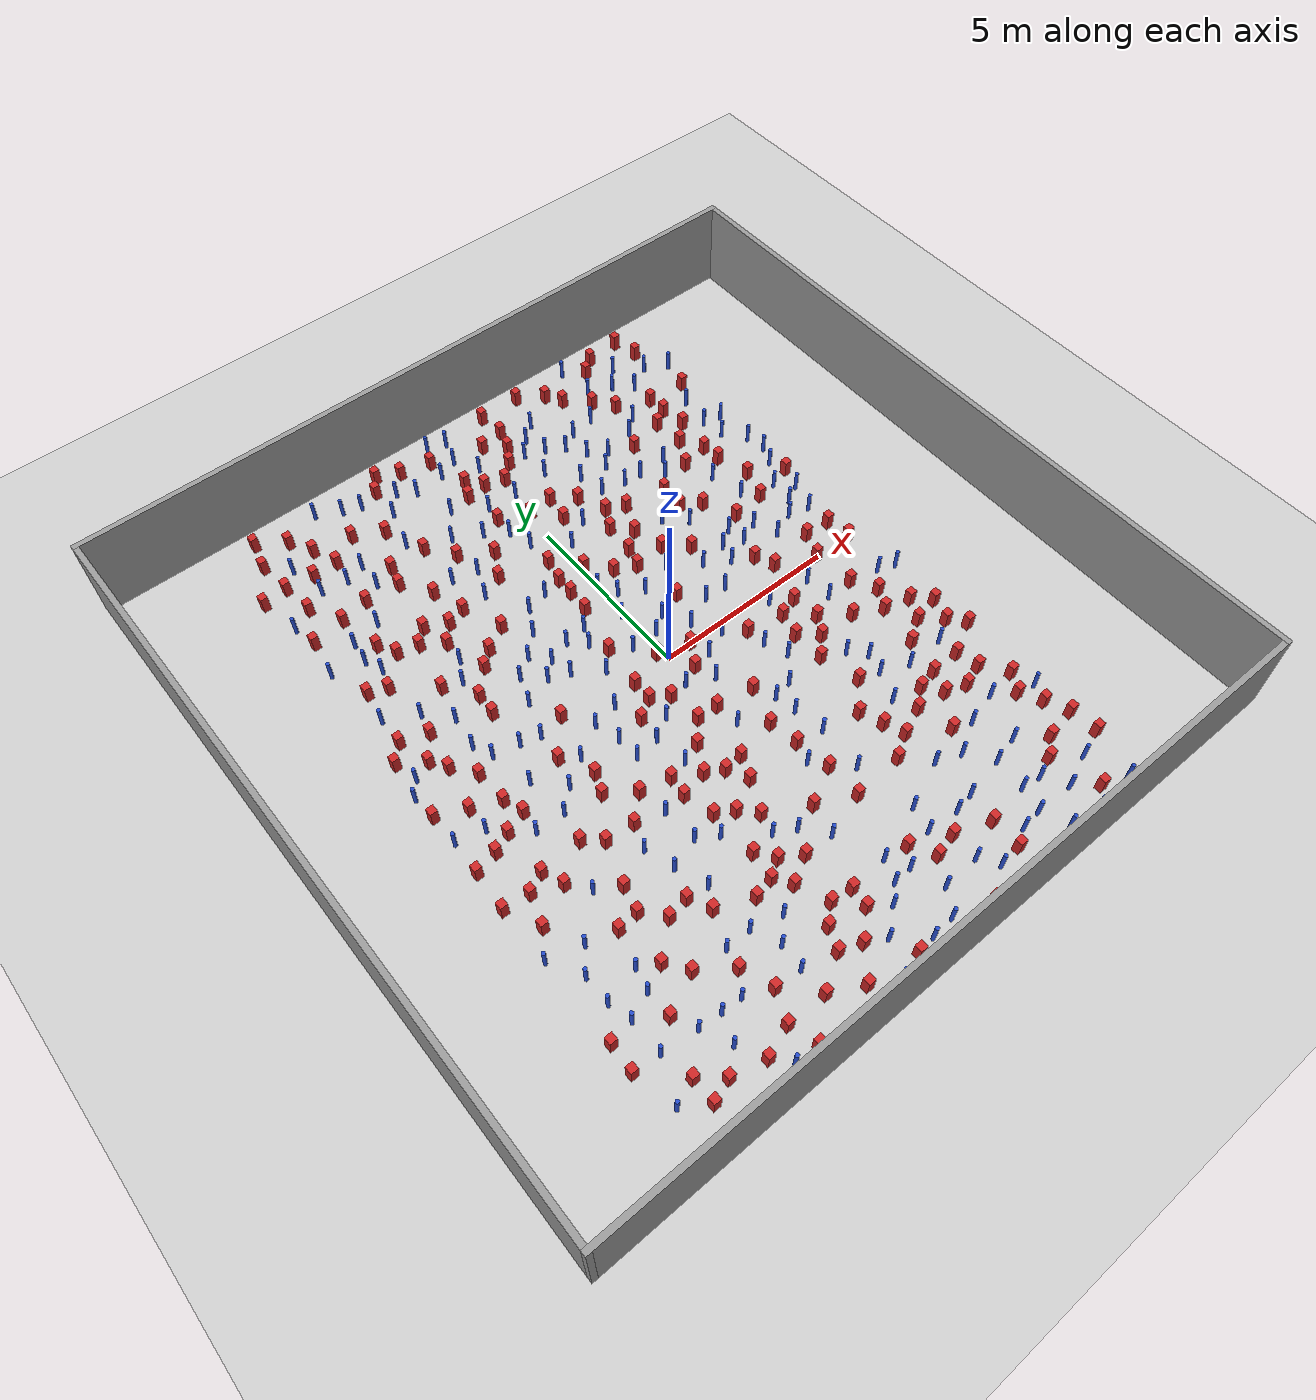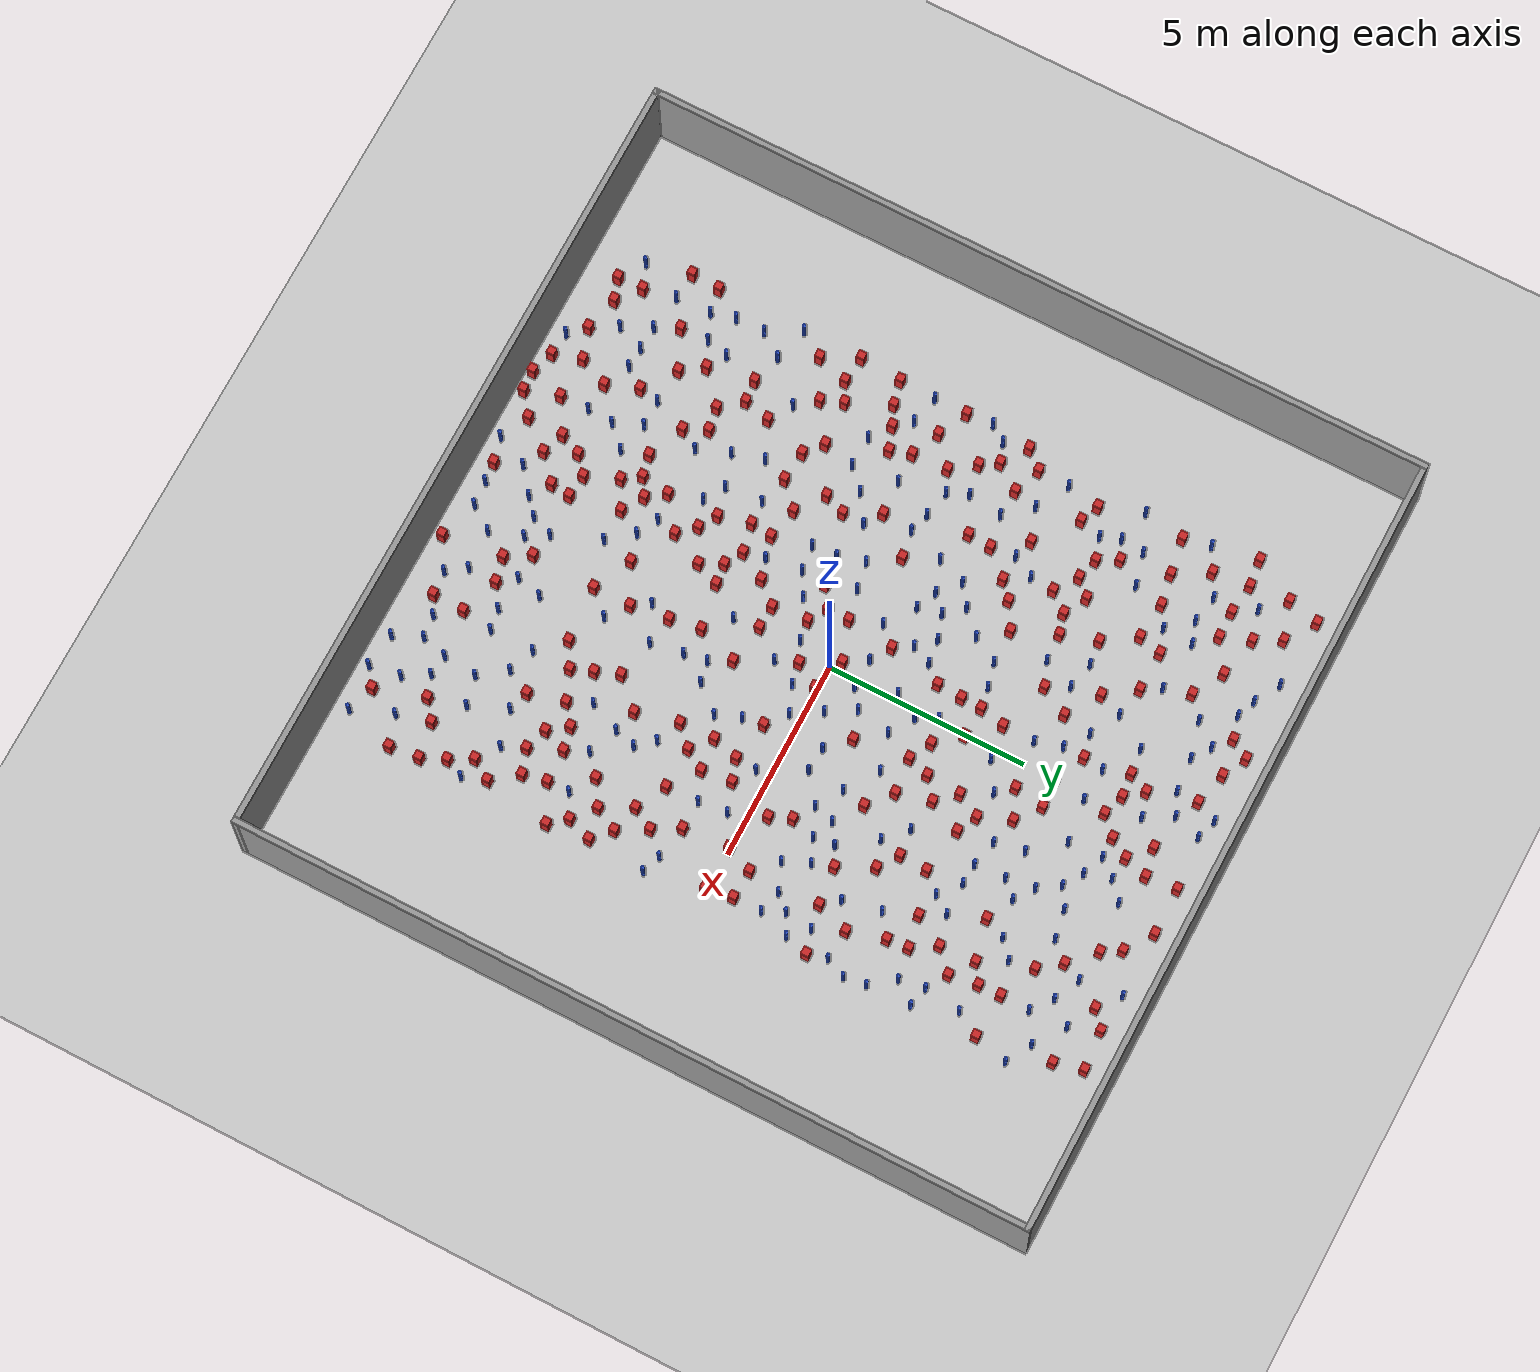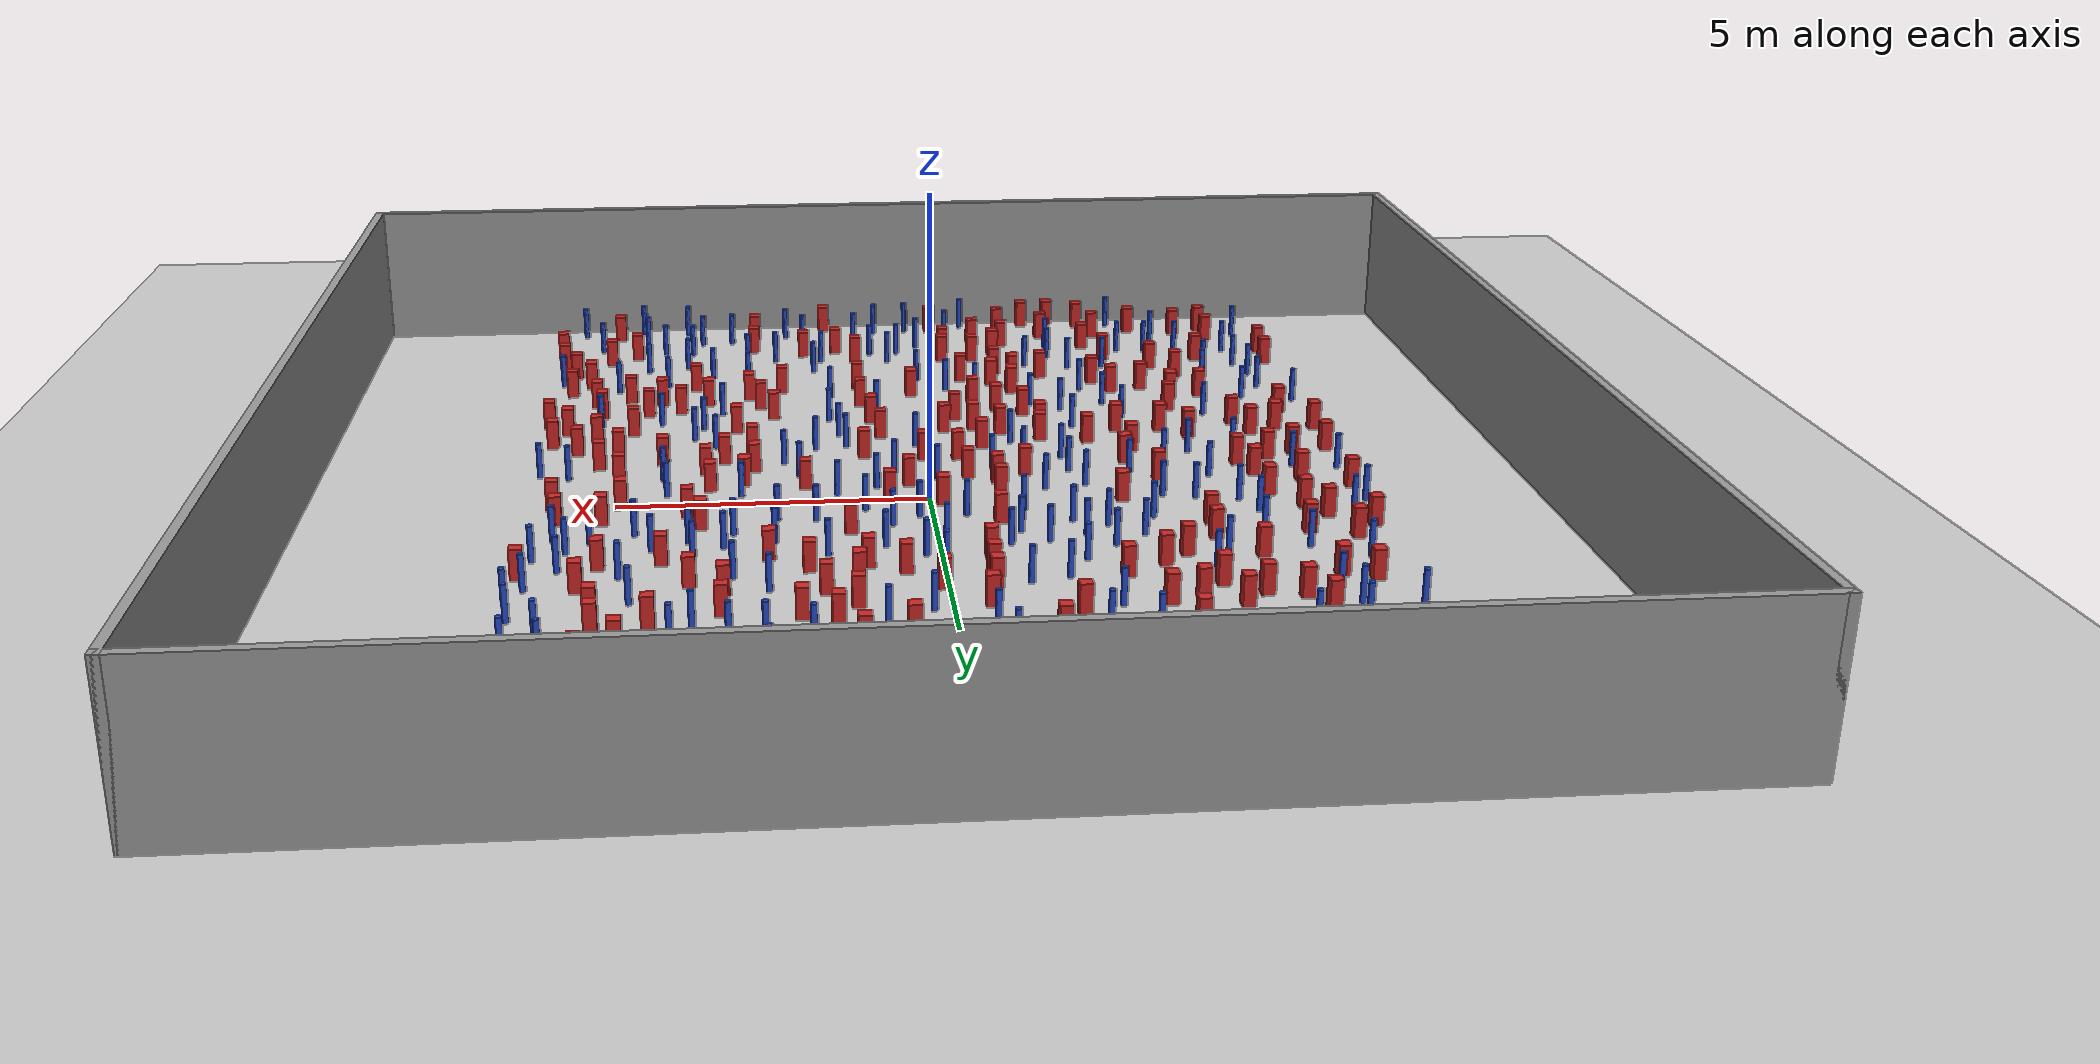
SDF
<sdf version="1.6">
 <world name="default">
  <light name="sun" type="directional">
   <pose>0 0 1000 0 -0 0</pose>
   <diffuse>0.8 0.8 0.8 1</diffuse>
   <specular>0.1 0.1 0.1 1</specular>
   <attenuation>
    <range>1000</range>
    <constant>0.9</constant>
    <linear>0.01</linear>
    <quadratic>0.001</quadratic>
   </attenuation>
   <direction>-0.5 0.5 -1</direction>
  </light>
  <model name="ground_plane">
   <static>1</static>
   <link name="link">
    <collision name="collision">
     <geometry><plane><normal>0 0 1</normal><size>100 100</size></plane></geometry>
     <surface><friction><ode><mu>100</mu><mu2>50</mu2></ode></friction></surface>
    </collision>
    <visual name="visual">
     <cast_shadows>0</cast_shadows>
     <geometry><plane><normal>0 0 1</normal><size>100 100</size></plane></geometry>
     <material>
      <ambient>1.0 1.0 1.0 1.0</ambient>
      <diffuse>0.8 0.8 0.8 1.0</diffuse>
      <specular>0.01 0.01 0.01 1.000000</specular>
     </material>
    </visual>
   </link>
  </model>
  <gravity>0 0 -9.8</gravity>
  <magnetic_field>6e-06 2.3e-05 -4.2e-05</magnetic_field>
  <atmosphere type="adiabatic"/>
  <physics name="default_physics" default="0" type="ode">
   <max_step_size>0.001</max_step_size>
   <real_time_factor>1</real_time_factor>
   <real_time_update_rate>1000</real_time_update_rate>
  </physics>
  <scene><ambient>0.4 0.4 0.4 1</ambient><background>0.7 0.7 0.7 1</background><shadows>1</shadows></scene>
  <spherical_coordinates>
   <surface_model>EARTH_WGS84</surface_model>
   <latitude_deg>0</latitude_deg>
   <longitude_deg>0</longitude_deg>
   <elevation>0</elevation>
   <heading_deg>0</heading_deg>
  </spherical_coordinates>
  <plugin name="gazebo_occupancy_map" filename="libgazebo_2Dmap_plugin.so">
   <map_resolution>0.05</map_resolution>
   <map_topic>generated_map</map_topic>
   <map_height>0.01</map_height>
   <map_size_x>50</map_size_x>
   <map_size_y>50</map_size_y>
  </plugin>
  <model name="NamedLocations">
   <static>true</static>
   <link name="DefaultStart"><pose>8.5 0 0 0 0 3.14</pose></link>
  </model>
  <model name="20x20_walls">
   <pose>0.044518 0.176112 0 0 -0 0</pose>
   <link name="Wall_1">
    <collision name="Wall_1_Collision">
     <geometry><box><size>20 0.15 2.5</size></box></geometry>
     <pose>0 0 1.25 0 -0 0</pose>
    </collision>
    <visual name="Wall_1_Visual">
     <pose>0 0 1.25 0 -0 0</pose>
     <geometry><box><size>20 0.15 2.5</size></box></geometry>
     <material>
      <script><uri>file://media/materials/scripts/gazebo.material</uri><name>Gazebo/Grey</name></script>
      <ambient>0.976471 0.992157 1 1</ambient>
     </material>
     <meta><layer>0</layer></meta>
    </visual>
    <pose>0 9.925 0 0 -0 0</pose>
   </link>
   <link name="Wall_3">
    <collision name="Wall_3_Collision">
     <geometry><box><size>20 0.15 2.5</size></box></geometry>
     <pose>0 0 1.25 0 -0 0</pose>
    </collision>
    <visual name="Wall_3_Visual">
     <pose>0 0 1.25 0 -0 0</pose>
     <geometry><box><size>20 0.15 2.5</size></box></geometry>
     <material>
      <script><uri>file://media/materials/scripts/gazebo.material</uri><name>Gazebo/Grey</name></script>
      <ambient>0.976471 0.992157 1 1</ambient>
     </material>
     <meta><layer>0</layer></meta>
    </visual>
    <pose>9.925 0 0 0 0 -1.5708</pose>
   </link>
   <link name="Wall_4">
    <collision name="Wall_4_Collision">
     <geometry><box><size>20 0.15 2.5</size></box></geometry>
     <pose>0 0 1.25 0 -0 0</pose>
    </collision>
    <visual name="Wall_4_Visual">
     <pose>0 0 1.25 0 -0 0</pose>
     <geometry><box><size>20 0.15 2.5</size></box></geometry>
     <material>
      <script><uri>file://media/materials/scripts/gazebo.material</uri><name>Gazebo/Grey</name></script>
      <ambient>0.976471 0.992157 1 1</ambient>
     </material>
     <meta><layer>0</layer></meta>
    </visual>
    <pose>0 -9.925 0 0 -0 3.14159</pose>
   </link>
   <link name="Wall_5">
    <collision name="Wall_5_Collision">
     <geometry><box><size>20 0.15 2.5</size></box></geometry>
     <pose>0 0 1.25 0 -0 0</pose>
    </collision>
    <visual name="Wall_5_Visual">
     <pose>0 0 1.25 0 -0 0</pose>
     <geometry><box><size>20 0.15 2.5</size></box></geometry>
     <material>
      <script><uri>file://media/materials/scripts/gazebo.material</uri><name>Gazebo/Grey</name></script>
      <ambient>0.976471 0.992157 1 1</ambient>
     </material>
     <meta><layer>0</layer></meta>
    </visual>
    <pose>-9.925 0 0 0 -0 1.5708</pose>
   </link>
   <static>1</static>
  </model>
  <model name="pole_obstacle0">
   <static>true</static>
   <pose>1.45764528737 -3.91231881478 -9.47619616065e-06 5.49618799737e-07 2.36310414062e-07 -1.55090534798e-07</pose>
   <link name="link">
    <pose>0 0 0.3 0 -0 0</pose>
    <inertial>
     <mass>1</mass>
     <inertia><ixx>0.145833</ixx><ixy>0</ixy><ixz>0</ixz><iyy>0.145833</iyy><iyz>0</iyz><izz>0.125</izz></inertia>
    </inertial>
    <collision name="collision">
     <geometry><cylinder><radius>0.05</radius><length>.6</length></cylinder></geometry>
    </collision>
    <visual name="visual">
     <geometry><cylinder><radius>0.05</radius><length>.6</length></cylinder></geometry>
     <material>
      <script><name>Gazebo/Blue</name><uri>file://media/materials/scripts/gazebo.material</uri></script>
     </material>
    </visual>
   </link>
  </model>
  <model name="pole_obstacle1">
   <static>true</static>
   <pose>-5.5666735039 -5.6523936144 -9.47619616065e-06 5.49618799737e-07 2.36310414037e-07 -1.55090534814e-07</pose>
   <link name="link">
    <pose>0 0 0.3 0 -0 0</pose>
    <inertial>
     <mass>1</mass>
     <inertia><ixx>0.145833</ixx><ixy>0</ixy><ixz>0</ixz><iyy>0.145833</iyy><iyz>0</iyz><izz>0.125</izz></inertia>
    </inertial>
    <collision name="collision">
     <geometry><cylinder><radius>0.05</radius><length>.6</length></cylinder></geometry>
    </collision>
    <visual name="visual">
     <geometry><cylinder><radius>0.05</radius><length>.6</length></cylinder></geometry>
     <material>
      <script><name>Gazebo/Blue</name><uri>file://media/materials/scripts/gazebo.material</uri></script>
     </material>
    </visual>
   </link>
  </model>
  <model name="square_post_obstacle0">
   <static>true</static>
   <pose>-5.34612675262 4.74920130066 -6.11067671241e-07 -5.50515727128e-06 -8.79689657224e-07 2.37013304536e-05</pose>
   <link name="link">
    <pose>0 0 0.25 0 -0 0</pose>
    <inertial>
     <mass>100</mass>
     <inertia>
      <ixx>0.166667</ixx>
      <ixy>0</ixy>
      <ixz>0</ixz>
      <iyy>0.166667</iyy>
      <iyz>0</iyz>
      <izz>0.166667</izz>
     </inertia>
    </inertial>
    <collision name="collision"><geometry><box><size>.2 .2 .5</size></box></geometry></collision>
    <visual name="visual">
     <geometry><box><size>.2 .2 .5</size></box></geometry>
     <material>
      <script><name>Gazebo/Red</name><uri>file://media/materials/scripts/gazebo.material</uri></script>
     </material>
    </visual>
   </link>
  </model>
  <model name="square_post_obstacle1">
   <static>true</static>
   <pose>-2.77302818829 6.5551887884 -6.11067671241e-07 -5.50515727128e-06 -8.79689657224e-07 2.37013304536e-05</pose>
   <link name="link">
    <pose>0 0 0.25 0 -0 0</pose>
    <inertial>
     <mass>100</mass>
     <inertia>
      <ixx>0.166667</ixx>
      <ixy>0</ixy>
      <ixz>0</ixz>
      <iyy>0.166667</iyy>
      <iyz>0</iyz>
      <izz>0.166667</izz>
     </inertia>
    </inertial>
    <collision name="collision"><geometry><box><size>.2 .2 .5</size></box></geometry></collision>
    <visual name="visual">
     <geometry><box><size>.2 .2 .5</size></box></geometry>
     <material>
      <script><name>Gazebo/Red</name><uri>file://media/materials/scripts/gazebo.material</uri></script>
     </material>
    </visual>
   </link>
  </model>
  <model name="pole_obstacle2">
   <static>true</static>
   <pose>-5.59544689235 2.43594534413 -9.47619616065e-06 5.49618799738e-07 2.36310414051e-07 -1.55090534805e-07</pose>
   <link name="link">
    <pose>0 0 0.3 0 -0 0</pose>
    <inertial>
     <mass>1</mass>
     <inertia><ixx>0.145833</ixx><ixy>0</ixy><ixz>0</ixz><iyy>0.145833</iyy><iyz>0</iyz><izz>0.125</izz></inertia>
    </inertial>
    <collision name="collision">
     <geometry><cylinder><radius>0.05</radius><length>.6</length></cylinder></geometry>
    </collision>
    <visual name="visual">
     <geometry><cylinder><radius>0.05</radius><length>.6</length></cylinder></geometry>
     <material>
      <script><name>Gazebo/Blue</name><uri>file://media/materials/scripts/gazebo.material</uri></script>
     </material>
    </visual>
   </link>
  </model>
  <model name="pole_obstacle3">
   <static>true</static>
   <pose>-1.79859433589 3.30144973369 -9.47619616065e-06 5.49618799737e-07 2.36310414062e-07 -1.55090534798e-07</pose>
   <link name="link">
    <pose>0 0 0.3 0 -0 0</pose>
    <inertial>
     <mass>1</mass>
     <inertia><ixx>0.145833</ixx><ixy>0</ixy><ixz>0</ixz><iyy>0.145833</iyy><iyz>0</iyz><izz>0.125</izz></inertia>
    </inertial>
    <collision name="collision">
     <geometry><cylinder><radius>0.05</radius><length>.6</length></cylinder></geometry>
    </collision>
    <visual name="visual">
     <geometry><cylinder><radius>0.05</radius><length>.6</length></cylinder></geometry>
     <material>
      <script><name>Gazebo/Blue</name><uri>file://media/materials/scripts/gazebo.material</uri></script>
     </material>
    </visual>
   </link>
  </model>
  <model name="pole_obstacle4">
   <static>true</static>
   <pose>-2.6717958394 2.1456863757 -9.47619616065e-06 5.49618799737e-07 2.36310414051e-07 -1.55090534807e-07</pose>
   <link name="link">
    <pose>0 0 0.3 0 -0 0</pose>
    <inertial>
     <mass>1</mass>
     <inertia><ixx>0.145833</ixx><ixy>0</ixy><ixz>0</ixz><iyy>0.145833</iyy><iyz>0</iyz><izz>0.125</izz></inertia>
    </inertial>
    <collision name="collision">
     <geometry><cylinder><radius>0.05</radius><length>.6</length></cylinder></geometry>
    </collision>
    <visual name="visual">
     <geometry><cylinder><radius>0.05</radius><length>.6</length></cylinder></geometry>
     <material>
      <script><name>Gazebo/Blue</name><uri>file://media/materials/scripts/gazebo.material</uri></script>
     </material>
    </visual>
   </link>
  </model>
  <model name="pole_obstacle5">
   <static>true</static>
   <pose>3.9795930664 8.41636946074 -9.4761961606e-06 5.49618799729e-07 2.36310414e-07 -1.55090534824e-07</pose>
   <link name="link">
    <pose>0 0 0.3 0 -0 0</pose>
    <inertial>
     <mass>1</mass>
     <inertia><ixx>0.145833</ixx><ixy>0</ixy><ixz>0</ixz><iyy>0.145833</iyy><iyz>0</iyz><izz>0.125</izz></inertia>
    </inertial>
    <collision name="collision">
     <geometry><cylinder><radius>0.05</radius><length>.6</length></cylinder></geometry>
    </collision>
    <visual name="visual">
     <geometry><cylinder><radius>0.05</radius><length>.6</length></cylinder></geometry>
     <material>
      <script><name>Gazebo/Blue</name><uri>file://media/materials/scripts/gazebo.material</uri></script>
     </material>
    </visual>
   </link>
  </model>
  <model name="pole_obstacle6">
   <static>true</static>
   <pose>4.61907861726 8.1229352003 -9.47619616065e-06 5.49618799737e-07 2.36310414065e-07 -1.55090534796e-07</pose>
   <link name="link">
    <pose>0 0 0.3 0 -0 0</pose>
    <inertial>
     <mass>1</mass>
     <inertia><ixx>0.145833</ixx><ixy>0</ixy><ixz>0</ixz><iyy>0.145833</iyy><iyz>0</iyz><izz>0.125</izz></inertia>
    </inertial>
    <collision name="collision">
     <geometry><cylinder><radius>0.05</radius><length>.6</length></cylinder></geometry>
    </collision>
    <visual name="visual">
     <geometry><cylinder><radius>0.05</radius><length>.6</length></cylinder></geometry>
     <material>
      <script><name>Gazebo/Blue</name><uri>file://media/materials/scripts/gazebo.material</uri></script>
     </material>
    </visual>
   </link>
  </model>
  <model name="square_post_obstacle2">
   <static>true</static>
   <pose>1.13025844479 2.6362197679 -6.11067671241e-07 -5.50515727128e-06 -8.79689657224e-07 2.37013304536e-05</pose>
   <link name="link">
    <pose>0 0 0.25 0 -0 0</pose>
    <inertial>
     <mass>100</mass>
     <inertia>
      <ixx>0.166667</ixx>
      <ixy>0</ixy>
      <ixz>0</ixz>
      <iyy>0.166667</iyy>
      <iyz>0</iyz>
      <izz>0.166667</izz>
     </inertia>
    </inertial>
    <collision name="collision"><geometry><box><size>.2 .2 .5</size></box></geometry></collision>
    <visual name="visual">
     <geometry><box><size>.2 .2 .5</size></box></geometry>
     <material>
      <script><name>Gazebo/Red</name><uri>file://media/materials/scripts/gazebo.material</uri></script>
     </material>
    </visual>
   </link>
  </model>
  <model name="square_post_obstacle3">
   <static>true</static>
   <pose>2.2582333432 -5.58475907966 -6.11067671241e-07 -5.50515727128e-06 -8.79689657224e-07 2.37013304536e-05</pose>
   <link name="link">
    <pose>0 0 0.25 0 -0 0</pose>
    <inertial>
     <mass>100</mass>
     <inertia>
      <ixx>0.166667</ixx>
      <ixy>0</ixy>
      <ixz>0</ixz>
      <iyy>0.166667</iyy>
      <iyz>0</iyz>
      <izz>0.166667</izz>
     </inertia>
    </inertial>
    <collision name="collision"><geometry><box><size>.2 .2 .5</size></box></geometry></collision>
    <visual name="visual">
     <geometry><box><size>.2 .2 .5</size></box></geometry>
     <material>
      <script><name>Gazebo/Red</name><uri>file://media/materials/scripts/gazebo.material</uri></script>
     </material>
    </visual>
   </link>
  </model>
  <model name="square_post_obstacle4">
   <static>true</static>
   <pose>-0.513113206835 -3.23635773973 -6.11067671241e-07 -5.50515727128e-06 -8.79689657224e-07 2.37013304536e-05</pose>
   <link name="link">
    <pose>0 0 0.25 0 -0 0</pose>
    <inertial>
     <mass>100</mass>
     <inertia>
      <ixx>0.166667</ixx>
      <ixy>0</ixy>
      <ixz>0</ixz>
      <iyy>0.166667</iyy>
      <iyz>0</iyz>
      <izz>0.166667</izz>
     </inertia>
    </inertial>
    <collision name="collision"><geometry><box><size>.2 .2 .5</size></box></geometry></collision>
    <visual name="visual">
     <geometry><box><size>.2 .2 .5</size></box></geometry>
     <material>
      <script><name>Gazebo/Red</name><uri>file://media/materials/scripts/gazebo.material</uri></script>
     </material>
    </visual>
   </link>
  </model>
  <model name="pole_obstacle7">
   <static>true</static>
   <pose>0.491600590641 -1.18340248795 -9.47619616065e-06 5.49618799737e-07 2.36310414059e-07 -1.55090534802e-07</pose>
   <link name="link">
    <pose>0 0 0.3 0 -0 0</pose>
    <inertial>
     <mass>1</mass>
     <inertia><ixx>0.145833</ixx><ixy>0</ixy><ixz>0</ixz><iyy>0.145833</iyy><iyz>0</iyz><izz>0.125</izz></inertia>
    </inertial>
    <collision name="collision">
     <geometry><cylinder><radius>0.05</radius><length>.6</length></cylinder></geometry>
    </collision>
    <visual name="visual">
     <geometry><cylinder><radius>0.05</radius><length>.6</length></cylinder></geometry>
     <material>
      <script><name>Gazebo/Blue</name><uri>file://media/materials/scripts/gazebo.material</uri></script>
     </material>
    </visual>
   </link>
  </model>
  <model name="pole_obstacle8">
   <static>true</static>
   <pose>0.036647531542 -2.49097002467 -9.4761961606e-06 5.49618799729e-07 2.36310413998e-07 -1.55090534825e-07</pose>
   <link name="link">
    <pose>0 0 0.3 0 -0 0</pose>
    <inertial>
     <mass>1</mass>
     <inertia><ixx>0.145833</ixx><ixy>0</ixy><ixz>0</ixz><iyy>0.145833</iyy><iyz>0</iyz><izz>0.125</izz></inertia>
    </inertial>
    <collision name="collision">
     <geometry><cylinder><radius>0.05</radius><length>.6</length></cylinder></geometry>
    </collision>
    <visual name="visual">
     <geometry><cylinder><radius>0.05</radius><length>.6</length></cylinder></geometry>
     <material>
      <script><name>Gazebo/Blue</name><uri>file://media/materials/scripts/gazebo.material</uri></script>
     </material>
    </visual>
   </link>
  </model>
  <model name="square_post_obstacle5">
   <static>true</static>
   <pose>5.88952269268 0.614847959683 -6.11067671241e-07 -5.50515727128e-06 -8.79689657224e-07 2.37013304536e-05</pose>
   <link name="link">
    <pose>0 0 0.25 0 -0 0</pose>
    <inertial>
     <mass>100</mass>
     <inertia>
      <ixx>0.166667</ixx>
      <ixy>0</ixy>
      <ixz>0</ixz>
      <iyy>0.166667</iyy>
      <iyz>0</iyz>
      <izz>0.166667</izz>
     </inertia>
    </inertial>
    <collision name="collision"><geometry><box><size>.2 .2 .5</size></box></geometry></collision>
    <visual name="visual">
     <geometry><box><size>.2 .2 .5</size></box></geometry>
     <material>
      <script><name>Gazebo/Red</name><uri>file://media/materials/scripts/gazebo.material</uri></script>
     </material>
    </visual>
   </link>
  </model>
  <model name="square_post_obstacle6">
   <static>true</static>
   <pose>1.65782536818 4.62494805286 -6.11067671241e-07 -5.50515727128e-06 -8.79689657224e-07 2.37013304536e-05</pose>
   <link name="link">
    <pose>0 0 0.25 0 -0 0</pose>
    <inertial>
     <mass>100</mass>
     <inertia>
      <ixx>0.166667</ixx>
      <ixy>0</ixy>
      <ixz>0</ixz>
      <iyy>0.166667</iyy>
      <iyz>0</iyz>
      <izz>0.166667</izz>
     </inertia>
    </inertial>
    <collision name="collision"><geometry><box><size>.2 .2 .5</size></box></geometry></collision>
    <visual name="visual">
     <geometry><box><size>.2 .2 .5</size></box></geometry>
     <material>
      <script><name>Gazebo/Red</name><uri>file://media/materials/scripts/gazebo.material</uri></script>
     </material>
    </visual>
   </link>
  </model>
  <model name="square_post_obstacle7">
   <static>true</static>
   <pose>-0.0492457941668 -1.85533432549 -6.11067671241e-07 -5.50515727128e-06 -8.79689657224e-07 2.37013304536e-05</pose>
   <link name="link">
    <pose>0 0 0.25 0 -0 0</pose>
    <inertial>
     <mass>100</mass>
     <inertia>
      <ixx>0.166667</ixx>
      <ixy>0</ixy>
      <ixz>0</ixz>
      <iyy>0.166667</iyy>
      <iyz>0</iyz>
      <izz>0.166667</izz>
     </inertia>
    </inertial>
    <collision name="collision"><geometry><box><size>.2 .2 .5</size></box></geometry></collision>
    <visual name="visual">
     <geometry><box><size>.2 .2 .5</size></box></geometry>
     <material>
      <script><name>Gazebo/Red</name><uri>file://media/materials/scripts/gazebo.material</uri></script>
     </material>
    </visual>
   </link>
  </model>
  <model name="pole_obstacle9">
   <static>true</static>
   <pose>-0.391706613533 -8.08337775181 -9.47619616065e-06 5.49618799737e-07 2.36310414031e-07 -1.55090534818e-07</pose>
   <link name="link">
    <pose>0 0 0.3 0 -0 0</pose>
    <inertial>
     <mass>1</mass>
     <inertia><ixx>0.145833</ixx><ixy>0</ixy><ixz>0</ixz><iyy>0.145833</iyy><iyz>0</iyz><izz>0.125</izz></inertia>
    </inertial>
    <collision name="collision">
     <geometry><cylinder><radius>0.05</radius><length>.6</length></cylinder></geometry>
    </collision>
    <visual name="visual">
     <geometry><cylinder><radius>0.05</radius><length>.6</length></cylinder></geometry>
     <material>
      <script><name>Gazebo/Blue</name><uri>file://media/materials/scripts/gazebo.material</uri></script>
     </material>
    </visual>
   </link>
  </model>
  <model name="pole_obstacle10">
   <static>true</static>
   <pose>-3.19090244332 -5.21670269454 -9.4761961606e-06 5.49618799729e-07 2.36310414006e-07 -1.55090534822e-07</pose>
   <link name="link">
    <pose>0 0 0.3 0 -0 0</pose>
    <inertial>
     <mass>1</mass>
     <inertia><ixx>0.145833</ixx><ixy>0</ixy><ixz>0</ixz><iyy>0.145833</iyy><iyz>0</iyz><izz>0.125</izz></inertia>
    </inertial>
    <collision name="collision">
     <geometry><cylinder><radius>0.05</radius><length>.6</length></cylinder></geometry>
    </collision>
    <visual name="visual">
     <geometry><cylinder><radius>0.05</radius><length>.6</length></cylinder></geometry>
     <material>
      <script><name>Gazebo/Blue</name><uri>file://media/materials/scripts/gazebo.material</uri></script>
     </material>
    </visual>
   </link>
  </model>
  <model name="pole_obstacle11">
   <static>true</static>
   <pose>-0.522241702906 0.749692683918 -9.47619616065e-06 5.49618799737e-07 2.36310414066e-07 -1.55090534796e-07</pose>
   <link name="link">
    <pose>0 0 0.3 0 -0 0</pose>
    <inertial>
     <mass>1</mass>
     <inertia><ixx>0.145833</ixx><ixy>0</ixy><ixz>0</ixz><iyy>0.145833</iyy><iyz>0</iyz><izz>0.125</izz></inertia>
    </inertial>
    <collision name="collision">
     <geometry><cylinder><radius>0.05</radius><length>.6</length></cylinder></geometry>
    </collision>
    <visual name="visual">
     <geometry><cylinder><radius>0.05</radius><length>.6</length></cylinder></geometry>
     <material>
      <script><name>Gazebo/Blue</name><uri>file://media/materials/scripts/gazebo.material</uri></script>
     </material>
    </visual>
   </link>
  </model>
  <model name="pole_obstacle12">
   <static>true</static>
   <pose>4.19699384689 -0.435499464074 -9.47619616065e-06 5.49618799737e-07 2.36310414057e-07 -1.55090534802e-07</pose>
   <link name="link">
    <pose>0 0 0.3 0 -0 0</pose>
    <inertial>
     <mass>1</mass>
     <inertia><ixx>0.145833</ixx><ixy>0</ixy><ixz>0</ixz><iyy>0.145833</iyy><iyz>0</iyz><izz>0.125</izz></inertia>
    </inertial>
    <collision name="collision">
     <geometry><cylinder><radius>0.05</radius><length>.6</length></cylinder></geometry>
    </collision>
    <visual name="visual">
     <geometry><cylinder><radius>0.05</radius><length>.6</length></cylinder></geometry>
     <material>
      <script><name>Gazebo/Blue</name><uri>file://media/materials/scripts/gazebo.material</uri></script>
     </material>
    </visual>
   </link>
  </model>
  <model name="square_post_obstacle8">
   <static>true</static>
   <pose>-1.40005594212 -7.19498384418 -6.11067671241e-07 -5.50515727128e-06 -8.79689657224e-07 2.37013304536e-05</pose>
   <link name="link">
    <pose>0 0 0.25 0 -0 0</pose>
    <inertial>
     <mass>100</mass>
     <inertia>
      <ixx>0.166667</ixx>
      <ixy>0</ixy>
      <ixz>0</ixz>
      <iyy>0.166667</iyy>
      <iyz>0</iyz>
      <izz>0.166667</izz>
     </inertia>
    </inertial>
    <collision name="collision"><geometry><box><size>.2 .2 .5</size></box></geometry></collision>
    <visual name="visual">
     <geometry><box><size>.2 .2 .5</size></box></geometry>
     <material>
      <script><name>Gazebo/Red</name><uri>file://media/materials/scripts/gazebo.material</uri></script>
     </material>
    </visual>
   </link>
  </model>
  <model name="square_post_obstacle9">
   <static>true</static>
   <pose>-1.15988384028 -0.124904524692 -6.11067671241e-07 -5.50515727128e-06 -8.79689657224e-07 2.37013304536e-05</pose>
   <link name="link">
    <pose>0 0 0.25 0 -0 0</pose>
    <inertial>
     <mass>100</mass>
     <inertia>
      <ixx>0.166667</ixx>
      <ixy>0</ixy>
      <ixz>0</ixz>
      <iyy>0.166667</iyy>
      <iyz>0</iyz>
      <izz>0.166667</izz>
     </inertia>
    </inertial>
    <collision name="collision"><geometry><box><size>.2 .2 .5</size></box></geometry></collision>
    <visual name="visual">
     <geometry><box><size>.2 .2 .5</size></box></geometry>
     <material>
      <script><name>Gazebo/Red</name><uri>file://media/materials/scripts/gazebo.material</uri></script>
     </material>
    </visual>
   </link>
  </model>
  <model name="pole_obstacle13">
   <static>true</static>
   <pose>-2.77437427752 5.27815856419 -9.47619616065e-06 5.49618799738e-07 2.3631041406e-07 -1.55090534801e-07</pose>
   <link name="link">
    <pose>0 0 0.3 0 -0 0</pose>
    <inertial>
     <mass>1</mass>
     <inertia><ixx>0.145833</ixx><ixy>0</ixy><ixz>0</ixz><iyy>0.145833</iyy><iyz>0</iyz><izz>0.125</izz></inertia>
    </inertial>
    <collision name="collision">
     <geometry><cylinder><radius>0.05</radius><length>.6</length></cylinder></geometry>
    </collision>
    <visual name="visual">
     <geometry><cylinder><radius>0.05</radius><length>.6</length></cylinder></geometry>
     <material>
      <script><name>Gazebo/Blue</name><uri>file://media/materials/scripts/gazebo.material</uri></script>
     </material>
    </visual>
   </link>
  </model>
  <model name="square_post_obstacle10">
   <static>true</static>
   <pose>-6.29969308283 -1.63113465276 -6.11067671241e-07 -5.50515727128e-06 -8.79689657224e-07 2.37013304536e-05</pose>
   <link name="link">
    <pose>0 0 0.25 0 -0 0</pose>
    <inertial>
     <mass>100</mass>
     <inertia>
      <ixx>0.166667</ixx>
      <ixy>0</ixy>
      <ixz>0</ixz>
      <iyy>0.166667</iyy>
      <iyz>0</iyz>
      <izz>0.166667</izz>
     </inertia>
    </inertial>
    <collision name="collision"><geometry><box><size>.2 .2 .5</size></box></geometry></collision>
    <visual name="visual">
     <geometry><box><size>.2 .2 .5</size></box></geometry>
     <material>
      <script><name>Gazebo/Red</name><uri>file://media/materials/scripts/gazebo.material</uri></script>
     </material>
    </visual>
   </link>
  </model>
  <model name="square_post_obstacle11">
   <static>true</static>
   <pose>-3.60077260738 -1.97774736587 -6.11067671241e-07 -5.50515727128e-06 -8.79689657224e-07 2.37013304536e-05</pose>
   <link name="link">
    <pose>0 0 0.25 0 -0 0</pose>
    <inertial>
     <mass>100</mass>
     <inertia>
      <ixx>0.166667</ixx>
      <ixy>0</ixy>
      <ixz>0</ixz>
      <iyy>0.166667</iyy>
      <iyz>0</iyz>
      <izz>0.166667</izz>
     </inertia>
    </inertial>
    <collision name="collision"><geometry><box><size>.2 .2 .5</size></box></geometry></collision>
    <visual name="visual">
     <geometry><box><size>.2 .2 .5</size></box></geometry>
     <material>
      <script><name>Gazebo/Red</name><uri>file://media/materials/scripts/gazebo.material</uri></script>
     </material>
    </visual>
   </link>
  </model>
  <model name="pole_obstacle14">
   <static>true</static>
   <pose>4.04743545266 -9.25883310238 -9.47619616065e-06 5.49618799737e-07 2.36310414062e-07 -1.55090534799e-07</pose>
   <link name="link">
    <pose>0 0 0.3 0 -0 0</pose>
    <inertial>
     <mass>1</mass>
     <inertia><ixx>0.145833</ixx><ixy>0</ixy><ixz>0</ixz><iyy>0.145833</iyy><iyz>0</iyz><izz>0.125</izz></inertia>
    </inertial>
    <collision name="collision">
     <geometry><cylinder><radius>0.05</radius><length>.6</length></cylinder></geometry>
    </collision>
    <visual name="visual">
     <geometry><cylinder><radius>0.05</radius><length>.6</length></cylinder></geometry>
     <material>
      <script><name>Gazebo/Blue</name><uri>file://media/materials/scripts/gazebo.material</uri></script>
     </material>
    </visual>
   </link>
  </model>
  <model name="pole_obstacle15">
   <static>true</static>
   <pose>2.05337939577 -1.18928973745 -9.47619616065e-06 5.49618799737e-07 2.36310414072e-07 -1.55090534793e-07</pose>
   <link name="link">
    <pose>0 0 0.3 0 -0 0</pose>
    <inertial>
     <mass>1</mass>
     <inertia><ixx>0.145833</ixx><ixy>0</ixy><ixz>0</ixz><iyy>0.145833</iyy><iyz>0</iyz><izz>0.125</izz></inertia>
    </inertial>
    <collision name="collision">
     <geometry><cylinder><radius>0.05</radius><length>.6</length></cylinder></geometry>
    </collision>
    <visual name="visual">
     <geometry><cylinder><radius>0.05</radius><length>.6</length></cylinder></geometry>
     <material>
      <script><name>Gazebo/Blue</name><uri>file://media/materials/scripts/gazebo.material</uri></script>
     </material>
    </visual>
   </link>
  </model>
  <model name="square_post_obstacle12">
   <static>true</static>
   <pose>-1.43123995148 5.29667746574 -6.11067671241e-07 -5.50515727128e-06 -8.79689657224e-07 2.37013304536e-05</pose>
   <link name="link">
    <pose>0 0 0.25 0 -0 0</pose>
    <inertial>
     <mass>100</mass>
     <inertia>
      <ixx>0.166667</ixx>
      <ixy>0</ixy>
      <ixz>0</ixz>
      <iyy>0.166667</iyy>
      <iyz>0</iyz>
      <izz>0.166667</izz>
     </inertia>
    </inertial>
    <collision name="collision"><geometry><box><size>.2 .2 .5</size></box></geometry></collision>
    <visual name="visual">
     <geometry><box><size>.2 .2 .5</size></box></geometry>
     <material>
      <script><name>Gazebo/Red</name><uri>file://media/materials/scripts/gazebo.material</uri></script>
     </material>
    </visual>
   </link>
  </model>
  <model name="pole_obstacle16">
   <static>true</static>
   <pose>-4.01819675636 3.11525010436 -9.47619616065e-06 5.49618799737e-07 2.36310414053e-07 -1.55090534804e-07</pose>
   <link name="link">
    <pose>0 0 0.3 0 -0 0</pose>
    <inertial>
     <mass>1</mass>
     <inertia><ixx>0.145833</ixx><ixy>0</ixy><ixz>0</ixz><iyy>0.145833</iyy><iyz>0</iyz><izz>0.125</izz></inertia>
    </inertial>
    <collision name="collision">
     <geometry><cylinder><radius>0.05</radius><length>.6</length></cylinder></geometry>
    </collision>
    <visual name="visual">
     <geometry><cylinder><radius>0.05</radius><length>.6</length></cylinder></geometry>
     <material>
      <script><name>Gazebo/Blue</name><uri>file://media/materials/scripts/gazebo.material</uri></script>
     </material>
    </visual>
   </link>
  </model>
  <model name="pole_obstacle17">
   <static>true</static>
   <pose>0.805625796056 -8.5106215009 -9.47619616065e-06 5.49618799737e-07 2.36310414038e-07 -1.55090534813e-07</pose>
   <link name="link">
    <pose>0 0 0.3 0 -0 0</pose>
    <inertial>
     <mass>1</mass>
     <inertia><ixx>0.145833</ixx><ixy>0</ixy><ixz>0</ixz><iyy>0.145833</iyy><iyz>0</iyz><izz>0.125</izz></inertia>
    </inertial>
    <collision name="collision">
     <geometry><cylinder><radius>0.05</radius><length>.6</length></cylinder></geometry>
    </collision>
    <visual name="visual">
     <geometry><cylinder><radius>0.05</radius><length>.6</length></cylinder></geometry>
     <material>
      <script><name>Gazebo/Blue</name><uri>file://media/materials/scripts/gazebo.material</uri></script>
     </material>
    </visual>
   </link>
  </model>
  <model name="square_post_obstacle13">
   <static>true</static>
   <pose>2.64894658065 -4.7162178842 -6.11067671241e-07 -5.50515727128e-06 -8.79689657224e-07 2.37013304536e-05</pose>
   <link name="link">
    <pose>0 0 0.25 0 -0 0</pose>
    <inertial>
     <mass>100</mass>
     <inertia>
      <ixx>0.166667</ixx>
      <ixy>0</ixy>
      <ixz>0</ixz>
      <iyy>0.166667</iyy>
      <iyz>0</iyz>
      <izz>0.166667</izz>
     </inertia>
    </inertial>
    <collision name="collision"><geometry><box><size>.2 .2 .5</size></box></geometry></collision>
    <visual name="visual">
     <geometry><box><size>.2 .2 .5</size></box></geometry>
     <material>
      <script><name>Gazebo/Red</name><uri>file://media/materials/scripts/gazebo.material</uri></script>
     </material>
    </visual>
   </link>
  </model>
  <model name="pole_obstacle18">
   <static>true</static>
   <pose>-4.32137698985 -9.2348338794 -9.47619616065e-06 5.49618799737e-07 2.36310414065e-07 -1.55090534796e-07</pose>
   <link name="link">
    <pose>0 0 0.3 0 -0 0</pose>
    <inertial>
     <mass>1</mass>
     <inertia><ixx>0.145833</ixx><ixy>0</ixy><ixz>0</ixz><iyy>0.145833</iyy><iyz>0</iyz><izz>0.125</izz></inertia>
    </inertial>
    <collision name="collision">
     <geometry><cylinder><radius>0.05</radius><length>.6</length></cylinder></geometry>
    </collision>
    <visual name="visual">
     <geometry><cylinder><radius>0.05</radius><length>.6</length></cylinder></geometry>
     <material>
      <script><name>Gazebo/Blue</name><uri>file://media/materials/scripts/gazebo.material</uri></script>
     </material>
    </visual>
   </link>
  </model>
  <model name="square_post_obstacle14">
   <static>true</static>
   <pose>3.27732072388 -1.94028528122 -6.11067671241e-07 -5.50515727128e-06 -8.79689657224e-07 2.37013304536e-05</pose>
   <link name="link">
    <pose>0 0 0.25 0 -0 0</pose>
    <inertial>
     <mass>100</mass>
     <inertia>
      <ixx>0.166667</ixx>
      <ixy>0</ixy>
      <ixz>0</ixz>
      <iyy>0.166667</iyy>
      <iyz>0</iyz>
      <izz>0.166667</izz>
     </inertia>
    </inertial>
    <collision name="collision"><geometry><box><size>.2 .2 .5</size></box></geometry></collision>
    <visual name="visual">
     <geometry><box><size>.2 .2 .5</size></box></geometry>
     <material>
      <script><name>Gazebo/Red</name><uri>file://media/materials/scripts/gazebo.material</uri></script>
     </material>
    </visual>
   </link>
  </model>
  <model name="pole_obstacle19">
   <static>true</static>
   <pose>-2.35966112041 -1.71080538282 -9.47619616065e-06 5.49618799737e-07 2.36310414072e-07 -1.55090534793e-07</pose>
   <link name="link">
    <pose>0 0 0.3 0 -0 0</pose>
    <inertial>
     <mass>1</mass>
     <inertia><ixx>0.145833</ixx><ixy>0</ixy><ixz>0</ixz><iyy>0.145833</iyy><iyz>0</iyz><izz>0.125</izz></inertia>
    </inertial>
    <collision name="collision">
     <geometry><cylinder><radius>0.05</radius><length>.6</length></cylinder></geometry>
    </collision>
    <visual name="visual">
     <geometry><cylinder><radius>0.05</radius><length>.6</length></cylinder></geometry>
     <material>
      <script><name>Gazebo/Blue</name><uri>file://media/materials/scripts/gazebo.material</uri></script>
     </material>
    </visual>
   </link>
  </model>
  <model name="square_post_obstacle15">
   <static>true</static>
   <pose>-5.35787240034 8.94793512764 -6.11067671241e-07 -5.50515727128e-06 -8.79689657224e-07 2.37013304536e-05</pose>
   <link name="link">
    <pose>0 0 0.25 0 -0 0</pose>
    <inertial>
     <mass>100</mass>
     <inertia>
      <ixx>0.166667</ixx>
      <ixy>0</ixy>
      <ixz>0</ixz>
      <iyy>0.166667</iyy>
      <iyz>0</iyz>
      <izz>0.166667</izz>
     </inertia>
    </inertial>
    <collision name="collision"><geometry><box><size>.2 .2 .5</size></box></geometry></collision>
    <visual name="visual">
     <geometry><box><size>.2 .2 .5</size></box></geometry>
     <material>
      <script><name>Gazebo/Red</name><uri>file://media/materials/scripts/gazebo.material</uri></script>
     </material>
    </visual>
   </link>
  </model>
  <model name="square_post_obstacle16">
   <static>true</static>
   <pose>4.78682053761 9.36860131413 -6.11067671241e-07 -5.50515727128e-06 -8.79689657224e-07 2.37013304536e-05</pose>
   <link name="link">
    <pose>0 0 0.25 0 -0 0</pose>
    <inertial>
     <mass>100</mass>
     <inertia>
      <ixx>0.166667</ixx>
      <ixy>0</ixy>
      <ixz>0</ixz>
      <iyy>0.166667</iyy>
      <iyz>0</iyz>
      <izz>0.166667</izz>
     </inertia>
    </inertial>
    <collision name="collision"><geometry><box><size>.2 .2 .5</size></box></geometry></collision>
    <visual name="visual">
     <geometry><box><size>.2 .2 .5</size></box></geometry>
     <material>
      <script><name>Gazebo/Red</name><uri>file://media/materials/scripts/gazebo.material</uri></script>
     </material>
    </visual>
   </link>
  </model>
  <model name="square_post_obstacle17">
   <static>true</static>
   <pose>0.948095992492 8.06252955084 -6.11067671241e-07 -5.50515727128e-06 -8.79689657224e-07 2.37013304536e-05</pose>
   <link name="link">
    <pose>0 0 0.25 0 -0 0</pose>
    <inertial>
     <mass>100</mass>
     <inertia>
      <ixx>0.166667</ixx>
      <ixy>0</ixy>
      <ixz>0</ixz>
      <iyy>0.166667</iyy>
      <iyz>0</iyz>
      <izz>0.166667</izz>
     </inertia>
    </inertial>
    <collision name="collision"><geometry><box><size>.2 .2 .5</size></box></geometry></collision>
    <visual name="visual">
     <geometry><box><size>.2 .2 .5</size></box></geometry>
     <material>
      <script><name>Gazebo/Red</name><uri>file://media/materials/scripts/gazebo.material</uri></script>
     </material>
    </visual>
   </link>
  </model>
  <model name="pole_obstacle20">
   <static>true</static>
   <pose>0.233315141441 2.30578505208 -9.4761961606e-06 5.49618799729e-07 2.36310413995e-07 -1.55090534826e-07</pose>
   <link name="link">
    <pose>0 0 0.3 0 -0 0</pose>
    <inertial>
     <mass>1</mass>
     <inertia><ixx>0.145833</ixx><ixy>0</ixy><ixz>0</ixz><iyy>0.145833</iyy><iyz>0</iyz><izz>0.125</izz></inertia>
    </inertial>
    <collision name="collision">
     <geometry><cylinder><radius>0.05</radius><length>.6</length></cylinder></geometry>
    </collision>
    <visual name="visual">
     <geometry><cylinder><radius>0.05</radius><length>.6</length></cylinder></geometry>
     <material>
      <script><name>Gazebo/Blue</name><uri>file://media/materials/scripts/gazebo.material</uri></script>
     </material>
    </visual>
   </link>
  </model>
  <model name="pole_obstacle21">
   <static>true</static>
   <pose>-1.29164633985 6.02613737282 -9.47619616065e-06 5.49618799737e-07 2.36310414061e-07 -1.550905348e-07</pose>
   <link name="link">
    <pose>0 0 0.3 0 -0 0</pose>
    <inertial>
     <mass>1</mass>
     <inertia><ixx>0.145833</ixx><ixy>0</ixy><ixz>0</ixz><iyy>0.145833</iyy><iyz>0</iyz><izz>0.125</izz></inertia>
    </inertial>
    <collision name="collision">
     <geometry><cylinder><radius>0.05</radius><length>.6</length></cylinder></geometry>
    </collision>
    <visual name="visual">
     <geometry><cylinder><radius>0.05</radius><length>.6</length></cylinder></geometry>
     <material>
      <script><name>Gazebo/Blue</name><uri>file://media/materials/scripts/gazebo.material</uri></script>
     </material>
    </visual>
   </link>
  </model>
  <model name="pole_obstacle22">
   <static>true</static>
   <pose>-2.90995451725 -7.87920701199 -9.47619616065e-06 5.49618799738e-07 2.3631041406e-07 -1.55090534801e-07</pose>
   <link name="link">
    <pose>0 0 0.3 0 -0 0</pose>
    <inertial>
     <mass>1</mass>
     <inertia><ixx>0.145833</ixx><ixy>0</ixy><ixz>0</ixz><iyy>0.145833</iyy><iyz>0</iyz><izz>0.125</izz></inertia>
    </inertial>
    <collision name="collision">
     <geometry><cylinder><radius>0.05</radius><length>.6</length></cylinder></geometry>
    </collision>
    <visual name="visual">
     <geometry><cylinder><radius>0.05</radius><length>.6</length></cylinder></geometry>
     <material>
      <script><name>Gazebo/Blue</name><uri>file://media/materials/scripts/gazebo.material</uri></script>
     </material>
    </visual>
   </link>
  </model>
  <model name="pole_obstacle23">
   <static>true</static>
   <pose>3.99625036072 5.07486670675 -9.47619616065e-06 5.49618799737e-07 2.36310414049e-07 -1.55090534808e-07</pose>
   <link name="link">
    <pose>0 0 0.3 0 -0 0</pose>
    <inertial>
     <mass>1</mass>
     <inertia><ixx>0.145833</ixx><ixy>0</ixy><ixz>0</ixz><iyy>0.145833</iyy><iyz>0</iyz><izz>0.125</izz></inertia>
    </inertial>
    <collision name="collision">
     <geometry><cylinder><radius>0.05</radius><length>.6</length></cylinder></geometry>
    </collision>
    <visual name="visual">
     <geometry><cylinder><radius>0.05</radius><length>.6</length></cylinder></geometry>
     <material>
      <script><name>Gazebo/Blue</name><uri>file://media/materials/scripts/gazebo.material</uri></script>
     </material>
    </visual>
   </link>
  </model>
  <model name="square_post_obstacle18">
   <static>true</static>
   <pose>2.15944700012 4.38585162193 -6.11067671241e-07 -5.50515727128e-06 -8.79689657224e-07 2.37013304536e-05</pose>
   <link name="link">
    <pose>0 0 0.25 0 -0 0</pose>
    <inertial>
     <mass>100</mass>
     <inertia>
      <ixx>0.166667</ixx>
      <ixy>0</ixy>
      <ixz>0</ixz>
      <iyy>0.166667</iyy>
      <iyz>0</iyz>
      <izz>0.166667</izz>
     </inertia>
    </inertial>
    <collision name="collision"><geometry><box><size>.2 .2 .5</size></box></geometry></collision>
    <visual name="visual">
     <geometry><box><size>.2 .2 .5</size></box></geometry>
     <material>
      <script><name>Gazebo/Red</name><uri>file://media/materials/scripts/gazebo.material</uri></script>
     </material>
    </visual>
   </link>
  </model>
  <model name="pole_obstacle24">
   <static>true</static>
   <pose>-3.48871487725 -4.41616486689 -9.4761961606e-06 5.49618799729e-07 2.36310414006e-07 -1.55090534822e-07</pose>
   <link name="link">
    <pose>0 0 0.3 0 -0 0</pose>
    <inertial>
     <mass>1</mass>
     <inertia><ixx>0.145833</ixx><ixy>0</ixy><ixz>0</ixz><iyy>0.145833</iyy><iyz>0</iyz><izz>0.125</izz></inertia>
    </inertial>
    <collision name="collision">
     <geometry><cylinder><radius>0.05</radius><length>.6</length></cylinder></geometry>
    </collision>
    <visual name="visual">
     <geometry><cylinder><radius>0.05</radius><length>.6</length></cylinder></geometry>
     <material>
      <script><name>Gazebo/Blue</name><uri>file://media/materials/scripts/gazebo.material</uri></script>
     </material>
    </visual>
   </link>
  </model>
  <model name="pole_obstacle25">
   <static>true</static>
   <pose>5.64802174757 1.83565725501 -9.47619616065e-06 5.49618799738e-07 2.36310414071e-07 -1.55090534796e-07</pose>
   <link name="link">
    <pose>0 0 0.3 0 -0 0</pose>
    <inertial>
     <mass>1</mass>
     <inertia><ixx>0.145833</ixx><ixy>0</ixy><ixz>0</ixz><iyy>0.145833</iyy><iyz>0</iyz><izz>0.125</izz></inertia>
    </inertial>
    <collision name="collision">
     <geometry><cylinder><radius>0.05</radius><length>.6</length></cylinder></geometry>
    </collision>
    <visual name="visual">
     <geometry><cylinder><radius>0.05</radius><length>.6</length></cylinder></geometry>
     <material>
      <script><name>Gazebo/Blue</name><uri>file://media/materials/scripts/gazebo.material</uri></script>
     </material>
    </visual>
   </link>
  </model>
  <model name="pole_obstacle26">
   <static>true</static>
   <pose>-2.58219777031 -0.418514486052 -9.47619616065e-06 5.49618799738e-07 2.36310414074e-07 -1.55090534794e-07</pose>
   <link name="link">
    <pose>0 0 0.3 0 -0 0</pose>
    <inertial>
     <mass>1</mass>
     <inertia><ixx>0.145833</ixx><ixy>0</ixy><ixz>0</ixz><iyy>0.145833</iyy><iyz>0</iyz><izz>0.125</izz></inertia>
    </inertial>
    <collision name="collision">
     <geometry><cylinder><radius>0.05</radius><length>.6</length></cylinder></geometry>
    </collision>
    <visual name="visual">
     <geometry><cylinder><radius>0.05</radius><length>.6</length></cylinder></geometry>
     <material>
      <script><name>Gazebo/Blue</name><uri>file://media/materials/scripts/gazebo.material</uri></script>
     </material>
    </visual>
   </link>
  </model>
  <model name="pole_obstacle27">
   <static>true</static>
   <pose>-3.17535466394 1.78121202835 -9.47619616065e-06 5.49618799737e-07 2.36310414072e-07 -1.55090534793e-07</pose>
   <link name="link">
    <pose>0 0 0.3 0 -0 0</pose>
    <inertial>
     <mass>1</mass>
     <inertia><ixx>0.145833</ixx><ixy>0</ixy><ixz>0</ixz><iyy>0.145833</iyy><iyz>0</iyz><izz>0.125</izz></inertia>
    </inertial>
    <collision name="collision">
     <geometry><cylinder><radius>0.05</radius><length>.6</length></cylinder></geometry>
    </collision>
    <visual name="visual">
     <geometry><cylinder><radius>0.05</radius><length>.6</length></cylinder></geometry>
     <material>
      <script><name>Gazebo/Blue</name><uri>file://media/materials/scripts/gazebo.material</uri></script>
     </material>
    </visual>
   </link>
  </model>
  <model name="pole_obstacle28">
   <static>true</static>
   <pose>2.99901912875 6.23944280285 -9.47619616065e-06 5.49618799738e-07 2.3631041406e-07 -1.55090534801e-07</pose>
   <link name="link">
    <pose>0 0 0.3 0 -0 0</pose>
    <inertial>
     <mass>1</mass>
     <inertia><ixx>0.145833</ixx><ixy>0</ixy><ixz>0</ixz><iyy>0.145833</iyy><iyz>0</iyz><izz>0.125</izz></inertia>
    </inertial>
    <collision name="collision">
     <geometry><cylinder><radius>0.05</radius><length>.6</length></cylinder></geometry>
    </collision>
    <visual name="visual">
     <geometry><cylinder><radius>0.05</radius><length>.6</length></cylinder></geometry>
     <material>
      <script><name>Gazebo/Blue</name><uri>file://media/materials/scripts/gazebo.material</uri></script>
     </material>
    </visual>
   </link>
  </model>
  <model name="square_post_obstacle19">
   <static>true</static>
   <pose>4.40538104166 -5.0287908586 -6.11067671241e-07 -5.50515727128e-06 -8.79689657224e-07 2.37013304536e-05</pose>
   <link name="link">
    <pose>0 0 0.25 0 -0 0</pose>
    <inertial>
     <mass>100</mass>
     <inertia>
      <ixx>0.166667</ixx>
      <ixy>0</ixy>
      <ixz>0</ixz>
      <iyy>0.166667</iyy>
      <iyz>0</iyz>
      <izz>0.166667</izz>
     </inertia>
    </inertial>
    <collision name="collision"><geometry><box><size>.2 .2 .5</size></box></geometry></collision>
    <visual name="visual">
     <geometry><box><size>.2 .2 .5</size></box></geometry>
     <material>
      <script><name>Gazebo/Red</name><uri>file://media/materials/scripts/gazebo.material</uri></script>
     </material>
    </visual>
   </link>
  </model>
  <model name="square_post_obstacle20">
   <static>true</static>
   <pose>-1.6581511637 -0.996939011505 -6.11067671241e-07 -5.50515727128e-06 -8.79689657224e-07 2.37013304536e-05</pose>
   <link name="link">
    <pose>0 0 0.25 0 -0 0</pose>
    <inertial>
     <mass>100</mass>
     <inertia>
      <ixx>0.166667</ixx>
      <ixy>0</ixy>
      <ixz>0</ixz>
      <iyy>0.166667</iyy>
      <iyz>0</iyz>
      <izz>0.166667</izz>
     </inertia>
    </inertial>
    <collision name="collision"><geometry><box><size>.2 .2 .5</size></box></geometry></collision>
    <visual name="visual">
     <geometry><box><size>.2 .2 .5</size></box></geometry>
     <material>
      <script><name>Gazebo/Red</name><uri>file://media/materials/scripts/gazebo.material</uri></script>
     </material>
    </visual>
   </link>
  </model>
  <model name="pole_obstacle29">
   <static>true</static>
   <pose>4.38228186623 -3.89737166803 -9.47619616065e-06 5.49618799738e-07 2.36310414051e-07 -1.55090534805e-07</pose>
   <link name="link">
    <pose>0 0 0.3 0 -0 0</pose>
    <inertial>
     <mass>1</mass>
     <inertia><ixx>0.145833</ixx><ixy>0</ixy><ixz>0</ixz><iyy>0.145833</iyy><iyz>0</iyz><izz>0.125</izz></inertia>
    </inertial>
    <collision name="collision">
     <geometry><cylinder><radius>0.05</radius><length>.6</length></cylinder></geometry>
    </collision>
    <visual name="visual">
     <geometry><cylinder><radius>0.05</radius><length>.6</length></cylinder></geometry>
     <material>
      <script><name>Gazebo/Blue</name><uri>file://media/materials/scripts/gazebo.material</uri></script>
     </material>
    </visual>
   </link>
  </model>
  <model name="square_post_obstacle21">
   <static>true</static>
   <pose>2.59968870005 2.23533736823 -6.11067671241e-07 -5.50515727128e-06 -8.79689657224e-07 2.37013304536e-05</pose>
   <link name="link">
    <pose>0 0 0.25 0 -0 0</pose>
    <inertial>
     <mass>100</mass>
     <inertia>
      <ixx>0.166667</ixx>
      <ixy>0</ixy>
      <ixz>0</ixz>
      <iyy>0.166667</iyy>
      <iyz>0</iyz>
      <izz>0.166667</izz>
     </inertia>
    </inertial>
    <collision name="collision"><geometry><box><size>.2 .2 .5</size></box></geometry></collision>
    <visual name="visual">
     <geometry><box><size>.2 .2 .5</size></box></geometry>
     <material>
      <script><name>Gazebo/Red</name><uri>file://media/materials/scripts/gazebo.material</uri></script>
     </material>
    </visual>
   </link>
  </model>
  <model name="pole_obstacle30">
   <static>true</static>
   <pose>0.0104346098227 -7.73148171372 -9.47619616065e-06 5.49618799737e-07 2.36310414066e-07 -1.55090534798e-07</pose>
   <link name="link">
    <pose>0 0 0.3 0 -0 0</pose>
    <inertial>
     <mass>1</mass>
     <inertia><ixx>0.145833</ixx><ixy>0</ixy><ixz>0</ixz><iyy>0.145833</iyy><iyz>0</iyz><izz>0.125</izz></inertia>
    </inertial>
    <collision name="collision">
     <geometry><cylinder><radius>0.05</radius><length>.6</length></cylinder></geometry>
    </collision>
    <visual name="visual">
     <geometry><cylinder><radius>0.05</radius><length>.6</length></cylinder></geometry>
     <material>
      <script><name>Gazebo/Blue</name><uri>file://media/materials/scripts/gazebo.material</uri></script>
     </material>
    </visual>
   </link>
  </model>
  <model name="square_post_obstacle22">
   <static>true</static>
   <pose>-6.42126478545 2.09017820451 -6.11067671241e-07 -5.50515727128e-06 -8.79689657224e-07 2.37013304536e-05</pose>
   <link name="link">
    <pose>0 0 0.25 0 -0 0</pose>
    <inertial>
     <mass>100</mass>
     <inertia>
      <ixx>0.166667</ixx>
      <ixy>0</ixy>
      <ixz>0</ixz>
      <iyy>0.166667</iyy>
      <iyz>0</iyz>
      <izz>0.166667</izz>
     </inertia>
    </inertial>
    <collision name="collision"><geometry><box><size>.2 .2 .5</size></box></geometry></collision>
    <visual name="visual">
     <geometry><box><size>.2 .2 .5</size></box></geometry>
     <material>
      <script><name>Gazebo/Red</name><uri>file://media/materials/scripts/gazebo.material</uri></script>
     </material>
    </visual>
   </link>
  </model>
  <model name="square_post_obstacle23">
   <static>true</static>
   <pose>-3.49995487358 -3.02654191023 -6.11067671241e-07 -5.50515727128e-06 -8.79689657224e-07 2.37013304536e-05</pose>
   <link name="link">
    <pose>0 0 0.25 0 -0 0</pose>
    <inertial>
     <mass>100</mass>
     <inertia>
      <ixx>0.166667</ixx>
      <ixy>0</ixy>
      <ixz>0</ixz>
      <iyy>0.166667</iyy>
      <iyz>0</iyz>
      <izz>0.166667</izz>
     </inertia>
    </inertial>
    <collision name="collision"><geometry><box><size>.2 .2 .5</size></box></geometry></collision>
    <visual name="visual">
     <geometry><box><size>.2 .2 .5</size></box></geometry>
     <material>
      <script><name>Gazebo/Red</name><uri>file://media/materials/scripts/gazebo.material</uri></script>
     </material>
    </visual>
   </link>
  </model>
  <model name="pole_obstacle31">
   <static>true</static>
   <pose>2.34227794499 -7.39321426826 -9.47619616065e-06 5.49618799738e-07 2.3631041406e-07 -1.55090534801e-07</pose>
   <link name="link">
    <pose>0 0 0.3 0 -0 0</pose>
    <inertial>
     <mass>1</mass>
     <inertia><ixx>0.145833</ixx><ixy>0</ixy><ixz>0</ixz><iyy>0.145833</iyy><iyz>0</iyz><izz>0.125</izz></inertia>
    </inertial>
    <collision name="collision">
     <geometry><cylinder><radius>0.05</radius><length>.6</length></cylinder></geometry>
    </collision>
    <visual name="visual">
     <geometry><cylinder><radius>0.05</radius><length>.6</length></cylinder></geometry>
     <material>
      <script><name>Gazebo/Blue</name><uri>file://media/materials/scripts/gazebo.material</uri></script>
     </material>
    </visual>
   </link>
  </model>
  <model name="square_post_obstacle24">
   <static>true</static>
   <pose>0.871789693514 -5.68705379357 -6.11067671241e-07 -5.50515727128e-06 -8.79689657224e-07 2.37013304536e-05</pose>
   <link name="link">
    <pose>0 0 0.25 0 -0 0</pose>
    <inertial>
     <mass>100</mass>
     <inertia>
      <ixx>0.166667</ixx>
      <ixy>0</ixy>
      <ixz>0</ixz>
      <iyy>0.166667</iyy>
      <iyz>0</iyz>
      <izz>0.166667</izz>
     </inertia>
    </inertial>
    <collision name="collision"><geometry><box><size>.2 .2 .5</size></box></geometry></collision>
    <visual name="visual">
     <geometry><box><size>.2 .2 .5</size></box></geometry>
     <material>
      <script><name>Gazebo/Red</name><uri>file://media/materials/scripts/gazebo.material</uri></script>
     </material>
    </visual>
   </link>
  </model>
  <model name="square_post_obstacle25">
   <static>true</static>
   <pose>3.58611399307 -1.43804017746 -6.11067671241e-07 -5.50515727128e-06 -8.79689657224e-07 2.37013304536e-05</pose>
   <link name="link">
    <pose>0 0 0.25 0 -0 0</pose>
    <inertial>
     <mass>100</mass>
     <inertia>
      <ixx>0.166667</ixx>
      <ixy>0</ixy>
      <ixz>0</ixz>
      <iyy>0.166667</iyy>
      <iyz>0</iyz>
      <izz>0.166667</izz>
     </inertia>
    </inertial>
    <collision name="collision"><geometry><box><size>.2 .2 .5</size></box></geometry></collision>
    <visual name="visual">
     <geometry><box><size>.2 .2 .5</size></box></geometry>
     <material>
      <script><name>Gazebo/Red</name><uri>file://media/materials/scripts/gazebo.material</uri></script>
     </material>
    </visual>
   </link>
  </model>
  <model name="square_post_obstacle26">
   <static>true</static>
   <pose>-2.8903836845 -8.59846554937 -6.11067671241e-07 -5.50515727128e-06 -8.79689657224e-07 2.37013304536e-05</pose>
   <link name="link">
    <pose>0 0 0.25 0 -0 0</pose>
    <inertial>
     <mass>100</mass>
     <inertia>
      <ixx>0.166667</ixx>
      <ixy>0</ixy>
      <ixz>0</ixz>
      <iyy>0.166667</iyy>
      <iyz>0</iyz>
      <izz>0.166667</izz>
     </inertia>
    </inertial>
    <collision name="collision"><geometry><box><size>.2 .2 .5</size></box></geometry></collision>
    <visual name="visual">
     <geometry><box><size>.2 .2 .5</size></box></geometry>
     <material>
      <script><name>Gazebo/Red</name><uri>file://media/materials/scripts/gazebo.material</uri></script>
     </material>
    </visual>
   </link>
  </model>
  <model name="pole_obstacle32">
   <static>true</static>
   <pose>3.80968222784 1.55839266135 -9.47619616065e-06 5.49618799737e-07 2.36310414072e-07 -1.55090534793e-07</pose>
   <link name="link">
    <pose>0 0 0.3 0 -0 0</pose>
    <inertial>
     <mass>1</mass>
     <inertia><ixx>0.145833</ixx><ixy>0</ixy><ixz>0</ixz><iyy>0.145833</iyy><iyz>0</iyz><izz>0.125</izz></inertia>
    </inertial>
    <collision name="collision">
     <geometry><cylinder><radius>0.05</radius><length>.6</length></cylinder></geometry>
    </collision>
    <visual name="visual">
     <geometry><cylinder><radius>0.05</radius><length>.6</length></cylinder></geometry>
     <material>
      <script><name>Gazebo/Blue</name><uri>file://media/materials/scripts/gazebo.material</uri></script>
     </material>
    </visual>
   </link>
  </model>
  <model name="square_post_obstacle27">
   <static>true</static>
   <pose>-1.15461085844 -4.65408285113 -6.11067671241e-07 -5.50515727128e-06 -8.79689657224e-07 2.37013304536e-05</pose>
   <link name="link">
    <pose>0 0 0.25 0 -0 0</pose>
    <inertial>
     <mass>100</mass>
     <inertia>
      <ixx>0.166667</ixx>
      <ixy>0</ixy>
      <ixz>0</ixz>
      <iyy>0.166667</iyy>
      <iyz>0</iyz>
      <izz>0.166667</izz>
     </inertia>
    </inertial>
    <collision name="collision"><geometry><box><size>.2 .2 .5</size></box></geometry></collision>
    <visual name="visual">
     <geometry><box><size>.2 .2 .5</size></box></geometry>
     <material>
      <script><name>Gazebo/Red</name><uri>file://media/materials/scripts/gazebo.material</uri></script>
     </material>
    </visual>
   </link>
  </model>
  <model name="square_post_obstacle28">
   <static>true</static>
   <pose>3.07781566351 -3.44852902437 -6.11067671241e-07 -5.50515727128e-06 -8.79689657224e-07 2.37013304536e-05</pose>
   <link name="link">
    <pose>0 0 0.25 0 -0 0</pose>
    <inertial>
     <mass>100</mass>
     <inertia>
      <ixx>0.166667</ixx>
      <ixy>0</ixy>
      <ixz>0</ixz>
      <iyy>0.166667</iyy>
      <iyz>0</iyz>
      <izz>0.166667</izz>
     </inertia>
    </inertial>
    <collision name="collision"><geometry><box><size>.2 .2 .5</size></box></geometry></collision>
    <visual name="visual">
     <geometry><box><size>.2 .2 .5</size></box></geometry>
     <material>
      <script><name>Gazebo/Red</name><uri>file://media/materials/scripts/gazebo.material</uri></script>
     </material>
    </visual>
   </link>
  </model>
  <model name="pole_obstacle33">
   <static>true</static>
   <pose>3.32996329665 -4.36354754661 -9.47619616065e-06 5.49618799738e-07 2.3631041406e-07 -1.55090534801e-07</pose>
   <link name="link">
    <pose>0 0 0.3 0 -0 0</pose>
    <inertial>
     <mass>1</mass>
     <inertia><ixx>0.145833</ixx><ixy>0</ixy><ixz>0</ixz><iyy>0.145833</iyy><iyz>0</iyz><izz>0.125</izz></inertia>
    </inertial>
    <collision name="collision">
     <geometry><cylinder><radius>0.05</radius><length>.6</length></cylinder></geometry>
    </collision>
    <visual name="visual">
     <geometry><cylinder><radius>0.05</radius><length>.6</length></cylinder></geometry>
     <material>
      <script><name>Gazebo/Blue</name><uri>file://media/materials/scripts/gazebo.material</uri></script>
     </material>
    </visual>
   </link>
  </model>
  <model name="pole_obstacle34">
   <static>true</static>
   <pose>-4.03903053187 -1.33664895218 -9.47619616065e-06 5.49618799738e-07 2.3631041407e-07 -1.55090534796e-07</pose>
   <link name="link">
    <pose>0 0 0.3 0 -0 0</pose>
    <inertial>
     <mass>1</mass>
     <inertia><ixx>0.145833</ixx><ixy>0</ixy><ixz>0</ixz><iyy>0.145833</iyy><iyz>0</iyz><izz>0.125</izz></inertia>
    </inertial>
    <collision name="collision">
     <geometry><cylinder><radius>0.05</radius><length>.6</length></cylinder></geometry>
    </collision>
    <visual name="visual">
     <geometry><cylinder><radius>0.05</radius><length>.6</length></cylinder></geometry>
     <material>
      <script><name>Gazebo/Blue</name><uri>file://media/materials/scripts/gazebo.material</uri></script>
     </material>
    </visual>
   </link>
  </model>
  <model name="square_post_obstacle29">
   <static>true</static>
   <pose>-3.81553343112 -0.608508522515 -6.11067671241e-07 -5.50515727128e-06 -8.79689657224e-07 2.37013304536e-05</pose>
   <link name="link">
    <pose>0 0 0.25 0 -0 0</pose>
    <inertial>
     <mass>100</mass>
     <inertia>
      <ixx>0.166667</ixx>
      <ixy>0</ixy>
      <ixz>0</ixz>
      <iyy>0.166667</iyy>
      <iyz>0</iyz>
      <izz>0.166667</izz>
     </inertia>
    </inertial>
    <collision name="collision"><geometry><box><size>.2 .2 .5</size></box></geometry></collision>
    <visual name="visual">
     <geometry><box><size>.2 .2 .5</size></box></geometry>
     <material>
      <script><name>Gazebo/Red</name><uri>file://media/materials/scripts/gazebo.material</uri></script>
     </material>
    </visual>
   </link>
  </model>
  <model name="pole_obstacle35">
   <static>true</static>
   <pose>-1.44273794658 0.623921186694 -9.47619616065e-06 5.49618799737e-07 2.36310414065e-07 -1.55090534798e-07</pose>
   <link name="link">
    <pose>0 0 0.3 0 -0 0</pose>
    <inertial>
     <mass>1</mass>
     <inertia><ixx>0.145833</ixx><ixy>0</ixy><ixz>0</ixz><iyy>0.145833</iyy><iyz>0</iyz><izz>0.125</izz></inertia>
    </inertial>
    <collision name="collision">
     <geometry><cylinder><radius>0.05</radius><length>.6</length></cylinder></geometry>
    </collision>
    <visual name="visual">
     <geometry><cylinder><radius>0.05</radius><length>.6</length></cylinder></geometry>
     <material>
      <script><name>Gazebo/Blue</name><uri>file://media/materials/scripts/gazebo.material</uri></script>
     </material>
    </visual>
   </link>
  </model>
  <model name="square_post_obstacle30">
   <static>true</static>
   <pose>-0.548427441222 4.16960764601 -6.11067671241e-07 -5.50515727128e-06 -8.79689657224e-07 2.37013304536e-05</pose>
   <link name="link">
    <pose>0 0 0.25 0 -0 0</pose>
    <inertial>
     <mass>100</mass>
     <inertia>
      <ixx>0.166667</ixx>
      <ixy>0</ixy>
      <ixz>0</ixz>
      <iyy>0.166667</iyy>
      <iyz>0</iyz>
      <izz>0.166667</izz>
     </inertia>
    </inertial>
    <collision name="collision"><geometry><box><size>.2 .2 .5</size></box></geometry></collision>
    <visual name="visual">
     <geometry><box><size>.2 .2 .5</size></box></geometry>
     <material>
      <script><name>Gazebo/Red</name><uri>file://media/materials/scripts/gazebo.material</uri></script>
     </material>
    </visual>
   </link>
  </model>
  <model name="pole_obstacle36">
   <static>true</static>
   <pose>-2.18501087777 -4.46237539889 -9.47619616065e-06 5.49618799738e-07 2.3631041406e-07 -1.55090534801e-07</pose>
   <link name="link">
    <pose>0 0 0.3 0 -0 0</pose>
    <inertial>
     <mass>1</mass>
     <inertia><ixx>0.145833</ixx><ixy>0</ixy><ixz>0</ixz><iyy>0.145833</iyy><iyz>0</iyz><izz>0.125</izz></inertia>
    </inertial>
    <collision name="collision">
     <geometry><cylinder><radius>0.05</radius><length>.6</length></cylinder></geometry>
    </collision>
    <visual name="visual">
     <geometry><cylinder><radius>0.05</radius><length>.6</length></cylinder></geometry>
     <material>
      <script><name>Gazebo/Blue</name><uri>file://media/materials/scripts/gazebo.material</uri></script>
     </material>
    </visual>
   </link>
  </model>
  <model name="pole_obstacle37">
   <static>true</static>
   <pose>-6.30495607313 -7.37400436442 -9.47619616065e-06 5.49618799737e-07 2.36310414037e-07 -1.55090534814e-07</pose>
   <link name="link">
    <pose>0 0 0.3 0 -0 0</pose>
    <inertial>
     <mass>1</mass>
     <inertia><ixx>0.145833</ixx><ixy>0</ixy><ixz>0</ixz><iyy>0.145833</iyy><iyz>0</iyz><izz>0.125</izz></inertia>
    </inertial>
    <collision name="collision">
     <geometry><cylinder><radius>0.05</radius><length>.6</length></cylinder></geometry>
    </collision>
    <visual name="visual">
     <geometry><cylinder><radius>0.05</radius><length>.6</length></cylinder></geometry>
     <material>
      <script><name>Gazebo/Blue</name><uri>file://media/materials/scripts/gazebo.material</uri></script>
     </material>
    </visual>
   </link>
  </model>
  <model name="pole_obstacle38">
   <static>true</static>
   <pose>4.91052521353 -9.36683698893 -9.47619616065e-06 5.49618799737e-07 2.36310414065e-07 -1.55090534796e-07</pose>
   <link name="link">
    <pose>0 0 0.3 0 -0 0</pose>
    <inertial>
     <mass>1</mass>
     <inertia><ixx>0.145833</ixx><ixy>0</ixy><ixz>0</ixz><iyy>0.145833</iyy><iyz>0</iyz><izz>0.125</izz></inertia>
    </inertial>
    <collision name="collision">
     <geometry><cylinder><radius>0.05</radius><length>.6</length></cylinder></geometry>
    </collision>
    <visual name="visual">
     <geometry><cylinder><radius>0.05</radius><length>.6</length></cylinder></geometry>
     <material>
      <script><name>Gazebo/Blue</name><uri>file://media/materials/scripts/gazebo.material</uri></script>
     </material>
    </visual>
   </link>
  </model>
  <model name="pole_obstacle39">
   <static>true</static>
   <pose>3.51686870457 -6.43644330084 -9.47619616065e-06 5.49618799738e-07 2.3631041406e-07 -1.55090534801e-07</pose>
   <link name="link">
    <pose>0 0 0.3 0 -0 0</pose>
    <inertial>
     <mass>1</mass>
     <inertia><ixx>0.145833</ixx><ixy>0</ixy><ixz>0</ixz><iyy>0.145833</iyy><iyz>0</iyz><izz>0.125</izz></inertia>
    </inertial>
    <collision name="collision">
     <geometry><cylinder><radius>0.05</radius><length>.6</length></cylinder></geometry>
    </collision>
    <visual name="visual">
     <geometry><cylinder><radius>0.05</radius><length>.6</length></cylinder></geometry>
     <material>
      <script><name>Gazebo/Blue</name><uri>file://media/materials/scripts/gazebo.material</uri></script>
     </material>
    </visual>
   </link>
  </model>
  <model name="pole_obstacle40">
   <static>true</static>
   <pose>0.969088386948 4.71727903001 -9.47619616065e-06 5.49618799737e-07 2.36310414071e-07 -1.55090534793e-07</pose>
   <link name="link">
    <pose>0 0 0.3 0 -0 0</pose>
    <inertial>
     <mass>1</mass>
     <inertia><ixx>0.145833</ixx><ixy>0</ixy><ixz>0</ixz><iyy>0.145833</iyy><iyz>0</iyz><izz>0.125</izz></inertia>
    </inertial>
    <collision name="collision">
     <geometry><cylinder><radius>0.05</radius><length>.6</length></cylinder></geometry>
    </collision>
    <visual name="visual">
     <geometry><cylinder><radius>0.05</radius><length>.6</length></cylinder></geometry>
     <material>
      <script><name>Gazebo/Blue</name><uri>file://media/materials/scripts/gazebo.material</uri></script>
     </material>
    </visual>
   </link>
  </model>
  <model name="pole_obstacle41">
   <static>true</static>
   <pose>-6.87228163992 -0.853157924082 -9.47619616065e-06 5.49618799737e-07 2.36310414061e-07 -1.550905348e-07</pose>
   <link name="link">
    <pose>0 0 0.3 0 -0 0</pose>
    <inertial>
     <mass>1</mass>
     <inertia><ixx>0.145833</ixx><ixy>0</ixy><ixz>0</ixz><iyy>0.145833</iyy><iyz>0</iyz><izz>0.125</izz></inertia>
    </inertial>
    <collision name="collision">
     <geometry><cylinder><radius>0.05</radius><length>.6</length></cylinder></geometry>
    </collision>
    <visual name="visual">
     <geometry><cylinder><radius>0.05</radius><length>.6</length></cylinder></geometry>
     <material>
      <script><name>Gazebo/Blue</name><uri>file://media/materials/scripts/gazebo.material</uri></script>
     </material>
    </visual>
   </link>
  </model>
  <model name="pole_obstacle42">
   <static>true</static>
   <pose>-3.15892760082 -6.54009067874 -9.4761961606e-06 5.49618799729e-07 2.36310414006e-07 -1.55090534822e-07</pose>
   <link name="link">
    <pose>0 0 0.3 0 -0 0</pose>
    <inertial>
     <mass>1</mass>
     <inertia><ixx>0.145833</ixx><ixy>0</ixy><ixz>0</ixz><iyy>0.145833</iyy><iyz>0</iyz><izz>0.125</izz></inertia>
    </inertial>
    <collision name="collision">
     <geometry><cylinder><radius>0.05</radius><length>.6</length></cylinder></geometry>
    </collision>
    <visual name="visual">
     <geometry><cylinder><radius>0.05</radius><length>.6</length></cylinder></geometry>
     <material>
      <script><name>Gazebo/Blue</name><uri>file://media/materials/scripts/gazebo.material</uri></script>
     </material>
    </visual>
   </link>
  </model>
  <model name="square_post_obstacle31">
   <static>true</static>
   <pose>-1.6029362537 -5.70060464757 -6.11067671241e-07 -5.50515727128e-06 -8.79689657224e-07 2.37013304536e-05</pose>
   <link name="link">
    <pose>0 0 0.25 0 -0 0</pose>
    <inertial>
     <mass>100</mass>
     <inertia>
      <ixx>0.166667</ixx>
      <ixy>0</ixy>
      <ixz>0</ixz>
      <iyy>0.166667</iyy>
      <iyz>0</iyz>
      <izz>0.166667</izz>
     </inertia>
    </inertial>
    <collision name="collision"><geometry><box><size>.2 .2 .5</size></box></geometry></collision>
    <visual name="visual">
     <geometry><box><size>.2 .2 .5</size></box></geometry>
     <material>
      <script><name>Gazebo/Red</name><uri>file://media/materials/scripts/gazebo.material</uri></script>
     </material>
    </visual>
   </link>
  </model>
  <model name="square_post_obstacle32">
   <static>true</static>
   <pose>0.944334524365 -2.0193535119 -6.11067671241e-07 -5.50515727128e-06 -8.79689657224e-07 2.37013304536e-05</pose>
   <link name="link">
    <pose>0 0 0.25 0 -0 0</pose>
    <inertial>
     <mass>100</mass>
     <inertia>
      <ixx>0.166667</ixx>
      <ixy>0</ixy>
      <ixz>0</ixz>
      <iyy>0.166667</iyy>
      <iyz>0</iyz>
      <izz>0.166667</izz>
     </inertia>
    </inertial>
    <collision name="collision"><geometry><box><size>.2 .2 .5</size></box></geometry></collision>
    <visual name="visual">
     <geometry><box><size>.2 .2 .5</size></box></geometry>
     <material>
      <script><name>Gazebo/Red</name><uri>file://media/materials/scripts/gazebo.material</uri></script>
     </material>
    </visual>
   </link>
  </model>
  <model name="square_post_obstacle33">
   <static>true</static>
   <pose>4.90996226972 -0.0184882465239 -6.11067671241e-07 -5.50515727128e-06 -8.79689657224e-07 2.37013304536e-05</pose>
   <link name="link">
    <pose>0 0 0.25 0 -0 0</pose>
    <inertial>
     <mass>100</mass>
     <inertia>
      <ixx>0.166667</ixx>
      <ixy>0</ixy>
      <ixz>0</ixz>
      <iyy>0.166667</iyy>
      <iyz>0</iyz>
      <izz>0.166667</izz>
     </inertia>
    </inertial>
    <collision name="collision"><geometry><box><size>.2 .2 .5</size></box></geometry></collision>
    <visual name="visual">
     <geometry><box><size>.2 .2 .5</size></box></geometry>
     <material>
      <script><name>Gazebo/Red</name><uri>file://media/materials/scripts/gazebo.material</uri></script>
     </material>
    </visual>
   </link>
  </model>
  <model name="square_post_obstacle34">
   <static>true</static>
   <pose>-5.01430489919 8.31222647679 -6.11067671241e-07 -5.50515727128e-06 -8.79689657224e-07 2.37013304536e-05</pose>
   <link name="link">
    <pose>0 0 0.25 0 -0 0</pose>
    <inertial>
     <mass>100</mass>
     <inertia>
      <ixx>0.166667</ixx>
      <ixy>0</ixy>
      <ixz>0</ixz>
      <iyy>0.166667</iyy>
      <iyz>0</iyz>
      <izz>0.166667</izz>
     </inertia>
    </inertial>
    <collision name="collision"><geometry><box><size>.2 .2 .5</size></box></geometry></collision>
    <visual name="visual">
     <geometry><box><size>.2 .2 .5</size></box></geometry>
     <material>
      <script><name>Gazebo/Red</name><uri>file://media/materials/scripts/gazebo.material</uri></script>
     </material>
    </visual>
   </link>
  </model>
  <model name="pole_obstacle43">
   <static>true</static>
   <pose>1.8658468753 5.97673860439 -9.47619616065e-06 5.49618799737e-07 2.36310414061e-07 -1.550905348e-07</pose>
   <link name="link">
    <pose>0 0 0.3 0 -0 0</pose>
    <inertial>
     <mass>1</mass>
     <inertia><ixx>0.145833</ixx><ixy>0</ixy><ixz>0</ixz><iyy>0.145833</iyy><iyz>0</iyz><izz>0.125</izz></inertia>
    </inertial>
    <collision name="collision">
     <geometry><cylinder><radius>0.05</radius><length>.6</length></cylinder></geometry>
    </collision>
    <visual name="visual">
     <geometry><cylinder><radius>0.05</radius><length>.6</length></cylinder></geometry>
     <material>
      <script><name>Gazebo/Blue</name><uri>file://media/materials/scripts/gazebo.material</uri></script>
     </material>
    </visual>
   </link>
  </model>
  <model name="pole_obstacle44">
   <static>true</static>
   <pose>6.04462200495 -9.25837924738 -9.47619616065e-06 5.49618799737e-07 2.36310414065e-07 -1.55090534796e-07</pose>
   <link name="link">
    <pose>0 0 0.3 0 -0 0</pose>
    <inertial>
     <mass>1</mass>
     <inertia><ixx>0.145833</ixx><ixy>0</ixy><ixz>0</ixz><iyy>0.145833</iyy><iyz>0</iyz><izz>0.125</izz></inertia>
    </inertial>
    <collision name="collision">
     <geometry><cylinder><radius>0.05</radius><length>.6</length></cylinder></geometry>
    </collision>
    <visual name="visual">
     <geometry><cylinder><radius>0.05</radius><length>.6</length></cylinder></geometry>
     <material>
      <script><name>Gazebo/Blue</name><uri>file://media/materials/scripts/gazebo.material</uri></script>
     </material>
    </visual>
   </link>
  </model>
  <model name="pole_obstacle45">
   <static>true</static>
   <pose>5.11731528271 7.73372476212 -9.47619616065e-06 5.49618799737e-07 2.36310414037e-07 -1.55090534814e-07</pose>
   <link name="link">
    <pose>0 0 0.3 0 -0 0</pose>
    <inertial>
     <mass>1</mass>
     <inertia><ixx>0.145833</ixx><ixy>0</ixy><ixz>0</ixz><iyy>0.145833</iyy><iyz>0</iyz><izz>0.125</izz></inertia>
    </inertial>
    <collision name="collision">
     <geometry><cylinder><radius>0.05</radius><length>.6</length></cylinder></geometry>
    </collision>
    <visual name="visual">
     <geometry><cylinder><radius>0.05</radius><length>.6</length></cylinder></geometry>
     <material>
      <script><name>Gazebo/Blue</name><uri>file://media/materials/scripts/gazebo.material</uri></script>
     </material>
    </visual>
   </link>
  </model>
  <model name="square_post_obstacle35">
   <static>true</static>
   <pose>-5.46748114303 0.205011239272 -6.11067671241e-07 -5.50515727128e-06 -8.79689657224e-07 2.37013304536e-05</pose>
   <link name="link">
    <pose>0 0 0.25 0 -0 0</pose>
    <inertial>
     <mass>100</mass>
     <inertia>
      <ixx>0.166667</ixx>
      <ixy>0</ixy>
      <ixz>0</ixz>
      <iyy>0.166667</iyy>
      <iyz>0</iyz>
      <izz>0.166667</izz>
     </inertia>
    </inertial>
    <collision name="collision"><geometry><box><size>.2 .2 .5</size></box></geometry></collision>
    <visual name="visual">
     <geometry><box><size>.2 .2 .5</size></box></geometry>
     <material>
      <script><name>Gazebo/Red</name><uri>file://media/materials/scripts/gazebo.material</uri></script>
     </material>
    </visual>
   </link>
  </model>
  <model name="pole_obstacle46">
   <static>true</static>
   <pose>3.99751945048 -7.09054645801 -9.47619616065e-06 5.49618799737e-07 2.36310414049e-07 -1.55090534808e-07</pose>
   <link name="link">
    <pose>0 0 0.3 0 -0 0</pose>
    <inertial>
     <mass>1</mass>
     <inertia><ixx>0.145833</ixx><ixy>0</ixy><ixz>0</ixz><iyy>0.145833</iyy><iyz>0</iyz><izz>0.125</izz></inertia>
    </inertial>
    <collision name="collision">
     <geometry><cylinder><radius>0.05</radius><length>.6</length></cylinder></geometry>
    </collision>
    <visual name="visual">
     <geometry><cylinder><radius>0.05</radius><length>.6</length></cylinder></geometry>
     <material>
      <script><name>Gazebo/Blue</name><uri>file://media/materials/scripts/gazebo.material</uri></script>
     </material>
    </visual>
   </link>
  </model>
  <model name="pole_obstacle47">
   <static>true</static>
   <pose>4.79923511579 -8.59081502515 -9.47619616065e-06 5.49618799737e-07 2.36310414065e-07 -1.55090534796e-07</pose>
   <link name="link">
    <pose>0 0 0.3 0 -0 0</pose>
    <inertial>
     <mass>1</mass>
     <inertia><ixx>0.145833</ixx><ixy>0</ixy><ixz>0</ixz><iyy>0.145833</iyy><iyz>0</iyz><izz>0.125</izz></inertia>
    </inertial>
    <collision name="collision">
     <geometry><cylinder><radius>0.05</radius><length>.6</length></cylinder></geometry>
    </collision>
    <visual name="visual">
     <geometry><cylinder><radius>0.05</radius><length>.6</length></cylinder></geometry>
     <material>
      <script><name>Gazebo/Blue</name><uri>file://media/materials/scripts/gazebo.material</uri></script>
     </material>
    </visual>
   </link>
  </model>
  <model name="square_post_obstacle36">
   <static>true</static>
   <pose>-3.72131818448 -9.28582139799 -6.11067671241e-07 -5.50515727128e-06 -8.79689657224e-07 2.37013304536e-05</pose>
   <link name="link">
    <pose>0 0 0.25 0 -0 0</pose>
    <inertial>
     <mass>100</mass>
     <inertia>
      <ixx>0.166667</ixx>
      <ixy>0</ixy>
      <ixz>0</ixz>
      <iyy>0.166667</iyy>
      <iyz>0</iyz>
      <izz>0.166667</izz>
     </inertia>
    </inertial>
    <collision name="collision"><geometry><box><size>.2 .2 .5</size></box></geometry></collision>
    <visual name="visual">
     <geometry><box><size>.2 .2 .5</size></box></geometry>
     <material>
      <script><name>Gazebo/Red</name><uri>file://media/materials/scripts/gazebo.material</uri></script>
     </material>
    </visual>
   </link>
  </model>
  <model name="square_post_obstacle37">
   <static>true</static>
   <pose>1.12506290742 8.65551041633 -6.11067671241e-07 -5.50515727128e-06 -8.79689657224e-07 2.37013304536e-05</pose>
   <link name="link">
    <pose>0 0 0.25 0 -0 0</pose>
    <inertial>
     <mass>100</mass>
     <inertia>
      <ixx>0.166667</ixx>
      <ixy>0</ixy>
      <ixz>0</ixz>
      <iyy>0.166667</iyy>
      <iyz>0</iyz>
      <izz>0.166667</izz>
     </inertia>
    </inertial>
    <collision name="collision"><geometry><box><size>.2 .2 .5</size></box></geometry></collision>
    <visual name="visual">
     <geometry><box><size>.2 .2 .5</size></box></geometry>
     <material>
      <script><name>Gazebo/Red</name><uri>file://media/materials/scripts/gazebo.material</uri></script>
     </material>
    </visual>
   </link>
  </model>
  <model name="pole_obstacle48">
   <static>true</static>
   <pose>5.87945318244 1.32466333757 -9.47619616065e-06 5.49618799738e-07 2.36310414071e-07 -1.55090534796e-07</pose>
   <link name="link">
    <pose>0 0 0.3 0 -0 0</pose>
    <inertial>
     <mass>1</mass>
     <inertia><ixx>0.145833</ixx><ixy>0</ixy><ixz>0</ixz><iyy>0.145833</iyy><iyz>0</iyz><izz>0.125</izz></inertia>
    </inertial>
    <collision name="collision">
     <geometry><cylinder><radius>0.05</radius><length>.6</length></cylinder></geometry>
    </collision>
    <visual name="visual">
     <geometry><cylinder><radius>0.05</radius><length>.6</length></cylinder></geometry>
     <material>
      <script><name>Gazebo/Blue</name><uri>file://media/materials/scripts/gazebo.material</uri></script>
     </material>
    </visual>
   </link>
  </model>
  <model name="square_post_obstacle38">
   <static>true</static>
   <pose>4.20057688196 2.3073793859 -6.11067671241e-07 -5.50515727128e-06 -8.79689657224e-07 2.37013304536e-05</pose>
   <link name="link">
    <pose>0 0 0.25 0 -0 0</pose>
    <inertial>
     <mass>100</mass>
     <inertia>
      <ixx>0.166667</ixx>
      <ixy>0</ixy>
      <ixz>0</ixz>
      <iyy>0.166667</iyy>
      <iyz>0</iyz>
      <izz>0.166667</izz>
     </inertia>
    </inertial>
    <collision name="collision"><geometry><box><size>.2 .2 .5</size></box></geometry></collision>
    <visual name="visual">
     <geometry><box><size>.2 .2 .5</size></box></geometry>
     <material>
      <script><name>Gazebo/Red</name><uri>file://media/materials/scripts/gazebo.material</uri></script>
     </material>
    </visual>
   </link>
  </model>
  <model name="square_post_obstacle39">
   <static>true</static>
   <pose>0.746380379978 5.84745701306 -6.11067671241e-07 -5.50515727128e-06 -8.79689657224e-07 2.37013304536e-05</pose>
   <link name="link">
    <pose>0 0 0.25 0 -0 0</pose>
    <inertial>
     <mass>100</mass>
     <inertia>
      <ixx>0.166667</ixx>
      <ixy>0</ixy>
      <ixz>0</ixz>
      <iyy>0.166667</iyy>
      <iyz>0</iyz>
      <izz>0.166667</izz>
     </inertia>
    </inertial>
    <collision name="collision"><geometry><box><size>.2 .2 .5</size></box></geometry></collision>
    <visual name="visual">
     <geometry><box><size>.2 .2 .5</size></box></geometry>
     <material>
      <script><name>Gazebo/Red</name><uri>file://media/materials/scripts/gazebo.material</uri></script>
     </material>
    </visual>
   </link>
  </model>
  <model name="pole_obstacle49">
   <static>true</static>
   <pose>1.22181753128 -2.53847772462 -9.47619616065e-06 5.49618799737e-07 2.36310414062e-07 -1.55090534798e-07</pose>
   <link name="link">
    <pose>0 0 0.3 0 -0 0</pose>
    <inertial>
     <mass>1</mass>
     <inertia><ixx>0.145833</ixx><ixy>0</ixy><ixz>0</ixz><iyy>0.145833</iyy><iyz>0</iyz><izz>0.125</izz></inertia>
    </inertial>
    <collision name="collision">
     <geometry><cylinder><radius>0.05</radius><length>.6</length></cylinder></geometry>
    </collision>
    <visual name="visual">
     <geometry><cylinder><radius>0.05</radius><length>.6</length></cylinder></geometry>
     <material>
      <script><name>Gazebo/Blue</name><uri>file://media/materials/scripts/gazebo.material</uri></script>
     </material>
    </visual>
   </link>
  </model>
  <model name="pole_obstacle50">
   <static>true</static>
   <pose>5.79605691347 8.14460460266 -9.47619616065e-06 5.49618799737e-07 2.36310414065e-07 -1.55090534796e-07</pose>
   <link name="link">
    <pose>0 0 0.3 0 -0 0</pose>
    <inertial>
     <mass>1</mass>
     <inertia><ixx>0.145833</ixx><ixy>0</ixy><ixz>0</ixz><iyy>0.145833</iyy><iyz>0</iyz><izz>0.125</izz></inertia>
    </inertial>
    <collision name="collision">
     <geometry><cylinder><radius>0.05</radius><length>.6</length></cylinder></geometry>
    </collision>
    <visual name="visual">
     <geometry><cylinder><radius>0.05</radius><length>.6</length></cylinder></geometry>
     <material>
      <script><name>Gazebo/Blue</name><uri>file://media/materials/scripts/gazebo.material</uri></script>
     </material>
    </visual>
   </link>
  </model>
  <model name="pole_obstacle51">
   <static>true</static>
   <pose>-0.995758922429 -8.56179552225 -9.47619616065e-06 5.49618799737e-07 2.36310414038e-07 -1.55090534814e-07</pose>
   <link name="link">
    <pose>0 0 0.3 0 -0 0</pose>
    <inertial>
     <mass>1</mass>
     <inertia><ixx>0.145833</ixx><ixy>0</ixy><ixz>0</ixz><iyy>0.145833</iyy><iyz>0</iyz><izz>0.125</izz></inertia>
    </inertial>
    <collision name="collision">
     <geometry><cylinder><radius>0.05</radius><length>.6</length></cylinder></geometry>
    </collision>
    <visual name="visual">
     <geometry><cylinder><radius>0.05</radius><length>.6</length></cylinder></geometry>
     <material>
      <script><name>Gazebo/Blue</name><uri>file://media/materials/scripts/gazebo.material</uri></script>
     </material>
    </visual>
   </link>
  </model>
  <model name="pole_obstacle52">
   <static>true</static>
   <pose>-0.45498013856 8.62824395358 -9.47619616065e-06 5.49618799737e-07 2.36310414049e-07 -1.55090534807e-07</pose>
   <link name="link">
    <pose>0 0 0.3 0 -0 0</pose>
    <inertial>
     <mass>1</mass>
     <inertia><ixx>0.145833</ixx><ixy>0</ixy><ixz>0</ixz><iyy>0.145833</iyy><iyz>0</iyz><izz>0.125</izz></inertia>
    </inertial>
    <collision name="collision">
     <geometry><cylinder><radius>0.05</radius><length>.6</length></cylinder></geometry>
    </collision>
    <visual name="visual">
     <geometry><cylinder><radius>0.05</radius><length>.6</length></cylinder></geometry>
     <material>
      <script><name>Gazebo/Blue</name><uri>file://media/materials/scripts/gazebo.material</uri></script>
     </material>
    </visual>
   </link>
  </model>
  <model name="pole_obstacle53">
   <static>true</static>
   <pose>5.86750140877 6.35401192415 -9.47619616065e-06 5.49618799737e-07 2.36310414037e-07 -1.55090534814e-07</pose>
   <link name="link">
    <pose>0 0 0.3 0 -0 0</pose>
    <inertial>
     <mass>1</mass>
     <inertia><ixx>0.145833</ixx><ixy>0</ixy><ixz>0</ixz><iyy>0.145833</iyy><iyz>0</iyz><izz>0.125</izz></inertia>
    </inertial>
    <collision name="collision">
     <geometry><cylinder><radius>0.05</radius><length>.6</length></cylinder></geometry>
    </collision>
    <visual name="visual">
     <geometry><cylinder><radius>0.05</radius><length>.6</length></cylinder></geometry>
     <material>
      <script><name>Gazebo/Blue</name><uri>file://media/materials/scripts/gazebo.material</uri></script>
     </material>
    </visual>
   </link>
  </model>
  <model name="square_post_obstacle40">
   <static>true</static>
   <pose>-4.80094264174 2.72460760366 -6.11067671241e-07 -5.50515727128e-06 -8.79689657224e-07 2.37013304536e-05</pose>
   <link name="link">
    <pose>0 0 0.25 0 -0 0</pose>
    <inertial>
     <mass>100</mass>
     <inertia>
      <ixx>0.166667</ixx>
      <ixy>0</ixy>
      <ixz>0</ixz>
      <iyy>0.166667</iyy>
      <iyz>0</iyz>
      <izz>0.166667</izz>
     </inertia>
    </inertial>
    <collision name="collision"><geometry><box><size>.2 .2 .5</size></box></geometry></collision>
    <visual name="visual">
     <geometry><box><size>.2 .2 .5</size></box></geometry>
     <material>
      <script><name>Gazebo/Red</name><uri>file://media/materials/scripts/gazebo.material</uri></script>
     </material>
    </visual>
   </link>
  </model>
  <model name="pole_obstacle54">
   <static>true</static>
   <pose>6.30250653754 -1.4830554348 -9.47619616065e-06 5.49618799738e-07 2.36310414071e-07 -1.55090534796e-07</pose>
   <link name="link">
    <pose>0 0 0.3 0 -0 0</pose>
    <inertial>
     <mass>1</mass>
     <inertia><ixx>0.145833</ixx><ixy>0</ixy><ixz>0</ixz><iyy>0.145833</iyy><iyz>0</iyz><izz>0.125</izz></inertia>
    </inertial>
    <collision name="collision">
     <geometry><cylinder><radius>0.05</radius><length>.6</length></cylinder></geometry>
    </collision>
    <visual name="visual">
     <geometry><cylinder><radius>0.05</radius><length>.6</length></cylinder></geometry>
     <material>
      <script><name>Gazebo/Blue</name><uri>file://media/materials/scripts/gazebo.material</uri></script>
     </material>
    </visual>
   </link>
  </model>
  <model name="square_post_obstacle41">
   <static>true</static>
   <pose>-5.79028852805 3.51688546522 -6.11067671241e-07 -5.50515727128e-06 -8.79689657224e-07 2.37013304536e-05</pose>
   <link name="link">
    <pose>0 0 0.25 0 -0 0</pose>
    <inertial>
     <mass>100</mass>
     <inertia>
      <ixx>0.166667</ixx>
      <ixy>0</ixy>
      <ixz>0</ixz>
      <iyy>0.166667</iyy>
      <iyz>0</iyz>
      <izz>0.166667</izz>
     </inertia>
    </inertial>
    <collision name="collision"><geometry><box><size>.2 .2 .5</size></box></geometry></collision>
    <visual name="visual">
     <geometry><box><size>.2 .2 .5</size></box></geometry>
     <material>
      <script><name>Gazebo/Red</name><uri>file://media/materials/scripts/gazebo.material</uri></script>
     </material>
    </visual>
   </link>
  </model>
  <model name="pole_obstacle55">
   <static>true</static>
   <pose>-0.238329707888 -9.14730622742 -9.47619616065e-06 5.49618799737e-07 2.36310414035e-07 -1.55090534816e-07</pose>
   <link name="link">
    <pose>0 0 0.3 0 -0 0</pose>
    <inertial>
     <mass>1</mass>
     <inertia><ixx>0.145833</ixx><ixy>0</ixy><ixz>0</ixz><iyy>0.145833</iyy><iyz>0</iyz><izz>0.125</izz></inertia>
    </inertial>
    <collision name="collision">
     <geometry><cylinder><radius>0.05</radius><length>.6</length></cylinder></geometry>
    </collision>
    <visual name="visual">
     <geometry><cylinder><radius>0.05</radius><length>.6</length></cylinder></geometry>
     <material>
      <script><name>Gazebo/Blue</name><uri>file://media/materials/scripts/gazebo.material</uri></script>
     </material>
    </visual>
   </link>
  </model>
  <model name="square_post_obstacle42">
   <static>true</static>
   <pose>2.00754609707 2.72925937019 -6.11067671241e-07 -5.50515727128e-06 -8.79689657224e-07 2.37013304536e-05</pose>
   <link name="link">
    <pose>0 0 0.25 0 -0 0</pose>
    <inertial>
     <mass>100</mass>
     <inertia>
      <ixx>0.166667</ixx>
      <ixy>0</ixy>
      <ixz>0</ixz>
      <iyy>0.166667</iyy>
      <iyz>0</iyz>
      <izz>0.166667</izz>
     </inertia>
    </inertial>
    <collision name="collision"><geometry><box><size>.2 .2 .5</size></box></geometry></collision>
    <visual name="visual">
     <geometry><box><size>.2 .2 .5</size></box></geometry>
     <material>
      <script><name>Gazebo/Red</name><uri>file://media/materials/scripts/gazebo.material</uri></script>
     </material>
    </visual>
   </link>
  </model>
  <model name="square_post_obstacle43">
   <static>true</static>
   <pose>1.18824249858 -7.89783714019 -6.11067671241e-07 -5.50515727128e-06 -8.79689657224e-07 2.37013304536e-05</pose>
   <link name="link">
    <pose>0 0 0.25 0 -0 0</pose>
    <inertial>
     <mass>100</mass>
     <inertia>
      <ixx>0.166667</ixx>
      <ixy>0</ixy>
      <ixz>0</ixz>
      <iyy>0.166667</iyy>
      <iyz>0</iyz>
      <izz>0.166667</izz>
     </inertia>
    </inertial>
    <collision name="collision"><geometry><box><size>.2 .2 .5</size></box></geometry></collision>
    <visual name="visual">
     <geometry><box><size>.2 .2 .5</size></box></geometry>
     <material>
      <script><name>Gazebo/Red</name><uri>file://media/materials/scripts/gazebo.material</uri></script>
     </material>
    </visual>
   </link>
  </model>
  <model name="pole_obstacle56">
   <static>true</static>
   <pose>-0.666703236352 6.658566301 -9.47619616065e-06 5.49618799737e-07 2.36310414065e-07 -1.55090534796e-07</pose>
   <link name="link">
    <pose>0 0 0.3 0 -0 0</pose>
    <inertial>
     <mass>1</mass>
     <inertia><ixx>0.145833</ixx><ixy>0</ixy><ixz>0</ixz><iyy>0.145833</iyy><iyz>0</iyz><izz>0.125</izz></inertia>
    </inertial>
    <collision name="collision">
     <geometry><cylinder><radius>0.05</radius><length>.6</length></cylinder></geometry>
    </collision>
    <visual name="visual">
     <geometry><cylinder><radius>0.05</radius><length>.6</length></cylinder></geometry>
     <material>
      <script><name>Gazebo/Blue</name><uri>file://media/materials/scripts/gazebo.material</uri></script>
     </material>
    </visual>
   </link>
  </model>
  <model name="pole_obstacle57">
   <static>true</static>
   <pose>-3.38176068602 -0.899526227567 -9.47619616065e-06 5.49618799737e-07 2.36310414035e-07 -1.55090534817e-07</pose>
   <link name="link">
    <pose>0 0 0.3 0 -0 0</pose>
    <inertial>
     <mass>1</mass>
     <inertia><ixx>0.145833</ixx><ixy>0</ixy><ixz>0</ixz><iyy>0.145833</iyy><iyz>0</iyz><izz>0.125</izz></inertia>
    </inertial>
    <collision name="collision">
     <geometry><cylinder><radius>0.05</radius><length>.6</length></cylinder></geometry>
    </collision>
    <visual name="visual">
     <geometry><cylinder><radius>0.05</radius><length>.6</length></cylinder></geometry>
     <material>
      <script><name>Gazebo/Blue</name><uri>file://media/materials/scripts/gazebo.material</uri></script>
     </material>
    </visual>
   </link>
  </model>
  <model name="pole_obstacle58">
   <static>true</static>
   <pose>-2.76820241823 -3.23161795003 -9.47619616065e-06 5.49618799737e-07 2.36310414051e-07 -1.55090534807e-07</pose>
   <link name="link">
    <pose>0 0 0.3 0 -0 0</pose>
    <inertial>
     <mass>1</mass>
     <inertia><ixx>0.145833</ixx><ixy>0</ixy><ixz>0</ixz><iyy>0.145833</iyy><iyz>0</iyz><izz>0.125</izz></inertia>
    </inertial>
    <collision name="collision">
     <geometry><cylinder><radius>0.05</radius><length>.6</length></cylinder></geometry>
    </collision>
    <visual name="visual">
     <geometry><cylinder><radius>0.05</radius><length>.6</length></cylinder></geometry>
     <material>
      <script><name>Gazebo/Blue</name><uri>file://media/materials/scripts/gazebo.material</uri></script>
     </material>
    </visual>
   </link>
  </model>
  <model name="square_post_obstacle44">
   <static>true</static>
   <pose>-3.39295938609 -1.45151598565 -6.11067671241e-07 -5.50515727128e-06 -8.79689657224e-07 2.37013304536e-05</pose>
   <link name="link">
    <pose>0 0 0.25 0 -0 0</pose>
    <inertial>
     <mass>100</mass>
     <inertia>
      <ixx>0.166667</ixx>
      <ixy>0</ixy>
      <ixz>0</ixz>
      <iyy>0.166667</iyy>
      <iyz>0</iyz>
      <izz>0.166667</izz>
     </inertia>
    </inertial>
    <collision name="collision"><geometry><box><size>.2 .2 .5</size></box></geometry></collision>
    <visual name="visual">
     <geometry><box><size>.2 .2 .5</size></box></geometry>
     <material>
      <script><name>Gazebo/Red</name><uri>file://media/materials/scripts/gazebo.material</uri></script>
     </material>
    </visual>
   </link>
  </model>
  <model name="pole_obstacle59">
   <static>true</static>
   <pose>-3.24799712277 8.82798915119 -9.47619616065e-06 5.49618799738e-07 2.36310414059e-07 -1.55090534802e-07</pose>
   <link name="link">
    <pose>0 0 0.3 0 -0 0</pose>
    <inertial>
     <mass>1</mass>
     <inertia><ixx>0.145833</ixx><ixy>0</ixy><ixz>0</ixz><iyy>0.145833</iyy><iyz>0</iyz><izz>0.125</izz></inertia>
    </inertial>
    <collision name="collision">
     <geometry><cylinder><radius>0.05</radius><length>.6</length></cylinder></geometry>
    </collision>
    <visual name="visual">
     <geometry><cylinder><radius>0.05</radius><length>.6</length></cylinder></geometry>
     <material>
      <script><name>Gazebo/Blue</name><uri>file://media/materials/scripts/gazebo.material</uri></script>
     </material>
    </visual>
   </link>
  </model>
  <model name="square_post_obstacle45">
   <static>true</static>
   <pose>0.733690018151 -3.7953399862 -6.11067671241e-07 -5.50515727128e-06 -8.79689657224e-07 2.37013304536e-05</pose>
   <link name="link">
    <pose>0 0 0.25 0 -0 0</pose>
    <inertial>
     <mass>100</mass>
     <inertia>
      <ixx>0.166667</ixx>
      <ixy>0</ixy>
      <ixz>0</ixz>
      <iyy>0.166667</iyy>
      <iyz>0</iyz>
      <izz>0.166667</izz>
     </inertia>
    </inertial>
    <collision name="collision"><geometry><box><size>.2 .2 .5</size></box></geometry></collision>
    <visual name="visual">
     <geometry><box><size>.2 .2 .5</size></box></geometry>
     <material>
      <script><name>Gazebo/Red</name><uri>file://media/materials/scripts/gazebo.material</uri></script>
     </material>
    </visual>
   </link>
  </model>
  <model name="pole_obstacle60">
   <static>true</static>
   <pose>-2.69086956774 -4.15167350294 -9.47619616065e-06 5.49618799738e-07 2.3631041406e-07 -1.55090534801e-07</pose>
   <link name="link">
    <pose>0 0 0.3 0 -0 0</pose>
    <inertial>
     <mass>1</mass>
     <inertia><ixx>0.145833</ixx><ixy>0</ixy><ixz>0</ixz><iyy>0.145833</iyy><iyz>0</iyz><izz>0.125</izz></inertia>
    </inertial>
    <collision name="collision">
     <geometry><cylinder><radius>0.05</radius><length>.6</length></cylinder></geometry>
    </collision>
    <visual name="visual">
     <geometry><cylinder><radius>0.05</radius><length>.6</length></cylinder></geometry>
     <material>
      <script><name>Gazebo/Blue</name><uri>file://media/materials/scripts/gazebo.material</uri></script>
     </material>
    </visual>
   </link>
  </model>
  <model name="square_post_obstacle46">
   <static>true</static>
   <pose>6.33735917711 -3.96002381666 -6.11067671241e-07 -5.50515727128e-06 -8.79689657224e-07 2.37013304536e-05</pose>
   <link name="link">
    <pose>0 0 0.25 0 -0 0</pose>
    <inertial>
     <mass>100</mass>
     <inertia>
      <ixx>0.166667</ixx>
      <ixy>0</ixy>
      <ixz>0</ixz>
      <iyy>0.166667</iyy>
      <iyz>0</iyz>
      <izz>0.166667</izz>
     </inertia>
    </inertial>
    <collision name="collision"><geometry><box><size>.2 .2 .5</size></box></geometry></collision>
    <visual name="visual">
     <geometry><box><size>.2 .2 .5</size></box></geometry>
     <material>
      <script><name>Gazebo/Red</name><uri>file://media/materials/scripts/gazebo.material</uri></script>
     </material>
    </visual>
   </link>
  </model>
  <model name="pole_obstacle61">
   <static>true</static>
   <pose>2.12692938519 -8.93378575849 -9.4761961606e-06 5.49618799729e-07 2.36310414e-07 -1.55090534824e-07</pose>
   <link name="link">
    <pose>0 0 0.3 0 -0 0</pose>
    <inertial>
     <mass>1</mass>
     <inertia><ixx>0.145833</ixx><ixy>0</ixy><ixz>0</ixz><iyy>0.145833</iyy><iyz>0</iyz><izz>0.125</izz></inertia>
    </inertial>
    <collision name="collision">
     <geometry><cylinder><radius>0.05</radius><length>.6</length></cylinder></geometry>
    </collision>
    <visual name="visual">
     <geometry><cylinder><radius>0.05</radius><length>.6</length></cylinder></geometry>
     <material>
      <script><name>Gazebo/Blue</name><uri>file://media/materials/scripts/gazebo.material</uri></script>
     </material>
    </visual>
   </link>
  </model>
  <model name="square_post_obstacle47">
   <static>true</static>
   <pose>-1.98670975206 -3.98167190645 -6.11067671241e-07 -5.50515727128e-06 -8.79689657224e-07 2.37013304536e-05</pose>
   <link name="link">
    <pose>0 0 0.25 0 -0 0</pose>
    <inertial>
     <mass>100</mass>
     <inertia>
      <ixx>0.166667</ixx>
      <ixy>0</ixy>
      <ixz>0</ixz>
      <iyy>0.166667</iyy>
      <iyz>0</iyz>
      <izz>0.166667</izz>
     </inertia>
    </inertial>
    <collision name="collision"><geometry><box><size>.2 .2 .5</size></box></geometry></collision>
    <visual name="visual">
     <geometry><box><size>.2 .2 .5</size></box></geometry>
     <material>
      <script><name>Gazebo/Red</name><uri>file://media/materials/scripts/gazebo.material</uri></script>
     </material>
    </visual>
   </link>
  </model>
  <model name="pole_obstacle62">
   <static>true</static>
   <pose>0.815735617671 -0.556137734574 -9.47619616065e-06 5.49618799737e-07 2.36310414058e-07 -1.55090534802e-07</pose>
   <link name="link">
    <pose>0 0 0.3 0 -0 0</pose>
    <inertial>
     <mass>1</mass>
     <inertia><ixx>0.145833</ixx><ixy>0</ixy><ixz>0</ixz><iyy>0.145833</iyy><iyz>0</iyz><izz>0.125</izz></inertia>
    </inertial>
    <collision name="collision">
     <geometry><cylinder><radius>0.05</radius><length>.6</length></cylinder></geometry>
    </collision>
    <visual name="visual">
     <geometry><cylinder><radius>0.05</radius><length>.6</length></cylinder></geometry>
     <material>
      <script><name>Gazebo/Blue</name><uri>file://media/materials/scripts/gazebo.material</uri></script>
     </material>
    </visual>
   </link>
  </model>
  <model name="square_post_obstacle48">
   <static>true</static>
   <pose>-2.12242374289 -2.65616576875 -6.11067671241e-07 -5.50515727128e-06 -8.79689657224e-07 2.37013304536e-05</pose>
   <link name="link">
    <pose>0 0 0.25 0 -0 0</pose>
    <inertial>
     <mass>100</mass>
     <inertia>
      <ixx>0.166667</ixx>
      <ixy>0</ixy>
      <ixz>0</ixz>
      <iyy>0.166667</iyy>
      <iyz>0</iyz>
      <izz>0.166667</izz>
     </inertia>
    </inertial>
    <collision name="collision"><geometry><box><size>.2 .2 .5</size></box></geometry></collision>
    <visual name="visual">
     <geometry><box><size>.2 .2 .5</size></box></geometry>
     <material>
      <script><name>Gazebo/Red</name><uri>file://media/materials/scripts/gazebo.material</uri></script>
     </material>
    </visual>
   </link>
  </model>
  <model name="square_post_obstacle49">
   <static>true</static>
   <pose>-0.0839355214253 -5.23233863861 -6.11067671241e-07 -5.50515727128e-06 -8.79689657224e-07 2.37013304536e-05</pose>
   <link name="link">
    <pose>0 0 0.25 0 -0 0</pose>
    <inertial>
     <mass>100</mass>
     <inertia>
      <ixx>0.166667</ixx>
      <ixy>0</ixy>
      <ixz>0</ixz>
      <iyy>0.166667</iyy>
      <iyz>0</iyz>
      <izz>0.166667</izz>
     </inertia>
    </inertial>
    <collision name="collision"><geometry><box><size>.2 .2 .5</size></box></geometry></collision>
    <visual name="visual">
     <geometry><box><size>.2 .2 .5</size></box></geometry>
     <material>
      <script><name>Gazebo/Red</name><uri>file://media/materials/scripts/gazebo.material</uri></script>
     </material>
    </visual>
   </link>
  </model>
  <model name="pole_obstacle63">
   <static>true</static>
   <pose>-3.72546606335 9.00201189004 -9.47619616065e-06 5.49618799738e-07 2.36310414059e-07 -1.55090534802e-07</pose>
   <link name="link">
    <pose>0 0 0.3 0 -0 0</pose>
    <inertial>
     <mass>1</mass>
     <inertia><ixx>0.145833</ixx><ixy>0</ixy><ixz>0</ixz><iyy>0.145833</iyy><iyz>0</iyz><izz>0.125</izz></inertia>
    </inertial>
    <collision name="collision">
     <geometry><cylinder><radius>0.05</radius><length>.6</length></cylinder></geometry>
    </collision>
    <visual name="visual">
     <geometry><cylinder><radius>0.05</radius><length>.6</length></cylinder></geometry>
     <material>
      <script><name>Gazebo/Blue</name><uri>file://media/materials/scripts/gazebo.material</uri></script>
     </material>
    </visual>
   </link>
  </model>
  <model name="pole_obstacle64">
   <static>true</static>
   <pose>2.50328465005 1.6448217985 -9.47619616065e-06 5.49618799737e-07 2.36310414072e-07 -1.55090534793e-07</pose>
   <link name="link">
    <pose>0 0 0.3 0 -0 0</pose>
    <inertial>
     <mass>1</mass>
     <inertia><ixx>0.145833</ixx><ixy>0</ixy><ixz>0</ixz><iyy>0.145833</iyy><iyz>0</iyz><izz>0.125</izz></inertia>
    </inertial>
    <collision name="collision">
     <geometry><cylinder><radius>0.05</radius><length>.6</length></cylinder></geometry>
    </collision>
    <visual name="visual">
     <geometry><cylinder><radius>0.05</radius><length>.6</length></cylinder></geometry>
     <material>
      <script><name>Gazebo/Blue</name><uri>file://media/materials/scripts/gazebo.material</uri></script>
     </material>
    </visual>
   </link>
  </model>
  <model name="pole_obstacle65">
   <static>true</static>
   <pose>-6.0800608681 -4.57038014884 -9.47619616065e-06 5.49618799737e-07 2.36310414037e-07 -1.55090534814e-07</pose>
   <link name="link">
    <pose>0 0 0.3 0 -0 0</pose>
    <inertial>
     <mass>1</mass>
     <inertia><ixx>0.145833</ixx><ixy>0</ixy><ixz>0</ixz><iyy>0.145833</iyy><iyz>0</iyz><izz>0.125</izz></inertia>
    </inertial>
    <collision name="collision">
     <geometry><cylinder><radius>0.05</radius><length>.6</length></cylinder></geometry>
    </collision>
    <visual name="visual">
     <geometry><cylinder><radius>0.05</radius><length>.6</length></cylinder></geometry>
     <material>
      <script><name>Gazebo/Blue</name><uri>file://media/materials/scripts/gazebo.material</uri></script>
     </material>
    </visual>
   </link>
  </model>
  <model name="pole_obstacle66">
   <static>true</static>
   <pose>1.64097257661 -6.69781636108 -9.47619616065e-06 5.49618799737e-07 2.36310414061e-07 -1.550905348e-07</pose>
   <link name="link">
    <pose>0 0 0.3 0 -0 0</pose>
    <inertial>
     <mass>1</mass>
     <inertia><ixx>0.145833</ixx><ixy>0</ixy><ixz>0</ixz><iyy>0.145833</iyy><iyz>0</iyz><izz>0.125</izz></inertia>
    </inertial>
    <collision name="collision">
     <geometry><cylinder><radius>0.05</radius><length>.6</length></cylinder></geometry>
    </collision>
    <visual name="visual">
     <geometry><cylinder><radius>0.05</radius><length>.6</length></cylinder></geometry>
     <material>
      <script><name>Gazebo/Blue</name><uri>file://media/materials/scripts/gazebo.material</uri></script>
     </material>
    </visual>
   </link>
  </model>
  <model name="square_post_obstacle50">
   <static>true</static>
   <pose>6.19929380088 6.94378027738 -6.11067671241e-07 -5.50515727128e-06 -8.79689657224e-07 2.37013304536e-05</pose>
   <link name="link">
    <pose>0 0 0.25 0 -0 0</pose>
    <inertial>
     <mass>100</mass>
     <inertia>
      <ixx>0.166667</ixx>
      <ixy>0</ixy>
      <ixz>0</ixz>
      <iyy>0.166667</iyy>
      <iyz>0</iyz>
      <izz>0.166667</izz>
     </inertia>
    </inertial>
    <collision name="collision"><geometry><box><size>.2 .2 .5</size></box></geometry></collision>
    <visual name="visual">
     <geometry><box><size>.2 .2 .5</size></box></geometry>
     <material>
      <script><name>Gazebo/Red</name><uri>file://media/materials/scripts/gazebo.material</uri></script>
     </material>
    </visual>
   </link>
  </model>
  <model name="pole_obstacle67">
   <static>true</static>
   <pose>2.01881113388 5.24629547799 -9.47619616065e-06 5.49618799737e-07 2.36310414059e-07 -1.55090534802e-07</pose>
   <link name="link">
    <pose>0 0 0.3 0 -0 0</pose>
    <inertial>
     <mass>1</mass>
     <inertia><ixx>0.145833</ixx><ixy>0</ixy><ixz>0</ixz><iyy>0.145833</iyy><iyz>0</iyz><izz>0.125</izz></inertia>
    </inertial>
    <collision name="collision">
     <geometry><cylinder><radius>0.05</radius><length>.6</length></cylinder></geometry>
    </collision>
    <visual name="visual">
     <geometry><cylinder><radius>0.05</radius><length>.6</length></cylinder></geometry>
     <material>
      <script><name>Gazebo/Blue</name><uri>file://media/materials/scripts/gazebo.material</uri></script>
     </material>
    </visual>
   </link>
  </model>
  <model name="pole_obstacle68">
   <static>true</static>
   <pose>-0.0744887219912 7.95849065954 -9.47619616065e-06 5.49618799737e-07 2.36310414052e-07 -1.55090534804e-07</pose>
   <link name="link">
    <pose>0 0 0.3 0 -0 0</pose>
    <inertial>
     <mass>1</mass>
     <inertia><ixx>0.145833</ixx><ixy>0</ixy><ixz>0</ixz><iyy>0.145833</iyy><iyz>0</iyz><izz>0.125</izz></inertia>
    </inertial>
    <collision name="collision">
     <geometry><cylinder><radius>0.05</radius><length>.6</length></cylinder></geometry>
    </collision>
    <visual name="visual">
     <geometry><cylinder><radius>0.05</radius><length>.6</length></cylinder></geometry>
     <material>
      <script><name>Gazebo/Blue</name><uri>file://media/materials/scripts/gazebo.material</uri></script>
     </material>
    </visual>
   </link>
  </model>
  <model name="square_post_obstacle51">
   <static>true</static>
   <pose>-5.81083938682 -2.6675600882 -6.11067671241e-07 -5.50515727128e-06 -8.79689657224e-07 2.37013304536e-05</pose>
   <link name="link">
    <pose>0 0 0.25 0 -0 0</pose>
    <inertial>
     <mass>100</mass>
     <inertia>
      <ixx>0.166667</ixx>
      <ixy>0</ixy>
      <ixz>0</ixz>
      <iyy>0.166667</iyy>
      <iyz>0</iyz>
      <izz>0.166667</izz>
     </inertia>
    </inertial>
    <collision name="collision"><geometry><box><size>.2 .2 .5</size></box></geometry></collision>
    <visual name="visual">
     <geometry><box><size>.2 .2 .5</size></box></geometry>
     <material>
      <script><name>Gazebo/Red</name><uri>file://media/materials/scripts/gazebo.material</uri></script>
     </material>
    </visual>
   </link>
  </model>
  <model name="square_post_obstacle52">
   <static>true</static>
   <pose>-6.14429901226 -0.377644267499 -6.11067671241e-07 -5.50515727128e-06 -8.79689657224e-07 2.37013304536e-05</pose>
   <link name="link">
    <pose>0 0 0.25 0 -0 0</pose>
    <inertial>
     <mass>100</mass>
     <inertia>
      <ixx>0.166667</ixx>
      <ixy>0</ixy>
      <ixz>0</ixz>
      <iyy>0.166667</iyy>
      <iyz>0</iyz>
      <izz>0.166667</izz>
     </inertia>
    </inertial>
    <collision name="collision"><geometry><box><size>.2 .2 .5</size></box></geometry></collision>
    <visual name="visual">
     <geometry><box><size>.2 .2 .5</size></box></geometry>
     <material>
      <script><name>Gazebo/Red</name><uri>file://media/materials/scripts/gazebo.material</uri></script>
     </material>
    </visual>
   </link>
  </model>
  <model name="square_post_obstacle53">
   <static>true</static>
   <pose>4.99241569234 -1.16344092513 -6.11067671241e-07 -5.50515727128e-06 -8.79689657224e-07 2.37013304536e-05</pose>
   <link name="link">
    <pose>0 0 0.25 0 -0 0</pose>
    <inertial>
     <mass>100</mass>
     <inertia>
      <ixx>0.166667</ixx>
      <ixy>0</ixy>
      <ixz>0</ixz>
      <iyy>0.166667</iyy>
      <iyz>0</iyz>
      <izz>0.166667</izz>
     </inertia>
    </inertial>
    <collision name="collision"><geometry><box><size>.2 .2 .5</size></box></geometry></collision>
    <visual name="visual">
     <geometry><box><size>.2 .2 .5</size></box></geometry>
     <material>
      <script><name>Gazebo/Red</name><uri>file://media/materials/scripts/gazebo.material</uri></script>
     </material>
    </visual>
   </link>
  </model>
  <model name="square_post_obstacle54">
   <static>true</static>
   <pose>-1.06863017638 -6.02365614537 -6.11067671241e-07 -5.50515727128e-06 -8.79689657224e-07 2.37013304536e-05</pose>
   <link name="link">
    <pose>0 0 0.25 0 -0 0</pose>
    <inertial>
     <mass>100</mass>
     <inertia>
      <ixx>0.166667</ixx>
      <ixy>0</ixy>
      <ixz>0</ixz>
      <iyy>0.166667</iyy>
      <iyz>0</iyz>
      <izz>0.166667</izz>
     </inertia>
    </inertial>
    <collision name="collision"><geometry><box><size>.2 .2 .5</size></box></geometry></collision>
    <visual name="visual">
     <geometry><box><size>.2 .2 .5</size></box></geometry>
     <material>
      <script><name>Gazebo/Red</name><uri>file://media/materials/scripts/gazebo.material</uri></script>
     </material>
    </visual>
   </link>
  </model>
  <model name="square_post_obstacle55">
   <static>true</static>
   <pose>6.30958315143 -7.27684234479 -6.11067671241e-07 -5.50515727128e-06 -8.79689657224e-07 2.37013304536e-05</pose>
   <link name="link">
    <pose>0 0 0.25 0 -0 0</pose>
    <inertial>
     <mass>100</mass>
     <inertia>
      <ixx>0.166667</ixx>
      <ixy>0</ixy>
      <ixz>0</ixz>
      <iyy>0.166667</iyy>
      <iyz>0</iyz>
      <izz>0.166667</izz>
     </inertia>
    </inertial>
    <collision name="collision"><geometry><box><size>.2 .2 .5</size></box></geometry></collision>
    <visual name="visual">
     <geometry><box><size>.2 .2 .5</size></box></geometry>
     <material>
      <script><name>Gazebo/Red</name><uri>file://media/materials/scripts/gazebo.material</uri></script>
     </material>
    </visual>
   </link>
  </model>
  <model name="square_post_obstacle56">
   <static>true</static>
   <pose>5.0938575187 4.67046492371 -6.11067671241e-07 -5.50515727128e-06 -8.79689657224e-07 2.37013304536e-05</pose>
   <link name="link">
    <pose>0 0 0.25 0 -0 0</pose>
    <inertial>
     <mass>100</mass>
     <inertia>
      <ixx>0.166667</ixx>
      <ixy>0</ixy>
      <ixz>0</ixz>
      <iyy>0.166667</iyy>
      <iyz>0</iyz>
      <izz>0.166667</izz>
     </inertia>
    </inertial>
    <collision name="collision"><geometry><box><size>.2 .2 .5</size></box></geometry></collision>
    <visual name="visual">
     <geometry><box><size>.2 .2 .5</size></box></geometry>
     <material>
      <script><name>Gazebo/Red</name><uri>file://media/materials/scripts/gazebo.material</uri></script>
     </material>
    </visual>
   </link>
  </model>
  <model name="square_post_obstacle57">
   <static>true</static>
   <pose>0.075081018394 5.7961777047 -6.11067671241e-07 -5.50515727128e-06 -8.79689657224e-07 2.37013304536e-05</pose>
   <link name="link">
    <pose>0 0 0.25 0 -0 0</pose>
    <inertial>
     <mass>100</mass>
     <inertia>
      <ixx>0.166667</ixx>
      <ixy>0</ixy>
      <ixz>0</ixz>
      <iyy>0.166667</iyy>
      <iyz>0</iyz>
      <izz>0.166667</izz>
     </inertia>
    </inertial>
    <collision name="collision"><geometry><box><size>.2 .2 .5</size></box></geometry></collision>
    <visual name="visual">
     <geometry><box><size>.2 .2 .5</size></box></geometry>
     <material>
      <script><name>Gazebo/Red</name><uri>file://media/materials/scripts/gazebo.material</uri></script>
     </material>
    </visual>
   </link>
  </model>
  <model name="square_post_obstacle58">
   <static>true</static>
   <pose>-3.9945290186 8.08801539437 -6.11067671241e-07 -5.50515727128e-06 -8.79689657224e-07 2.37013304536e-05</pose>
   <link name="link">
    <pose>0 0 0.25 0 -0 0</pose>
    <inertial>
     <mass>100</mass>
     <inertia>
      <ixx>0.166667</ixx>
      <ixy>0</ixy>
      <ixz>0</ixz>
      <iyy>0.166667</iyy>
      <iyz>0</iyz>
      <izz>0.166667</izz>
     </inertia>
    </inertial>
    <collision name="collision"><geometry><box><size>.2 .2 .5</size></box></geometry></collision>
    <visual name="visual">
     <geometry><box><size>.2 .2 .5</size></box></geometry>
     <material>
      <script><name>Gazebo/Red</name><uri>file://media/materials/scripts/gazebo.material</uri></script>
     </material>
    </visual>
   </link>
  </model>
  <model name="pole_obstacle69">
   <static>true</static>
   <pose>-5.38596372728 -7.48326434706 -9.47619616065e-06 5.49618799737e-07 2.36310414037e-07 -1.55090534814e-07</pose>
   <link name="link">
    <pose>0 0 0.3 0 -0 0</pose>
    <inertial>
     <mass>1</mass>
     <inertia><ixx>0.145833</ixx><ixy>0</ixy><ixz>0</ixz><iyy>0.145833</iyy><iyz>0</iyz><izz>0.125</izz></inertia>
    </inertial>
    <collision name="collision">
     <geometry><cylinder><radius>0.05</radius><length>.6</length></cylinder></geometry>
    </collision>
    <visual name="visual">
     <geometry><cylinder><radius>0.05</radius><length>.6</length></cylinder></geometry>
     <material>
      <script><name>Gazebo/Blue</name><uri>file://media/materials/scripts/gazebo.material</uri></script>
     </material>
    </visual>
   </link>
  </model>
  <model name="pole_obstacle70">
   <static>true</static>
   <pose>-2.36953930093 -6.73771808582 -9.47619616065e-06 5.49618799738e-07 2.3631041406e-07 -1.55090534801e-07</pose>
   <link name="link">
    <pose>0 0 0.3 0 -0 0</pose>
    <inertial>
     <mass>1</mass>
     <inertia><ixx>0.145833</ixx><ixy>0</ixy><ixz>0</ixz><iyy>0.145833</iyy><iyz>0</iyz><izz>0.125</izz></inertia>
    </inertial>
    <collision name="collision">
     <geometry><cylinder><radius>0.05</radius><length>.6</length></cylinder></geometry>
    </collision>
    <visual name="visual">
     <geometry><cylinder><radius>0.05</radius><length>.6</length></cylinder></geometry>
     <material>
      <script><name>Gazebo/Blue</name><uri>file://media/materials/scripts/gazebo.material</uri></script>
     </material>
    </visual>
   </link>
  </model>
  <model name="square_post_obstacle59">
   <static>true</static>
   <pose>3.63191219583 0.946105516965 -6.11067671241e-07 -5.50515727128e-06 -8.79689657224e-07 2.37013304536e-05</pose>
   <link name="link">
    <pose>0 0 0.25 0 -0 0</pose>
    <inertial>
     <mass>100</mass>
     <inertia>
      <ixx>0.166667</ixx>
      <ixy>0</ixy>
      <ixz>0</ixz>
      <iyy>0.166667</iyy>
      <iyz>0</iyz>
      <izz>0.166667</izz>
     </inertia>
    </inertial>
    <collision name="collision"><geometry><box><size>.2 .2 .5</size></box></geometry></collision>
    <visual name="visual">
     <geometry><box><size>.2 .2 .5</size></box></geometry>
     <material>
      <script><name>Gazebo/Red</name><uri>file://media/materials/scripts/gazebo.material</uri></script>
     </material>
    </visual>
   </link>
  </model>
  <model name="square_post_obstacle60">
   <static>true</static>
   <pose>-0.682380753927 3.53982347977 -6.11067671241e-07 -5.50515727128e-06 -8.79689657224e-07 2.37013304536e-05</pose>
   <link name="link">
    <pose>0 0 0.25 0 -0 0</pose>
    <inertial>
     <mass>100</mass>
     <inertia>
      <ixx>0.166667</ixx>
      <ixy>0</ixy>
      <ixz>0</ixz>
      <iyy>0.166667</iyy>
      <iyz>0</iyz>
      <izz>0.166667</izz>
     </inertia>
    </inertial>
    <collision name="collision"><geometry><box><size>.2 .2 .5</size></box></geometry></collision>
    <visual name="visual">
     <geometry><box><size>.2 .2 .5</size></box></geometry>
     <material>
      <script><name>Gazebo/Red</name><uri>file://media/materials/scripts/gazebo.material</uri></script>
     </material>
    </visual>
   </link>
  </model>
  <model name="square_post_obstacle61">
   <static>true</static>
   <pose>-2.24261961663 5.82881740338 -6.11067671241e-07 -5.50515727128e-06 -8.79689657224e-07 2.37013304536e-05</pose>
   <link name="link">
    <pose>0 0 0.25 0 -0 0</pose>
    <inertial>
     <mass>100</mass>
     <inertia>
      <ixx>0.166667</ixx>
      <ixy>0</ixy>
      <ixz>0</ixz>
      <iyy>0.166667</iyy>
      <iyz>0</iyz>
      <izz>0.166667</izz>
     </inertia>
    </inertial>
    <collision name="collision"><geometry><box><size>.2 .2 .5</size></box></geometry></collision>
    <visual name="visual">
     <geometry><box><size>.2 .2 .5</size></box></geometry>
     <material>
      <script><name>Gazebo/Red</name><uri>file://media/materials/scripts/gazebo.material</uri></script>
     </material>
    </visual>
   </link>
  </model>
  <model name="pole_obstacle71">
   <static>true</static>
   <pose>0.824930707009 1.92487184891 -9.47619616065e-06 5.49618799738e-07 2.36310414061e-07 -1.55090534801e-07</pose>
   <link name="link">
    <pose>0 0 0.3 0 -0 0</pose>
    <inertial>
     <mass>1</mass>
     <inertia><ixx>0.145833</ixx><ixy>0</ixy><ixz>0</ixz><iyy>0.145833</iyy><iyz>0</iyz><izz>0.125</izz></inertia>
    </inertial>
    <collision name="collision">
     <geometry><cylinder><radius>0.05</radius><length>.6</length></cylinder></geometry>
    </collision>
    <visual name="visual">
     <geometry><cylinder><radius>0.05</radius><length>.6</length></cylinder></geometry>
     <material>
      <script><name>Gazebo/Blue</name><uri>file://media/materials/scripts/gazebo.material</uri></script>
     </material>
    </visual>
   </link>
  </model>
  <model name="pole_obstacle72">
   <static>true</static>
   <pose>-0.54581152563 4.97030070572 -9.47619616065e-06 5.49618799737e-07 2.36310414069e-07 -1.55090534794e-07</pose>
   <link name="link">
    <pose>0 0 0.3 0 -0 0</pose>
    <inertial>
     <mass>1</mass>
     <inertia><ixx>0.145833</ixx><ixy>0</ixy><ixz>0</ixz><iyy>0.145833</iyy><iyz>0</iyz><izz>0.125</izz></inertia>
    </inertial>
    <collision name="collision">
     <geometry><cylinder><radius>0.05</radius><length>.6</length></cylinder></geometry>
    </collision>
    <visual name="visual">
     <geometry><cylinder><radius>0.05</radius><length>.6</length></cylinder></geometry>
     <material>
      <script><name>Gazebo/Blue</name><uri>file://media/materials/scripts/gazebo.material</uri></script>
     </material>
    </visual>
   </link>
  </model>
  <model name="square_post_obstacle62">
   <static>true</static>
   <pose>3.17335032781 8.53009061244 -6.11067671241e-07 -5.50515727128e-06 -8.79689657224e-07 2.37013304536e-05</pose>
   <link name="link">
    <pose>0 0 0.25 0 -0 0</pose>
    <inertial>
     <mass>100</mass>
     <inertia>
      <ixx>0.166667</ixx>
      <ixy>0</ixy>
      <ixz>0</ixz>
      <iyy>0.166667</iyy>
      <iyz>0</iyz>
      <izz>0.166667</izz>
     </inertia>
    </inertial>
    <collision name="collision"><geometry><box><size>.2 .2 .5</size></box></geometry></collision>
    <visual name="visual">
     <geometry><box><size>.2 .2 .5</size></box></geometry>
     <material>
      <script><name>Gazebo/Red</name><uri>file://media/materials/scripts/gazebo.material</uri></script>
     </material>
    </visual>
   </link>
  </model>
  <model name="square_post_obstacle63">
   <static>true</static>
   <pose>6.04624281606 -6.6855878257 -6.11067671241e-07 -5.50515727128e-06 -8.79689657224e-07 2.37013304536e-05</pose>
   <link name="link">
    <pose>0 0 0.25 0 -0 0</pose>
    <inertial>
     <mass>100</mass>
     <inertia>
      <ixx>0.166667</ixx>
      <ixy>0</ixy>
      <ixz>0</ixz>
      <iyy>0.166667</iyy>
      <iyz>0</iyz>
      <izz>0.166667</izz>
     </inertia>
    </inertial>
    <collision name="collision"><geometry><box><size>.2 .2 .5</size></box></geometry></collision>
    <visual name="visual">
     <geometry><box><size>.2 .2 .5</size></box></geometry>
     <material>
      <script><name>Gazebo/Red</name><uri>file://media/materials/scripts/gazebo.material</uri></script>
     </material>
    </visual>
   </link>
  </model>
  <model name="pole_obstacle73">
   <static>true</static>
   <pose>3.37304804578 7.50839836214 -9.47619616065e-06 5.49618799738e-07 2.3631041406e-07 -1.55090534801e-07</pose>
   <link name="link">
    <pose>0 0 0.3 0 -0 0</pose>
    <inertial>
     <mass>1</mass>
     <inertia><ixx>0.145833</ixx><ixy>0</ixy><ixz>0</ixz><iyy>0.145833</iyy><iyz>0</iyz><izz>0.125</izz></inertia>
    </inertial>
    <collision name="collision">
     <geometry><cylinder><radius>0.05</radius><length>.6</length></cylinder></geometry>
    </collision>
    <visual name="visual">
     <geometry><cylinder><radius>0.05</radius><length>.6</length></cylinder></geometry>
     <material>
      <script><name>Gazebo/Blue</name><uri>file://media/materials/scripts/gazebo.material</uri></script>
     </material>
    </visual>
   </link>
  </model>
  <model name="pole_obstacle74">
   <static>true</static>
   <pose>2.61030891572 3.43852346673 -9.47619616065e-06 5.49618799737e-07 2.36310414051e-07 -1.55090534807e-07</pose>
   <link name="link">
    <pose>0 0 0.3 0 -0 0</pose>
    <inertial>
     <mass>1</mass>
     <inertia><ixx>0.145833</ixx><ixy>0</ixy><ixz>0</ixz><iyy>0.145833</iyy><iyz>0</iyz><izz>0.125</izz></inertia>
    </inertial>
    <collision name="collision">
     <geometry><cylinder><radius>0.05</radius><length>.6</length></cylinder></geometry>
    </collision>
    <visual name="visual">
     <geometry><cylinder><radius>0.05</radius><length>.6</length></cylinder></geometry>
     <material>
      <script><name>Gazebo/Blue</name><uri>file://media/materials/scripts/gazebo.material</uri></script>
     </material>
    </visual>
   </link>
  </model>
  <model name="square_post_obstacle64">
   <static>true</static>
   <pose>-3.09609109604 4.32268352987 -6.11067671241e-07 -5.50515727128e-06 -8.79689657224e-07 2.37013304536e-05</pose>
   <link name="link">
    <pose>0 0 0.25 0 -0 0</pose>
    <inertial>
     <mass>100</mass>
     <inertia>
      <ixx>0.166667</ixx>
      <ixy>0</ixy>
      <ixz>0</ixz>
      <iyy>0.166667</iyy>
      <iyz>0</iyz>
      <izz>0.166667</izz>
     </inertia>
    </inertial>
    <collision name="collision"><geometry><box><size>.2 .2 .5</size></box></geometry></collision>
    <visual name="visual">
     <geometry><box><size>.2 .2 .5</size></box></geometry>
     <material>
      <script><name>Gazebo/Red</name><uri>file://media/materials/scripts/gazebo.material</uri></script>
     </material>
    </visual>
   </link>
  </model>
  <model name="pole_obstacle75">
   <static>true</static>
   <pose>-0.0245611385394 2.7983421891 -9.47619616065e-06 5.49618799737e-07 2.36310414067e-07 -1.55090534795e-07</pose>
   <link name="link">
    <pose>0 0 0.3 0 -0 0</pose>
    <inertial>
     <mass>1</mass>
     <inertia><ixx>0.145833</ixx><ixy>0</ixy><ixz>0</ixz><iyy>0.145833</iyy><iyz>0</iyz><izz>0.125</izz></inertia>
    </inertial>
    <collision name="collision">
     <geometry><cylinder><radius>0.05</radius><length>.6</length></cylinder></geometry>
    </collision>
    <visual name="visual">
     <geometry><cylinder><radius>0.05</radius><length>.6</length></cylinder></geometry>
     <material>
      <script><name>Gazebo/Blue</name><uri>file://media/materials/scripts/gazebo.material</uri></script>
     </material>
    </visual>
   </link>
  </model>
  <model name="pole_obstacle76">
   <static>true</static>
   <pose>3.74089223832 -8.56823287844 -9.4761961606e-06 5.49618799729e-07 2.36310414e-07 -1.55090534824e-07</pose>
   <link name="link">
    <pose>0 0 0.3 0 -0 0</pose>
    <inertial>
     <mass>1</mass>
     <inertia><ixx>0.145833</ixx><ixy>0</ixy><ixz>0</ixz><iyy>0.145833</iyy><iyz>0</iyz><izz>0.125</izz></inertia>
    </inertial>
    <collision name="collision">
     <geometry><cylinder><radius>0.05</radius><length>.6</length></cylinder></geometry>
    </collision>
    <visual name="visual">
     <geometry><cylinder><radius>0.05</radius><length>.6</length></cylinder></geometry>
     <material>
      <script><name>Gazebo/Blue</name><uri>file://media/materials/scripts/gazebo.material</uri></script>
     </material>
    </visual>
   </link>
  </model>
  <model name="square_post_obstacle65">
   <static>true</static>
   <pose>1.33356013563 5.39913587888 -6.11067671241e-07 -5.50515727128e-06 -8.79689657224e-07 2.37013304536e-05</pose>
   <link name="link">
    <pose>0 0 0.25 0 -0 0</pose>
    <inertial>
     <mass>100</mass>
     <inertia>
      <ixx>0.166667</ixx>
      <ixy>0</ixy>
      <ixz>0</ixz>
      <iyy>0.166667</iyy>
      <iyz>0</iyz>
      <izz>0.166667</izz>
     </inertia>
    </inertial>
    <collision name="collision"><geometry><box><size>.2 .2 .5</size></box></geometry></collision>
    <visual name="visual">
     <geometry><box><size>.2 .2 .5</size></box></geometry>
     <material>
      <script><name>Gazebo/Red</name><uri>file://media/materials/scripts/gazebo.material</uri></script>
     </material>
    </visual>
   </link>
  </model>
  <model name="pole_obstacle77">
   <static>true</static>
   <pose>-1.68492753225 1.90798203488 -9.47619616065e-06 5.49618799737e-07 2.36310414065e-07 -1.55090534798e-07</pose>
   <link name="link">
    <pose>0 0 0.3 0 -0 0</pose>
    <inertial>
     <mass>1</mass>
     <inertia><ixx>0.145833</ixx><ixy>0</ixy><ixz>0</ixz><iyy>0.145833</iyy><iyz>0</iyz><izz>0.125</izz></inertia>
    </inertial>
    <collision name="collision">
     <geometry><cylinder><radius>0.05</radius><length>.6</length></cylinder></geometry>
    </collision>
    <visual name="visual">
     <geometry><cylinder><radius>0.05</radius><length>.6</length></cylinder></geometry>
     <material>
      <script><name>Gazebo/Blue</name><uri>file://media/materials/scripts/gazebo.material</uri></script>
     </material>
    </visual>
   </link>
  </model>
  <model name="square_post_obstacle66">
   <static>true</static>
   <pose>-4.71747509823 -6.47133853467 -6.11067671241e-07 -5.50515727128e-06 -8.79689657224e-07 2.37013304536e-05</pose>
   <link name="link">
    <pose>0 0 0.25 0 -0 0</pose>
    <inertial>
     <mass>100</mass>
     <inertia>
      <ixx>0.166667</ixx>
      <ixy>0</ixy>
      <ixz>0</ixz>
      <iyy>0.166667</iyy>
      <iyz>0</iyz>
      <izz>0.166667</izz>
     </inertia>
    </inertial>
    <collision name="collision"><geometry><box><size>.2 .2 .5</size></box></geometry></collision>
    <visual name="visual">
     <geometry><box><size>.2 .2 .5</size></box></geometry>
     <material>
      <script><name>Gazebo/Red</name><uri>file://media/materials/scripts/gazebo.material</uri></script>
     </material>
    </visual>
   </link>
  </model>
  <model name="pole_obstacle78">
   <static>true</static>
   <pose>3.89709581932 6.44335879864 -9.47619616065e-06 5.49618799738e-07 2.3631041406e-07 -1.55090534801e-07</pose>
   <link name="link">
    <pose>0 0 0.3 0 -0 0</pose>
    <inertial>
     <mass>1</mass>
     <inertia><ixx>0.145833</ixx><ixy>0</ixy><ixz>0</ixz><iyy>0.145833</iyy><iyz>0</iyz><izz>0.125</izz></inertia>
    </inertial>
    <collision name="collision">
     <geometry><cylinder><radius>0.05</radius><length>.6</length></cylinder></geometry>
    </collision>
    <visual name="visual">
     <geometry><cylinder><radius>0.05</radius><length>.6</length></cylinder></geometry>
     <material>
      <script><name>Gazebo/Blue</name><uri>file://media/materials/scripts/gazebo.material</uri></script>
     </material>
    </visual>
   </link>
  </model>
  <model name="pole_obstacle79">
   <static>true</static>
   <pose>1.71082119337 7.38262264286 -9.47619616065e-06 5.49618799737e-07 2.36310414061e-07 -1.550905348e-07</pose>
   <link name="link">
    <pose>0 0 0.3 0 -0 0</pose>
    <inertial>
     <mass>1</mass>
     <inertia><ixx>0.145833</ixx><ixy>0</ixy><ixz>0</ixz><iyy>0.145833</iyy><iyz>0</iyz><izz>0.125</izz></inertia>
    </inertial>
    <collision name="collision">
     <geometry><cylinder><radius>0.05</radius><length>.6</length></cylinder></geometry>
    </collision>
    <visual name="visual">
     <geometry><cylinder><radius>0.05</radius><length>.6</length></cylinder></geometry>
     <material>
      <script><name>Gazebo/Blue</name><uri>file://media/materials/scripts/gazebo.material</uri></script>
     </material>
    </visual>
   </link>
  </model>
  <model name="square_post_obstacle67">
   <static>true</static>
   <pose>-3.7569472109 -5.14997328504 -6.11067671241e-07 -5.50515727128e-06 -8.79689657224e-07 2.37013304536e-05</pose>
   <link name="link">
    <pose>0 0 0.25 0 -0 0</pose>
    <inertial>
     <mass>100</mass>
     <inertia>
      <ixx>0.166667</ixx>
      <ixy>0</ixy>
      <ixz>0</ixz>
      <iyy>0.166667</iyy>
      <iyz>0</iyz>
      <izz>0.166667</izz>
     </inertia>
    </inertial>
    <collision name="collision"><geometry><box><size>.2 .2 .5</size></box></geometry></collision>
    <visual name="visual">
     <geometry><box><size>.2 .2 .5</size></box></geometry>
     <material>
      <script><name>Gazebo/Red</name><uri>file://media/materials/scripts/gazebo.material</uri></script>
     </material>
    </visual>
   </link>
  </model>
  <model name="square_post_obstacle68">
   <static>true</static>
   <pose>-0.665074424323 7.77180806477 -6.11067671241e-07 -5.50515727128e-06 -8.79689657224e-07 2.37013304536e-05</pose>
   <link name="link">
    <pose>0 0 0.25 0 -0 0</pose>
    <inertial>
     <mass>100</mass>
     <inertia>
      <ixx>0.166667</ixx>
      <ixy>0</ixy>
      <ixz>0</ixz>
      <iyy>0.166667</iyy>
      <iyz>0</iyz>
      <izz>0.166667</izz>
     </inertia>
    </inertial>
    <collision name="collision"><geometry><box><size>.2 .2 .5</size></box></geometry></collision>
    <visual name="visual">
     <geometry><box><size>.2 .2 .5</size></box></geometry>
     <material>
      <script><name>Gazebo/Red</name><uri>file://media/materials/scripts/gazebo.material</uri></script>
     </material>
    </visual>
   </link>
  </model>
  <model name="pole_obstacle80">
   <static>true</static>
   <pose>-3.74891769712 0.157921100223 -9.47619616065e-06 5.49618799737e-07 2.36310414074e-07 -1.55090534793e-07</pose>
   <link name="link">
    <pose>0 0 0.3 0 -0 0</pose>
    <inertial>
     <mass>1</mass>
     <inertia><ixx>0.145833</ixx><ixy>0</ixy><ixz>0</ixz><iyy>0.145833</iyy><iyz>0</iyz><izz>0.125</izz></inertia>
    </inertial>
    <collision name="collision">
     <geometry><cylinder><radius>0.05</radius><length>.6</length></cylinder></geometry>
    </collision>
    <visual name="visual">
     <geometry><cylinder><radius>0.05</radius><length>.6</length></cylinder></geometry>
     <material>
      <script><name>Gazebo/Blue</name><uri>file://media/materials/scripts/gazebo.material</uri></script>
     </material>
    </visual>
   </link>
  </model>
  <model name="square_post_obstacle69">
   <static>true</static>
   <pose>-5.7262957752 1.84025555032 -6.11067671241e-07 -5.50515727128e-06 -8.79689657224e-07 2.37013304536e-05</pose>
   <link name="link">
    <pose>0 0 0.25 0 -0 0</pose>
    <inertial>
     <mass>100</mass>
     <inertia>
      <ixx>0.166667</ixx>
      <ixy>0</ixy>
      <ixz>0</ixz>
      <iyy>0.166667</iyy>
      <iyz>0</iyz>
      <izz>0.166667</izz>
     </inertia>
    </inertial>
    <collision name="collision"><geometry><box><size>.2 .2 .5</size></box></geometry></collision>
    <visual name="visual">
     <geometry><box><size>.2 .2 .5</size></box></geometry>
     <material>
      <script><name>Gazebo/Red</name><uri>file://media/materials/scripts/gazebo.material</uri></script>
     </material>
    </visual>
   </link>
  </model>
  <model name="pole_obstacle81">
   <static>true</static>
   <pose>3.73980759571 2.08101690832 -9.47619616065e-06 5.49618799737e-07 2.36310414051e-07 -1.55090534807e-07</pose>
   <link name="link">
    <pose>0 0 0.3 0 -0 0</pose>
    <inertial>
     <mass>1</mass>
     <inertia><ixx>0.145833</ixx><ixy>0</ixy><ixz>0</ixz><iyy>0.145833</iyy><iyz>0</iyz><izz>0.125</izz></inertia>
    </inertial>
    <collision name="collision">
     <geometry><cylinder><radius>0.05</radius><length>.6</length></cylinder></geometry>
    </collision>
    <visual name="visual">
     <geometry><cylinder><radius>0.05</radius><length>.6</length></cylinder></geometry>
     <material>
      <script><name>Gazebo/Blue</name><uri>file://media/materials/scripts/gazebo.material</uri></script>
     </material>
    </visual>
   </link>
  </model>
  <model name="square_post_obstacle70">
   <static>true</static>
   <pose>3.50005662282 -0.685359226608 -6.11067671241e-07 -5.50515727128e-06 -8.79689657224e-07 2.37013304536e-05</pose>
   <link name="link">
    <pose>0 0 0.25 0 -0 0</pose>
    <inertial>
     <mass>100</mass>
     <inertia>
      <ixx>0.166667</ixx>
      <ixy>0</ixy>
      <ixz>0</ixz>
      <iyy>0.166667</iyy>
      <iyz>0</iyz>
      <izz>0.166667</izz>
     </inertia>
    </inertial>
    <collision name="collision"><geometry><box><size>.2 .2 .5</size></box></geometry></collision>
    <visual name="visual">
     <geometry><box><size>.2 .2 .5</size></box></geometry>
     <material>
      <script><name>Gazebo/Red</name><uri>file://media/materials/scripts/gazebo.material</uri></script>
     </material>
    </visual>
   </link>
  </model>
  <model name="pole_obstacle82">
   <static>true</static>
   <pose>-5.04694706806 -8.19081765676 -9.47619616065e-06 5.49618799737e-07 2.36310414065e-07 -1.55090534796e-07</pose>
   <link name="link">
    <pose>0 0 0.3 0 -0 0</pose>
    <inertial>
     <mass>1</mass>
     <inertia><ixx>0.145833</ixx><ixy>0</ixy><ixz>0</ixz><iyy>0.145833</iyy><iyz>0</iyz><izz>0.125</izz></inertia>
    </inertial>
    <collision name="collision">
     <geometry><cylinder><radius>0.05</radius><length>.6</length></cylinder></geometry>
    </collision>
    <visual name="visual">
     <geometry><cylinder><radius>0.05</radius><length>.6</length></cylinder></geometry>
     <material>
      <script><name>Gazebo/Blue</name><uri>file://media/materials/scripts/gazebo.material</uri></script>
     </material>
    </visual>
   </link>
  </model>
  <model name="square_post_obstacle71">
   <static>true</static>
   <pose>-6.9579489745 -6.59122465245 -6.11067671241e-07 -5.50515727128e-06 -8.79689657224e-07 2.37013304536e-05</pose>
   <link name="link">
    <pose>0 0 0.25 0 -0 0</pose>
    <inertial>
     <mass>100</mass>
     <inertia>
      <ixx>0.166667</ixx>
      <ixy>0</ixy>
      <ixz>0</ixz>
      <iyy>0.166667</iyy>
      <iyz>0</iyz>
      <izz>0.166667</izz>
     </inertia>
    </inertial>
    <collision name="collision"><geometry><box><size>.2 .2 .5</size></box></geometry></collision>
    <visual name="visual">
     <geometry><box><size>.2 .2 .5</size></box></geometry>
     <material>
      <script><name>Gazebo/Red</name><uri>file://media/materials/scripts/gazebo.material</uri></script>
     </material>
    </visual>
   </link>
  </model>
  <model name="square_post_obstacle72">
   <static>true</static>
   <pose>3.77116307379 3.15857029598 -6.11067671241e-07 -5.50515727128e-06 -8.79689657224e-07 2.37013304536e-05</pose>
   <link name="link">
    <pose>0 0 0.25 0 -0 0</pose>
    <inertial>
     <mass>100</mass>
     <inertia>
      <ixx>0.166667</ixx>
      <ixy>0</ixy>
      <ixz>0</ixz>
      <iyy>0.166667</iyy>
      <iyz>0</iyz>
      <izz>0.166667</izz>
     </inertia>
    </inertial>
    <collision name="collision"><geometry><box><size>.2 .2 .5</size></box></geometry></collision>
    <visual name="visual">
     <geometry><box><size>.2 .2 .5</size></box></geometry>
     <material>
      <script><name>Gazebo/Red</name><uri>file://media/materials/scripts/gazebo.material</uri></script>
     </material>
    </visual>
   </link>
  </model>
  <model name="pole_obstacle83">
   <static>true</static>
   <pose>2.29108792412 -1.79447740261 -9.47619616065e-06 5.49618799737e-07 2.36310414072e-07 -1.55090534793e-07</pose>
   <link name="link">
    <pose>0 0 0.3 0 -0 0</pose>
    <inertial>
     <mass>1</mass>
     <inertia><ixx>0.145833</ixx><ixy>0</ixy><ixz>0</ixz><iyy>0.145833</iyy><iyz>0</iyz><izz>0.125</izz></inertia>
    </inertial>
    <collision name="collision">
     <geometry><cylinder><radius>0.05</radius><length>.6</length></cylinder></geometry>
    </collision>
    <visual name="visual">
     <geometry><cylinder><radius>0.05</radius><length>.6</length></cylinder></geometry>
     <material>
      <script><name>Gazebo/Blue</name><uri>file://media/materials/scripts/gazebo.material</uri></script>
     </material>
    </visual>
   </link>
  </model>
  <model name="pole_obstacle84">
   <static>true</static>
   <pose>5.65385907824 -8.26078857095 -9.47619616065e-06 5.49618799737e-07 2.36310414065e-07 -1.55090534796e-07</pose>
   <link name="link">
    <pose>0 0 0.3 0 -0 0</pose>
    <inertial>
     <mass>1</mass>
     <inertia><ixx>0.145833</ixx><ixy>0</ixy><ixz>0</ixz><iyy>0.145833</iyy><iyz>0</iyz><izz>0.125</izz></inertia>
    </inertial>
    <collision name="collision">
     <geometry><cylinder><radius>0.05</radius><length>.6</length></cylinder></geometry>
    </collision>
    <visual name="visual">
     <geometry><cylinder><radius>0.05</radius><length>.6</length></cylinder></geometry>
     <material>
      <script><name>Gazebo/Blue</name><uri>file://media/materials/scripts/gazebo.material</uri></script>
     </material>
    </visual>
   </link>
  </model>
  <model name="pole_obstacle85">
   <static>true</static>
   <pose>-4.66976882255 -0.662579228515 -9.47619616065e-06 5.49618799737e-07 2.36310414061e-07 -1.550905348e-07</pose>
   <link name="link">
    <pose>0 0 0.3 0 -0 0</pose>
    <inertial>
     <mass>1</mass>
     <inertia><ixx>0.145833</ixx><ixy>0</ixy><ixz>0</ixz><iyy>0.145833</iyy><iyz>0</iyz><izz>0.125</izz></inertia>
    </inertial>
    <collision name="collision">
     <geometry><cylinder><radius>0.05</radius><length>.6</length></cylinder></geometry>
    </collision>
    <visual name="visual">
     <geometry><cylinder><radius>0.05</radius><length>.6</length></cylinder></geometry>
     <material>
      <script><name>Gazebo/Blue</name><uri>file://media/materials/scripts/gazebo.material</uri></script>
     </material>
    </visual>
   </link>
  </model>
  <model name="square_post_obstacle73">
   <static>true</static>
   <pose>-6.26752196068 3.70744454973 -6.11067671241e-07 -5.50515727128e-06 -8.79689657224e-07 2.37013304536e-05</pose>
   <link name="link">
    <pose>0 0 0.25 0 -0 0</pose>
    <inertial>
     <mass>100</mass>
     <inertia>
      <ixx>0.166667</ixx>
      <ixy>0</ixy>
      <ixz>0</ixz>
      <iyy>0.166667</iyy>
      <iyz>0</iyz>
      <izz>0.166667</izz>
     </inertia>
    </inertial>
    <collision name="collision"><geometry><box><size>.2 .2 .5</size></box></geometry></collision>
    <visual name="visual">
     <geometry><box><size>.2 .2 .5</size></box></geometry>
     <material>
      <script><name>Gazebo/Red</name><uri>file://media/materials/scripts/gazebo.material</uri></script>
     </material>
    </visual>
   </link>
  </model>
  <model name="pole_obstacle86">
   <static>true</static>
   <pose>-2.67267665183 1.34352672443 -9.47619616065e-06 5.49618799737e-07 2.36310414072e-07 -1.55090534793e-07</pose>
   <link name="link">
    <pose>0 0 0.3 0 -0 0</pose>
    <inertial>
     <mass>1</mass>
     <inertia><ixx>0.145833</ixx><ixy>0</ixy><ixz>0</ixz><iyy>0.145833</iyy><iyz>0</iyz><izz>0.125</izz></inertia>
    </inertial>
    <collision name="collision">
     <geometry><cylinder><radius>0.05</radius><length>.6</length></cylinder></geometry>
    </collision>
    <visual name="visual">
     <geometry><cylinder><radius>0.05</radius><length>.6</length></cylinder></geometry>
     <material>
      <script><name>Gazebo/Blue</name><uri>file://media/materials/scripts/gazebo.material</uri></script>
     </material>
    </visual>
   </link>
  </model>
  <model name="square_post_obstacle74">
   <static>true</static>
   <pose>1.78813248405 3.57024197505 -6.11067671241e-07 -5.50515727128e-06 -8.79689657224e-07 2.37013304536e-05</pose>
   <link name="link">
    <pose>0 0 0.25 0 -0 0</pose>
    <inertial>
     <mass>100</mass>
     <inertia>
      <ixx>0.166667</ixx>
      <ixy>0</ixy>
      <ixz>0</ixz>
      <iyy>0.166667</iyy>
      <iyz>0</iyz>
      <izz>0.166667</izz>
     </inertia>
    </inertial>
    <collision name="collision"><geometry><box><size>.2 .2 .5</size></box></geometry></collision>
    <visual name="visual">
     <geometry><box><size>.2 .2 .5</size></box></geometry>
     <material>
      <script><name>Gazebo/Red</name><uri>file://media/materials/scripts/gazebo.material</uri></script>
     </material>
    </visual>
   </link>
  </model>
  <model name="pole_obstacle87">
   <static>true</static>
   <pose>-5.5234060279 7.06890549438 -9.47619616065e-06 5.49618799737e-07 2.36310414037e-07 -1.55090534814e-07</pose>
   <link name="link">
    <pose>0 0 0.3 0 -0 0</pose>
    <inertial>
     <mass>1</mass>
     <inertia><ixx>0.145833</ixx><ixy>0</ixy><ixz>0</ixz><iyy>0.145833</iyy><iyz>0</iyz><izz>0.125</izz></inertia>
    </inertial>
    <collision name="collision">
     <geometry><cylinder><radius>0.05</radius><length>.6</length></cylinder></geometry>
    </collision>
    <visual name="visual">
     <geometry><cylinder><radius>0.05</radius><length>.6</length></cylinder></geometry>
     <material>
      <script><name>Gazebo/Blue</name><uri>file://media/materials/scripts/gazebo.material</uri></script>
     </material>
    </visual>
   </link>
  </model>
  <model name="pole_obstacle88">
   <static>true</static>
   <pose>-6.49029369952 -5.88709925157 -9.47619616065e-06 5.49618799737e-07 2.36310414037e-07 -1.55090534814e-07</pose>
   <link name="link">
    <pose>0 0 0.3 0 -0 0</pose>
    <inertial>
     <mass>1</mass>
     <inertia><ixx>0.145833</ixx><ixy>0</ixy><ixz>0</ixz><iyy>0.145833</iyy><iyz>0</iyz><izz>0.125</izz></inertia>
    </inertial>
    <collision name="collision">
     <geometry><cylinder><radius>0.05</radius><length>.6</length></cylinder></geometry>
    </collision>
    <visual name="visual">
     <geometry><cylinder><radius>0.05</radius><length>.6</length></cylinder></geometry>
     <material>
      <script><name>Gazebo/Blue</name><uri>file://media/materials/scripts/gazebo.material</uri></script>
     </material>
    </visual>
   </link>
  </model>
  <model name="square_post_obstacle75">
   <static>true</static>
   <pose>-5.58406208628 5.93397972819 -6.11067671241e-07 -5.50515727128e-06 -8.79689657224e-07 2.37013304536e-05</pose>
   <link name="link">
    <pose>0 0 0.25 0 -0 0</pose>
    <inertial>
     <mass>100</mass>
     <inertia>
      <ixx>0.166667</ixx>
      <ixy>0</ixy>
      <ixz>0</ixz>
      <iyy>0.166667</iyy>
      <iyz>0</iyz>
      <izz>0.166667</izz>
     </inertia>
    </inertial>
    <collision name="collision"><geometry><box><size>.2 .2 .5</size></box></geometry></collision>
    <visual name="visual">
     <geometry><box><size>.2 .2 .5</size></box></geometry>
     <material>
      <script><name>Gazebo/Red</name><uri>file://media/materials/scripts/gazebo.material</uri></script>
     </material>
    </visual>
   </link>
  </model>
  <model name="square_post_obstacle76">
   <static>true</static>
   <pose>-0.732846755061 2.39644119763 -6.11067671241e-07 -5.50515727128e-06 -8.79689657224e-07 2.37013304536e-05</pose>
   <link name="link">
    <pose>0 0 0.25 0 -0 0</pose>
    <inertial>
     <mass>100</mass>
     <inertia>
      <ixx>0.166667</ixx>
      <ixy>0</ixy>
      <ixz>0</ixz>
      <iyy>0.166667</iyy>
      <iyz>0</iyz>
      <izz>0.166667</izz>
     </inertia>
    </inertial>
    <collision name="collision"><geometry><box><size>.2 .2 .5</size></box></geometry></collision>
    <visual name="visual">
     <geometry><box><size>.2 .2 .5</size></box></geometry>
     <material>
      <script><name>Gazebo/Red</name><uri>file://media/materials/scripts/gazebo.material</uri></script>
     </material>
    </visual>
   </link>
  </model>
  <model name="square_post_obstacle77">
   <static>true</static>
   <pose>1.80397118284 -7.74964769738 -6.11067671241e-07 -5.50515727128e-06 -8.79689657224e-07 2.37013304536e-05</pose>
   <link name="link">
    <pose>0 0 0.25 0 -0 0</pose>
    <inertial>
     <mass>100</mass>
     <inertia>
      <ixx>0.166667</ixx>
      <ixy>0</ixy>
      <ixz>0</ixz>
      <iyy>0.166667</iyy>
      <iyz>0</iyz>
      <izz>0.166667</izz>
     </inertia>
    </inertial>
    <collision name="collision"><geometry><box><size>.2 .2 .5</size></box></geometry></collision>
    <visual name="visual">
     <geometry><box><size>.2 .2 .5</size></box></geometry>
     <material>
      <script><name>Gazebo/Red</name><uri>file://media/materials/scripts/gazebo.material</uri></script>
     </material>
    </visual>
   </link>
  </model>
  <model name="square_post_obstacle78">
   <static>true</static>
   <pose>-4.27884442889 1.36884087386 -6.11067671241e-07 -5.50515727128e-06 -8.79689657224e-07 2.37013304536e-05</pose>
   <link name="link">
    <pose>0 0 0.25 0 -0 0</pose>
    <inertial>
     <mass>100</mass>
     <inertia>
      <ixx>0.166667</ixx>
      <ixy>0</ixy>
      <ixz>0</ixz>
      <iyy>0.166667</iyy>
      <iyz>0</iyz>
      <izz>0.166667</izz>
     </inertia>
    </inertial>
    <collision name="collision"><geometry><box><size>.2 .2 .5</size></box></geometry></collision>
    <visual name="visual">
     <geometry><box><size>.2 .2 .5</size></box></geometry>
     <material>
      <script><name>Gazebo/Red</name><uri>file://media/materials/scripts/gazebo.material</uri></script>
     </material>
    </visual>
   </link>
  </model>
  <model name="pole_obstacle89">
   <static>true</static>
   <pose>3.43357874101 -2.65526650992 -9.47619616065e-06 5.49618799737e-07 2.36310414051e-07 -1.55090534807e-07</pose>
   <link name="link">
    <pose>0 0 0.3 0 -0 0</pose>
    <inertial>
     <mass>1</mass>
     <inertia><ixx>0.145833</ixx><ixy>0</ixy><ixz>0</ixz><iyy>0.145833</iyy><iyz>0</iyz><izz>0.125</izz></inertia>
    </inertial>
    <collision name="collision">
     <geometry><cylinder><radius>0.05</radius><length>.6</length></cylinder></geometry>
    </collision>
    <visual name="visual">
     <geometry><cylinder><radius>0.05</radius><length>.6</length></cylinder></geometry>
     <material>
      <script><name>Gazebo/Blue</name><uri>file://media/materials/scripts/gazebo.material</uri></script>
     </material>
    </visual>
   </link>
  </model>
  <model name="square_post_obstacle79">
   <static>true</static>
   <pose>-6.27440680513 8.64466539857 -6.11067671241e-07 -5.50515727128e-06 -8.79689657224e-07 2.37013304536e-05</pose>
   <link name="link">
    <pose>0 0 0.25 0 -0 0</pose>
    <inertial>
     <mass>100</mass>
     <inertia>
      <ixx>0.166667</ixx>
      <ixy>0</ixy>
      <ixz>0</ixz>
      <iyy>0.166667</iyy>
      <iyz>0</iyz>
      <izz>0.166667</izz>
     </inertia>
    </inertial>
    <collision name="collision"><geometry><box><size>.2 .2 .5</size></box></geometry></collision>
    <visual name="visual">
     <geometry><box><size>.2 .2 .5</size></box></geometry>
     <material>
      <script><name>Gazebo/Red</name><uri>file://media/materials/scripts/gazebo.material</uri></script>
     </material>
    </visual>
   </link>
  </model>
  <model name="square_post_obstacle80">
   <static>true</static>
   <pose>-2.65270403747 3.28384668978 -6.11067671241e-07 -5.50515727128e-06 -8.79689657224e-07 2.37013304536e-05</pose>
   <link name="link">
    <pose>0 0 0.25 0 -0 0</pose>
    <inertial>
     <mass>100</mass>
     <inertia>
      <ixx>0.166667</ixx>
      <ixy>0</ixy>
      <ixz>0</ixz>
      <iyy>0.166667</iyy>
      <iyz>0</iyz>
      <izz>0.166667</izz>
     </inertia>
    </inertial>
    <collision name="collision"><geometry><box><size>.2 .2 .5</size></box></geometry></collision>
    <visual name="visual">
     <geometry><box><size>.2 .2 .5</size></box></geometry>
     <material>
      <script><name>Gazebo/Red</name><uri>file://media/materials/scripts/gazebo.material</uri></script>
     </material>
    </visual>
   </link>
  </model>
  <model name="square_post_obstacle81">
   <static>true</static>
   <pose>-6.97296119029 -2.83246399917 -6.11067671241e-07 -5.50515727128e-06 -8.79689657224e-07 2.37013304536e-05</pose>
   <link name="link">
    <pose>0 0 0.25 0 -0 0</pose>
    <inertial>
     <mass>100</mass>
     <inertia>
      <ixx>0.166667</ixx>
      <ixy>0</ixy>
      <ixz>0</ixz>
      <iyy>0.166667</iyy>
      <iyz>0</iyz>
      <izz>0.166667</izz>
     </inertia>
    </inertial>
    <collision name="collision"><geometry><box><size>.2 .2 .5</size></box></geometry></collision>
    <visual name="visual">
     <geometry><box><size>.2 .2 .5</size></box></geometry>
     <material>
      <script><name>Gazebo/Red</name><uri>file://media/materials/scripts/gazebo.material</uri></script>
     </material>
    </visual>
   </link>
  </model>
  <model name="pole_obstacle90">
   <static>true</static>
   <pose>-1.15175578034 -1.30620329232 -9.47619616065e-06 5.49618799737e-07 2.36310414065e-07 -1.55090534798e-07</pose>
   <link name="link">
    <pose>0 0 0.3 0 -0 0</pose>
    <inertial>
     <mass>1</mass>
     <inertia><ixx>0.145833</ixx><ixy>0</ixy><ixz>0</ixz><iyy>0.145833</iyy><iyz>0</iyz><izz>0.125</izz></inertia>
    </inertial>
    <collision name="collision">
     <geometry><cylinder><radius>0.05</radius><length>.6</length></cylinder></geometry>
    </collision>
    <visual name="visual">
     <geometry><cylinder><radius>0.05</radius><length>.6</length></cylinder></geometry>
     <material>
      <script><name>Gazebo/Blue</name><uri>file://media/materials/scripts/gazebo.material</uri></script>
     </material>
    </visual>
   </link>
  </model>
  <model name="square_post_obstacle82">
   <static>true</static>
   <pose>-0.754681231755 -3.82637876038 -6.11067671241e-07 -5.50515727128e-06 -8.79689657224e-07 2.37013304536e-05</pose>
   <link name="link">
    <pose>0 0 0.25 0 -0 0</pose>
    <inertial>
     <mass>100</mass>
     <inertia>
      <ixx>0.166667</ixx>
      <ixy>0</ixy>
      <ixz>0</ixz>
      <iyy>0.166667</iyy>
      <iyz>0</iyz>
      <izz>0.166667</izz>
     </inertia>
    </inertial>
    <collision name="collision"><geometry><box><size>.2 .2 .5</size></box></geometry></collision>
    <visual name="visual">
     <geometry><box><size>.2 .2 .5</size></box></geometry>
     <material>
      <script><name>Gazebo/Red</name><uri>file://media/materials/scripts/gazebo.material</uri></script>
     </material>
    </visual>
   </link>
  </model>
  <model name="square_post_obstacle83">
   <static>true</static>
   <pose>-6.17686945433 1.21784740283 -6.11067671241e-07 -5.50515727128e-06 -8.79689657224e-07 2.37013304536e-05</pose>
   <link name="link">
    <pose>0 0 0.25 0 -0 0</pose>
    <inertial>
     <mass>100</mass>
     <inertia>
      <ixx>0.166667</ixx>
      <ixy>0</ixy>
      <ixz>0</ixz>
      <iyy>0.166667</iyy>
      <iyz>0</iyz>
      <izz>0.166667</izz>
     </inertia>
    </inertial>
    <collision name="collision"><geometry><box><size>.2 .2 .5</size></box></geometry></collision>
    <visual name="visual">
     <geometry><box><size>.2 .2 .5</size></box></geometry>
     <material>
      <script><name>Gazebo/Red</name><uri>file://media/materials/scripts/gazebo.material</uri></script>
     </material>
    </visual>
   </link>
  </model>
  <model name="square_post_obstacle84">
   <static>true</static>
   <pose>5.46082386531 -3.09907040379 -6.11067671241e-07 -5.50515727128e-06 -8.79689657224e-07 2.37013304536e-05</pose>
   <link name="link">
    <pose>0 0 0.25 0 -0 0</pose>
    <inertial>
     <mass>100</mass>
     <inertia>
      <ixx>0.166667</ixx>
      <ixy>0</ixy>
      <ixz>0</ixz>
      <iyy>0.166667</iyy>
      <iyz>0</iyz>
      <izz>0.166667</izz>
     </inertia>
    </inertial>
    <collision name="collision"><geometry><box><size>.2 .2 .5</size></box></geometry></collision>
    <visual name="visual">
     <geometry><box><size>.2 .2 .5</size></box></geometry>
     <material>
      <script><name>Gazebo/Red</name><uri>file://media/materials/scripts/gazebo.material</uri></script>
     </material>
    </visual>
   </link>
  </model>
  <model name="pole_obstacle91">
   <static>true</static>
   <pose>-3.71440614152 -3.64694139468 -9.47619616065e-06 5.49618799737e-07 2.36310414067e-07 -1.55090534797e-07</pose>
   <link name="link">
    <pose>0 0 0.3 0 -0 0</pose>
    <inertial>
     <mass>1</mass>
     <inertia><ixx>0.145833</ixx><ixy>0</ixy><ixz>0</ixz><iyy>0.145833</iyy><iyz>0</iyz><izz>0.125</izz></inertia>
    </inertial>
    <collision name="collision">
     <geometry><cylinder><radius>0.05</radius><length>.6</length></cylinder></geometry>
    </collision>
    <visual name="visual">
     <geometry><cylinder><radius>0.05</radius><length>.6</length></cylinder></geometry>
     <material>
      <script><name>Gazebo/Blue</name><uri>file://media/materials/scripts/gazebo.material</uri></script>
     </material>
    </visual>
   </link>
  </model>
  <model name="square_post_obstacle85">
   <static>true</static>
   <pose>-5.24861780712 -1.2105022965 -6.11067671241e-07 -5.50515727128e-06 -8.79689657224e-07 2.37013304536e-05</pose>
   <link name="link">
    <pose>0 0 0.25 0 -0 0</pose>
    <inertial>
     <mass>100</mass>
     <inertia>
      <ixx>0.166667</ixx>
      <ixy>0</ixy>
      <ixz>0</ixz>
      <iyy>0.166667</iyy>
      <iyz>0</iyz>
      <izz>0.166667</izz>
     </inertia>
    </inertial>
    <collision name="collision"><geometry><box><size>.2 .2 .5</size></box></geometry></collision>
    <visual name="visual">
     <geometry><box><size>.2 .2 .5</size></box></geometry>
     <material>
      <script><name>Gazebo/Red</name><uri>file://media/materials/scripts/gazebo.material</uri></script>
     </material>
    </visual>
   </link>
  </model>
  <model name="pole_obstacle92">
   <static>true</static>
   <pose>-4.9635434888 5.35195731599 -9.47619616065e-06 5.49618799737e-07 2.36310414037e-07 -1.55090534814e-07</pose>
   <link name="link">
    <pose>0 0 0.3 0 -0 0</pose>
    <inertial>
     <mass>1</mass>
     <inertia><ixx>0.145833</ixx><ixy>0</ixy><ixz>0</ixz><iyy>0.145833</iyy><iyz>0</iyz><izz>0.125</izz></inertia>
    </inertial>
    <collision name="collision">
     <geometry><cylinder><radius>0.05</radius><length>.6</length></cylinder></geometry>
    </collision>
    <visual name="visual">
     <geometry><cylinder><radius>0.05</radius><length>.6</length></cylinder></geometry>
     <material>
      <script><name>Gazebo/Blue</name><uri>file://media/materials/scripts/gazebo.material</uri></script>
     </material>
    </visual>
   </link>
  </model>
  <model name="pole_obstacle93">
   <static>true</static>
   <pose>3.79655432508 -3.07418397999 -9.47619616065e-06 5.49618799737e-07 2.36310414051e-07 -1.55090534807e-07</pose>
   <link name="link">
    <pose>0 0 0.3 0 -0 0</pose>
    <inertial>
     <mass>1</mass>
     <inertia><ixx>0.145833</ixx><ixy>0</ixy><ixz>0</ixz><iyy>0.145833</iyy><iyz>0</iyz><izz>0.125</izz></inertia>
    </inertial>
    <collision name="collision">
     <geometry><cylinder><radius>0.05</radius><length>.6</length></cylinder></geometry>
    </collision>
    <visual name="visual">
     <geometry><cylinder><radius>0.05</radius><length>.6</length></cylinder></geometry>
     <material>
      <script><name>Gazebo/Blue</name><uri>file://media/materials/scripts/gazebo.material</uri></script>
     </material>
    </visual>
   </link>
  </model>
  <model name="square_post_obstacle86">
   <static>true</static>
   <pose>-0.888967904088 -7.75920780892 -6.11067671241e-07 -5.50515727128e-06 -8.79689657224e-07 2.37013304536e-05</pose>
   <link name="link">
    <pose>0 0 0.25 0 -0 0</pose>
    <inertial>
     <mass>100</mass>
     <inertia>
      <ixx>0.166667</ixx>
      <ixy>0</ixy>
      <ixz>0</ixz>
      <iyy>0.166667</iyy>
      <iyz>0</iyz>
      <izz>0.166667</izz>
     </inertia>
    </inertial>
    <collision name="collision"><geometry><box><size>.2 .2 .5</size></box></geometry></collision>
    <visual name="visual">
     <geometry><box><size>.2 .2 .5</size></box></geometry>
     <material>
      <script><name>Gazebo/Red</name><uri>file://media/materials/scripts/gazebo.material</uri></script>
     </material>
    </visual>
   </link>
  </model>
  <model name="pole_obstacle94">
   <static>true</static>
   <pose>-5.62773318868 4.07595739538 -9.47619616065e-06 5.49618799737e-07 2.36310414037e-07 -1.55090534814e-07</pose>
   <link name="link">
    <pose>0 0 0.3 0 -0 0</pose>
    <inertial>
     <mass>1</mass>
     <inertia><ixx>0.145833</ixx><ixy>0</ixy><ixz>0</ixz><iyy>0.145833</iyy><iyz>0</iyz><izz>0.125</izz></inertia>
    </inertial>
    <collision name="collision">
     <geometry><cylinder><radius>0.05</radius><length>.6</length></cylinder></geometry>
    </collision>
    <visual name="visual">
     <geometry><cylinder><radius>0.05</radius><length>.6</length></cylinder></geometry>
     <material>
      <script><name>Gazebo/Blue</name><uri>file://media/materials/scripts/gazebo.material</uri></script>
     </material>
    </visual>
   </link>
  </model>
  <model name="square_post_obstacle87">
   <static>true</static>
   <pose>-1.93460620867 -5.25336640845 -6.11067671241e-07 -5.50515727128e-06 -8.79689657224e-07 2.37013304536e-05</pose>
   <link name="link">
    <pose>0 0 0.25 0 -0 0</pose>
    <inertial>
     <mass>100</mass>
     <inertia>
      <ixx>0.166667</ixx>
      <ixy>0</ixy>
      <ixz>0</ixz>
      <iyy>0.166667</iyy>
      <iyz>0</iyz>
      <izz>0.166667</izz>
     </inertia>
    </inertial>
    <collision name="collision"><geometry><box><size>.2 .2 .5</size></box></geometry></collision>
    <visual name="visual">
     <geometry><box><size>.2 .2 .5</size></box></geometry>
     <material>
      <script><name>Gazebo/Red</name><uri>file://media/materials/scripts/gazebo.material</uri></script>
     </material>
    </visual>
   </link>
  </model>
  <model name="pole_obstacle95">
   <static>true</static>
   <pose>-2.0999683069 5.12321069864 -9.47619616065e-06 5.49618799738e-07 2.3631041406e-07 -1.55090534801e-07</pose>
   <link name="link">
    <pose>0 0 0.3 0 -0 0</pose>
    <inertial>
     <mass>1</mass>
     <inertia><ixx>0.145833</ixx><ixy>0</ixy><ixz>0</ixz><iyy>0.145833</iyy><iyz>0</iyz><izz>0.125</izz></inertia>
    </inertial>
    <collision name="collision">
     <geometry><cylinder><radius>0.05</radius><length>.6</length></cylinder></geometry>
    </collision>
    <visual name="visual">
     <geometry><cylinder><radius>0.05</radius><length>.6</length></cylinder></geometry>
     <material>
      <script><name>Gazebo/Blue</name><uri>file://media/materials/scripts/gazebo.material</uri></script>
     </material>
    </visual>
   </link>
  </model>
  <model name="square_post_obstacle88">
   <static>true</static>
   <pose>3.29493373662 4.19754470071 -6.11067671241e-07 -5.50515727128e-06 -8.79689657224e-07 2.37013304536e-05</pose>
   <link name="link">
    <pose>0 0 0.25 0 -0 0</pose>
    <inertial>
     <mass>100</mass>
     <inertia>
      <ixx>0.166667</ixx>
      <ixy>0</ixy>
      <ixz>0</ixz>
      <iyy>0.166667</iyy>
      <iyz>0</iyz>
      <izz>0.166667</izz>
     </inertia>
    </inertial>
    <collision name="collision"><geometry><box><size>.2 .2 .5</size></box></geometry></collision>
    <visual name="visual">
     <geometry><box><size>.2 .2 .5</size></box></geometry>
     <material>
      <script><name>Gazebo/Red</name><uri>file://media/materials/scripts/gazebo.material</uri></script>
     </material>
    </visual>
   </link>
  </model>
  <model name="pole_obstacle96">
   <static>true</static>
   <pose>5.74327063556 5.43823994087 -9.47619616065e-06 5.49618799737e-07 2.36310414037e-07 -1.55090534814e-07</pose>
   <link name="link">
    <pose>0 0 0.3 0 -0 0</pose>
    <inertial>
     <mass>1</mass>
     <inertia><ixx>0.145833</ixx><ixy>0</ixy><ixz>0</ixz><iyy>0.145833</iyy><iyz>0</iyz><izz>0.125</izz></inertia>
    </inertial>
    <collision name="collision">
     <geometry><cylinder><radius>0.05</radius><length>.6</length></cylinder></geometry>
    </collision>
    <visual name="visual">
     <geometry><cylinder><radius>0.05</radius><length>.6</length></cylinder></geometry>
     <material>
      <script><name>Gazebo/Blue</name><uri>file://media/materials/scripts/gazebo.material</uri></script>
     </material>
    </visual>
   </link>
  </model>
  <model name="pole_obstacle97">
   <static>true</static>
   <pose>4.71613714829 -6.91655824658 -9.47619616065e-06 5.49618799737e-07 2.36310414037e-07 -1.55090534814e-07</pose>
   <link name="link">
    <pose>0 0 0.3 0 -0 0</pose>
    <inertial>
     <mass>1</mass>
     <inertia><ixx>0.145833</ixx><ixy>0</ixy><ixz>0</ixz><iyy>0.145833</iyy><iyz>0</iyz><izz>0.125</izz></inertia>
    </inertial>
    <collision name="collision">
     <geometry><cylinder><radius>0.05</radius><length>.6</length></cylinder></geometry>
    </collision>
    <visual name="visual">
     <geometry><cylinder><radius>0.05</radius><length>.6</length></cylinder></geometry>
     <material>
      <script><name>Gazebo/Blue</name><uri>file://media/materials/scripts/gazebo.material</uri></script>
     </material>
    </visual>
   </link>
  </model>
  <model name="square_post_obstacle89">
   <static>true</static>
   <pose>3.26607793863 3.49830744875 -6.11067671241e-07 -5.50515727128e-06 -8.79689657224e-07 2.37013304536e-05</pose>
   <link name="link">
    <pose>0 0 0.25 0 -0 0</pose>
    <inertial>
     <mass>100</mass>
     <inertia>
      <ixx>0.166667</ixx>
      <ixy>0</ixy>
      <ixz>0</ixz>
      <iyy>0.166667</iyy>
      <iyz>0</iyz>
      <izz>0.166667</izz>
     </inertia>
    </inertial>
    <collision name="collision"><geometry><box><size>.2 .2 .5</size></box></geometry></collision>
    <visual name="visual">
     <geometry><box><size>.2 .2 .5</size></box></geometry>
     <material>
      <script><name>Gazebo/Red</name><uri>file://media/materials/scripts/gazebo.material</uri></script>
     </material>
    </visual>
   </link>
  </model>
  <model name="pole_obstacle98">
   <static>true</static>
   <pose>1.38795583454 -5.14126545776 -9.47619616065e-06 5.49618799737e-07 2.36310414061e-07 -1.550905348e-07</pose>
   <link name="link">
    <pose>0 0 0.3 0 -0 0</pose>
    <inertial>
     <mass>1</mass>
     <inertia><ixx>0.145833</ixx><ixy>0</ixy><ixz>0</ixz><iyy>0.145833</iyy><iyz>0</iyz><izz>0.125</izz></inertia>
    </inertial>
    <collision name="collision">
     <geometry><cylinder><radius>0.05</radius><length>.6</length></cylinder></geometry>
    </collision>
    <visual name="visual">
     <geometry><cylinder><radius>0.05</radius><length>.6</length></cylinder></geometry>
     <material>
      <script><name>Gazebo/Blue</name><uri>file://media/materials/scripts/gazebo.material</uri></script>
     </material>
    </visual>
   </link>
  </model>
  <model name="pole_obstacle99">
   <static>true</static>
   <pose>3.00447818259 -0.332797958913 -9.47619616065e-06 5.49618799738e-07 2.36310414074e-07 -1.55090534794e-07</pose>
   <link name="link">
    <pose>0 0 0.3 0 -0 0</pose>
    <inertial>
     <mass>1</mass>
     <inertia><ixx>0.145833</ixx><ixy>0</ixy><ixz>0</ixz><iyy>0.145833</iyy><iyz>0</iyz><izz>0.125</izz></inertia>
    </inertial>
    <collision name="collision">
     <geometry><cylinder><radius>0.05</radius><length>.6</length></cylinder></geometry>
    </collision>
    <visual name="visual">
     <geometry><cylinder><radius>0.05</radius><length>.6</length></cylinder></geometry>
     <material>
      <script><name>Gazebo/Blue</name><uri>file://media/materials/scripts/gazebo.material</uri></script>
     </material>
    </visual>
   </link>
  </model>
  <model name="square_post_obstacle90">
   <static>true</static>
   <pose>-4.61949953025 -4.05874435989 -6.11067671241e-07 -5.50515727128e-06 -8.79689657224e-07 2.37013304536e-05</pose>
   <link name="link">
    <pose>0 0 0.25 0 -0 0</pose>
    <inertial>
     <mass>100</mass>
     <inertia>
      <ixx>0.166667</ixx>
      <ixy>0</ixy>
      <ixz>0</ixz>
      <iyy>0.166667</iyy>
      <iyz>0</iyz>
      <izz>0.166667</izz>
     </inertia>
    </inertial>
    <collision name="collision"><geometry><box><size>.2 .2 .5</size></box></geometry></collision>
    <visual name="visual">
     <geometry><box><size>.2 .2 .5</size></box></geometry>
     <material>
      <script><name>Gazebo/Red</name><uri>file://media/materials/scripts/gazebo.material</uri></script>
     </material>
    </visual>
   </link>
  </model>
  <model name="square_post_obstacle91">
   <static>true</static>
   <pose>-3.59229528987 4.17568735549 -6.11067671241e-07 -5.50515727128e-06 -8.79689657224e-07 2.37013304536e-05</pose>
   <link name="link">
    <pose>0 0 0.25 0 -0 0</pose>
    <inertial>
     <mass>100</mass>
     <inertia>
      <ixx>0.166667</ixx>
      <ixy>0</ixy>
      <ixz>0</ixz>
      <iyy>0.166667</iyy>
      <iyz>0</iyz>
      <izz>0.166667</izz>
     </inertia>
    </inertial>
    <collision name="collision"><geometry><box><size>.2 .2 .5</size></box></geometry></collision>
    <visual name="visual">
     <geometry><box><size>.2 .2 .5</size></box></geometry>
     <material>
      <script><name>Gazebo/Red</name><uri>file://media/materials/scripts/gazebo.material</uri></script>
     </material>
    </visual>
   </link>
  </model>
  <model name="pole_obstacle100">
   <static>true</static>
   <pose>6.2513042674 5.3222553569 -9.47619616065e-06 5.49618799737e-07 2.36310414037e-07 -1.55090534814e-07</pose>
   <link name="link">
    <pose>0 0 0.3 0 -0 0</pose>
    <inertial>
     <mass>1</mass>
     <inertia><ixx>0.145833</ixx><ixy>0</ixy><ixz>0</ixz><iyy>0.145833</iyy><iyz>0</iyz><izz>0.125</izz></inertia>
    </inertial>
    <collision name="collision">
     <geometry><cylinder><radius>0.05</radius><length>.6</length></cylinder></geometry>
    </collision>
    <visual name="visual">
     <geometry><cylinder><radius>0.05</radius><length>.6</length></cylinder></geometry>
     <material>
      <script><name>Gazebo/Blue</name><uri>file://media/materials/scripts/gazebo.material</uri></script>
     </material>
    </visual>
   </link>
  </model>
  <model name="square_post_obstacle92">
   <static>true</static>
   <pose>-0.319196821301 7.34052091592 -6.11067671241e-07 -5.50515727128e-06 -8.79689657224e-07 2.37013304536e-05</pose>
   <link name="link">
    <pose>0 0 0.25 0 -0 0</pose>
    <inertial>
     <mass>100</mass>
     <inertia>
      <ixx>0.166667</ixx>
      <ixy>0</ixy>
      <ixz>0</ixz>
      <iyy>0.166667</iyy>
      <iyz>0</iyz>
      <izz>0.166667</izz>
     </inertia>
    </inertial>
    <collision name="collision"><geometry><box><size>.2 .2 .5</size></box></geometry></collision>
    <visual name="visual">
     <geometry><box><size>.2 .2 .5</size></box></geometry>
     <material>
      <script><name>Gazebo/Red</name><uri>file://media/materials/scripts/gazebo.material</uri></script>
     </material>
    </visual>
   </link>
  </model>
  <model name="pole_obstacle101">
   <static>true</static>
   <pose>2.6684589405 7.37451619349 -9.47619616065e-06 5.49618799738e-07 2.3631041406e-07 -1.55090534801e-07</pose>
   <link name="link">
    <pose>0 0 0.3 0 -0 0</pose>
    <inertial>
     <mass>1</mass>
     <inertia><ixx>0.145833</ixx><ixy>0</ixy><ixz>0</ixz><iyy>0.145833</iyy><iyz>0</iyz><izz>0.125</izz></inertia>
    </inertial>
    <collision name="collision">
     <geometry><cylinder><radius>0.05</radius><length>.6</length></cylinder></geometry>
    </collision>
    <visual name="visual">
     <geometry><cylinder><radius>0.05</radius><length>.6</length></cylinder></geometry>
     <material>
      <script><name>Gazebo/Blue</name><uri>file://media/materials/scripts/gazebo.material</uri></script>
     </material>
    </visual>
   </link>
  </model>
  <model name="square_post_obstacle93">
   <static>true</static>
   <pose>0.227520575556 7.16640442078 -6.11067671241e-07 -5.50515727128e-06 -8.79689657224e-07 2.37013304536e-05</pose>
   <link name="link">
    <pose>0 0 0.25 0 -0 0</pose>
    <inertial>
     <mass>100</mass>
     <inertia>
      <ixx>0.166667</ixx>
      <ixy>0</ixy>
      <ixz>0</ixz>
      <iyy>0.166667</iyy>
      <iyz>0</iyz>
      <izz>0.166667</izz>
     </inertia>
    </inertial>
    <collision name="collision"><geometry><box><size>.2 .2 .5</size></box></geometry></collision>
    <visual name="visual">
     <geometry><box><size>.2 .2 .5</size></box></geometry>
     <material>
      <script><name>Gazebo/Red</name><uri>file://media/materials/scripts/gazebo.material</uri></script>
     </material>
    </visual>
   </link>
  </model>
  <model name="square_post_obstacle94">
   <static>true</static>
   <pose>-6.08649874695 9.43766872733 -6.11067671241e-07 -5.50515727128e-06 -8.79689657224e-07 2.37013304536e-05</pose>
   <link name="link">
    <pose>0 0 0.25 0 -0 0</pose>
    <inertial>
     <mass>100</mass>
     <inertia>
      <ixx>0.166667</ixx>
      <ixy>0</ixy>
      <ixz>0</ixz>
      <iyy>0.166667</iyy>
      <iyz>0</iyz>
      <izz>0.166667</izz>
     </inertia>
    </inertial>
    <collision name="collision"><geometry><box><size>.2 .2 .5</size></box></geometry></collision>
    <visual name="visual">
     <geometry><box><size>.2 .2 .5</size></box></geometry>
     <material>
      <script><name>Gazebo/Red</name><uri>file://media/materials/scripts/gazebo.material</uri></script>
     </material>
    </visual>
   </link>
  </model>
  <model name="square_post_obstacle95">
   <static>true</static>
   <pose>-1.16475635826 -0.676094467187 -6.11067671241e-07 -5.50515727128e-06 -8.79689657224e-07 2.37013304536e-05</pose>
   <link name="link">
    <pose>0 0 0.25 0 -0 0</pose>
    <inertial>
     <mass>100</mass>
     <inertia>
      <ixx>0.166667</ixx>
      <ixy>0</ixy>
      <ixz>0</ixz>
      <iyy>0.166667</iyy>
      <iyz>0</iyz>
      <izz>0.166667</izz>
     </inertia>
    </inertial>
    <collision name="collision"><geometry><box><size>.2 .2 .5</size></box></geometry></collision>
    <visual name="visual">
     <geometry><box><size>.2 .2 .5</size></box></geometry>
     <material>
      <script><name>Gazebo/Red</name><uri>file://media/materials/scripts/gazebo.material</uri></script>
     </material>
    </visual>
   </link>
  </model>
  <model name="square_post_obstacle96">
   <static>true</static>
   <pose>6.05438351572 -5.64040242873 -6.11067671241e-07 -5.50515727128e-06 -8.79689657224e-07 2.37013304536e-05</pose>
   <link name="link">
    <pose>0 0 0.25 0 -0 0</pose>
    <inertial>
     <mass>100</mass>
     <inertia>
      <ixx>0.166667</ixx>
      <ixy>0</ixy>
      <ixz>0</ixz>
      <iyy>0.166667</iyy>
      <iyz>0</iyz>
      <izz>0.166667</izz>
     </inertia>
    </inertial>
    <collision name="collision"><geometry><box><size>.2 .2 .5</size></box></geometry></collision>
    <visual name="visual">
     <geometry><box><size>.2 .2 .5</size></box></geometry>
     <material>
      <script><name>Gazebo/Red</name><uri>file://media/materials/scripts/gazebo.material</uri></script>
     </material>
    </visual>
   </link>
  </model>
  <model name="square_post_obstacle97">
   <static>true</static>
   <pose>-2.5681400534 -6.08808087746 -6.11067671241e-07 -5.50515727128e-06 -8.79689657224e-07 2.37013304536e-05</pose>
   <link name="link">
    <pose>0 0 0.25 0 -0 0</pose>
    <inertial>
     <mass>100</mass>
     <inertia>
      <ixx>0.166667</ixx>
      <ixy>0</ixy>
      <ixz>0</ixz>
      <iyy>0.166667</iyy>
      <iyz>0</iyz>
      <izz>0.166667</izz>
     </inertia>
    </inertial>
    <collision name="collision"><geometry><box><size>.2 .2 .5</size></box></geometry></collision>
    <visual name="visual">
     <geometry><box><size>.2 .2 .5</size></box></geometry>
     <material>
      <script><name>Gazebo/Red</name><uri>file://media/materials/scripts/gazebo.material</uri></script>
     </material>
    </visual>
   </link>
  </model>
  <model name="pole_obstacle102">
   <static>true</static>
   <pose>-2.14994901951 2.6620737659 -9.47619616065e-06 5.49618799737e-07 2.36310414051e-07 -1.55090534807e-07</pose>
   <link name="link">
    <pose>0 0 0.3 0 -0 0</pose>
    <inertial>
     <mass>1</mass>
     <inertia><ixx>0.145833</ixx><ixy>0</ixy><ixz>0</ixz><iyy>0.145833</iyy><iyz>0</iyz><izz>0.125</izz></inertia>
    </inertial>
    <collision name="collision">
     <geometry><cylinder><radius>0.05</radius><length>.6</length></cylinder></geometry>
    </collision>
    <visual name="visual">
     <geometry><cylinder><radius>0.05</radius><length>.6</length></cylinder></geometry>
     <material>
      <script><name>Gazebo/Blue</name><uri>file://media/materials/scripts/gazebo.material</uri></script>
     </material>
    </visual>
   </link>
  </model>
  <model name="pole_obstacle103">
   <static>true</static>
   <pose>0.382231596393 -9.09187167226 -9.47619616065e-06 5.49618799737e-07 2.36310414031e-07 -1.55090534818e-07</pose>
   <link name="link">
    <pose>0 0 0.3 0 -0 0</pose>
    <inertial>
     <mass>1</mass>
     <inertia><ixx>0.145833</ixx><ixy>0</ixy><ixz>0</ixz><iyy>0.145833</iyy><iyz>0</iyz><izz>0.125</izz></inertia>
    </inertial>
    <collision name="collision">
     <geometry><cylinder><radius>0.05</radius><length>.6</length></cylinder></geometry>
    </collision>
    <visual name="visual">
     <geometry><cylinder><radius>0.05</radius><length>.6</length></cylinder></geometry>
     <material>
      <script><name>Gazebo/Blue</name><uri>file://media/materials/scripts/gazebo.material</uri></script>
     </material>
    </visual>
   </link>
  </model>
  <model name="square_post_obstacle98">
   <static>true</static>
   <pose>3.81670410627 -5.83376396966 -6.11067671241e-07 -5.50515727128e-06 -8.79689657224e-07 2.37013304536e-05</pose>
   <link name="link">
    <pose>0 0 0.25 0 -0 0</pose>
    <inertial>
     <mass>100</mass>
     <inertia>
      <ixx>0.166667</ixx>
      <ixy>0</ixy>
      <ixz>0</ixz>
      <iyy>0.166667</iyy>
      <iyz>0</iyz>
      <izz>0.166667</izz>
     </inertia>
    </inertial>
    <collision name="collision"><geometry><box><size>.2 .2 .5</size></box></geometry></collision>
    <visual name="visual">
     <geometry><box><size>.2 .2 .5</size></box></geometry>
     <material>
      <script><name>Gazebo/Red</name><uri>file://media/materials/scripts/gazebo.material</uri></script>
     </material>
    </visual>
   </link>
  </model>
  <model name="square_post_obstacle99">
   <static>true</static>
   <pose>-6.80732255456 1.65443631116 -6.11067671241e-07 -5.50515727128e-06 -8.79689657224e-07 2.37013304536e-05</pose>
   <link name="link">
    <pose>0 0 0.25 0 -0 0</pose>
    <inertial>
     <mass>100</mass>
     <inertia>
      <ixx>0.166667</ixx>
      <ixy>0</ixy>
      <ixz>0</ixz>
      <iyy>0.166667</iyy>
      <iyz>0</iyz>
      <izz>0.166667</izz>
     </inertia>
    </inertial>
    <collision name="collision"><geometry><box><size>.2 .2 .5</size></box></geometry></collision>
    <visual name="visual">
     <geometry><box><size>.2 .2 .5</size></box></geometry>
     <material>
      <script><name>Gazebo/Red</name><uri>file://media/materials/scripts/gazebo.material</uri></script>
     </material>
    </visual>
   </link>
  </model>
  <model name="pole_obstacle104">
   <static>true</static>
   <pose>-6.49712494102 -5.14992380395 -9.47619616065e-06 5.49618799737e-07 2.36310414037e-07 -1.55090534814e-07</pose>
   <link name="link">
    <pose>0 0 0.3 0 -0 0</pose>
    <inertial>
     <mass>1</mass>
     <inertia><ixx>0.145833</ixx><ixy>0</ixy><ixz>0</ixz><iyy>0.145833</iyy><iyz>0</iyz><izz>0.125</izz></inertia>
    </inertial>
    <collision name="collision">
     <geometry><cylinder><radius>0.05</radius><length>.6</length></cylinder></geometry>
    </collision>
    <visual name="visual">
     <geometry><cylinder><radius>0.05</radius><length>.6</length></cylinder></geometry>
     <material>
      <script><name>Gazebo/Blue</name><uri>file://media/materials/scripts/gazebo.material</uri></script>
     </material>
    </visual>
   </link>
  </model>
  <model name="pole_obstacle105">
   <static>true</static>
   <pose>4.80990252504 2.81507959918 -9.47619616065e-06 5.49618799738e-07 2.36310414051e-07 -1.55090534805e-07</pose>
   <link name="link">
    <pose>0 0 0.3 0 -0 0</pose>
    <inertial>
     <mass>1</mass>
     <inertia><ixx>0.145833</ixx><ixy>0</ixy><ixz>0</ixz><iyy>0.145833</iyy><iyz>0</iyz><izz>0.125</izz></inertia>
    </inertial>
    <collision name="collision">
     <geometry><cylinder><radius>0.05</radius><length>.6</length></cylinder></geometry>
    </collision>
    <visual name="visual">
     <geometry><cylinder><radius>0.05</radius><length>.6</length></cylinder></geometry>
     <material>
      <script><name>Gazebo/Blue</name><uri>file://media/materials/scripts/gazebo.material</uri></script>
     </material>
    </visual>
   </link>
  </model>
  <model name="square_post_obstacle100">
   <static>true</static>
   <pose>-0.731115785691 6.15102334332 -6.11067671241e-07 -5.50515727128e-06 -8.79689657224e-07 2.37013304536e-05</pose>
   <link name="link">
    <pose>0 0 0.25 0 -0 0</pose>
    <inertial>
     <mass>100</mass>
     <inertia>
      <ixx>0.166667</ixx>
      <ixy>0</ixy>
      <ixz>0</ixz>
      <iyy>0.166667</iyy>
      <iyz>0</iyz>
      <izz>0.166667</izz>
     </inertia>
    </inertial>
    <collision name="collision"><geometry><box><size>.2 .2 .5</size></box></geometry></collision>
    <visual name="visual">
     <geometry><box><size>.2 .2 .5</size></box></geometry>
     <material>
      <script><name>Gazebo/Red</name><uri>file://media/materials/scripts/gazebo.material</uri></script>
     </material>
    </visual>
   </link>
  </model>
  <model name="pole_obstacle106">
   <static>true</static>
   <pose>4.31202263244 6.80714378854 -9.47619616065e-06 5.49618799737e-07 2.36310414037e-07 -1.55090534814e-07</pose>
   <link name="link">
    <pose>0 0 0.3 0 -0 0</pose>
    <inertial>
     <mass>1</mass>
     <inertia><ixx>0.145833</ixx><ixy>0</ixy><ixz>0</ixz><iyy>0.145833</iyy><iyz>0</iyz><izz>0.125</izz></inertia>
    </inertial>
    <collision name="collision">
     <geometry><cylinder><radius>0.05</radius><length>.6</length></cylinder></geometry>
    </collision>
    <visual name="visual">
     <geometry><cylinder><radius>0.05</radius><length>.6</length></cylinder></geometry>
     <material>
      <script><name>Gazebo/Blue</name><uri>file://media/materials/scripts/gazebo.material</uri></script>
     </material>
    </visual>
   </link>
  </model>
  <model name="square_post_obstacle101">
   <static>true</static>
   <pose>-0.737514001712 -9.1931380845 -6.11067671241e-07 -5.50515727128e-06 -8.79689657224e-07 2.37013304536e-05</pose>
   <link name="link">
    <pose>0 0 0.25 0 -0 0</pose>
    <inertial>
     <mass>100</mass>
     <inertia>
      <ixx>0.166667</ixx>
      <ixy>0</ixy>
      <ixz>0</ixz>
      <iyy>0.166667</iyy>
      <iyz>0</iyz>
      <izz>0.166667</izz>
     </inertia>
    </inertial>
    <collision name="collision"><geometry><box><size>.2 .2 .5</size></box></geometry></collision>
    <visual name="visual">
     <geometry><box><size>.2 .2 .5</size></box></geometry>
     <material>
      <script><name>Gazebo/Red</name><uri>file://media/materials/scripts/gazebo.material</uri></script>
     </material>
    </visual>
   </link>
  </model>
  <model name="square_post_obstacle102">
   <static>true</static>
   <pose>0.867061746194 -4.7401752593 -6.11067671241e-07 -5.50515727128e-06 -8.79689657224e-07 2.37013304536e-05</pose>
   <link name="link">
    <pose>0 0 0.25 0 -0 0</pose>
    <inertial>
     <mass>100</mass>
     <inertia>
      <ixx>0.166667</ixx>
      <ixy>0</ixy>
      <ixz>0</ixz>
      <iyy>0.166667</iyy>
      <iyz>0</iyz>
      <izz>0.166667</izz>
     </inertia>
    </inertial>
    <collision name="collision"><geometry><box><size>.2 .2 .5</size></box></geometry></collision>
    <visual name="visual">
     <geometry><box><size>.2 .2 .5</size></box></geometry>
     <material>
      <script><name>Gazebo/Red</name><uri>file://media/materials/scripts/gazebo.material</uri></script>
     </material>
    </visual>
   </link>
  </model>
  <model name="pole_obstacle107">
   <static>true</static>
   <pose>-5.30417953882 -1.77628245345 -9.47619616065e-06 5.49618799738e-07 2.36310414071e-07 -1.55090534796e-07</pose>
   <link name="link">
    <pose>0 0 0.3 0 -0 0</pose>
    <inertial>
     <mass>1</mass>
     <inertia><ixx>0.145833</ixx><ixy>0</ixy><ixz>0</ixz><iyy>0.145833</iyy><iyz>0</iyz><izz>0.125</izz></inertia>
    </inertial>
    <collision name="collision">
     <geometry><cylinder><radius>0.05</radius><length>.6</length></cylinder></geometry>
    </collision>
    <visual name="visual">
     <geometry><cylinder><radius>0.05</radius><length>.6</length></cylinder></geometry>
     <material>
      <script><name>Gazebo/Blue</name><uri>file://media/materials/scripts/gazebo.material</uri></script>
     </material>
    </visual>
   </link>
  </model>
  <model name="pole_obstacle108">
   <static>true</static>
   <pose>1.32068198017 -3.10183576846 -9.47619616065e-06 5.49618799737e-07 2.36310414062e-07 -1.55090534798e-07</pose>
   <link name="link">
    <pose>0 0 0.3 0 -0 0</pose>
    <inertial>
     <mass>1</mass>
     <inertia><ixx>0.145833</ixx><ixy>0</ixy><ixz>0</ixz><iyy>0.145833</iyy><iyz>0</iyz><izz>0.125</izz></inertia>
    </inertial>
    <collision name="collision">
     <geometry><cylinder><radius>0.05</radius><length>.6</length></cylinder></geometry>
    </collision>
    <visual name="visual">
     <geometry><cylinder><radius>0.05</radius><length>.6</length></cylinder></geometry>
     <material>
      <script><name>Gazebo/Blue</name><uri>file://media/materials/scripts/gazebo.material</uri></script>
     </material>
    </visual>
   </link>
  </model>
  <model name="pole_obstacle109">
   <static>true</static>
   <pose>0.659509214106 1.07007478372 -9.47619616065e-06 5.49618799738e-07 2.36310414061e-07 -1.55090534801e-07</pose>
   <link name="link">
    <pose>0 0 0.3 0 -0 0</pose>
    <inertial>
     <mass>1</mass>
     <inertia><ixx>0.145833</ixx><ixy>0</ixy><ixz>0</ixz><iyy>0.145833</iyy><iyz>0</iyz><izz>0.125</izz></inertia>
    </inertial>
    <collision name="collision">
     <geometry><cylinder><radius>0.05</radius><length>.6</length></cylinder></geometry>
    </collision>
    <visual name="visual">
     <geometry><cylinder><radius>0.05</radius><length>.6</length></cylinder></geometry>
     <material>
      <script><name>Gazebo/Blue</name><uri>file://media/materials/scripts/gazebo.material</uri></script>
     </material>
    </visual>
   </link>
  </model>
  <model name="pole_obstacle110">
   <static>true</static>
   <pose>6.15907162267 3.17417994833 -9.47619616065e-06 5.49618799738e-07 2.36310414051e-07 -1.55090534805e-07</pose>
   <link name="link">
    <pose>0 0 0.3 0 -0 0</pose>
    <inertial>
     <mass>1</mass>
     <inertia><ixx>0.145833</ixx><ixy>0</ixy><ixz>0</ixz><iyy>0.145833</iyy><iyz>0</iyz><izz>0.125</izz></inertia>
    </inertial>
    <collision name="collision">
     <geometry><cylinder><radius>0.05</radius><length>.6</length></cylinder></geometry>
    </collision>
    <visual name="visual">
     <geometry><cylinder><radius>0.05</radius><length>.6</length></cylinder></geometry>
     <material>
      <script><name>Gazebo/Blue</name><uri>file://media/materials/scripts/gazebo.material</uri></script>
     </material>
    </visual>
   </link>
  </model>
  <model name="square_post_obstacle103">
   <static>true</static>
   <pose>-4.16657794796 4.47593308911 -6.11067671241e-07 -5.50515727128e-06 -8.79689657224e-07 2.37013304536e-05</pose>
   <link name="link">
    <pose>0 0 0.25 0 -0 0</pose>
    <inertial>
     <mass>100</mass>
     <inertia>
      <ixx>0.166667</ixx>
      <ixy>0</ixy>
      <ixz>0</ixz>
      <iyy>0.166667</iyy>
      <iyz>0</iyz>
      <izz>0.166667</izz>
     </inertia>
    </inertial>
    <collision name="collision"><geometry><box><size>.2 .2 .5</size></box></geometry></collision>
    <visual name="visual">
     <geometry><box><size>.2 .2 .5</size></box></geometry>
     <material>
      <script><name>Gazebo/Red</name><uri>file://media/materials/scripts/gazebo.material</uri></script>
     </material>
    </visual>
   </link>
  </model>
  <model name="square_post_obstacle104">
   <static>true</static>
   <pose>-3.48644381236 -5.70434741623 -6.11067671241e-07 -5.50515727128e-06 -8.79689657224e-07 2.37013304536e-05</pose>
   <link name="link">
    <pose>0 0 0.25 0 -0 0</pose>
    <inertial>
     <mass>100</mass>
     <inertia>
      <ixx>0.166667</ixx>
      <ixy>0</ixy>
      <ixz>0</ixz>
      <iyy>0.166667</iyy>
      <iyz>0</iyz>
      <izz>0.166667</izz>
     </inertia>
    </inertial>
    <collision name="collision"><geometry><box><size>.2 .2 .5</size></box></geometry></collision>
    <visual name="visual">
     <geometry><box><size>.2 .2 .5</size></box></geometry>
     <material>
      <script><name>Gazebo/Red</name><uri>file://media/materials/scripts/gazebo.material</uri></script>
     </material>
    </visual>
   </link>
  </model>
  <model name="square_post_obstacle105">
   <static>true</static>
   <pose>-4.32455526169 -5.25096981968 -6.11067671241e-07 -5.50515727128e-06 -8.79689657224e-07 2.37013304536e-05</pose>
   <link name="link">
    <pose>0 0 0.25 0 -0 0</pose>
    <inertial>
     <mass>100</mass>
     <inertia>
      <ixx>0.166667</ixx>
      <ixy>0</ixy>
      <ixz>0</ixz>
      <iyy>0.166667</iyy>
      <iyz>0</iyz>
      <izz>0.166667</izz>
     </inertia>
    </inertial>
    <collision name="collision"><geometry><box><size>.2 .2 .5</size></box></geometry></collision>
    <visual name="visual">
     <geometry><box><size>.2 .2 .5</size></box></geometry>
     <material>
      <script><name>Gazebo/Red</name><uri>file://media/materials/scripts/gazebo.material</uri></script>
     </material>
    </visual>
   </link>
  </model>
  <model name="pole_obstacle111">
   <static>true</static>
   <pose>-3.03837720684 7.00998301146 -9.4761961606e-06 5.49618799729e-07 2.36310414006e-07 -1.55090534822e-07</pose>
   <link name="link">
    <pose>0 0 0.3 0 -0 0</pose>
    <inertial>
     <mass>1</mass>
     <inertia><ixx>0.145833</ixx><ixy>0</ixy><ixz>0</ixz><iyy>0.145833</iyy><iyz>0</iyz><izz>0.125</izz></inertia>
    </inertial>
    <collision name="collision">
     <geometry><cylinder><radius>0.05</radius><length>.6</length></cylinder></geometry>
    </collision>
    <visual name="visual">
     <geometry><cylinder><radius>0.05</radius><length>.6</length></cylinder></geometry>
     <material>
      <script><name>Gazebo/Blue</name><uri>file://media/materials/scripts/gazebo.material</uri></script>
     </material>
    </visual>
   </link>
  </model>
  <model name="square_post_obstacle106">
   <static>true</static>
   <pose>-5.67688063036 -6.92008028134 -6.11067671241e-07 -5.50515727128e-06 -8.79689657224e-07 2.37013304536e-05</pose>
   <link name="link">
    <pose>0 0 0.25 0 -0 0</pose>
    <inertial>
     <mass>100</mass>
     <inertia>
      <ixx>0.166667</ixx>
      <ixy>0</ixy>
      <ixz>0</ixz>
      <iyy>0.166667</iyy>
      <iyz>0</iyz>
      <izz>0.166667</izz>
     </inertia>
    </inertial>
    <collision name="collision"><geometry><box><size>.2 .2 .5</size></box></geometry></collision>
    <visual name="visual">
     <geometry><box><size>.2 .2 .5</size></box></geometry>
     <material>
      <script><name>Gazebo/Red</name><uri>file://media/materials/scripts/gazebo.material</uri></script>
     </material>
    </visual>
   </link>
  </model>
  <model name="square_post_obstacle107">
   <static>true</static>
   <pose>2.21902981411 9.43821137238 -6.11067671241e-07 -5.50515727128e-06 -8.79689657224e-07 2.37013304536e-05</pose>
   <link name="link">
    <pose>0 0 0.25 0 -0 0</pose>
    <inertial>
     <mass>100</mass>
     <inertia>
      <ixx>0.166667</ixx>
      <ixy>0</ixy>
      <ixz>0</ixz>
      <iyy>0.166667</iyy>
      <iyz>0</iyz>
      <izz>0.166667</izz>
     </inertia>
    </inertial>
    <collision name="collision"><geometry><box><size>.2 .2 .5</size></box></geometry></collision>
    <visual name="visual">
     <geometry><box><size>.2 .2 .5</size></box></geometry>
     <material>
      <script><name>Gazebo/Red</name><uri>file://media/materials/scripts/gazebo.material</uri></script>
     </material>
    </visual>
   </link>
  </model>
  <model name="square_post_obstacle108">
   <static>true</static>
   <pose>-4.74540665573 7.60258451405 -6.11067671241e-07 -5.50515727128e-06 -8.79689657224e-07 2.37013304536e-05</pose>
   <link name="link">
    <pose>0 0 0.25 0 -0 0</pose>
    <inertial>
     <mass>100</mass>
     <inertia>
      <ixx>0.166667</ixx>
      <ixy>0</ixy>
      <ixz>0</ixz>
      <iyy>0.166667</iyy>
      <iyz>0</iyz>
      <izz>0.166667</izz>
     </inertia>
    </inertial>
    <collision name="collision"><geometry><box><size>.2 .2 .5</size></box></geometry></collision>
    <visual name="visual">
     <geometry><box><size>.2 .2 .5</size></box></geometry>
     <material>
      <script><name>Gazebo/Red</name><uri>file://media/materials/scripts/gazebo.material</uri></script>
     </material>
    </visual>
   </link>
  </model>
  <model name="pole_obstacle112">
   <static>true</static>
   <pose>3.64876796155 -3.60367646899 -9.47619616065e-06 5.49618799737e-07 2.36310414051e-07 -1.55090534807e-07</pose>
   <link name="link">
    <pose>0 0 0.3 0 -0 0</pose>
    <inertial>
     <mass>1</mass>
     <inertia><ixx>0.145833</ixx><ixy>0</ixy><ixz>0</ixz><iyy>0.145833</iyy><iyz>0</iyz><izz>0.125</izz></inertia>
    </inertial>
    <collision name="collision">
     <geometry><cylinder><radius>0.05</radius><length>.6</length></cylinder></geometry>
    </collision>
    <visual name="visual">
     <geometry><cylinder><radius>0.05</radius><length>.6</length></cylinder></geometry>
     <material>
      <script><name>Gazebo/Blue</name><uri>file://media/materials/scripts/gazebo.material</uri></script>
     </material>
    </visual>
   </link>
  </model>
  <model name="square_post_obstacle109">
   <static>true</static>
   <pose>-5.59379441854 -3.20775098024 -6.11067671241e-07 -5.50515727128e-06 -8.79689657224e-07 2.37013304536e-05</pose>
   <link name="link">
    <pose>0 0 0.25 0 -0 0</pose>
    <inertial>
     <mass>100</mass>
     <inertia>
      <ixx>0.166667</ixx>
      <ixy>0</ixy>
      <ixz>0</ixz>
      <iyy>0.166667</iyy>
      <iyz>0</iyz>
      <izz>0.166667</izz>
     </inertia>
    </inertial>
    <collision name="collision"><geometry><box><size>.2 .2 .5</size></box></geometry></collision>
    <visual name="visual">
     <geometry><box><size>.2 .2 .5</size></box></geometry>
     <material>
      <script><name>Gazebo/Red</name><uri>file://media/materials/scripts/gazebo.material</uri></script>
     </material>
    </visual>
   </link>
  </model>
  <model name="square_post_obstacle110">
   <static>true</static>
   <pose>-4.82329442298 6.07336075135 -6.11067671241e-07 -5.50515727128e-06 -8.79689657224e-07 2.37013304536e-05</pose>
   <link name="link">
    <pose>0 0 0.25 0 -0 0</pose>
    <inertial>
     <mass>100</mass>
     <inertia>
      <ixx>0.166667</ixx>
      <ixy>0</ixy>
      <ixz>0</ixz>
      <iyy>0.166667</iyy>
      <iyz>0</iyz>
      <izz>0.166667</izz>
     </inertia>
    </inertial>
    <collision name="collision"><geometry><box><size>.2 .2 .5</size></box></geometry></collision>
    <visual name="visual">
     <geometry><box><size>.2 .2 .5</size></box></geometry>
     <material>
      <script><name>Gazebo/Red</name><uri>file://media/materials/scripts/gazebo.material</uri></script>
     </material>
    </visual>
   </link>
  </model>
  <model name="pole_obstacle113">
   <static>true</static>
   <pose>-4.32916836277 6.37486392104 -9.47619616065e-06 5.49618799737e-07 2.36310414037e-07 -1.55090534814e-07</pose>
   <link name="link">
    <pose>0 0 0.3 0 -0 0</pose>
    <inertial>
     <mass>1</mass>
     <inertia><ixx>0.145833</ixx><ixy>0</ixy><ixz>0</ixz><iyy>0.145833</iyy><iyz>0</iyz><izz>0.125</izz></inertia>
    </inertial>
    <collision name="collision">
     <geometry><cylinder><radius>0.05</radius><length>.6</length></cylinder></geometry>
    </collision>
    <visual name="visual">
     <geometry><cylinder><radius>0.05</radius><length>.6</length></cylinder></geometry>
     <material>
      <script><name>Gazebo/Blue</name><uri>file://media/materials/scripts/gazebo.material</uri></script>
     </material>
    </visual>
   </link>
  </model>
  <model name="pole_obstacle114">
   <static>true</static>
   <pose>4.64357170734 1.18667466715 -9.47619616065e-06 5.49618799738e-07 2.36310414071e-07 -1.55090534796e-07</pose>
   <link name="link">
    <pose>0 0 0.3 0 -0 0</pose>
    <inertial>
     <mass>1</mass>
     <inertia><ixx>0.145833</ixx><ixy>0</ixy><ixz>0</ixz><iyy>0.145833</iyy><iyz>0</iyz><izz>0.125</izz></inertia>
    </inertial>
    <collision name="collision">
     <geometry><cylinder><radius>0.05</radius><length>.6</length></cylinder></geometry>
    </collision>
    <visual name="visual">
     <geometry><cylinder><radius>0.05</radius><length>.6</length></cylinder></geometry>
     <material>
      <script><name>Gazebo/Blue</name><uri>file://media/materials/scripts/gazebo.material</uri></script>
     </material>
    </visual>
   </link>
  </model>
  <model name="square_post_obstacle111">
   <static>true</static>
   <pose>-2.06310555699 -8.10070946847 -6.11067671241e-07 -5.50515727128e-06 -8.79689657224e-07 2.37013304536e-05</pose>
   <link name="link">
    <pose>0 0 0.25 0 -0 0</pose>
    <inertial>
     <mass>100</mass>
     <inertia>
      <ixx>0.166667</ixx>
      <ixy>0</ixy>
      <ixz>0</ixz>
      <iyy>0.166667</iyy>
      <iyz>0</iyz>
      <izz>0.166667</izz>
     </inertia>
    </inertial>
    <collision name="collision"><geometry><box><size>.2 .2 .5</size></box></geometry></collision>
    <visual name="visual">
     <geometry><box><size>.2 .2 .5</size></box></geometry>
     <material>
      <script><name>Gazebo/Red</name><uri>file://media/materials/scripts/gazebo.material</uri></script>
     </material>
    </visual>
   </link>
  </model>
  <model name="pole_obstacle115">
   <static>true</static>
   <pose>-0.252000865377 -6.03092486709 -9.47619616065e-06 5.49618799738e-07 2.36310414067e-07 -1.55090534795e-07</pose>
   <link name="link">
    <pose>0 0 0.3 0 -0 0</pose>
    <inertial>
     <mass>1</mass>
     <inertia><ixx>0.145833</ixx><ixy>0</ixy><ixz>0</ixz><iyy>0.145833</iyy><iyz>0</iyz><izz>0.125</izz></inertia>
    </inertial>
    <collision name="collision">
     <geometry><cylinder><radius>0.05</radius><length>.6</length></cylinder></geometry>
    </collision>
    <visual name="visual">
     <geometry><cylinder><radius>0.05</radius><length>.6</length></cylinder></geometry>
     <material>
      <script><name>Gazebo/Blue</name><uri>file://media/materials/scripts/gazebo.material</uri></script>
     </material>
    </visual>
   </link>
  </model>
  <model name="square_post_obstacle112">
   <static>true</static>
   <pose>-5.10119640419 -5.92955668075 -6.11067671241e-07 -5.50515727128e-06 -8.79689657224e-07 2.37013304536e-05</pose>
   <link name="link">
    <pose>0 0 0.25 0 -0 0</pose>
    <inertial>
     <mass>100</mass>
     <inertia>
      <ixx>0.166667</ixx>
      <ixy>0</ixy>
      <ixz>0</ixz>
      <iyy>0.166667</iyy>
      <iyz>0</iyz>
      <izz>0.166667</izz>
     </inertia>
    </inertial>
    <collision name="collision"><geometry><box><size>.2 .2 .5</size></box></geometry></collision>
    <visual name="visual">
     <geometry><box><size>.2 .2 .5</size></box></geometry>
     <material>
      <script><name>Gazebo/Red</name><uri>file://media/materials/scripts/gazebo.material</uri></script>
     </material>
    </visual>
   </link>
  </model>
  <model name="square_post_obstacle113">
   <static>true</static>
   <pose>-0.883907278568 7.28142022288 -6.11067671241e-07 -5.50515727128e-06 -8.79689657224e-07 2.37013304536e-05</pose>
   <link name="link">
    <pose>0 0 0.25 0 -0 0</pose>
    <inertial>
     <mass>100</mass>
     <inertia>
      <ixx>0.166667</ixx>
      <ixy>0</ixy>
      <ixz>0</ixz>
      <iyy>0.166667</iyy>
      <iyz>0</iyz>
      <izz>0.166667</izz>
     </inertia>
    </inertial>
    <collision name="collision"><geometry><box><size>.2 .2 .5</size></box></geometry></collision>
    <visual name="visual">
     <geometry><box><size>.2 .2 .5</size></box></geometry>
     <material>
      <script><name>Gazebo/Red</name><uri>file://media/materials/scripts/gazebo.material</uri></script>
     </material>
    </visual>
   </link>
  </model>
  <model name="square_post_obstacle114">
   <static>true</static>
   <pose>-5.90406561337 0.79317691153 -6.11067671241e-07 -5.50515727128e-06 -8.79689657224e-07 2.37013304536e-05</pose>
   <link name="link">
    <pose>0 0 0.25 0 -0 0</pose>
    <inertial>
     <mass>100</mass>
     <inertia>
      <ixx>0.166667</ixx>
      <ixy>0</ixy>
      <ixz>0</ixz>
      <iyy>0.166667</iyy>
      <iyz>0</iyz>
      <izz>0.166667</izz>
     </inertia>
    </inertial>
    <collision name="collision"><geometry><box><size>.2 .2 .5</size></box></geometry></collision>
    <visual name="visual">
     <geometry><box><size>.2 .2 .5</size></box></geometry>
     <material>
      <script><name>Gazebo/Red</name><uri>file://media/materials/scripts/gazebo.material</uri></script>
     </material>
    </visual>
   </link>
  </model>
  <model name="square_post_obstacle115">
   <static>true</static>
   <pose>5.56865045824 -5.00675293557 -6.11067671241e-07 -5.50515727128e-06 -8.79689657224e-07 2.37013304536e-05</pose>
   <link name="link">
    <pose>0 0 0.25 0 -0 0</pose>
    <inertial>
     <mass>100</mass>
     <inertia>
      <ixx>0.166667</ixx>
      <ixy>0</ixy>
      <ixz>0</ixz>
      <iyy>0.166667</iyy>
      <iyz>0</iyz>
      <izz>0.166667</izz>
     </inertia>
    </inertial>
    <collision name="collision"><geometry><box><size>.2 .2 .5</size></box></geometry></collision>
    <visual name="visual">
     <geometry><box><size>.2 .2 .5</size></box></geometry>
     <material>
      <script><name>Gazebo/Red</name><uri>file://media/materials/scripts/gazebo.material</uri></script>
     </material>
    </visual>
   </link>
  </model>
  <model name="pole_obstacle116">
   <static>true</static>
   <pose>1.79947077806 -8.46317553147 -9.47619616065e-06 5.49618799737e-07 2.36310414046e-07 -1.55090534809e-07</pose>
   <link name="link">
    <pose>0 0 0.3 0 -0 0</pose>
    <inertial>
     <mass>1</mass>
     <inertia><ixx>0.145833</ixx><ixy>0</ixy><ixz>0</ixz><iyy>0.145833</iyy><iyz>0</iyz><izz>0.125</izz></inertia>
    </inertial>
    <collision name="collision">
     <geometry><cylinder><radius>0.05</radius><length>.6</length></cylinder></geometry>
    </collision>
    <visual name="visual">
     <geometry><cylinder><radius>0.05</radius><length>.6</length></cylinder></geometry>
     <material>
      <script><name>Gazebo/Blue</name><uri>file://media/materials/scripts/gazebo.material</uri></script>
     </material>
    </visual>
   </link>
  </model>
  <model name="pole_obstacle117">
   <static>true</static>
   <pose>-1.50502706158 7.20994260785 -9.47619616065e-06 5.49618799737e-07 2.36310414061e-07 -1.550905348e-07</pose>
   <link name="link">
    <pose>0 0 0.3 0 -0 0</pose>
    <inertial>
     <mass>1</mass>
     <inertia><ixx>0.145833</ixx><ixy>0</ixy><ixz>0</ixz><iyy>0.145833</iyy><iyz>0</iyz><izz>0.125</izz></inertia>
    </inertial>
    <collision name="collision">
     <geometry><cylinder><radius>0.05</radius><length>.6</length></cylinder></geometry>
    </collision>
    <visual name="visual">
     <geometry><cylinder><radius>0.05</radius><length>.6</length></cylinder></geometry>
     <material>
      <script><name>Gazebo/Blue</name><uri>file://media/materials/scripts/gazebo.material</uri></script>
     </material>
    </visual>
   </link>
  </model>
  <model name="square_post_obstacle116">
   <static>true</static>
   <pose>-3.61751567378 -7.84157798384 -6.11067671241e-07 -5.50515727128e-06 -8.79689657224e-07 2.37013304536e-05</pose>
   <link name="link">
    <pose>0 0 0.25 0 -0 0</pose>
    <inertial>
     <mass>100</mass>
     <inertia>
      <ixx>0.166667</ixx>
      <ixy>0</ixy>
      <ixz>0</ixz>
      <iyy>0.166667</iyy>
      <iyz>0</iyz>
      <izz>0.166667</izz>
     </inertia>
    </inertial>
    <collision name="collision"><geometry><box><size>.2 .2 .5</size></box></geometry></collision>
    <visual name="visual">
     <geometry><box><size>.2 .2 .5</size></box></geometry>
     <material>
      <script><name>Gazebo/Red</name><uri>file://media/materials/scripts/gazebo.material</uri></script>
     </material>
    </visual>
   </link>
  </model>
  <model name="square_post_obstacle117">
   <static>true</static>
   <pose>-1.02847466399 -3.29208476081 -6.11067671241e-07 -5.50515727128e-06 -8.79689657224e-07 2.37013304536e-05</pose>
   <link name="link">
    <pose>0 0 0.25 0 -0 0</pose>
    <inertial>
     <mass>100</mass>
     <inertia>
      <ixx>0.166667</ixx>
      <ixy>0</ixy>
      <ixz>0</ixz>
      <iyy>0.166667</iyy>
      <iyz>0</iyz>
      <izz>0.166667</izz>
     </inertia>
    </inertial>
    <collision name="collision"><geometry><box><size>.2 .2 .5</size></box></geometry></collision>
    <visual name="visual">
     <geometry><box><size>.2 .2 .5</size></box></geometry>
     <material>
      <script><name>Gazebo/Red</name><uri>file://media/materials/scripts/gazebo.material</uri></script>
     </material>
    </visual>
   </link>
  </model>
  <model name="square_post_obstacle118">
   <static>true</static>
   <pose>-6.54358638672 -3.70239278051 -6.11067671241e-07 -5.50515727128e-06 -8.79689657224e-07 2.37013304536e-05</pose>
   <link name="link">
    <pose>0 0 0.25 0 -0 0</pose>
    <inertial>
     <mass>100</mass>
     <inertia>
      <ixx>0.166667</ixx>
      <ixy>0</ixy>
      <ixz>0</ixz>
      <iyy>0.166667</iyy>
      <iyz>0</iyz>
      <izz>0.166667</izz>
     </inertia>
    </inertial>
    <collision name="collision"><geometry><box><size>.2 .2 .5</size></box></geometry></collision>
    <visual name="visual">
     <geometry><box><size>.2 .2 .5</size></box></geometry>
     <material>
      <script><name>Gazebo/Red</name><uri>file://media/materials/scripts/gazebo.material</uri></script>
     </material>
    </visual>
   </link>
  </model>
  <model name="pole_obstacle118">
   <static>true</static>
   <pose>-4.25493549779 0.295737442837 -9.47619616065e-06 5.49618799737e-07 2.3631041406e-07 -1.550905348e-07</pose>
   <link name="link">
    <pose>0 0 0.3 0 -0 0</pose>
    <inertial>
     <mass>1</mass>
     <inertia><ixx>0.145833</ixx><ixy>0</ixy><ixz>0</ixz><iyy>0.145833</iyy><iyz>0</iyz><izz>0.125</izz></inertia>
    </inertial>
    <collision name="collision">
     <geometry><cylinder><radius>0.05</radius><length>.6</length></cylinder></geometry>
    </collision>
    <visual name="visual">
     <geometry><cylinder><radius>0.05</radius><length>.6</length></cylinder></geometry>
     <material>
      <script><name>Gazebo/Blue</name><uri>file://media/materials/scripts/gazebo.material</uri></script>
     </material>
    </visual>
   </link>
  </model>
  <model name="square_post_obstacle119">
   <static>true</static>
   <pose>0.628961718803 5.09849741362 -6.11067671241e-07 -5.50515727128e-06 -8.79689657224e-07 2.37013304536e-05</pose>
   <link name="link">
    <pose>0 0 0.25 0 -0 0</pose>
    <inertial>
     <mass>100</mass>
     <inertia>
      <ixx>0.166667</ixx>
      <ixy>0</ixy>
      <ixz>0</ixz>
      <iyy>0.166667</iyy>
      <iyz>0</iyz>
      <izz>0.166667</izz>
     </inertia>
    </inertial>
    <collision name="collision"><geometry><box><size>.2 .2 .5</size></box></geometry></collision>
    <visual name="visual">
     <geometry><box><size>.2 .2 .5</size></box></geometry>
     <material>
      <script><name>Gazebo/Red</name><uri>file://media/materials/scripts/gazebo.material</uri></script>
     </material>
    </visual>
   </link>
  </model>
  <model name="square_post_obstacle120">
   <static>true</static>
   <pose>0.637352127785 -0.0540733412512 -6.11067671241e-07 -5.50515727128e-06 -8.79689657224e-07 2.37013304536e-05</pose>
   <link name="link">
    <pose>0 0 0.25 0 -0 0</pose>
    <inertial>
     <mass>100</mass>
     <inertia>
      <ixx>0.166667</ixx>
      <ixy>0</ixy>
      <ixz>0</ixz>
      <iyy>0.166667</iyy>
      <iyz>0</iyz>
      <izz>0.166667</izz>
     </inertia>
    </inertial>
    <collision name="collision"><geometry><box><size>.2 .2 .5</size></box></geometry></collision>
    <visual name="visual">
     <geometry><box><size>.2 .2 .5</size></box></geometry>
     <material>
      <script><name>Gazebo/Red</name><uri>file://media/materials/scripts/gazebo.material</uri></script>
     </material>
    </visual>
   </link>
  </model>
  <model name="pole_obstacle119">
   <static>true</static>
   <pose>-5.70571808592 -6.21399199672 -9.47619616065e-06 5.49618799737e-07 2.36310414037e-07 -1.55090534814e-07</pose>
   <link name="link">
    <pose>0 0 0.3 0 -0 0</pose>
    <inertial>
     <mass>1</mass>
     <inertia><ixx>0.145833</ixx><ixy>0</ixy><ixz>0</ixz><iyy>0.145833</iyy><iyz>0</iyz><izz>0.125</izz></inertia>
    </inertial>
    <collision name="collision">
     <geometry><cylinder><radius>0.05</radius><length>.6</length></cylinder></geometry>
    </collision>
    <visual name="visual">
     <geometry><cylinder><radius>0.05</radius><length>.6</length></cylinder></geometry>
     <material>
      <script><name>Gazebo/Blue</name><uri>file://media/materials/scripts/gazebo.material</uri></script>
     </material>
    </visual>
   </link>
  </model>
  <model name="pole_obstacle120">
   <static>true</static>
   <pose>-0.201980382916 -0.878380960051 -9.47619616065e-06 5.49618799737e-07 2.36310414051e-07 -1.55090534806e-07</pose>
   <link name="link">
    <pose>0 0 0.3 0 -0 0</pose>
    <inertial>
     <mass>1</mass>
     <inertia><ixx>0.145833</ixx><ixy>0</ixy><ixz>0</ixz><iyy>0.145833</iyy><iyz>0</iyz><izz>0.125</izz></inertia>
    </inertial>
    <collision name="collision">
     <geometry><cylinder><radius>0.05</radius><length>.6</length></cylinder></geometry>
    </collision>
    <visual name="visual">
     <geometry><cylinder><radius>0.05</radius><length>.6</length></cylinder></geometry>
     <material>
      <script><name>Gazebo/Blue</name><uri>file://media/materials/scripts/gazebo.material</uri></script>
     </material>
    </visual>
   </link>
  </model>
  <model name="pole_obstacle121">
   <static>true</static>
   <pose>-5.81281750122 4.55704863924 -9.47619616065e-06 5.49618799737e-07 2.36310414037e-07 -1.55090534814e-07</pose>
   <link name="link">
    <pose>0 0 0.3 0 -0 0</pose>
    <inertial>
     <mass>1</mass>
     <inertia><ixx>0.145833</ixx><ixy>0</ixy><ixz>0</ixz><iyy>0.145833</iyy><iyz>0</iyz><izz>0.125</izz></inertia>
    </inertial>
    <collision name="collision">
     <geometry><cylinder><radius>0.05</radius><length>.6</length></cylinder></geometry>
    </collision>
    <visual name="visual">
     <geometry><cylinder><radius>0.05</radius><length>.6</length></cylinder></geometry>
     <material>
      <script><name>Gazebo/Blue</name><uri>file://media/materials/scripts/gazebo.material</uri></script>
     </material>
    </visual>
   </link>
  </model>
  <model name="square_post_obstacle121">
   <static>true</static>
   <pose>-3.75538588558 6.57071600293 -6.11067671241e-07 -5.50515727128e-06 -8.79689657224e-07 2.37013304536e-05</pose>
   <link name="link">
    <pose>0 0 0.25 0 -0 0</pose>
    <inertial>
     <mass>100</mass>
     <inertia>
      <ixx>0.166667</ixx>
      <ixy>0</ixy>
      <ixz>0</ixz>
      <iyy>0.166667</iyy>
      <iyz>0</iyz>
      <izz>0.166667</izz>
     </inertia>
    </inertial>
    <collision name="collision"><geometry><box><size>.2 .2 .5</size></box></geometry></collision>
    <visual name="visual">
     <geometry><box><size>.2 .2 .5</size></box></geometry>
     <material>
      <script><name>Gazebo/Red</name><uri>file://media/materials/scripts/gazebo.material</uri></script>
     </material>
    </visual>
   </link>
  </model>
  <model name="pole_obstacle122">
   <static>true</static>
   <pose>-5.74612713085 5.14560535557 -9.47619616065e-06 5.49618799737e-07 2.36310414037e-07 -1.55090534814e-07</pose>
   <link name="link">
    <pose>0 0 0.3 0 -0 0</pose>
    <inertial>
     <mass>1</mass>
     <inertia><ixx>0.145833</ixx><ixy>0</ixy><ixz>0</ixz><iyy>0.145833</iyy><iyz>0</iyz><izz>0.125</izz></inertia>
    </inertial>
    <collision name="collision">
     <geometry><cylinder><radius>0.05</radius><length>.6</length></cylinder></geometry>
    </collision>
    <visual name="visual">
     <geometry><cylinder><radius>0.05</radius><length>.6</length></cylinder></geometry>
     <material>
      <script><name>Gazebo/Blue</name><uri>file://media/materials/scripts/gazebo.material</uri></script>
     </material>
    </visual>
   </link>
  </model>
  <model name="pole_obstacle123">
   <static>true</static>
   <pose>-6.6280284042 6.47120384067 -9.47619616065e-06 5.49618799737e-07 2.36310414037e-07 -1.55090534814e-07</pose>
   <link name="link">
    <pose>0 0 0.3 0 -0 0</pose>
    <inertial>
     <mass>1</mass>
     <inertia><ixx>0.145833</ixx><ixy>0</ixy><ixz>0</ixz><iyy>0.145833</iyy><iyz>0</iyz><izz>0.125</izz></inertia>
    </inertial>
    <collision name="collision">
     <geometry><cylinder><radius>0.05</radius><length>.6</length></cylinder></geometry>
    </collision>
    <visual name="visual">
     <geometry><cylinder><radius>0.05</radius><length>.6</length></cylinder></geometry>
     <material>
      <script><name>Gazebo/Blue</name><uri>file://media/materials/scripts/gazebo.material</uri></script>
     </material>
    </visual>
   </link>
  </model>
  <model name="pole_obstacle124">
   <static>true</static>
   <pose>-1.83997400071 8.32374013518 -9.47619616065e-06 5.49618799737e-07 2.36310414046e-07 -1.55090534809e-07</pose>
   <link name="link">
    <pose>0 0 0.3 0 -0 0</pose>
    <inertial>
     <mass>1</mass>
     <inertia><ixx>0.145833</ixx><ixy>0</ixy><ixz>0</ixz><iyy>0.145833</iyy><iyz>0</iyz><izz>0.125</izz></inertia>
    </inertial>
    <collision name="collision">
     <geometry><cylinder><radius>0.05</radius><length>.6</length></cylinder></geometry>
    </collision>
    <visual name="visual">
     <geometry><cylinder><radius>0.05</radius><length>.6</length></cylinder></geometry>
     <material>
      <script><name>Gazebo/Blue</name><uri>file://media/materials/scripts/gazebo.material</uri></script>
     </material>
    </visual>
   </link>
  </model>
  <model name="pole_obstacle125">
   <static>true</static>
   <pose>-2.29205378037 8.62879628467 -9.4761961606e-06 5.49618799729e-07 2.36310414e-07 -1.55090534824e-07</pose>
   <link name="link">
    <pose>0 0 0.3 0 -0 0</pose>
    <inertial>
     <mass>1</mass>
     <inertia><ixx>0.145833</ixx><ixy>0</ixy><ixz>0</ixz><iyy>0.145833</iyy><iyz>0</iyz><izz>0.125</izz></inertia>
    </inertial>
    <collision name="collision">
     <geometry><cylinder><radius>0.05</radius><length>.6</length></cylinder></geometry>
    </collision>
    <visual name="visual">
     <geometry><cylinder><radius>0.05</radius><length>.6</length></cylinder></geometry>
     <material>
      <script><name>Gazebo/Blue</name><uri>file://media/materials/scripts/gazebo.material</uri></script>
     </material>
    </visual>
   </link>
  </model>
  <model name="pole_obstacle126">
   <static>true</static>
   <pose>0.591665066067 -4.31535992664 -9.47619616065e-06 5.49618799737e-07 2.36310414065e-07 -1.55090534796e-07</pose>
   <link name="link">
    <pose>0 0 0.3 0 -0 0</pose>
    <inertial>
     <mass>1</mass>
     <inertia><ixx>0.145833</ixx><ixy>0</ixy><ixz>0</ixz><iyy>0.145833</iyy><iyz>0</iyz><izz>0.125</izz></inertia>
    </inertial>
    <collision name="collision">
     <geometry><cylinder><radius>0.05</radius><length>.6</length></cylinder></geometry>
    </collision>
    <visual name="visual">
     <geometry><cylinder><radius>0.05</radius><length>.6</length></cylinder></geometry>
     <material>
      <script><name>Gazebo/Blue</name><uri>file://media/materials/scripts/gazebo.material</uri></script>
     </material>
    </visual>
   </link>
  </model>
  <model name="square_post_obstacle122">
   <static>true</static>
   <pose>-0.992078976033 8.93287342864 -6.11067671241e-07 -5.50515727128e-06 -8.79689657224e-07 2.37013304536e-05</pose>
   <link name="link">
    <pose>0 0 0.25 0 -0 0</pose>
    <inertial>
     <mass>100</mass>
     <inertia>
      <ixx>0.166667</ixx>
      <ixy>0</ixy>
      <ixz>0</ixz>
      <iyy>0.166667</iyy>
      <iyz>0</iyz>
      <izz>0.166667</izz>
     </inertia>
    </inertial>
    <collision name="collision"><geometry><box><size>.2 .2 .5</size></box></geometry></collision>
    <visual name="visual">
     <geometry><box><size>.2 .2 .5</size></box></geometry>
     <material>
      <script><name>Gazebo/Red</name><uri>file://media/materials/scripts/gazebo.material</uri></script>
     </material>
    </visual>
   </link>
  </model>
  <model name="pole_obstacle127">
   <static>true</static>
   <pose>0.224178084463 -7.19129525087 -9.47619616065e-06 5.49618799737e-07 2.36310414069e-07 -1.55090534795e-07</pose>
   <link name="link">
    <pose>0 0 0.3 0 -0 0</pose>
    <inertial>
     <mass>1</mass>
     <inertia><ixx>0.145833</ixx><ixy>0</ixy><ixz>0</ixz><iyy>0.145833</iyy><iyz>0</iyz><izz>0.125</izz></inertia>
    </inertial>
    <collision name="collision">
     <geometry><cylinder><radius>0.05</radius><length>.6</length></cylinder></geometry>
    </collision>
    <visual name="visual">
     <geometry><cylinder><radius>0.05</radius><length>.6</length></cylinder></geometry>
     <material>
      <script><name>Gazebo/Blue</name><uri>file://media/materials/scripts/gazebo.material</uri></script>
     </material>
    </visual>
   </link>
  </model>
  <model name="square_post_obstacle123">
   <static>true</static>
   <pose>6.38836232377 -8.01175545527 -6.11067671241e-07 -5.50515727128e-06 -8.79689657224e-07 2.37013304536e-05</pose>
   <link name="link">
    <pose>0 0 0.25 0 -0 0</pose>
    <inertial>
     <mass>100</mass>
     <inertia>
      <ixx>0.166667</ixx>
      <ixy>0</ixy>
      <ixz>0</ixz>
      <iyy>0.166667</iyy>
      <iyz>0</iyz>
      <izz>0.166667</izz>
     </inertia>
    </inertial>
    <collision name="collision"><geometry><box><size>.2 .2 .5</size></box></geometry></collision>
    <visual name="visual">
     <geometry><box><size>.2 .2 .5</size></box></geometry>
     <material>
      <script><name>Gazebo/Red</name><uri>file://media/materials/scripts/gazebo.material</uri></script>
     </material>
    </visual>
   </link>
  </model>
  <model name="pole_obstacle128">
   <static>true</static>
   <pose>2.67643419056 5.09727257104 -9.47619616065e-06 5.49618799738e-07 2.3631041406e-07 -1.55090534801e-07</pose>
   <link name="link">
    <pose>0 0 0.3 0 -0 0</pose>
    <inertial>
     <mass>1</mass>
     <inertia><ixx>0.145833</ixx><ixy>0</ixy><ixz>0</ixz><iyy>0.145833</iyy><iyz>0</iyz><izz>0.125</izz></inertia>
    </inertial>
    <collision name="collision">
     <geometry><cylinder><radius>0.05</radius><length>.6</length></cylinder></geometry>
    </collision>
    <visual name="visual">
     <geometry><cylinder><radius>0.05</radius><length>.6</length></cylinder></geometry>
     <material>
      <script><name>Gazebo/Blue</name><uri>file://media/materials/scripts/gazebo.material</uri></script>
     </material>
    </visual>
   </link>
  </model>
  <model name="square_post_obstacle124">
   <static>true</static>
   <pose>5.13347633636 2.41383809255 -6.11067671241e-07 -5.50515727128e-06 -8.79689657224e-07 2.37013304536e-05</pose>
   <link name="link">
    <pose>0 0 0.25 0 -0 0</pose>
    <inertial>
     <mass>100</mass>
     <inertia>
      <ixx>0.166667</ixx>
      <ixy>0</ixy>
      <ixz>0</ixz>
      <iyy>0.166667</iyy>
      <iyz>0</iyz>
      <izz>0.166667</izz>
     </inertia>
    </inertial>
    <collision name="collision"><geometry><box><size>.2 .2 .5</size></box></geometry></collision>
    <visual name="visual">
     <geometry><box><size>.2 .2 .5</size></box></geometry>
     <material>
      <script><name>Gazebo/Red</name><uri>file://media/materials/scripts/gazebo.material</uri></script>
     </material>
    </visual>
   </link>
  </model>
  <model name="pole_obstacle129">
   <static>true</static>
   <pose>3.83881630726 9.44985290274 -9.4761961606e-06 5.49618799729e-07 2.36310414e-07 -1.55090534824e-07</pose>
   <link name="link">
    <pose>0 0 0.3 0 -0 0</pose>
    <inertial>
     <mass>1</mass>
     <inertia><ixx>0.145833</ixx><ixy>0</ixy><ixz>0</ixz><iyy>0.145833</iyy><iyz>0</iyz><izz>0.125</izz></inertia>
    </inertial>
    <collision name="collision">
     <geometry><cylinder><radius>0.05</radius><length>.6</length></cylinder></geometry>
    </collision>
    <visual name="visual">
     <geometry><cylinder><radius>0.05</radius><length>.6</length></cylinder></geometry>
     <material>
      <script><name>Gazebo/Blue</name><uri>file://media/materials/scripts/gazebo.material</uri></script>
     </material>
    </visual>
   </link>
  </model>
  <model name="square_post_obstacle125">
   <static>true</static>
   <pose>-6.17310354879 7.68201286655 -6.11067671241e-07 -5.50515727128e-06 -8.79689657224e-07 2.37013304536e-05</pose>
   <link name="link">
    <pose>0 0 0.25 0 -0 0</pose>
    <inertial>
     <mass>100</mass>
     <inertia>
      <ixx>0.166667</ixx>
      <ixy>0</ixy>
      <ixz>0</ixz>
      <iyy>0.166667</iyy>
      <iyz>0</iyz>
      <izz>0.166667</izz>
     </inertia>
    </inertial>
    <collision name="collision"><geometry><box><size>.2 .2 .5</size></box></geometry></collision>
    <visual name="visual">
     <geometry><box><size>.2 .2 .5</size></box></geometry>
     <material>
      <script><name>Gazebo/Red</name><uri>file://media/materials/scripts/gazebo.material</uri></script>
     </material>
    </visual>
   </link>
  </model>
  <model name="pole_obstacle130">
   <static>true</static>
   <pose>-1.90798730863 -0.290173848611 -9.47619616065e-06 5.49618799737e-07 2.36310414056e-07 -1.55090534803e-07</pose>
   <link name="link">
    <pose>0 0 0.3 0 -0 0</pose>
    <inertial>
     <mass>1</mass>
     <inertia><ixx>0.145833</ixx><ixy>0</ixy><ixz>0</ixz><iyy>0.145833</iyy><iyz>0</iyz><izz>0.125</izz></inertia>
    </inertial>
    <collision name="collision">
     <geometry><cylinder><radius>0.05</radius><length>.6</length></cylinder></geometry>
    </collision>
    <visual name="visual">
     <geometry><cylinder><radius>0.05</radius><length>.6</length></cylinder></geometry>
     <material>
      <script><name>Gazebo/Blue</name><uri>file://media/materials/scripts/gazebo.material</uri></script>
     </material>
    </visual>
   </link>
  </model>
  <model name="pole_obstacle131">
   <static>true</static>
   <pose>-4.93396667082 0.442117354792 -9.47619616065e-06 5.49618799737e-07 2.36310414057e-07 -1.55090534802e-07</pose>
   <link name="link">
    <pose>0 0 0.3 0 -0 0</pose>
    <inertial>
     <mass>1</mass>
     <inertia><ixx>0.145833</ixx><ixy>0</ixy><ixz>0</ixz><iyy>0.145833</iyy><iyz>0</iyz><izz>0.125</izz></inertia>
    </inertial>
    <collision name="collision">
     <geometry><cylinder><radius>0.05</radius><length>.6</length></cylinder></geometry>
    </collision>
    <visual name="visual">
     <geometry><cylinder><radius>0.05</radius><length>.6</length></cylinder></geometry>
     <material>
      <script><name>Gazebo/Blue</name><uri>file://media/materials/scripts/gazebo.material</uri></script>
     </material>
    </visual>
   </link>
  </model>
  <model name="square_post_obstacle126">
   <static>true</static>
   <pose>-4.23690094176 1.95546703966 -6.11067671241e-07 -5.50515727128e-06 -8.79689657224e-07 2.37013304536e-05</pose>
   <link name="link">
    <pose>0 0 0.25 0 -0 0</pose>
    <inertial>
     <mass>100</mass>
     <inertia>
      <ixx>0.166667</ixx>
      <ixy>0</ixy>
      <ixz>0</ixz>
      <iyy>0.166667</iyy>
      <iyz>0</iyz>
      <izz>0.166667</izz>
     </inertia>
    </inertial>
    <collision name="collision"><geometry><box><size>.2 .2 .5</size></box></geometry></collision>
    <visual name="visual">
     <geometry><box><size>.2 .2 .5</size></box></geometry>
     <material>
      <script><name>Gazebo/Red</name><uri>file://media/materials/scripts/gazebo.material</uri></script>
     </material>
    </visual>
   </link>
  </model>
  <model name="square_post_obstacle127">
   <static>true</static>
   <pose>5.44596167424 -4.41347139397 -6.11067671241e-07 -5.50515727128e-06 -8.79689657224e-07 2.37013304536e-05</pose>
   <link name="link">
    <pose>0 0 0.25 0 -0 0</pose>
    <inertial>
     <mass>100</mass>
     <inertia>
      <ixx>0.166667</ixx>
      <ixy>0</ixy>
      <ixz>0</ixz>
      <iyy>0.166667</iyy>
      <iyz>0</iyz>
      <izz>0.166667</izz>
     </inertia>
    </inertial>
    <collision name="collision"><geometry><box><size>.2 .2 .5</size></box></geometry></collision>
    <visual name="visual">
     <geometry><box><size>.2 .2 .5</size></box></geometry>
     <material>
      <script><name>Gazebo/Red</name><uri>file://media/materials/scripts/gazebo.material</uri></script>
     </material>
    </visual>
   </link>
  </model>
  <model name="square_post_obstacle128">
   <static>true</static>
   <pose>0.072463207387 3.50576076686 -6.11067671241e-07 -5.50515727128e-06 -8.79689657224e-07 2.37013304536e-05</pose>
   <link name="link">
    <pose>0 0 0.25 0 -0 0</pose>
    <inertial>
     <mass>100</mass>
     <inertia>
      <ixx>0.166667</ixx>
      <ixy>0</ixy>
      <ixz>0</ixz>
      <iyy>0.166667</iyy>
      <iyz>0</iyz>
      <izz>0.166667</izz>
     </inertia>
    </inertial>
    <collision name="collision"><geometry><box><size>.2 .2 .5</size></box></geometry></collision>
    <visual name="visual">
     <geometry><box><size>.2 .2 .5</size></box></geometry>
     <material>
      <script><name>Gazebo/Red</name><uri>file://media/materials/scripts/gazebo.material</uri></script>
     </material>
    </visual>
   </link>
  </model>
  <model name="pole_obstacle132">
   <static>true</static>
   <pose>1.16931020479 7.59203667418 -9.47619616065e-06 5.49618799737e-07 2.36310414061e-07 -1.550905348e-07</pose>
   <link name="link">
    <pose>0 0 0.3 0 -0 0</pose>
    <inertial>
     <mass>1</mass>
     <inertia><ixx>0.145833</ixx><ixy>0</ixy><ixz>0</ixz><iyy>0.145833</iyy><iyz>0</iyz><izz>0.125</izz></inertia>
    </inertial>
    <collision name="collision">
     <geometry><cylinder><radius>0.05</radius><length>.6</length></cylinder></geometry>
    </collision>
    <visual name="visual">
     <geometry><cylinder><radius>0.05</radius><length>.6</length></cylinder></geometry>
     <material>
      <script><name>Gazebo/Blue</name><uri>file://media/materials/scripts/gazebo.material</uri></script>
     </material>
    </visual>
   </link>
  </model>
  <model name="square_post_obstacle129">
   <static>true</static>
   <pose>-3.37548876215 5.2052947591 -6.11067671241e-07 -5.50515727128e-06 -8.79689657224e-07 2.37013304536e-05</pose>
   <link name="link">
    <pose>0 0 0.25 0 -0 0</pose>
    <inertial>
     <mass>100</mass>
     <inertia>
      <ixx>0.166667</ixx>
      <ixy>0</ixy>
      <ixz>0</ixz>
      <iyy>0.166667</iyy>
      <iyz>0</iyz>
      <izz>0.166667</izz>
     </inertia>
    </inertial>
    <collision name="collision"><geometry><box><size>.2 .2 .5</size></box></geometry></collision>
    <visual name="visual">
     <geometry><box><size>.2 .2 .5</size></box></geometry>
     <material>
      <script><name>Gazebo/Red</name><uri>file://media/materials/scripts/gazebo.material</uri></script>
     </material>
    </visual>
   </link>
  </model>
  <model name="square_post_obstacle130">
   <static>true</static>
   <pose>4.31256003457 4.52267948003 -6.11067671241e-07 -5.50515727128e-06 -8.79689657224e-07 2.37013304536e-05</pose>
   <link name="link">
    <pose>0 0 0.25 0 -0 0</pose>
    <inertial>
     <mass>100</mass>
     <inertia>
      <ixx>0.166667</ixx>
      <ixy>0</ixy>
      <ixz>0</ixz>
      <iyy>0.166667</iyy>
      <iyz>0</iyz>
      <izz>0.166667</izz>
     </inertia>
    </inertial>
    <collision name="collision"><geometry><box><size>.2 .2 .5</size></box></geometry></collision>
    <visual name="visual">
     <geometry><box><size>.2 .2 .5</size></box></geometry>
     <material>
      <script><name>Gazebo/Red</name><uri>file://media/materials/scripts/gazebo.material</uri></script>
     </material>
    </visual>
   </link>
  </model>
  <model name="square_post_obstacle131">
   <static>true</static>
   <pose>5.74206814708 -6.13115475987 -6.11067671241e-07 -5.50515727128e-06 -8.79689657224e-07 2.37013304536e-05</pose>
   <link name="link">
    <pose>0 0 0.25 0 -0 0</pose>
    <inertial>
     <mass>100</mass>
     <inertia>
      <ixx>0.166667</ixx>
      <ixy>0</ixy>
      <ixz>0</ixz>
      <iyy>0.166667</iyy>
      <iyz>0</iyz>
      <izz>0.166667</izz>
     </inertia>
    </inertial>
    <collision name="collision"><geometry><box><size>.2 .2 .5</size></box></geometry></collision>
    <visual name="visual">
     <geometry><box><size>.2 .2 .5</size></box></geometry>
     <material>
      <script><name>Gazebo/Red</name><uri>file://media/materials/scripts/gazebo.material</uri></script>
     </material>
    </visual>
   </link>
  </model>
  <model name="square_post_obstacle132">
   <static>true</static>
   <pose>-3.06982331243 0.270606978601 -6.11067671241e-07 -5.50515727128e-06 -8.79689657224e-07 2.37013304536e-05</pose>
   <link name="link">
    <pose>0 0 0.25 0 -0 0</pose>
    <inertial>
     <mass>100</mass>
     <inertia>
      <ixx>0.166667</ixx>
      <ixy>0</ixy>
      <ixz>0</ixz>
      <iyy>0.166667</iyy>
      <iyz>0</iyz>
      <izz>0.166667</izz>
     </inertia>
    </inertial>
    <collision name="collision"><geometry><box><size>.2 .2 .5</size></box></geometry></collision>
    <visual name="visual">
     <geometry><box><size>.2 .2 .5</size></box></geometry>
     <material>
      <script><name>Gazebo/Red</name><uri>file://media/materials/scripts/gazebo.material</uri></script>
     </material>
    </visual>
   </link>
  </model>
  <model name="pole_obstacle133">
   <static>true</static>
   <pose>-5.03447775518 1.80644073505 -9.47619616065e-06 5.49618799738e-07 2.36310414071e-07 -1.55090534796e-07</pose>
   <link name="link">
    <pose>0 0 0.3 0 -0 0</pose>
    <inertial>
     <mass>1</mass>
     <inertia><ixx>0.145833</ixx><ixy>0</ixy><ixz>0</ixz><iyy>0.145833</iyy><iyz>0</iyz><izz>0.125</izz></inertia>
    </inertial>
    <collision name="collision">
     <geometry><cylinder><radius>0.05</radius><length>.6</length></cylinder></geometry>
    </collision>
    <visual name="visual">
     <geometry><cylinder><radius>0.05</radius><length>.6</length></cylinder></geometry>
     <material>
      <script><name>Gazebo/Blue</name><uri>file://media/materials/scripts/gazebo.material</uri></script>
     </material>
    </visual>
   </link>
  </model>
  <model name="pole_obstacle134">
   <static>true</static>
   <pose>-2.28181355933 1.70488515663 -9.47619616065e-06 5.49618799737e-07 2.36310414072e-07 -1.55090534793e-07</pose>
   <link name="link">
    <pose>0 0 0.3 0 -0 0</pose>
    <inertial>
     <mass>1</mass>
     <inertia><ixx>0.145833</ixx><ixy>0</ixy><ixz>0</ixz><iyy>0.145833</iyy><iyz>0</iyz><izz>0.125</izz></inertia>
    </inertial>
    <collision name="collision">
     <geometry><cylinder><radius>0.05</radius><length>.6</length></cylinder></geometry>
    </collision>
    <visual name="visual">
     <geometry><cylinder><radius>0.05</radius><length>.6</length></cylinder></geometry>
     <material>
      <script><name>Gazebo/Blue</name><uri>file://media/materials/scripts/gazebo.material</uri></script>
     </material>
    </visual>
   </link>
  </model>
  <model name="pole_obstacle135">
   <static>true</static>
   <pose>1.96302050742 8.39991894854 -9.47619616065e-06 5.49618799737e-07 2.3631041405e-07 -1.55090534805e-07</pose>
   <link name="link">
    <pose>0 0 0.3 0 -0 0</pose>
    <inertial>
     <mass>1</mass>
     <inertia><ixx>0.145833</ixx><ixy>0</ixy><ixz>0</ixz><iyy>0.145833</iyy><iyz>0</iyz><izz>0.125</izz></inertia>
    </inertial>
    <collision name="collision">
     <geometry><cylinder><radius>0.05</radius><length>.6</length></cylinder></geometry>
    </collision>
    <visual name="visual">
     <geometry><cylinder><radius>0.05</radius><length>.6</length></cylinder></geometry>
     <material>
      <script><name>Gazebo/Blue</name><uri>file://media/materials/scripts/gazebo.material</uri></script>
     </material>
    </visual>
   </link>
  </model>
  <model name="pole_obstacle136">
   <static>true</static>
   <pose>-4.27039485388 -7.53993531027 -9.47619616065e-06 5.49618799737e-07 2.36310414037e-07 -1.55090534814e-07</pose>
   <link name="link">
    <pose>0 0 0.3 0 -0 0</pose>
    <inertial>
     <mass>1</mass>
     <inertia><ixx>0.145833</ixx><ixy>0</ixy><ixz>0</ixz><iyy>0.145833</iyy><iyz>0</iyz><izz>0.125</izz></inertia>
    </inertial>
    <collision name="collision">
     <geometry><cylinder><radius>0.05</radius><length>.6</length></cylinder></geometry>
    </collision>
    <visual name="visual">
     <geometry><cylinder><radius>0.05</radius><length>.6</length></cylinder></geometry>
     <material>
      <script><name>Gazebo/Blue</name><uri>file://media/materials/scripts/gazebo.material</uri></script>
     </material>
    </visual>
   </link>
  </model>
  <model name="square_post_obstacle133">
   <static>true</static>
   <pose>-3.9041747663 5.99020843724 -6.11067671241e-07 -5.50515727128e-06 -8.79689657224e-07 2.37013304536e-05</pose>
   <link name="link">
    <pose>0 0 0.25 0 -0 0</pose>
    <inertial>
     <mass>100</mass>
     <inertia>
      <ixx>0.166667</ixx>
      <ixy>0</ixy>
      <ixz>0</ixz>
      <iyy>0.166667</iyy>
      <iyz>0</iyz>
      <izz>0.166667</izz>
     </inertia>
    </inertial>
    <collision name="collision"><geometry><box><size>.2 .2 .5</size></box></geometry></collision>
    <visual name="visual">
     <geometry><box><size>.2 .2 .5</size></box></geometry>
     <material>
      <script><name>Gazebo/Red</name><uri>file://media/materials/scripts/gazebo.material</uri></script>
     </material>
    </visual>
   </link>
  </model>
  <model name="pole_obstacle137">
   <static>true</static>
   <pose>-0.24775355953 9.30731996349 -9.47619616065e-06 5.49618799737e-07 2.36310414035e-07 -1.55090534816e-07</pose>
   <link name="link">
    <pose>0 0 0.3 0 -0 0</pose>
    <inertial>
     <mass>1</mass>
     <inertia><ixx>0.145833</ixx><ixy>0</ixy><ixz>0</ixz><iyy>0.145833</iyy><iyz>0</iyz><izz>0.125</izz></inertia>
    </inertial>
    <collision name="collision">
     <geometry><cylinder><radius>0.05</radius><length>.6</length></cylinder></geometry>
    </collision>
    <visual name="visual">
     <geometry><cylinder><radius>0.05</radius><length>.6</length></cylinder></geometry>
     <material>
      <script><name>Gazebo/Blue</name><uri>file://media/materials/scripts/gazebo.material</uri></script>
     </material>
    </visual>
   </link>
  </model>
  <model name="pole_obstacle138">
   <static>true</static>
   <pose>-6.33184496836 -6.48124135569 -9.47619616065e-06 5.49618799737e-07 2.36310414037e-07 -1.55090534814e-07</pose>
   <link name="link">
    <pose>0 0 0.3 0 -0 0</pose>
    <inertial>
     <mass>1</mass>
     <inertia><ixx>0.145833</ixx><ixy>0</ixy><ixz>0</ixz><iyy>0.145833</iyy><iyz>0</iyz><izz>0.125</izz></inertia>
    </inertial>
    <collision name="collision">
     <geometry><cylinder><radius>0.05</radius><length>.6</length></cylinder></geometry>
    </collision>
    <visual name="visual">
     <geometry><cylinder><radius>0.05</radius><length>.6</length></cylinder></geometry>
     <material>
      <script><name>Gazebo/Blue</name><uri>file://media/materials/scripts/gazebo.material</uri></script>
     </material>
    </visual>
   </link>
  </model>
  <model name="square_post_obstacle134">
   <static>true</static>
   <pose>3.85312435669 0.4276040397 -6.11067671241e-07 -5.50515727128e-06 -8.79689657224e-07 2.37013304536e-05</pose>
   <link name="link">
    <pose>0 0 0.25 0 -0 0</pose>
    <inertial>
     <mass>100</mass>
     <inertia>
      <ixx>0.166667</ixx>
      <ixy>0</ixy>
      <ixz>0</ixz>
      <iyy>0.166667</iyy>
      <iyz>0</iyz>
      <izz>0.166667</izz>
     </inertia>
    </inertial>
    <collision name="collision"><geometry><box><size>.2 .2 .5</size></box></geometry></collision>
    <visual name="visual">
     <geometry><box><size>.2 .2 .5</size></box></geometry>
     <material>
      <script><name>Gazebo/Red</name><uri>file://media/materials/scripts/gazebo.material</uri></script>
     </material>
    </visual>
   </link>
  </model>
  <model name="pole_obstacle139">
   <static>true</static>
   <pose>3.17593129395 -8.63910283971 -9.4761961606e-06 5.49618799729e-07 2.36310414e-07 -1.55090534824e-07</pose>
   <link name="link">
    <pose>0 0 0.3 0 -0 0</pose>
    <inertial>
     <mass>1</mass>
     <inertia><ixx>0.145833</ixx><ixy>0</ixy><ixz>0</ixz><iyy>0.145833</iyy><iyz>0</iyz><izz>0.125</izz></inertia>
    </inertial>
    <collision name="collision">
     <geometry><cylinder><radius>0.05</radius><length>.6</length></cylinder></geometry>
    </collision>
    <visual name="visual">
     <geometry><cylinder><radius>0.05</radius><length>.6</length></cylinder></geometry>
     <material>
      <script><name>Gazebo/Blue</name><uri>file://media/materials/scripts/gazebo.material</uri></script>
     </material>
    </visual>
   </link>
  </model>
  <model name="pole_obstacle140">
   <static>true</static>
   <pose>1.21479561049 6.74006149046 -9.47619616065e-06 5.49618799737e-07 2.36310414061e-07 -1.550905348e-07</pose>
   <link name="link">
    <pose>0 0 0.3 0 -0 0</pose>
    <inertial>
     <mass>1</mass>
     <inertia><ixx>0.145833</ixx><ixy>0</ixy><ixz>0</ixz><iyy>0.145833</iyy><iyz>0</iyz><izz>0.125</izz></inertia>
    </inertial>
    <collision name="collision">
     <geometry><cylinder><radius>0.05</radius><length>.6</length></cylinder></geometry>
    </collision>
    <visual name="visual">
     <geometry><cylinder><radius>0.05</radius><length>.6</length></cylinder></geometry>
     <material>
      <script><name>Gazebo/Blue</name><uri>file://media/materials/scripts/gazebo.material</uri></script>
     </material>
    </visual>
   </link>
  </model>
  <model name="square_post_obstacle135">
   <static>true</static>
   <pose>5.43382971144 -7.43649612337 -6.11067671241e-07 -5.50515727128e-06 -8.79689657224e-07 2.37013304536e-05</pose>
   <link name="link">
    <pose>0 0 0.25 0 -0 0</pose>
    <inertial>
     <mass>100</mass>
     <inertia>
      <ixx>0.166667</ixx>
      <ixy>0</ixy>
      <ixz>0</ixz>
      <iyy>0.166667</iyy>
      <iyz>0</iyz>
      <izz>0.166667</izz>
     </inertia>
    </inertial>
    <collision name="collision"><geometry><box><size>.2 .2 .5</size></box></geometry></collision>
    <visual name="visual">
     <geometry><box><size>.2 .2 .5</size></box></geometry>
     <material>
      <script><name>Gazebo/Red</name><uri>file://media/materials/scripts/gazebo.material</uri></script>
     </material>
    </visual>
   </link>
  </model>
  <model name="square_post_obstacle136">
   <static>true</static>
   <pose>5.35245002957 -1.80885654215 -6.11067671241e-07 -5.50515727128e-06 -8.79689657224e-07 2.37013304536e-05</pose>
   <link name="link">
    <pose>0 0 0.25 0 -0 0</pose>
    <inertial>
     <mass>100</mass>
     <inertia>
      <ixx>0.166667</ixx>
      <ixy>0</ixy>
      <ixz>0</ixz>
      <iyy>0.166667</iyy>
      <iyz>0</iyz>
      <izz>0.166667</izz>
     </inertia>
    </inertial>
    <collision name="collision"><geometry><box><size>.2 .2 .5</size></box></geometry></collision>
    <visual name="visual">
     <geometry><box><size>.2 .2 .5</size></box></geometry>
     <material>
      <script><name>Gazebo/Red</name><uri>file://media/materials/scripts/gazebo.material</uri></script>
     </material>
    </visual>
   </link>
  </model>
  <model name="square_post_obstacle137">
   <static>true</static>
   <pose>-3.23130330347 7.66294497339 -6.11067671241e-07 -5.50515727128e-06 -8.79689657224e-07 2.37013304536e-05</pose>
   <link name="link">
    <pose>0 0 0.25 0 -0 0</pose>
    <inertial>
     <mass>100</mass>
     <inertia>
      <ixx>0.166667</ixx>
      <ixy>0</ixy>
      <ixz>0</ixz>
      <iyy>0.166667</iyy>
      <iyz>0</iyz>
      <izz>0.166667</izz>
     </inertia>
    </inertial>
    <collision name="collision"><geometry><box><size>.2 .2 .5</size></box></geometry></collision>
    <visual name="visual">
     <geometry><box><size>.2 .2 .5</size></box></geometry>
     <material>
      <script><name>Gazebo/Red</name><uri>file://media/materials/scripts/gazebo.material</uri></script>
     </material>
    </visual>
   </link>
  </model>
  <model name="pole_obstacle141">
   <static>true</static>
   <pose>1.05071538376 0.401818365964 -9.47619616065e-06 5.49618799737e-07 2.36310414064e-07 -1.55090534799e-07</pose>
   <link name="link">
    <pose>0 0 0.3 0 -0 0</pose>
    <inertial>
     <mass>1</mass>
     <inertia><ixx>0.145833</ixx><ixy>0</ixy><ixz>0</ixz><iyy>0.145833</iyy><iyz>0</iyz><izz>0.125</izz></inertia>
    </inertial>
    <collision name="collision">
     <geometry><cylinder><radius>0.05</radius><length>.6</length></cylinder></geometry>
    </collision>
    <visual name="visual">
     <geometry><cylinder><radius>0.05</radius><length>.6</length></cylinder></geometry>
     <material>
      <script><name>Gazebo/Blue</name><uri>file://media/materials/scripts/gazebo.material</uri></script>
     </material>
    </visual>
   </link>
  </model>
  <model name="square_post_obstacle138">
   <static>true</static>
   <pose>4.30357921367 -1.96160060492 -6.11067671241e-07 -5.50515727128e-06 -8.79689657224e-07 2.37013304536e-05</pose>
   <link name="link">
    <pose>0 0 0.25 0 -0 0</pose>
    <inertial>
     <mass>100</mass>
     <inertia>
      <ixx>0.166667</ixx>
      <ixy>0</ixy>
      <ixz>0</ixz>
      <iyy>0.166667</iyy>
      <iyz>0</iyz>
      <izz>0.166667</izz>
     </inertia>
    </inertial>
    <collision name="collision"><geometry><box><size>.2 .2 .5</size></box></geometry></collision>
    <visual name="visual">
     <geometry><box><size>.2 .2 .5</size></box></geometry>
     <material>
      <script><name>Gazebo/Red</name><uri>file://media/materials/scripts/gazebo.material</uri></script>
     </material>
    </visual>
   </link>
  </model>
  <model name="pole_obstacle142">
   <static>true</static>
   <pose>2.87198711194 -7.3024766639 -9.47619616065e-06 5.49618799738e-07 2.3631041406e-07 -1.55090534801e-07</pose>
   <link name="link">
    <pose>0 0 0.3 0 -0 0</pose>
    <inertial>
     <mass>1</mass>
     <inertia><ixx>0.145833</ixx><ixy>0</ixy><ixz>0</ixz><iyy>0.145833</iyy><iyz>0</iyz><izz>0.125</izz></inertia>
    </inertial>
    <collision name="collision">
     <geometry><cylinder><radius>0.05</radius><length>.6</length></cylinder></geometry>
    </collision>
    <visual name="visual">
     <geometry><cylinder><radius>0.05</radius><length>.6</length></cylinder></geometry>
     <material>
      <script><name>Gazebo/Blue</name><uri>file://media/materials/scripts/gazebo.material</uri></script>
     </material>
    </visual>
   </link>
  </model>
  <model name="square_post_obstacle139">
   <static>true</static>
   <pose>-4.69495940418 -8.83845960556 -6.11067671241e-07 -5.50515727128e-06 -8.79689657224e-07 2.37013304536e-05</pose>
   <link name="link">
    <pose>0 0 0.25 0 -0 0</pose>
    <inertial>
     <mass>100</mass>
     <inertia>
      <ixx>0.166667</ixx>
      <ixy>0</ixy>
      <ixz>0</ixz>
      <iyy>0.166667</iyy>
      <iyz>0</iyz>
      <izz>0.166667</izz>
     </inertia>
    </inertial>
    <collision name="collision"><geometry><box><size>.2 .2 .5</size></box></geometry></collision>
    <visual name="visual">
     <geometry><box><size>.2 .2 .5</size></box></geometry>
     <material>
      <script><name>Gazebo/Red</name><uri>file://media/materials/scripts/gazebo.material</uri></script>
     </material>
    </visual>
   </link>
  </model>
  <model name="pole_obstacle143">
   <static>true</static>
   <pose>-2.40400737448 4.35447770289 -9.47619616065e-06 5.49618799738e-07 2.3631041406e-07 -1.55090534801e-07</pose>
   <link name="link">
    <pose>0 0 0.3 0 -0 0</pose>
    <inertial>
     <mass>1</mass>
     <inertia><ixx>0.145833</ixx><ixy>0</ixy><ixz>0</ixz><iyy>0.145833</iyy><iyz>0</iyz><izz>0.125</izz></inertia>
    </inertial>
    <collision name="collision">
     <geometry><cylinder><radius>0.05</radius><length>.6</length></cylinder></geometry>
    </collision>
    <visual name="visual">
     <geometry><cylinder><radius>0.05</radius><length>.6</length></cylinder></geometry>
     <material>
      <script><name>Gazebo/Blue</name><uri>file://media/materials/scripts/gazebo.material</uri></script>
     </material>
    </visual>
   </link>
  </model>
  <model name="pole_obstacle144">
   <static>true</static>
   <pose>5.21598505227 -5.75775064443 -9.47619616065e-06 5.49618799737e-07 2.36310414037e-07 -1.55090534814e-07</pose>
   <link name="link">
    <pose>0 0 0.3 0 -0 0</pose>
    <inertial>
     <mass>1</mass>
     <inertia><ixx>0.145833</ixx><ixy>0</ixy><ixz>0</ixz><iyy>0.145833</iyy><iyz>0</iyz><izz>0.125</izz></inertia>
    </inertial>
    <collision name="collision">
     <geometry><cylinder><radius>0.05</radius><length>.6</length></cylinder></geometry>
    </collision>
    <visual name="visual">
     <geometry><cylinder><radius>0.05</radius><length>.6</length></cylinder></geometry>
     <material>
      <script><name>Gazebo/Blue</name><uri>file://media/materials/scripts/gazebo.material</uri></script>
     </material>
    </visual>
   </link>
  </model>
  <model name="pole_obstacle145">
   <static>true</static>
   <pose>-4.36078542825 9.35396799949 -9.47619616065e-06 5.49618799737e-07 2.36310414065e-07 -1.55090534796e-07</pose>
   <link name="link">
    <pose>0 0 0.3 0 -0 0</pose>
    <inertial>
     <mass>1</mass>
     <inertia><ixx>0.145833</ixx><ixy>0</ixy><ixz>0</ixz><iyy>0.145833</iyy><iyz>0</iyz><izz>0.125</izz></inertia>
    </inertial>
    <collision name="collision">
     <geometry><cylinder><radius>0.05</radius><length>.6</length></cylinder></geometry>
    </collision>
    <visual name="visual">
     <geometry><cylinder><radius>0.05</radius><length>.6</length></cylinder></geometry>
     <material>
      <script><name>Gazebo/Blue</name><uri>file://media/materials/scripts/gazebo.material</uri></script>
     </material>
    </visual>
   </link>
  </model>
  <model name="square_post_obstacle140">
   <static>true</static>
   <pose>-2.08113385633 -9.01545487873 -6.11067671241e-07 -5.50515727128e-06 -8.79689657224e-07 2.37013304536e-05</pose>
   <link name="link">
    <pose>0 0 0.25 0 -0 0</pose>
    <inertial>
     <mass>100</mass>
     <inertia>
      <ixx>0.166667</ixx>
      <ixy>0</ixy>
      <ixz>0</ixz>
      <iyy>0.166667</iyy>
      <iyz>0</iyz>
      <izz>0.166667</izz>
     </inertia>
    </inertial>
    <collision name="collision"><geometry><box><size>.2 .2 .5</size></box></geometry></collision>
    <visual name="visual">
     <geometry><box><size>.2 .2 .5</size></box></geometry>
     <material>
      <script><name>Gazebo/Red</name><uri>file://media/materials/scripts/gazebo.material</uri></script>
     </material>
    </visual>
   </link>
  </model>
  <model name="pole_obstacle146">
   <static>true</static>
   <pose>3.91661482505 -7.92983905555 -9.47619616065e-06 5.49618799738e-07 2.3631041406e-07 -1.55090534801e-07</pose>
   <link name="link">
    <pose>0 0 0.3 0 -0 0</pose>
    <inertial>
     <mass>1</mass>
     <inertia><ixx>0.145833</ixx><ixy>0</ixy><ixz>0</ixz><iyy>0.145833</iyy><iyz>0</iyz><izz>0.125</izz></inertia>
    </inertial>
    <collision name="collision">
     <geometry><cylinder><radius>0.05</radius><length>.6</length></cylinder></geometry>
    </collision>
    <visual name="visual">
     <geometry><cylinder><radius>0.05</radius><length>.6</length></cylinder></geometry>
     <material>
      <script><name>Gazebo/Blue</name><uri>file://media/materials/scripts/gazebo.material</uri></script>
     </material>
    </visual>
   </link>
  </model>
  <model name="pole_obstacle147">
   <static>true</static>
   <pose>-6.95943661549 -4.33119403235 -9.47619616065e-06 5.49618799737e-07 2.36310414037e-07 -1.55090534814e-07</pose>
   <link name="link">
    <pose>0 0 0.3 0 -0 0</pose>
    <inertial>
     <mass>1</mass>
     <inertia><ixx>0.145833</ixx><ixy>0</ixy><ixz>0</ixz><iyy>0.145833</iyy><iyz>0</iyz><izz>0.125</izz></inertia>
    </inertial>
    <collision name="collision">
     <geometry><cylinder><radius>0.05</radius><length>.6</length></cylinder></geometry>
    </collision>
    <visual name="visual">
     <geometry><cylinder><radius>0.05</radius><length>.6</length></cylinder></geometry>
     <material>
      <script><name>Gazebo/Blue</name><uri>file://media/materials/scripts/gazebo.material</uri></script>
     </material>
    </visual>
   </link>
  </model>
  <model name="square_post_obstacle141">
   <static>true</static>
   <pose>1.05243503251 9.42416832468 -6.11067671241e-07 -5.50515727128e-06 -8.79689657224e-07 2.37013304536e-05</pose>
   <link name="link">
    <pose>0 0 0.25 0 -0 0</pose>
    <inertial>
     <mass>100</mass>
     <inertia>
      <ixx>0.166667</ixx>
      <ixy>0</ixy>
      <ixz>0</ixz>
      <iyy>0.166667</iyy>
      <iyz>0</iyz>
      <izz>0.166667</izz>
     </inertia>
    </inertial>
    <collision name="collision"><geometry><box><size>.2 .2 .5</size></box></geometry></collision>
    <visual name="visual">
     <geometry><box><size>.2 .2 .5</size></box></geometry>
     <material>
      <script><name>Gazebo/Red</name><uri>file://media/materials/scripts/gazebo.material</uri></script>
     </material>
    </visual>
   </link>
  </model>
  <model name="pole_obstacle148">
   <static>true</static>
   <pose>-6.14888397796 -1.01751617501 -9.47619616065e-06 5.49618799737e-07 2.36310414067e-07 -1.55090534797e-07</pose>
   <link name="link">
    <pose>0 0 0.3 0 -0 0</pose>
    <inertial>
     <mass>1</mass>
     <inertia><ixx>0.145833</ixx><ixy>0</ixy><ixz>0</ixz><iyy>0.145833</iyy><iyz>0</iyz><izz>0.125</izz></inertia>
    </inertial>
    <collision name="collision">
     <geometry><cylinder><radius>0.05</radius><length>.6</length></cylinder></geometry>
    </collision>
    <visual name="visual">
     <geometry><cylinder><radius>0.05</radius><length>.6</length></cylinder></geometry>
     <material>
      <script><name>Gazebo/Blue</name><uri>file://media/materials/scripts/gazebo.material</uri></script>
     </material>
    </visual>
   </link>
  </model>
  <model name="pole_obstacle149">
   <static>true</static>
   <pose>6.41525727291 7.80218007561 -9.47619616065e-06 5.49618799737e-07 2.36310414037e-07 -1.55090534814e-07</pose>
   <link name="link">
    <pose>0 0 0.3 0 -0 0</pose>
    <inertial>
     <mass>1</mass>
     <inertia><ixx>0.145833</ixx><ixy>0</ixy><ixz>0</ixz><iyy>0.145833</iyy><iyz>0</iyz><izz>0.125</izz></inertia>
    </inertial>
    <collision name="collision">
     <geometry><cylinder><radius>0.05</radius><length>.6</length></cylinder></geometry>
    </collision>
    <visual name="visual">
     <geometry><cylinder><radius>0.05</radius><length>.6</length></cylinder></geometry>
     <material>
      <script><name>Gazebo/Blue</name><uri>file://media/materials/scripts/gazebo.material</uri></script>
     </material>
    </visual>
   </link>
  </model>
  <model name="square_post_obstacle142">
   <static>true</static>
   <pose>0.606535032504 -3.0171237286 -6.11067671241e-07 -5.50515727128e-06 -8.79689657224e-07 2.37013304536e-05</pose>
   <link name="link">
    <pose>0 0 0.25 0 -0 0</pose>
    <inertial>
     <mass>100</mass>
     <inertia>
      <ixx>0.166667</ixx>
      <ixy>0</ixy>
      <ixz>0</ixz>
      <iyy>0.166667</iyy>
      <iyz>0</iyz>
      <izz>0.166667</izz>
     </inertia>
    </inertial>
    <collision name="collision"><geometry><box><size>.2 .2 .5</size></box></geometry></collision>
    <visual name="visual">
     <geometry><box><size>.2 .2 .5</size></box></geometry>
     <material>
      <script><name>Gazebo/Red</name><uri>file://media/materials/scripts/gazebo.material</uri></script>
     </material>
    </visual>
   </link>
  </model>
  <model name="square_post_obstacle143">
   <static>true</static>
   <pose>4.96943283349 -7.79752999872 -6.11067671241e-07 -5.50515727128e-06 -8.79689657224e-07 2.37013304536e-05</pose>
   <link name="link">
    <pose>0 0 0.25 0 -0 0</pose>
    <inertial>
     <mass>100</mass>
     <inertia>
      <ixx>0.166667</ixx>
      <ixy>0</ixy>
      <ixz>0</ixz>
      <iyy>0.166667</iyy>
      <iyz>0</iyz>
      <izz>0.166667</izz>
     </inertia>
    </inertial>
    <collision name="collision"><geometry><box><size>.2 .2 .5</size></box></geometry></collision>
    <visual name="visual">
     <geometry><box><size>.2 .2 .5</size></box></geometry>
     <material>
      <script><name>Gazebo/Red</name><uri>file://media/materials/scripts/gazebo.material</uri></script>
     </material>
    </visual>
   </link>
  </model>
  <model name="square_post_obstacle144">
   <static>true</static>
   <pose>-6.29412416439 -2.91088344149 -6.11067671241e-07 -5.50515727128e-06 -8.79689657224e-07 2.37013304536e-05</pose>
   <link name="link">
    <pose>0 0 0.25 0 -0 0</pose>
    <inertial>
     <mass>100</mass>
     <inertia>
      <ixx>0.166667</ixx>
      <ixy>0</ixy>
      <ixz>0</ixz>
      <iyy>0.166667</iyy>
      <iyz>0</iyz>
      <izz>0.166667</izz>
     </inertia>
    </inertial>
    <collision name="collision"><geometry><box><size>.2 .2 .5</size></box></geometry></collision>
    <visual name="visual">
     <geometry><box><size>.2 .2 .5</size></box></geometry>
     <material>
      <script><name>Gazebo/Red</name><uri>file://media/materials/scripts/gazebo.material</uri></script>
     </material>
    </visual>
   </link>
  </model>
  <model name="pole_obstacle150">
   <static>true</static>
   <pose>-6.40602280169 2.88777195284 -9.47619616065e-06 5.49618799738e-07 2.36310414051e-07 -1.55090534805e-07</pose>
   <link name="link">
    <pose>0 0 0.3 0 -0 0</pose>
    <inertial>
     <mass>1</mass>
     <inertia><ixx>0.145833</ixx><ixy>0</ixy><ixz>0</ixz><iyy>0.145833</iyy><iyz>0</iyz><izz>0.125</izz></inertia>
    </inertial>
    <collision name="collision">
     <geometry><cylinder><radius>0.05</radius><length>.6</length></cylinder></geometry>
    </collision>
    <visual name="visual">
     <geometry><cylinder><radius>0.05</radius><length>.6</length></cylinder></geometry>
     <material>
      <script><name>Gazebo/Blue</name><uri>file://media/materials/scripts/gazebo.material</uri></script>
     </material>
    </visual>
   </link>
  </model>
  <model name="pole_obstacle151">
   <static>true</static>
   <pose>-0.999474573277 8.3974080418 -9.47619616065e-06 5.49618799737e-07 2.36310414038e-07 -1.55090534814e-07</pose>
   <link name="link">
    <pose>0 0 0.3 0 -0 0</pose>
    <inertial>
     <mass>1</mass>
     <inertia><ixx>0.145833</ixx><ixy>0</ixy><ixz>0</ixz><iyy>0.145833</iyy><iyz>0</iyz><izz>0.125</izz></inertia>
    </inertial>
    <collision name="collision">
     <geometry><cylinder><radius>0.05</radius><length>.6</length></cylinder></geometry>
    </collision>
    <visual name="visual">
     <geometry><cylinder><radius>0.05</radius><length>.6</length></cylinder></geometry>
     <material>
      <script><name>Gazebo/Blue</name><uri>file://media/materials/scripts/gazebo.material</uri></script>
     </material>
    </visual>
   </link>
  </model>
  <model name="pole_obstacle152">
   <static>true</static>
   <pose>-6.64796193772 1.0477865657 -9.47619616065e-06 5.49618799737e-07 2.36310414071e-07 -1.55090534795e-07</pose>
   <link name="link">
    <pose>0 0 0.3 0 -0 0</pose>
    <inertial>
     <mass>1</mass>
     <inertia><ixx>0.145833</ixx><ixy>0</ixy><ixz>0</ixz><iyy>0.145833</iyy><iyz>0</iyz><izz>0.125</izz></inertia>
    </inertial>
    <collision name="collision">
     <geometry><cylinder><radius>0.05</radius><length>.6</length></cylinder></geometry>
    </collision>
    <visual name="visual">
     <geometry><cylinder><radius>0.05</radius><length>.6</length></cylinder></geometry>
     <material>
      <script><name>Gazebo/Blue</name><uri>file://media/materials/scripts/gazebo.material</uri></script>
     </material>
    </visual>
   </link>
  </model>
  <model name="square_post_obstacle145">
   <static>true</static>
   <pose>-3.93239193809 -8.57544116854 -6.11067671241e-07 -5.50515727128e-06 -8.79689657224e-07 2.37013304536e-05</pose>
   <link name="link">
    <pose>0 0 0.25 0 -0 0</pose>
    <inertial>
     <mass>100</mass>
     <inertia>
      <ixx>0.166667</ixx>
      <ixy>0</ixy>
      <ixz>0</ixz>
      <iyy>0.166667</iyy>
      <iyz>0</iyz>
      <izz>0.166667</izz>
     </inertia>
    </inertial>
    <collision name="collision"><geometry><box><size>.2 .2 .5</size></box></geometry></collision>
    <visual name="visual">
     <geometry><box><size>.2 .2 .5</size></box></geometry>
     <material>
      <script><name>Gazebo/Red</name><uri>file://media/materials/scripts/gazebo.material</uri></script>
     </material>
    </visual>
   </link>
  </model>
  <model name="square_post_obstacle146">
   <static>true</static>
   <pose>2.84961821361 -5.24208682731 -6.11067671241e-07 -5.50515727128e-06 -8.79689657224e-07 2.37013304536e-05</pose>
   <link name="link">
    <pose>0 0 0.25 0 -0 0</pose>
    <inertial>
     <mass>100</mass>
     <inertia>
      <ixx>0.166667</ixx>
      <ixy>0</ixy>
      <ixz>0</ixz>
      <iyy>0.166667</iyy>
      <iyz>0</iyz>
      <izz>0.166667</izz>
     </inertia>
    </inertial>
    <collision name="collision"><geometry><box><size>.2 .2 .5</size></box></geometry></collision>
    <visual name="visual">
     <geometry><box><size>.2 .2 .5</size></box></geometry>
     <material>
      <script><name>Gazebo/Red</name><uri>file://media/materials/scripts/gazebo.material</uri></script>
     </material>
    </visual>
   </link>
  </model>
  <model name="square_post_obstacle147">
   <static>true</static>
   <pose>5.05735936688 -2.34002270155 -6.11067671241e-07 -5.50515727128e-06 -8.79689657224e-07 2.37013304536e-05</pose>
   <link name="link">
    <pose>0 0 0.25 0 -0 0</pose>
    <inertial>
     <mass>100</mass>
     <inertia>
      <ixx>0.166667</ixx>
      <ixy>0</ixy>
      <ixz>0</ixz>
      <iyy>0.166667</iyy>
      <iyz>0</iyz>
      <izz>0.166667</izz>
     </inertia>
    </inertial>
    <collision name="collision"><geometry><box><size>.2 .2 .5</size></box></geometry></collision>
    <visual name="visual">
     <geometry><box><size>.2 .2 .5</size></box></geometry>
     <material>
      <script><name>Gazebo/Red</name><uri>file://media/materials/scripts/gazebo.material</uri></script>
     </material>
    </visual>
   </link>
  </model>
  <model name="square_post_obstacle148">
   <static>true</static>
   <pose>-6.90582304844 -1.77181846278 -6.11067671241e-07 -5.50515727128e-06 -8.79689657224e-07 2.37013304536e-05</pose>
   <link name="link">
    <pose>0 0 0.25 0 -0 0</pose>
    <inertial>
     <mass>100</mass>
     <inertia>
      <ixx>0.166667</ixx>
      <ixy>0</ixy>
      <ixz>0</ixz>
      <iyy>0.166667</iyy>
      <iyz>0</iyz>
      <izz>0.166667</izz>
     </inertia>
    </inertial>
    <collision name="collision"><geometry><box><size>.2 .2 .5</size></box></geometry></collision>
    <visual name="visual">
     <geometry><box><size>.2 .2 .5</size></box></geometry>
     <material>
      <script><name>Gazebo/Red</name><uri>file://media/materials/scripts/gazebo.material</uri></script>
     </material>
    </visual>
   </link>
  </model>
  <model name="square_post_obstacle149">
   <static>true</static>
   <pose>3.66135231322 5.9166173033 -6.11067671241e-07 -5.50515727128e-06 -8.79689657224e-07 2.37013304536e-05</pose>
   <link name="link">
    <pose>0 0 0.25 0 -0 0</pose>
    <inertial>
     <mass>100</mass>
     <inertia>
      <ixx>0.166667</ixx>
      <ixy>0</ixy>
      <ixz>0</ixz>
      <iyy>0.166667</iyy>
      <iyz>0</iyz>
      <izz>0.166667</izz>
     </inertia>
    </inertial>
    <collision name="collision"><geometry><box><size>.2 .2 .5</size></box></geometry></collision>
    <visual name="visual">
     <geometry><box><size>.2 .2 .5</size></box></geometry>
     <material>
      <script><name>Gazebo/Red</name><uri>file://media/materials/scripts/gazebo.material</uri></script>
     </material>
    </visual>
   </link>
  </model>
  <model name="square_post_obstacle150">
   <static>true</static>
   <pose>-5.57017856015 -8.63110128724 -6.11067671241e-07 -5.50515727128e-06 -8.79689657224e-07 2.37013304536e-05</pose>
   <link name="link">
    <pose>0 0 0.25 0 -0 0</pose>
    <inertial>
     <mass>100</mass>
     <inertia>
      <ixx>0.166667</ixx>
      <ixy>0</ixy>
      <ixz>0</ixz>
      <iyy>0.166667</iyy>
      <iyz>0</iyz>
      <izz>0.166667</izz>
     </inertia>
    </inertial>
    <collision name="collision"><geometry><box><size>.2 .2 .5</size></box></geometry></collision>
    <visual name="visual">
     <geometry><box><size>.2 .2 .5</size></box></geometry>
     <material>
      <script><name>Gazebo/Red</name><uri>file://media/materials/scripts/gazebo.material</uri></script>
     </material>
    </visual>
   </link>
  </model>
  <model name="pole_obstacle153">
   <static>true</static>
   <pose>-3.82381083088 -6.54568916487 -9.47619616065e-06 5.49618799738e-07 2.3631041406e-07 -1.55090534801e-07</pose>
   <link name="link">
    <pose>0 0 0.3 0 -0 0</pose>
    <inertial>
     <mass>1</mass>
     <inertia><ixx>0.145833</ixx><ixy>0</ixy><ixz>0</ixz><iyy>0.145833</iyy><iyz>0</iyz><izz>0.125</izz></inertia>
    </inertial>
    <collision name="collision">
     <geometry><cylinder><radius>0.05</radius><length>.6</length></cylinder></geometry>
    </collision>
    <visual name="visual">
     <geometry><cylinder><radius>0.05</radius><length>.6</length></cylinder></geometry>
     <material>
      <script><name>Gazebo/Blue</name><uri>file://media/materials/scripts/gazebo.material</uri></script>
     </material>
    </visual>
   </link>
  </model>
  <model name="pole_obstacle154">
   <static>true</static>
   <pose>4.33266772456 -5.99105513526 -9.47619616065e-06 5.49618799737e-07 2.36310414037e-07 -1.55090534814e-07</pose>
   <link name="link">
    <pose>0 0 0.3 0 -0 0</pose>
    <inertial>
     <mass>1</mass>
     <inertia><ixx>0.145833</ixx><ixy>0</ixy><ixz>0</ixz><iyy>0.145833</iyy><iyz>0</iyz><izz>0.125</izz></inertia>
    </inertial>
    <collision name="collision">
     <geometry><cylinder><radius>0.05</radius><length>.6</length></cylinder></geometry>
    </collision>
    <visual name="visual">
     <geometry><cylinder><radius>0.05</radius><length>.6</length></cylinder></geometry>
     <material>
      <script><name>Gazebo/Blue</name><uri>file://media/materials/scripts/gazebo.material</uri></script>
     </material>
    </visual>
   </link>
  </model>
  <model name="square_post_obstacle151">
   <static>true</static>
   <pose>5.94100396728 8.74520630121 -6.11067671241e-07 -5.50515727128e-06 -8.79689657224e-07 2.37013304536e-05</pose>
   <link name="link">
    <pose>0 0 0.25 0 -0 0</pose>
    <inertial>
     <mass>100</mass>
     <inertia>
      <ixx>0.166667</ixx>
      <ixy>0</ixy>
      <ixz>0</ixz>
      <iyy>0.166667</iyy>
      <iyz>0</iyz>
      <izz>0.166667</izz>
     </inertia>
    </inertial>
    <collision name="collision"><geometry><box><size>.2 .2 .5</size></box></geometry></collision>
    <visual name="visual">
     <geometry><box><size>.2 .2 .5</size></box></geometry>
     <material>
      <script><name>Gazebo/Red</name><uri>file://media/materials/scripts/gazebo.material</uri></script>
     </material>
    </visual>
   </link>
  </model>
  <model name="pole_obstacle155">
   <static>true</static>
   <pose>-5.73879171354 8.116093438 -9.47619616065e-06 5.49618799737e-07 2.36310414065e-07 -1.55090534796e-07</pose>
   <link name="link">
    <pose>0 0 0.3 0 -0 0</pose>
    <inertial>
     <mass>1</mass>
     <inertia><ixx>0.145833</ixx><ixy>0</ixy><ixz>0</ixz><iyy>0.145833</iyy><iyz>0</iyz><izz>0.125</izz></inertia>
    </inertial>
    <collision name="collision">
     <geometry><cylinder><radius>0.05</radius><length>.6</length></cylinder></geometry>
    </collision>
    <visual name="visual">
     <geometry><cylinder><radius>0.05</radius><length>.6</length></cylinder></geometry>
     <material>
      <script><name>Gazebo/Blue</name><uri>file://media/materials/scripts/gazebo.material</uri></script>
     </material>
    </visual>
   </link>
  </model>
  <model name="pole_obstacle156">
   <static>true</static>
   <pose>5.06948551995 8.66651634203 -9.47619616065e-06 5.49618799737e-07 2.36310414065e-07 -1.55090534796e-07</pose>
   <link name="link">
    <pose>0 0 0.3 0 -0 0</pose>
    <inertial>
     <mass>1</mass>
     <inertia><ixx>0.145833</ixx><ixy>0</ixy><ixz>0</ixz><iyy>0.145833</iyy><iyz>0</iyz><izz>0.125</izz></inertia>
    </inertial>
    <collision name="collision">
     <geometry><cylinder><radius>0.05</radius><length>.6</length></cylinder></geometry>
    </collision>
    <visual name="visual">
     <geometry><cylinder><radius>0.05</radius><length>.6</length></cylinder></geometry>
     <material>
      <script><name>Gazebo/Blue</name><uri>file://media/materials/scripts/gazebo.material</uri></script>
     </material>
    </visual>
   </link>
  </model>
  <model name="square_post_obstacle152">
   <static>true</static>
   <pose>3.77513540662 7.9475273359 -6.11067671241e-07 -5.50515727128e-06 -8.79689657224e-07 2.37013304536e-05</pose>
   <link name="link">
    <pose>0 0 0.25 0 -0 0</pose>
    <inertial>
     <mass>100</mass>
     <inertia>
      <ixx>0.166667</ixx>
      <ixy>0</ixy>
      <ixz>0</ixz>
      <iyy>0.166667</iyy>
      <iyz>0</iyz>
      <izz>0.166667</izz>
     </inertia>
    </inertial>
    <collision name="collision"><geometry><box><size>.2 .2 .5</size></box></geometry></collision>
    <visual name="visual">
     <geometry><box><size>.2 .2 .5</size></box></geometry>
     <material>
      <script><name>Gazebo/Red</name><uri>file://media/materials/scripts/gazebo.material</uri></script>
     </material>
    </visual>
   </link>
  </model>
  <model name="pole_obstacle157">
   <static>true</static>
   <pose>-1.29255315008 1.50502639155 -9.47619616065e-06 5.49618799737e-07 2.36310414065e-07 -1.55090534798e-07</pose>
   <link name="link">
    <pose>0 0 0.3 0 -0 0</pose>
    <inertial>
     <mass>1</mass>
     <inertia><ixx>0.145833</ixx><ixy>0</ixy><ixz>0</ixz><iyy>0.145833</iyy><iyz>0</iyz><izz>0.125</izz></inertia>
    </inertial>
    <collision name="collision">
     <geometry><cylinder><radius>0.05</radius><length>.6</length></cylinder></geometry>
    </collision>
    <visual name="visual">
     <geometry><cylinder><radius>0.05</radius><length>.6</length></cylinder></geometry>
     <material>
      <script><name>Gazebo/Blue</name><uri>file://media/materials/scripts/gazebo.material</uri></script>
     </material>
    </visual>
   </link>
  </model>
  <model name="pole_obstacle158">
   <static>true</static>
   <pose>-2.39862387509 -1.08339909759 -9.47619616065e-06 5.49618799737e-07 2.36310414072e-07 -1.55090534793e-07</pose>
   <link name="link">
    <pose>0 0 0.3 0 -0 0</pose>
    <inertial>
     <mass>1</mass>
     <inertia><ixx>0.145833</ixx><ixy>0</ixy><ixz>0</ixz><iyy>0.145833</iyy><iyz>0</iyz><izz>0.125</izz></inertia>
    </inertial>
    <collision name="collision">
     <geometry><cylinder><radius>0.05</radius><length>.6</length></cylinder></geometry>
    </collision>
    <visual name="visual">
     <geometry><cylinder><radius>0.05</radius><length>.6</length></cylinder></geometry>
     <material>
      <script><name>Gazebo/Blue</name><uri>file://media/materials/scripts/gazebo.material</uri></script>
     </material>
    </visual>
   </link>
  </model>
  <model name="square_post_obstacle153">
   <static>true</static>
   <pose>-6.99955515022 -7.31700485382 -6.11067671241e-07 -5.50515727128e-06 -8.79689657224e-07 2.37013304536e-05</pose>
   <link name="link">
    <pose>0 0 0.25 0 -0 0</pose>
    <inertial>
     <mass>100</mass>
     <inertia>
      <ixx>0.166667</ixx>
      <ixy>0</ixy>
      <ixz>0</ixz>
      <iyy>0.166667</iyy>
      <iyz>0</iyz>
      <izz>0.166667</izz>
     </inertia>
    </inertial>
    <collision name="collision"><geometry><box><size>.2 .2 .5</size></box></geometry></collision>
    <visual name="visual">
     <geometry><box><size>.2 .2 .5</size></box></geometry>
     <material>
      <script><name>Gazebo/Red</name><uri>file://media/materials/scripts/gazebo.material</uri></script>
     </material>
    </visual>
   </link>
  </model>
  <model name="pole_obstacle159">
   <static>true</static>
   <pose>1.52467477993 8.01280090331 -9.47619616065e-06 5.49618799737e-07 2.36310414068e-07 -1.55090534795e-07</pose>
   <link name="link">
    <pose>0 0 0.3 0 -0 0</pose>
    <inertial>
     <mass>1</mass>
     <inertia><ixx>0.145833</ixx><ixy>0</ixy><ixz>0</ixz><iyy>0.145833</iyy><iyz>0</iyz><izz>0.125</izz></inertia>
    </inertial>
    <collision name="collision">
     <geometry><cylinder><radius>0.05</radius><length>.6</length></cylinder></geometry>
    </collision>
    <visual name="visual">
     <geometry><cylinder><radius>0.05</radius><length>.6</length></cylinder></geometry>
     <material>
      <script><name>Gazebo/Blue</name><uri>file://media/materials/scripts/gazebo.material</uri></script>
     </material>
    </visual>
   </link>
  </model>
  <model name="pole_obstacle160">
   <static>true</static>
   <pose>0.291858200417 4.29498473534 -9.47619616065e-06 5.49618799737e-07 2.36310414067e-07 -1.55090534795e-07</pose>
   <link name="link">
    <pose>0 0 0.3 0 -0 0</pose>
    <inertial>
     <mass>1</mass>
     <inertia><ixx>0.145833</ixx><ixy>0</ixy><ixz>0</ixz><iyy>0.145833</iyy><iyz>0</iyz><izz>0.125</izz></inertia>
    </inertial>
    <collision name="collision">
     <geometry><cylinder><radius>0.05</radius><length>.6</length></cylinder></geometry>
    </collision>
    <visual name="visual">
     <geometry><cylinder><radius>0.05</radius><length>.6</length></cylinder></geometry>
     <material>
      <script><name>Gazebo/Blue</name><uri>file://media/materials/scripts/gazebo.material</uri></script>
     </material>
    </visual>
   </link>
  </model>
  <model name="pole_obstacle161">
   <static>true</static>
   <pose>4.36725999786 1.8096444674 -9.47619616065e-06 5.49618799738e-07 2.36310414071e-07 -1.55090534796e-07</pose>
   <link name="link">
    <pose>0 0 0.3 0 -0 0</pose>
    <inertial>
     <mass>1</mass>
     <inertia><ixx>0.145833</ixx><ixy>0</ixy><ixz>0</ixz><iyy>0.145833</iyy><iyz>0</iyz><izz>0.125</izz></inertia>
    </inertial>
    <collision name="collision">
     <geometry><cylinder><radius>0.05</radius><length>.6</length></cylinder></geometry>
    </collision>
    <visual name="visual">
     <geometry><cylinder><radius>0.05</radius><length>.6</length></cylinder></geometry>
     <material>
      <script><name>Gazebo/Blue</name><uri>file://media/materials/scripts/gazebo.material</uri></script>
     </material>
    </visual>
   </link>
  </model>
  <model name="pole_obstacle162">
   <static>true</static>
   <pose>2.63110538232 5.8647630807 -9.47619616065e-06 5.49618799738e-07 2.3631041406e-07 -1.55090534801e-07</pose>
   <link name="link">
    <pose>0 0 0.3 0 -0 0</pose>
    <inertial>
     <mass>1</mass>
     <inertia><ixx>0.145833</ixx><ixy>0</ixy><ixz>0</ixz><iyy>0.145833</iyy><iyz>0</iyz><izz>0.125</izz></inertia>
    </inertial>
    <collision name="collision">
     <geometry><cylinder><radius>0.05</radius><length>.6</length></cylinder></geometry>
    </collision>
    <visual name="visual">
     <geometry><cylinder><radius>0.05</radius><length>.6</length></cylinder></geometry>
     <material>
      <script><name>Gazebo/Blue</name><uri>file://media/materials/scripts/gazebo.material</uri></script>
     </material>
    </visual>
   </link>
  </model>
  <model name="pole_obstacle163">
   <static>true</static>
   <pose>4.61548646054 3.74724444321 -9.47619616065e-06 5.49618799738e-07 2.36310414051e-07 -1.55090534805e-07</pose>
   <link name="link">
    <pose>0 0 0.3 0 -0 0</pose>
    <inertial>
     <mass>1</mass>
     <inertia><ixx>0.145833</ixx><ixy>0</ixy><ixz>0</ixz><iyy>0.145833</iyy><iyz>0</iyz><izz>0.125</izz></inertia>
    </inertial>
    <collision name="collision">
     <geometry><cylinder><radius>0.05</radius><length>.6</length></cylinder></geometry>
    </collision>
    <visual name="visual">
     <geometry><cylinder><radius>0.05</radius><length>.6</length></cylinder></geometry>
     <material>
      <script><name>Gazebo/Blue</name><uri>file://media/materials/scripts/gazebo.material</uri></script>
     </material>
    </visual>
   </link>
  </model>
  <model name="square_post_obstacle154">
   <static>true</static>
   <pose>-3.6715945012 2.56597405084 -6.11067671241e-07 -5.50515727128e-06 -8.79689657224e-07 2.37013304536e-05</pose>
   <link name="link">
    <pose>0 0 0.25 0 -0 0</pose>
    <inertial>
     <mass>100</mass>
     <inertia>
      <ixx>0.166667</ixx>
      <ixy>0</ixy>
      <ixz>0</ixz>
      <iyy>0.166667</iyy>
      <iyz>0</iyz>
      <izz>0.166667</izz>
     </inertia>
    </inertial>
    <collision name="collision"><geometry><box><size>.2 .2 .5</size></box></geometry></collision>
    <visual name="visual">
     <geometry><box><size>.2 .2 .5</size></box></geometry>
     <material>
      <script><name>Gazebo/Red</name><uri>file://media/materials/scripts/gazebo.material</uri></script>
     </material>
    </visual>
   </link>
  </model>
  <model name="pole_obstacle164">
   <static>true</static>
   <pose>2.86712913156 -6.19978746274 -9.47619616065e-06 5.49618799738e-07 2.3631041406e-07 -1.55090534801e-07</pose>
   <link name="link">
    <pose>0 0 0.3 0 -0 0</pose>
    <inertial>
     <mass>1</mass>
     <inertia><ixx>0.145833</ixx><ixy>0</ixy><ixz>0</ixz><iyy>0.145833</iyy><iyz>0</iyz><izz>0.125</izz></inertia>
    </inertial>
    <collision name="collision">
     <geometry><cylinder><radius>0.05</radius><length>.6</length></cylinder></geometry>
    </collision>
    <visual name="visual">
     <geometry><cylinder><radius>0.05</radius><length>.6</length></cylinder></geometry>
     <material>
      <script><name>Gazebo/Blue</name><uri>file://media/materials/scripts/gazebo.material</uri></script>
     </material>
    </visual>
   </link>
  </model>
  <model name="square_post_obstacle155">
   <static>true</static>
   <pose>5.17549668945 0.650259538135 -6.11067671241e-07 -5.50515727128e-06 -8.79689657224e-07 2.37013304536e-05</pose>
   <link name="link">
    <pose>0 0 0.25 0 -0 0</pose>
    <inertial>
     <mass>100</mass>
     <inertia>
      <ixx>0.166667</ixx>
      <ixy>0</ixy>
      <ixz>0</ixz>
      <iyy>0.166667</iyy>
      <iyz>0</iyz>
      <izz>0.166667</izz>
     </inertia>
    </inertial>
    <collision name="collision"><geometry><box><size>.2 .2 .5</size></box></geometry></collision>
    <visual name="visual">
     <geometry><box><size>.2 .2 .5</size></box></geometry>
     <material>
      <script><name>Gazebo/Red</name><uri>file://media/materials/scripts/gazebo.material</uri></script>
     </material>
    </visual>
   </link>
  </model>
  <model name="square_post_obstacle156">
   <static>true</static>
   <pose>5.35349037105 -9.03507919381 -6.11067671241e-07 -5.50515727128e-06 -8.79689657224e-07 2.37013304536e-05</pose>
   <link name="link">
    <pose>0 0 0.25 0 -0 0</pose>
    <inertial>
     <mass>100</mass>
     <inertia>
      <ixx>0.166667</ixx>
      <ixy>0</ixy>
      <ixz>0</ixz>
      <iyy>0.166667</iyy>
      <iyz>0</iyz>
      <izz>0.166667</izz>
     </inertia>
    </inertial>
    <collision name="collision"><geometry><box><size>.2 .2 .5</size></box></geometry></collision>
    <visual name="visual">
     <geometry><box><size>.2 .2 .5</size></box></geometry>
     <material>
      <script><name>Gazebo/Red</name><uri>file://media/materials/scripts/gazebo.material</uri></script>
     </material>
    </visual>
   </link>
  </model>
  <model name="square_post_obstacle157">
   <static>true</static>
   <pose>2.78221780398 -1.52225461219 -6.11067671241e-07 -5.50515727128e-06 -8.79689657224e-07 2.37013304536e-05</pose>
   <link name="link">
    <pose>0 0 0.25 0 -0 0</pose>
    <inertial>
     <mass>100</mass>
     <inertia>
      <ixx>0.166667</ixx>
      <ixy>0</ixy>
      <ixz>0</ixz>
      <iyy>0.166667</iyy>
      <iyz>0</iyz>
      <izz>0.166667</izz>
     </inertia>
    </inertial>
    <collision name="collision"><geometry><box><size>.2 .2 .5</size></box></geometry></collision>
    <visual name="visual">
     <geometry><box><size>.2 .2 .5</size></box></geometry>
     <material>
      <script><name>Gazebo/Red</name><uri>file://media/materials/scripts/gazebo.material</uri></script>
     </material>
    </visual>
   </link>
  </model>
  <model name="square_post_obstacle158">
   <static>true</static>
   <pose>0.431924122259 8.51387924564 -6.11067671241e-07 -5.50515727128e-06 -8.79689657224e-07 2.37013304536e-05</pose>
   <link name="link">
    <pose>0 0 0.25 0 -0 0</pose>
    <inertial>
     <mass>100</mass>
     <inertia>
      <ixx>0.166667</ixx>
      <ixy>0</ixy>
      <ixz>0</ixz>
      <iyy>0.166667</iyy>
      <iyz>0</iyz>
      <izz>0.166667</izz>
     </inertia>
    </inertial>
    <collision name="collision"><geometry><box><size>.2 .2 .5</size></box></geometry></collision>
    <visual name="visual">
     <geometry><box><size>.2 .2 .5</size></box></geometry>
     <material>
      <script><name>Gazebo/Red</name><uri>file://media/materials/scripts/gazebo.material</uri></script>
     </material>
    </visual>
   </link>
  </model>
  <model name="pole_obstacle165">
   <static>true</static>
   <pose>1.84302016453 0.774022494542 -9.47619616065e-06 5.49618799737e-07 2.36310414065e-07 -1.55090534798e-07</pose>
   <link name="link">
    <pose>0 0 0.3 0 -0 0</pose>
    <inertial>
     <mass>1</mass>
     <inertia><ixx>0.145833</ixx><ixy>0</ixy><ixz>0</ixz><iyy>0.145833</iyy><iyz>0</iyz><izz>0.125</izz></inertia>
    </inertial>
    <collision name="collision">
     <geometry><cylinder><radius>0.05</radius><length>.6</length></cylinder></geometry>
    </collision>
    <visual name="visual">
     <geometry><cylinder><radius>0.05</radius><length>.6</length></cylinder></geometry>
     <material>
      <script><name>Gazebo/Blue</name><uri>file://media/materials/scripts/gazebo.material</uri></script>
     </material>
    </visual>
   </link>
  </model>
  <model name="square_post_obstacle159">
   <static>true</static>
   <pose>-3.91537061545 -7.04601806927 -6.11067671241e-07 -5.50515727128e-06 -8.79689657224e-07 2.37013304536e-05</pose>
   <link name="link">
    <pose>0 0 0.25 0 -0 0</pose>
    <inertial>
     <mass>100</mass>
     <inertia>
      <ixx>0.166667</ixx>
      <ixy>0</ixy>
      <ixz>0</ixz>
      <iyy>0.166667</iyy>
      <iyz>0</iyz>
      <izz>0.166667</izz>
     </inertia>
    </inertial>
    <collision name="collision"><geometry><box><size>.2 .2 .5</size></box></geometry></collision>
    <visual name="visual">
     <geometry><box><size>.2 .2 .5</size></box></geometry>
     <material>
      <script><name>Gazebo/Red</name><uri>file://media/materials/scripts/gazebo.material</uri></script>
     </material>
    </visual>
   </link>
  </model>
  <model name="square_post_obstacle160">
   <static>true</static>
   <pose>4.37537470823 9.02222981482 -6.11067671241e-07 -5.50515727128e-06 -8.79689657224e-07 2.37013304536e-05</pose>
   <link name="link">
    <pose>0 0 0.25 0 -0 0</pose>
    <inertial>
     <mass>100</mass>
     <inertia>
      <ixx>0.166667</ixx>
      <ixy>0</ixy>
      <ixz>0</ixz>
      <iyy>0.166667</iyy>
      <iyz>0</iyz>
      <izz>0.166667</izz>
     </inertia>
    </inertial>
    <collision name="collision"><geometry><box><size>.2 .2 .5</size></box></geometry></collision>
    <visual name="visual">
     <geometry><box><size>.2 .2 .5</size></box></geometry>
     <material>
      <script><name>Gazebo/Red</name><uri>file://media/materials/scripts/gazebo.material</uri></script>
     </material>
    </visual>
   </link>
  </model>
  <model name="square_post_obstacle161">
   <static>true</static>
   <pose>5.23425286945 5.74595584657 -6.11067671241e-07 -5.50515727128e-06 -8.79689657224e-07 2.37013304536e-05</pose>
   <link name="link">
    <pose>0 0 0.25 0 -0 0</pose>
    <inertial>
     <mass>100</mass>
     <inertia>
      <ixx>0.166667</ixx>
      <ixy>0</ixy>
      <ixz>0</ixz>
      <iyy>0.166667</iyy>
      <iyz>0</iyz>
      <izz>0.166667</izz>
     </inertia>
    </inertial>
    <collision name="collision"><geometry><box><size>.2 .2 .5</size></box></geometry></collision>
    <visual name="visual">
     <geometry><box><size>.2 .2 .5</size></box></geometry>
     <material>
      <script><name>Gazebo/Red</name><uri>file://media/materials/scripts/gazebo.material</uri></script>
     </material>
    </visual>
   </link>
  </model>
  <model name="square_post_obstacle162">
   <static>true</static>
   <pose>5.75767300333 -2.5189554892 -6.11067671241e-07 -5.50515727128e-06 -8.79689657224e-07 2.37013304536e-05</pose>
   <link name="link">
    <pose>0 0 0.25 0 -0 0</pose>
    <inertial>
     <mass>100</mass>
     <inertia>
      <ixx>0.166667</ixx>
      <ixy>0</ixy>
      <ixz>0</ixz>
      <iyy>0.166667</iyy>
      <iyz>0</iyz>
      <izz>0.166667</izz>
     </inertia>
    </inertial>
    <collision name="collision"><geometry><box><size>.2 .2 .5</size></box></geometry></collision>
    <visual name="visual">
     <geometry><box><size>.2 .2 .5</size></box></geometry>
     <material>
      <script><name>Gazebo/Red</name><uri>file://media/materials/scripts/gazebo.material</uri></script>
     </material>
    </visual>
   </link>
  </model>
  <model name="square_post_obstacle163">
   <static>true</static>
   <pose>-1.82716801152 -7.56226158027 -6.11067671241e-07 -5.50515727128e-06 -8.79689657224e-07 2.37013304536e-05</pose>
   <link name="link">
    <pose>0 0 0.25 0 -0 0</pose>
    <inertial>
     <mass>100</mass>
     <inertia>
      <ixx>0.166667</ixx>
      <ixy>0</ixy>
      <ixz>0</ixz>
      <iyy>0.166667</iyy>
      <iyz>0</iyz>
      <izz>0.166667</izz>
     </inertia>
    </inertial>
    <collision name="collision"><geometry><box><size>.2 .2 .5</size></box></geometry></collision>
    <visual name="visual">
     <geometry><box><size>.2 .2 .5</size></box></geometry>
     <material>
      <script><name>Gazebo/Red</name><uri>file://media/materials/scripts/gazebo.material</uri></script>
     </material>
    </visual>
   </link>
  </model>
  <model name="pole_obstacle166">
   <static>true</static>
   <pose>-3.43350175265 1.0694129238 -9.47619616065e-06 5.49618799737e-07 2.36310414072e-07 -1.55090534793e-07</pose>
   <link name="link">
    <pose>0 0 0.3 0 -0 0</pose>
    <inertial>
     <mass>1</mass>
     <inertia><ixx>0.145833</ixx><ixy>0</ixy><ixz>0</ixz><iyy>0.145833</iyy><iyz>0</iyz><izz>0.125</izz></inertia>
    </inertial>
    <collision name="collision">
     <geometry><cylinder><radius>0.05</radius><length>.6</length></cylinder></geometry>
    </collision>
    <visual name="visual">
     <geometry><cylinder><radius>0.05</radius><length>.6</length></cylinder></geometry>
     <material>
      <script><name>Gazebo/Blue</name><uri>file://media/materials/scripts/gazebo.material</uri></script>
     </material>
    </visual>
   </link>
  </model>
  <model name="square_post_obstacle164">
   <static>true</static>
   <pose>0.834295346963 -7.30070221445 -6.11067671241e-07 -5.50515727128e-06 -8.79689657224e-07 2.37013304536e-05</pose>
   <link name="link">
    <pose>0 0 0.25 0 -0 0</pose>
    <inertial>
     <mass>100</mass>
     <inertia>
      <ixx>0.166667</ixx>
      <ixy>0</ixy>
      <ixz>0</ixz>
      <iyy>0.166667</iyy>
      <iyz>0</iyz>
      <izz>0.166667</izz>
     </inertia>
    </inertial>
    <collision name="collision"><geometry><box><size>.2 .2 .5</size></box></geometry></collision>
    <visual name="visual">
     <geometry><box><size>.2 .2 .5</size></box></geometry>
     <material>
      <script><name>Gazebo/Red</name><uri>file://media/materials/scripts/gazebo.material</uri></script>
     </material>
    </visual>
   </link>
  </model>
  <model name="pole_obstacle167">
   <static>true</static>
   <pose>-1.71543021752 -1.63243273291 -9.47619616065e-06 5.49618799737e-07 2.36310414065e-07 -1.55090534798e-07</pose>
   <link name="link">
    <pose>0 0 0.3 0 -0 0</pose>
    <inertial>
     <mass>1</mass>
     <inertia><ixx>0.145833</ixx><ixy>0</ixy><ixz>0</ixz><iyy>0.145833</iyy><iyz>0</iyz><izz>0.125</izz></inertia>
    </inertial>
    <collision name="collision">
     <geometry><cylinder><radius>0.05</radius><length>.6</length></cylinder></geometry>
    </collision>
    <visual name="visual">
     <geometry><cylinder><radius>0.05</radius><length>.6</length></cylinder></geometry>
     <material>
      <script><name>Gazebo/Blue</name><uri>file://media/materials/scripts/gazebo.material</uri></script>
     </material>
    </visual>
   </link>
  </model>
  <model name="pole_obstacle168">
   <static>true</static>
   <pose>-1.59585972308 -2.51519123661 -9.47619616065e-06 5.49618799737e-07 2.36310414062e-07 -1.55090534798e-07</pose>
   <link name="link">
    <pose>0 0 0.3 0 -0 0</pose>
    <inertial>
     <mass>1</mass>
     <inertia><ixx>0.145833</ixx><ixy>0</ixy><ixz>0</ixz><iyy>0.145833</iyy><iyz>0</iyz><izz>0.125</izz></inertia>
    </inertial>
    <collision name="collision">
     <geometry><cylinder><radius>0.05</radius><length>.6</length></cylinder></geometry>
    </collision>
    <visual name="visual">
     <geometry><cylinder><radius>0.05</radius><length>.6</length></cylinder></geometry>
     <material>
      <script><name>Gazebo/Blue</name><uri>file://media/materials/scripts/gazebo.material</uri></script>
     </material>
    </visual>
   </link>
  </model>
  <model name="square_post_obstacle165">
   <static>true</static>
   <pose>1.32496449962 1.29410926302 -6.11067671241e-07 -5.50515727128e-06 -8.79689657224e-07 2.37013304536e-05</pose>
   <link name="link">
    <pose>0 0 0.25 0 -0 0</pose>
    <inertial>
     <mass>100</mass>
     <inertia>
      <ixx>0.166667</ixx>
      <ixy>0</ixy>
      <ixz>0</ixz>
      <iyy>0.166667</iyy>
      <iyz>0</iyz>
      <izz>0.166667</izz>
     </inertia>
    </inertial>
    <collision name="collision"><geometry><box><size>.2 .2 .5</size></box></geometry></collision>
    <visual name="visual">
     <geometry><box><size>.2 .2 .5</size></box></geometry>
     <material>
      <script><name>Gazebo/Red</name><uri>file://media/materials/scripts/gazebo.material</uri></script>
     </material>
    </visual>
   </link>
  </model>
  <model name="square_post_obstacle166">
   <static>true</static>
   <pose>-1.81674675287 9.13718525465 -6.11067671241e-07 -5.50515727128e-06 -8.79689657224e-07 2.37013304536e-05</pose>
   <link name="link">
    <pose>0 0 0.25 0 -0 0</pose>
    <inertial>
     <mass>100</mass>
     <inertia>
      <ixx>0.166667</ixx>
      <ixy>0</ixy>
      <ixz>0</ixz>
      <iyy>0.166667</iyy>
      <iyz>0</iyz>
      <izz>0.166667</izz>
     </inertia>
    </inertial>
    <collision name="collision"><geometry><box><size>.2 .2 .5</size></box></geometry></collision>
    <visual name="visual">
     <geometry><box><size>.2 .2 .5</size></box></geometry>
     <material>
      <script><name>Gazebo/Red</name><uri>file://media/materials/scripts/gazebo.material</uri></script>
     </material>
    </visual>
   </link>
  </model>
  <model name="square_post_obstacle167">
   <static>true</static>
   <pose>-0.709812378945 -0.954358556164 -6.11067671241e-07 -5.50515727128e-06 -8.79689657224e-07 2.37013304536e-05</pose>
   <link name="link">
    <pose>0 0 0.25 0 -0 0</pose>
    <inertial>
     <mass>100</mass>
     <inertia>
      <ixx>0.166667</ixx>
      <ixy>0</ixy>
      <ixz>0</ixz>
      <iyy>0.166667</iyy>
      <iyz>0</iyz>
      <izz>0.166667</izz>
     </inertia>
    </inertial>
    <collision name="collision"><geometry><box><size>.2 .2 .5</size></box></geometry></collision>
    <visual name="visual">
     <geometry><box><size>.2 .2 .5</size></box></geometry>
     <material>
      <script><name>Gazebo/Red</name><uri>file://media/materials/scripts/gazebo.material</uri></script>
     </material>
    </visual>
   </link>
  </model>
  <model name="pole_obstacle169">
   <static>true</static>
   <pose>-1.08088551565 1.98809182871 -9.47619616065e-06 5.49618799737e-07 2.36310414059e-07 -1.55090534801e-07</pose>
   <link name="link">
    <pose>0 0 0.3 0 -0 0</pose>
    <inertial>
     <mass>1</mass>
     <inertia><ixx>0.145833</ixx><ixy>0</ixy><ixz>0</ixz><iyy>0.145833</iyy><iyz>0</iyz><izz>0.125</izz></inertia>
    </inertial>
    <collision name="collision">
     <geometry><cylinder><radius>0.05</radius><length>.6</length></cylinder></geometry>
    </collision>
    <visual name="visual">
     <geometry><cylinder><radius>0.05</radius><length>.6</length></cylinder></geometry>
     <material>
      <script><name>Gazebo/Blue</name><uri>file://media/materials/scripts/gazebo.material</uri></script>
     </material>
    </visual>
   </link>
  </model>
  <model name="square_post_obstacle168">
   <static>true</static>
   <pose>5.39924102178 3.22792497841 -6.11067671241e-07 -5.50515727128e-06 -8.79689657224e-07 2.37013304536e-05</pose>
   <link name="link">
    <pose>0 0 0.25 0 -0 0</pose>
    <inertial>
     <mass>100</mass>
     <inertia>
      <ixx>0.166667</ixx>
      <ixy>0</ixy>
      <ixz>0</ixz>
      <iyy>0.166667</iyy>
      <iyz>0</iyz>
      <izz>0.166667</izz>
     </inertia>
    </inertial>
    <collision name="collision"><geometry><box><size>.2 .2 .5</size></box></geometry></collision>
    <visual name="visual">
     <geometry><box><size>.2 .2 .5</size></box></geometry>
     <material>
      <script><name>Gazebo/Red</name><uri>file://media/materials/scripts/gazebo.material</uri></script>
     </material>
    </visual>
   </link>
  </model>
  <model name="square_post_obstacle169">
   <static>true</static>
   <pose>-5.08549721001 4.24845430471 -6.11067671241e-07 -5.50515727128e-06 -8.79689657224e-07 2.37013304536e-05</pose>
   <link name="link">
    <pose>0 0 0.25 0 -0 0</pose>
    <inertial>
     <mass>100</mass>
     <inertia>
      <ixx>0.166667</ixx>
      <ixy>0</ixy>
      <ixz>0</ixz>
      <iyy>0.166667</iyy>
      <iyz>0</iyz>
      <izz>0.166667</izz>
     </inertia>
    </inertial>
    <collision name="collision"><geometry><box><size>.2 .2 .5</size></box></geometry></collision>
    <visual name="visual">
     <geometry><box><size>.2 .2 .5</size></box></geometry>
     <material>
      <script><name>Gazebo/Red</name><uri>file://media/materials/scripts/gazebo.material</uri></script>
     </material>
    </visual>
   </link>
  </model>
  <model name="square_post_obstacle170">
   <static>true</static>
   <pose>-0.695705126605 3.02630191938 -6.11067671241e-07 -5.50515727128e-06 -8.79689657224e-07 2.37013304536e-05</pose>
   <link name="link">
    <pose>0 0 0.25 0 -0 0</pose>
    <inertial>
     <mass>100</mass>
     <inertia>
      <ixx>0.166667</ixx>
      <ixy>0</ixy>
      <ixz>0</ixz>
      <iyy>0.166667</iyy>
      <iyz>0</iyz>
      <izz>0.166667</izz>
     </inertia>
    </inertial>
    <collision name="collision"><geometry><box><size>.2 .2 .5</size></box></geometry></collision>
    <visual name="visual">
     <geometry><box><size>.2 .2 .5</size></box></geometry>
     <material>
      <script><name>Gazebo/Red</name><uri>file://media/materials/scripts/gazebo.material</uri></script>
     </material>
    </visual>
   </link>
  </model>
  <model name="square_post_obstacle171">
   <static>true</static>
   <pose>-1.81175971938 4.59184163328 -6.11067671241e-07 -5.50515727128e-06 -8.79689657224e-07 2.37013304536e-05</pose>
   <link name="link">
    <pose>0 0 0.25 0 -0 0</pose>
    <inertial>
     <mass>100</mass>
     <inertia>
      <ixx>0.166667</ixx>
      <ixy>0</ixy>
      <ixz>0</ixz>
      <iyy>0.166667</iyy>
      <iyz>0</iyz>
      <izz>0.166667</izz>
     </inertia>
    </inertial>
    <collision name="collision"><geometry><box><size>.2 .2 .5</size></box></geometry></collision>
    <visual name="visual">
     <geometry><box><size>.2 .2 .5</size></box></geometry>
     <material>
      <script><name>Gazebo/Red</name><uri>file://media/materials/scripts/gazebo.material</uri></script>
     </material>
    </visual>
   </link>
  </model>
  <model name="pole_obstacle170">
   <static>true</static>
   <pose>-1.20361663036 3.45112275652 -9.47619616065e-06 5.49618799737e-07 2.36310414062e-07 -1.55090534798e-07</pose>
   <link name="link">
    <pose>0 0 0.3 0 -0 0</pose>
    <inertial>
     <mass>1</mass>
     <inertia><ixx>0.145833</ixx><ixy>0</ixy><ixz>0</ixz><iyy>0.145833</iyy><iyz>0</iyz><izz>0.125</izz></inertia>
    </inertial>
    <collision name="collision">
     <geometry><cylinder><radius>0.05</radius><length>.6</length></cylinder></geometry>
    </collision>
    <visual name="visual">
     <geometry><cylinder><radius>0.05</radius><length>.6</length></cylinder></geometry>
     <material>
      <script><name>Gazebo/Blue</name><uri>file://media/materials/scripts/gazebo.material</uri></script>
     </material>
    </visual>
   </link>
  </model>
  <model name="pole_obstacle171">
   <static>true</static>
   <pose>-4.5398214251 -1.8005658262 -9.47619616065e-06 5.49618799738e-07 2.36310414071e-07 -1.55090534796e-07</pose>
   <link name="link">
    <pose>0 0 0.3 0 -0 0</pose>
    <inertial>
     <mass>1</mass>
     <inertia><ixx>0.145833</ixx><ixy>0</ixy><ixz>0</ixz><iyy>0.145833</iyy><iyz>0</iyz><izz>0.125</izz></inertia>
    </inertial>
    <collision name="collision">
     <geometry><cylinder><radius>0.05</radius><length>.6</length></cylinder></geometry>
    </collision>
    <visual name="visual">
     <geometry><cylinder><radius>0.05</radius><length>.6</length></cylinder></geometry>
     <material>
      <script><name>Gazebo/Blue</name><uri>file://media/materials/scripts/gazebo.material</uri></script>
     </material>
    </visual>
   </link>
  </model>
  <model name="pole_obstacle172">
   <static>true</static>
   <pose>5.43516915783 -3.85814082088 -9.47619616065e-06 5.49618799738e-07 2.36310414051e-07 -1.55090534805e-07</pose>
   <link name="link">
    <pose>0 0 0.3 0 -0 0</pose>
    <inertial>
     <mass>1</mass>
     <inertia><ixx>0.145833</ixx><ixy>0</ixy><ixz>0</ixz><iyy>0.145833</iyy><iyz>0</iyz><izz>0.125</izz></inertia>
    </inertial>
    <collision name="collision">
     <geometry><cylinder><radius>0.05</radius><length>.6</length></cylinder></geometry>
    </collision>
    <visual name="visual">
     <geometry><cylinder><radius>0.05</radius><length>.6</length></cylinder></geometry>
     <material>
      <script><name>Gazebo/Blue</name><uri>file://media/materials/scripts/gazebo.material</uri></script>
     </material>
    </visual>
   </link>
  </model>
  <model name="pole_obstacle173">
   <static>true</static>
   <pose>6.37690560655 3.67156398506 -9.47619616065e-06 5.49618799738e-07 2.36310414051e-07 -1.55090534805e-07</pose>
   <link name="link">
    <pose>0 0 0.3 0 -0 0</pose>
    <inertial>
     <mass>1</mass>
     <inertia><ixx>0.145833</ixx><ixy>0</ixy><ixz>0</ixz><iyy>0.145833</iyy><iyz>0</iyz><izz>0.125</izz></inertia>
    </inertial>
    <collision name="collision">
     <geometry><cylinder><radius>0.05</radius><length>.6</length></cylinder></geometry>
    </collision>
    <visual name="visual">
     <geometry><cylinder><radius>0.05</radius><length>.6</length></cylinder></geometry>
     <material>
      <script><name>Gazebo/Blue</name><uri>file://media/materials/scripts/gazebo.material</uri></script>
     </material>
    </visual>
   </link>
  </model>
  <model name="pole_obstacle174">
   <static>true</static>
   <pose>-2.01292826341 6.41532625311 -9.47619616065e-06 5.49618799737e-07 2.36310414067e-07 -1.55090534796e-07</pose>
   <link name="link">
    <pose>0 0 0.3 0 -0 0</pose>
    <inertial>
     <mass>1</mass>
     <inertia><ixx>0.145833</ixx><ixy>0</ixy><ixz>0</ixz><iyy>0.145833</iyy><iyz>0</iyz><izz>0.125</izz></inertia>
    </inertial>
    <collision name="collision">
     <geometry><cylinder><radius>0.05</radius><length>.6</length></cylinder></geometry>
    </collision>
    <visual name="visual">
     <geometry><cylinder><radius>0.05</radius><length>.6</length></cylinder></geometry>
     <material>
      <script><name>Gazebo/Blue</name><uri>file://media/materials/scripts/gazebo.material</uri></script>
     </material>
    </visual>
   </link>
  </model>
  <model name="square_post_obstacle172">
   <static>true</static>
   <pose>4.85409691866 -3.47517051072 -6.11067671241e-07 -5.50515727128e-06 -8.79689657224e-07 2.37013304536e-05</pose>
   <link name="link">
    <pose>0 0 0.25 0 -0 0</pose>
    <inertial>
     <mass>100</mass>
     <inertia>
      <ixx>0.166667</ixx>
      <ixy>0</ixy>
      <ixz>0</ixz>
      <iyy>0.166667</iyy>
      <iyz>0</iyz>
      <izz>0.166667</izz>
     </inertia>
    </inertial>
    <collision name="collision"><geometry><box><size>.2 .2 .5</size></box></geometry></collision>
    <visual name="visual">
     <geometry><box><size>.2 .2 .5</size></box></geometry>
     <material>
      <script><name>Gazebo/Red</name><uri>file://media/materials/scripts/gazebo.material</uri></script>
     </material>
    </visual>
   </link>
  </model>
  <model name="square_post_obstacle173">
   <static>true</static>
   <pose>-6.12998830542 -8.17152188727 -6.11067671241e-07 -5.50515727128e-06 -8.79689657224e-07 2.37013304536e-05</pose>
   <link name="link">
    <pose>0 0 0.25 0 -0 0</pose>
    <inertial>
     <mass>100</mass>
     <inertia>
      <ixx>0.166667</ixx>
      <ixy>0</ixy>
      <ixz>0</ixz>
      <iyy>0.166667</iyy>
      <iyz>0</iyz>
      <izz>0.166667</izz>
     </inertia>
    </inertial>
    <collision name="collision"><geometry><box><size>.2 .2 .5</size></box></geometry></collision>
    <visual name="visual">
     <geometry><box><size>.2 .2 .5</size></box></geometry>
     <material>
      <script><name>Gazebo/Red</name><uri>file://media/materials/scripts/gazebo.material</uri></script>
     </material>
    </visual>
   </link>
  </model>
  <model name="pole_obstacle175">
   <static>true</static>
   <pose>6.13062940145 2.09622574603 -9.47619616065e-06 5.49618799738e-07 2.36310414051e-07 -1.55090534805e-07</pose>
   <link name="link">
    <pose>0 0 0.3 0 -0 0</pose>
    <inertial>
     <mass>1</mass>
     <inertia><ixx>0.145833</ixx><ixy>0</ixy><ixz>0</ixz><iyy>0.145833</iyy><iyz>0</iyz><izz>0.125</izz></inertia>
    </inertial>
    <collision name="collision">
     <geometry><cylinder><radius>0.05</radius><length>.6</length></cylinder></geometry>
    </collision>
    <visual name="visual">
     <geometry><cylinder><radius>0.05</radius><length>.6</length></cylinder></geometry>
     <material>
      <script><name>Gazebo/Blue</name><uri>file://media/materials/scripts/gazebo.material</uri></script>
     </material>
    </visual>
   </link>
  </model>
  <model name="pole_obstacle176">
   <static>true</static>
   <pose>2.44680893375 0.734155278464 -9.47619616065e-06 5.49618799738e-07 2.36310414075e-07 -1.55090534793e-07</pose>
   <link name="link">
    <pose>0 0 0.3 0 -0 0</pose>
    <inertial>
     <mass>1</mass>
     <inertia><ixx>0.145833</ixx><ixy>0</ixy><ixz>0</ixz><iyy>0.145833</iyy><iyz>0</iyz><izz>0.125</izz></inertia>
    </inertial>
    <collision name="collision">
     <geometry><cylinder><radius>0.05</radius><length>.6</length></cylinder></geometry>
    </collision>
    <visual name="visual">
     <geometry><cylinder><radius>0.05</radius><length>.6</length></cylinder></geometry>
     <material>
      <script><name>Gazebo/Blue</name><uri>file://media/materials/scripts/gazebo.material</uri></script>
     </material>
    </visual>
   </link>
  </model>
  <model name="square_post_obstacle174">
   <static>true</static>
   <pose>5.12421578385 6.45281566139 -6.11067671241e-07 -5.50515727128e-06 -8.79689657224e-07 2.37013304536e-05</pose>
   <link name="link">
    <pose>0 0 0.25 0 -0 0</pose>
    <inertial>
     <mass>100</mass>
     <inertia>
      <ixx>0.166667</ixx>
      <ixy>0</ixy>
      <ixz>0</ixz>
      <iyy>0.166667</iyy>
      <iyz>0</iyz>
      <izz>0.166667</izz>
     </inertia>
    </inertial>
    <collision name="collision"><geometry><box><size>.2 .2 .5</size></box></geometry></collision>
    <visual name="visual">
     <geometry><box><size>.2 .2 .5</size></box></geometry>
     <material>
      <script><name>Gazebo/Red</name><uri>file://media/materials/scripts/gazebo.material</uri></script>
     </material>
    </visual>
   </link>
  </model>
  <model name="pole_obstacle177">
   <static>true</static>
   <pose>2.52911512401 6.57129543109 -9.47619616065e-06 5.49618799738e-07 2.3631041406e-07 -1.55090534801e-07</pose>
   <link name="link">
    <pose>0 0 0.3 0 -0 0</pose>
    <inertial>
     <mass>1</mass>
     <inertia><ixx>0.145833</ixx><ixy>0</ixy><ixz>0</ixz><iyy>0.145833</iyy><iyz>0</iyz><izz>0.125</izz></inertia>
    </inertial>
    <collision name="collision">
     <geometry><cylinder><radius>0.05</radius><length>.6</length></cylinder></geometry>
    </collision>
    <visual name="visual">
     <geometry><cylinder><radius>0.05</radius><length>.6</length></cylinder></geometry>
     <material>
      <script><name>Gazebo/Blue</name><uri>file://media/materials/scripts/gazebo.material</uri></script>
     </material>
    </visual>
   </link>
  </model>
  <model name="pole_obstacle178">
   <static>true</static>
   <pose>3.12938157871 1.26340740039 -9.47619616065e-06 5.49618799737e-07 2.36310414072e-07 -1.55090534793e-07</pose>
   <link name="link">
    <pose>0 0 0.3 0 -0 0</pose>
    <inertial>
     <mass>1</mass>
     <inertia><ixx>0.145833</ixx><ixy>0</ixy><ixz>0</ixz><iyy>0.145833</iyy><iyz>0</iyz><izz>0.125</izz></inertia>
    </inertial>
    <collision name="collision">
     <geometry><cylinder><radius>0.05</radius><length>.6</length></cylinder></geometry>
    </collision>
    <visual name="visual">
     <geometry><cylinder><radius>0.05</radius><length>.6</length></cylinder></geometry>
     <material>
      <script><name>Gazebo/Blue</name><uri>file://media/materials/scripts/gazebo.material</uri></script>
     </material>
    </visual>
   </link>
  </model>
  <model name="pole_obstacle179">
   <static>true</static>
   <pose>1.74304431504 -2.42977251697 -9.47619616065e-06 5.49618799737e-07 2.36310414062e-07 -1.55090534798e-07</pose>
   <link name="link">
    <pose>0 0 0.3 0 -0 0</pose>
    <inertial>
     <mass>1</mass>
     <inertia><ixx>0.145833</ixx><ixy>0</ixy><ixz>0</ixz><iyy>0.145833</iyy><iyz>0</iyz><izz>0.125</izz></inertia>
    </inertial>
    <collision name="collision">
     <geometry><cylinder><radius>0.05</radius><length>.6</length></cylinder></geometry>
    </collision>
    <visual name="visual">
     <geometry><cylinder><radius>0.05</radius><length>.6</length></cylinder></geometry>
     <material>
      <script><name>Gazebo/Blue</name><uri>file://media/materials/scripts/gazebo.material</uri></script>
     </material>
    </visual>
   </link>
  </model>
  <model name="square_post_obstacle175">
   <static>true</static>
   <pose>-5.42494098903 -0.689099396029 -6.11067671241e-07 -5.50515727128e-06 -8.79689657224e-07 2.37013304536e-05</pose>
   <link name="link">
    <pose>0 0 0.25 0 -0 0</pose>
    <inertial>
     <mass>100</mass>
     <inertia>
      <ixx>0.166667</ixx>
      <ixy>0</ixy>
      <ixz>0</ixz>
      <iyy>0.166667</iyy>
      <iyz>0</iyz>
      <izz>0.166667</izz>
     </inertia>
    </inertial>
    <collision name="collision"><geometry><box><size>.2 .2 .5</size></box></geometry></collision>
    <visual name="visual">
     <geometry><box><size>.2 .2 .5</size></box></geometry>
     <material>
      <script><name>Gazebo/Red</name><uri>file://media/materials/scripts/gazebo.material</uri></script>
     </material>
    </visual>
   </link>
  </model>
  <model name="square_post_obstacle176">
   <static>true</static>
   <pose>6.28865820508 2.6858496088 -6.11067671241e-07 -5.50515727128e-06 -8.79689657224e-07 2.37013304536e-05</pose>
   <link name="link">
    <pose>0 0 0.25 0 -0 0</pose>
    <inertial>
     <mass>100</mass>
     <inertia>
      <ixx>0.166667</ixx>
      <ixy>0</ixy>
      <ixz>0</ixz>
      <iyy>0.166667</iyy>
      <iyz>0</iyz>
      <izz>0.166667</izz>
     </inertia>
    </inertial>
    <collision name="collision"><geometry><box><size>.2 .2 .5</size></box></geometry></collision>
    <visual name="visual">
     <geometry><box><size>.2 .2 .5</size></box></geometry>
     <material>
      <script><name>Gazebo/Red</name><uri>file://media/materials/scripts/gazebo.material</uri></script>
     </material>
    </visual>
   </link>
  </model>
  <model name="square_post_obstacle177">
   <static>true</static>
   <pose>2.42569512224 -4.12944971251 -6.11067671241e-07 -5.50515727128e-06 -8.79689657224e-07 2.37013304536e-05</pose>
   <link name="link">
    <pose>0 0 0.25 0 -0 0</pose>
    <inertial>
     <mass>100</mass>
     <inertia>
      <ixx>0.166667</ixx>
      <ixy>0</ixy>
      <ixz>0</ixz>
      <iyy>0.166667</iyy>
      <iyz>0</iyz>
      <izz>0.166667</izz>
     </inertia>
    </inertial>
    <collision name="collision"><geometry><box><size>.2 .2 .5</size></box></geometry></collision>
    <visual name="visual">
     <geometry><box><size>.2 .2 .5</size></box></geometry>
     <material>
      <script><name>Gazebo/Red</name><uri>file://media/materials/scripts/gazebo.material</uri></script>
     </material>
    </visual>
   </link>
  </model>
  <model name="square_post_obstacle178">
   <static>true</static>
   <pose>-6.88641697777 -0.0245594611873 -6.11067671241e-07 -5.50515727128e-06 -8.79689657224e-07 2.37013304536e-05</pose>
   <link name="link">
    <pose>0 0 0.25 0 -0 0</pose>
    <inertial>
     <mass>100</mass>
     <inertia>
      <ixx>0.166667</ixx>
      <ixy>0</ixy>
      <ixz>0</ixz>
      <iyy>0.166667</iyy>
      <iyz>0</iyz>
      <izz>0.166667</izz>
     </inertia>
    </inertial>
    <collision name="collision"><geometry><box><size>.2 .2 .5</size></box></geometry></collision>
    <visual name="visual">
     <geometry><box><size>.2 .2 .5</size></box></geometry>
     <material>
      <script><name>Gazebo/Red</name><uri>file://media/materials/scripts/gazebo.material</uri></script>
     </material>
    </visual>
   </link>
  </model>
  <model name="square_post_obstacle179">
   <static>true</static>
   <pose>-5.41583380504 7.58743501449 -6.11067671241e-07 -5.50515727128e-06 -8.79689657224e-07 2.37013304536e-05</pose>
   <link name="link">
    <pose>0 0 0.25 0 -0 0</pose>
    <inertial>
     <mass>100</mass>
     <inertia>
      <ixx>0.166667</ixx>
      <ixy>0</ixy>
      <ixz>0</ixz>
      <iyy>0.166667</iyy>
      <iyz>0</iyz>
      <izz>0.166667</izz>
     </inertia>
    </inertial>
    <collision name="collision"><geometry><box><size>.2 .2 .5</size></box></geometry></collision>
    <visual name="visual">
     <geometry><box><size>.2 .2 .5</size></box></geometry>
     <material>
      <script><name>Gazebo/Red</name><uri>file://media/materials/scripts/gazebo.material</uri></script>
     </material>
    </visual>
   </link>
  </model>
  <model name="pole_obstacle180">
   <static>true</static>
   <pose>0.21635786636 0.745096928322 -9.47619616065e-06 5.49618799737e-07 2.36310414057e-07 -1.55090534802e-07</pose>
   <link name="link">
    <pose>0 0 0.3 0 -0 0</pose>
    <inertial>
     <mass>1</mass>
     <inertia><ixx>0.145833</ixx><ixy>0</ixy><ixz>0</ixz><iyy>0.145833</iyy><iyz>0</iyz><izz>0.125</izz></inertia>
    </inertial>
    <collision name="collision">
     <geometry><cylinder><radius>0.05</radius><length>.6</length></cylinder></geometry>
    </collision>
    <visual name="visual">
     <geometry><cylinder><radius>0.05</radius><length>.6</length></cylinder></geometry>
     <material>
      <script><name>Gazebo/Blue</name><uri>file://media/materials/scripts/gazebo.material</uri></script>
     </material>
    </visual>
   </link>
  </model>
  <model name="square_post_obstacle180">
   <static>true</static>
   <pose>4.97281066919 -5.21108669058 -6.11067671241e-07 -5.50515727128e-06 -8.79689657224e-07 2.37013304536e-05</pose>
   <link name="link">
    <pose>0 0 0.25 0 -0 0</pose>
    <inertial>
     <mass>100</mass>
     <inertia>
      <ixx>0.166667</ixx>
      <ixy>0</ixy>
      <ixz>0</ixz>
      <iyy>0.166667</iyy>
      <iyz>0</iyz>
      <izz>0.166667</izz>
     </inertia>
    </inertial>
    <collision name="collision"><geometry><box><size>.2 .2 .5</size></box></geometry></collision>
    <visual name="visual">
     <geometry><box><size>.2 .2 .5</size></box></geometry>
     <material>
      <script><name>Gazebo/Red</name><uri>file://media/materials/scripts/gazebo.material</uri></script>
     </material>
    </visual>
   </link>
  </model>
  <model name="pole_obstacle181">
   <static>true</static>
   <pose>-2.14992056596 1.12537784882 -9.47619616065e-06 5.49618799737e-07 2.36310414072e-07 -1.55090534793e-07</pose>
   <link name="link">
    <pose>0 0 0.3 0 -0 0</pose>
    <inertial>
     <mass>1</mass>
     <inertia><ixx>0.145833</ixx><ixy>0</ixy><ixz>0</ixz><iyy>0.145833</iyy><iyz>0</iyz><izz>0.125</izz></inertia>
    </inertial>
    <collision name="collision">
     <geometry><cylinder><radius>0.05</radius><length>.6</length></cylinder></geometry>
    </collision>
    <visual name="visual">
     <geometry><cylinder><radius>0.05</radius><length>.6</length></cylinder></geometry>
     <material>
      <script><name>Gazebo/Blue</name><uri>file://media/materials/scripts/gazebo.material</uri></script>
     </material>
    </visual>
   </link>
  </model>
  <model name="square_post_obstacle181">
   <static>true</static>
   <pose>2.72810054179 -8.8777802942 -6.11067671241e-07 -5.50515727128e-06 -8.79689657224e-07 2.37013304536e-05</pose>
   <link name="link">
    <pose>0 0 0.25 0 -0 0</pose>
    <inertial>
     <mass>100</mass>
     <inertia>
      <ixx>0.166667</ixx>
      <ixy>0</ixy>
      <ixz>0</ixz>
      <iyy>0.166667</iyy>
      <iyz>0</iyz>
      <izz>0.166667</izz>
     </inertia>
    </inertial>
    <collision name="collision"><geometry><box><size>.2 .2 .5</size></box></geometry></collision>
    <visual name="visual">
     <geometry><box><size>.2 .2 .5</size></box></geometry>
     <material>
      <script><name>Gazebo/Red</name><uri>file://media/materials/scripts/gazebo.material</uri></script>
     </material>
    </visual>
   </link>
  </model>
  <model name="pole_obstacle182">
   <static>true</static>
   <pose>5.72439411636 2.52114542828 -9.47619616065e-06 5.49618799738e-07 2.36310414051e-07 -1.55090534805e-07</pose>
   <link name="link">
    <pose>0 0 0.3 0 -0 0</pose>
    <inertial>
     <mass>1</mass>
     <inertia><ixx>0.145833</ixx><ixy>0</ixy><ixz>0</ixz><iyy>0.145833</iyy><iyz>0</iyz><izz>0.125</izz></inertia>
    </inertial>
    <collision name="collision">
     <geometry><cylinder><radius>0.05</radius><length>.6</length></cylinder></geometry>
    </collision>
    <visual name="visual">
     <geometry><cylinder><radius>0.05</radius><length>.6</length></cylinder></geometry>
     <material>
      <script><name>Gazebo/Blue</name><uri>file://media/materials/scripts/gazebo.material</uri></script>
     </material>
    </visual>
   </link>
  </model>
  <model name="square_post_obstacle182">
   <static>true</static>
   <pose>-2.9150820584 -2.48445341812 -6.11067671241e-07 -5.50515727128e-06 -8.79689657224e-07 2.37013304536e-05</pose>
   <link name="link">
    <pose>0 0 0.25 0 -0 0</pose>
    <inertial>
     <mass>100</mass>
     <inertia>
      <ixx>0.166667</ixx>
      <ixy>0</ixy>
      <ixz>0</ixz>
      <iyy>0.166667</iyy>
      <iyz>0</iyz>
      <izz>0.166667</izz>
     </inertia>
    </inertial>
    <collision name="collision"><geometry><box><size>.2 .2 .5</size></box></geometry></collision>
    <visual name="visual">
     <geometry><box><size>.2 .2 .5</size></box></geometry>
     <material>
      <script><name>Gazebo/Red</name><uri>file://media/materials/scripts/gazebo.material</uri></script>
     </material>
    </visual>
   </link>
  </model>
  <model name="pole_obstacle183">
   <static>true</static>
   <pose>-4.30406987548 7.1281987808 -9.47619616065e-06 5.49618799737e-07 2.36310414037e-07 -1.55090534814e-07</pose>
   <link name="link">
    <pose>0 0 0.3 0 -0 0</pose>
    <inertial>
     <mass>1</mass>
     <inertia><ixx>0.145833</ixx><ixy>0</ixy><ixz>0</ixz><iyy>0.145833</iyy><iyz>0</iyz><izz>0.125</izz></inertia>
    </inertial>
    <collision name="collision">
     <geometry><cylinder><radius>0.05</radius><length>.6</length></cylinder></geometry>
    </collision>
    <visual name="visual">
     <geometry><cylinder><radius>0.05</radius><length>.6</length></cylinder></geometry>
     <material>
      <script><name>Gazebo/Blue</name><uri>file://media/materials/scripts/gazebo.material</uri></script>
     </material>
    </visual>
   </link>
  </model>
  <model name="square_post_obstacle183">
   <static>true</static>
   <pose>0.657293406966 7.5851249506 -6.11067671241e-07 -5.50515727128e-06 -8.79689657224e-07 2.37013304536e-05</pose>
   <link name="link">
    <pose>0 0 0.25 0 -0 0</pose>
    <inertial>
     <mass>100</mass>
     <inertia>
      <ixx>0.166667</ixx>
      <ixy>0</ixy>
      <ixz>0</ixz>
      <iyy>0.166667</iyy>
      <iyz>0</iyz>
      <izz>0.166667</izz>
     </inertia>
    </inertial>
    <collision name="collision"><geometry><box><size>.2 .2 .5</size></box></geometry></collision>
    <visual name="visual">
     <geometry><box><size>.2 .2 .5</size></box></geometry>
     <material>
      <script><name>Gazebo/Red</name><uri>file://media/materials/scripts/gazebo.material</uri></script>
     </material>
    </visual>
   </link>
  </model>
  <model name="pole_obstacle184">
   <static>true</static>
   <pose>1.7093378805 2.19028594338 -9.47619616065e-06 5.49618799737e-07 2.36310414062e-07 -1.55090534798e-07</pose>
   <link name="link">
    <pose>0 0 0.3 0 -0 0</pose>
    <inertial>
     <mass>1</mass>
     <inertia><ixx>0.145833</ixx><ixy>0</ixy><ixz>0</ixz><iyy>0.145833</iyy><iyz>0</iyz><izz>0.125</izz></inertia>
    </inertial>
    <collision name="collision">
     <geometry><cylinder><radius>0.05</radius><length>.6</length></cylinder></geometry>
    </collision>
    <visual name="visual">
     <geometry><cylinder><radius>0.05</radius><length>.6</length></cylinder></geometry>
     <material>
      <script><name>Gazebo/Blue</name><uri>file://media/materials/scripts/gazebo.material</uri></script>
     </material>
    </visual>
   </link>
  </model>
  <model name="pole_obstacle185">
   <static>true</static>
   <pose>3.27535633974 1.7744516104 -9.47619616065e-06 5.49618799737e-07 2.36310414072e-07 -1.55090534793e-07</pose>
   <link name="link">
    <pose>0 0 0.3 0 -0 0</pose>
    <inertial>
     <mass>1</mass>
     <inertia><ixx>0.145833</ixx><ixy>0</ixy><ixz>0</ixz><iyy>0.145833</iyy><iyz>0</iyz><izz>0.125</izz></inertia>
    </inertial>
    <collision name="collision">
     <geometry><cylinder><radius>0.05</radius><length>.6</length></cylinder></geometry>
    </collision>
    <visual name="visual">
     <geometry><cylinder><radius>0.05</radius><length>.6</length></cylinder></geometry>
     <material>
      <script><name>Gazebo/Blue</name><uri>file://media/materials/scripts/gazebo.material</uri></script>
     </material>
    </visual>
   </link>
  </model>
  <model name="square_post_obstacle184">
   <static>true</static>
   <pose>1.96667768764 -0.68173326406 -6.11067671241e-07 -5.50515727128e-06 -8.79689657224e-07 2.37013304536e-05</pose>
   <link name="link">
    <pose>0 0 0.25 0 -0 0</pose>
    <inertial>
     <mass>100</mass>
     <inertia>
      <ixx>0.166667</ixx>
      <ixy>0</ixy>
      <ixz>0</ixz>
      <iyy>0.166667</iyy>
      <iyz>0</iyz>
      <izz>0.166667</izz>
     </inertia>
    </inertial>
    <collision name="collision"><geometry><box><size>.2 .2 .5</size></box></geometry></collision>
    <visual name="visual">
     <geometry><box><size>.2 .2 .5</size></box></geometry>
     <material>
      <script><name>Gazebo/Red</name><uri>file://media/materials/scripts/gazebo.material</uri></script>
     </material>
    </visual>
   </link>
  </model>
  <model name="square_post_obstacle185">
   <static>true</static>
   <pose>-6.83990882136 7.60222780991 -6.11067671241e-07 -5.50515727128e-06 -8.79689657224e-07 2.37013304536e-05</pose>
   <link name="link">
    <pose>0 0 0.25 0 -0 0</pose>
    <inertial>
     <mass>100</mass>
     <inertia>
      <ixx>0.166667</ixx>
      <ixy>0</ixy>
      <ixz>0</ixz>
      <iyy>0.166667</iyy>
      <iyz>0</iyz>
      <izz>0.166667</izz>
     </inertia>
    </inertial>
    <collision name="collision"><geometry><box><size>.2 .2 .5</size></box></geometry></collision>
    <visual name="visual">
     <geometry><box><size>.2 .2 .5</size></box></geometry>
     <material>
      <script><name>Gazebo/Red</name><uri>file://media/materials/scripts/gazebo.material</uri></script>
     </material>
    </visual>
   </link>
  </model>
  <model name="square_post_obstacle186">
   <static>true</static>
   <pose>5.10507472569 7.01057667092 -6.11067671241e-07 -5.50515727128e-06 -8.79689657224e-07 2.37013304536e-05</pose>
   <link name="link">
    <pose>0 0 0.25 0 -0 0</pose>
    <inertial>
     <mass>100</mass>
     <inertia>
      <ixx>0.166667</ixx>
      <ixy>0</ixy>
      <ixz>0</ixz>
      <iyy>0.166667</iyy>
      <iyz>0</iyz>
      <izz>0.166667</izz>
     </inertia>
    </inertial>
    <collision name="collision"><geometry><box><size>.2 .2 .5</size></box></geometry></collision>
    <visual name="visual">
     <geometry><box><size>.2 .2 .5</size></box></geometry>
     <material>
      <script><name>Gazebo/Red</name><uri>file://media/materials/scripts/gazebo.material</uri></script>
     </material>
    </visual>
   </link>
  </model>
  <model name="pole_obstacle186">
   <static>true</static>
   <pose>0.153950680171 6.60388679051 -9.47619616065e-06 5.49618799737e-07 2.36310414061e-07 -1.55090534801e-07</pose>
   <link name="link">
    <pose>0 0 0.3 0 -0 0</pose>
    <inertial>
     <mass>1</mass>
     <inertia><ixx>0.145833</ixx><ixy>0</ixy><ixz>0</ixz><iyy>0.145833</iyy><iyz>0</iyz><izz>0.125</izz></inertia>
    </inertial>
    <collision name="collision">
     <geometry><cylinder><radius>0.05</radius><length>.6</length></cylinder></geometry>
    </collision>
    <visual name="visual">
     <geometry><cylinder><radius>0.05</radius><length>.6</length></cylinder></geometry>
     <material>
      <script><name>Gazebo/Blue</name><uri>file://media/materials/scripts/gazebo.material</uri></script>
     </material>
    </visual>
   </link>
  </model>
  <model name="square_post_obstacle187">
   <static>true</static>
   <pose>5.14011438375 4.13778150561 -6.11067671241e-07 -5.50515727128e-06 -8.79689657224e-07 2.37013304536e-05</pose>
   <link name="link">
    <pose>0 0 0.25 0 -0 0</pose>
    <inertial>
     <mass>100</mass>
     <inertia>
      <ixx>0.166667</ixx>
      <ixy>0</ixy>
      <ixz>0</ixz>
      <iyy>0.166667</iyy>
      <iyz>0</iyz>
      <izz>0.166667</izz>
     </inertia>
    </inertial>
    <collision name="collision"><geometry><box><size>.2 .2 .5</size></box></geometry></collision>
    <visual name="visual">
     <geometry><box><size>.2 .2 .5</size></box></geometry>
     <material>
      <script><name>Gazebo/Red</name><uri>file://media/materials/scripts/gazebo.material</uri></script>
     </material>
    </visual>
   </link>
  </model>
  <model name="square_post_obstacle188">
   <static>true</static>
   <pose>4.72935568624 5.26686895356 -6.11067671241e-07 -5.50515727128e-06 -8.79689657224e-07 2.37013304536e-05</pose>
   <link name="link">
    <pose>0 0 0.25 0 -0 0</pose>
    <inertial>
     <mass>100</mass>
     <inertia>
      <ixx>0.166667</ixx>
      <ixy>0</ixy>
      <ixz>0</ixz>
      <iyy>0.166667</iyy>
      <iyz>0</iyz>
      <izz>0.166667</izz>
     </inertia>
    </inertial>
    <collision name="collision"><geometry><box><size>.2 .2 .5</size></box></geometry></collision>
    <visual name="visual">
     <geometry><box><size>.2 .2 .5</size></box></geometry>
     <material>
      <script><name>Gazebo/Red</name><uri>file://media/materials/scripts/gazebo.material</uri></script>
     </material>
    </visual>
   </link>
  </model>
  <model name="square_post_obstacle189">
   <static>true</static>
   <pose>-4.53253608261 4.10256305815 -6.11067671241e-07 -5.50515727128e-06 -8.79689657224e-07 2.37013304536e-05</pose>
   <link name="link">
    <pose>0 0 0.25 0 -0 0</pose>
    <inertial>
     <mass>100</mass>
     <inertia>
      <ixx>0.166667</ixx>
      <ixy>0</ixy>
      <ixz>0</ixz>
      <iyy>0.166667</iyy>
      <iyz>0</iyz>
      <izz>0.166667</izz>
     </inertia>
    </inertial>
    <collision name="collision"><geometry><box><size>.2 .2 .5</size></box></geometry></collision>
    <visual name="visual">
     <geometry><box><size>.2 .2 .5</size></box></geometry>
     <material>
      <script><name>Gazebo/Red</name><uri>file://media/materials/scripts/gazebo.material</uri></script>
     </material>
    </visual>
   </link>
  </model>
  <model name="square_post_obstacle190">
   <static>true</static>
   <pose>4.62704097338 -4.43661426832 -6.11067671241e-07 -5.50515727128e-06 -8.79689657224e-07 2.37013304536e-05</pose>
   <link name="link">
    <pose>0 0 0.25 0 -0 0</pose>
    <inertial>
     <mass>100</mass>
     <inertia>
      <ixx>0.166667</ixx>
      <ixy>0</ixy>
      <ixz>0</ixz>
      <iyy>0.166667</iyy>
      <iyz>0</iyz>
      <izz>0.166667</izz>
     </inertia>
    </inertial>
    <collision name="collision"><geometry><box><size>.2 .2 .5</size></box></geometry></collision>
    <visual name="visual">
     <geometry><box><size>.2 .2 .5</size></box></geometry>
     <material>
      <script><name>Gazebo/Red</name><uri>file://media/materials/scripts/gazebo.material</uri></script>
     </material>
    </visual>
   </link>
  </model>
  <model name="square_post_obstacle191">
   <static>true</static>
   <pose>-0.194856330763 0.214951238503 -6.11067671241e-07 -5.50515727128e-06 -8.79689657224e-07 2.37013304536e-05</pose>
   <link name="link">
    <pose>0 0 0.25 0 -0 0</pose>
    <inertial>
     <mass>100</mass>
     <inertia>
      <ixx>0.166667</ixx>
      <ixy>0</ixy>
      <ixz>0</ixz>
      <iyy>0.166667</iyy>
      <iyz>0</iyz>
      <izz>0.166667</izz>
     </inertia>
    </inertial>
    <collision name="collision"><geometry><box><size>.2 .2 .5</size></box></geometry></collision>
    <visual name="visual">
     <geometry><box><size>.2 .2 .5</size></box></geometry>
     <material>
      <script><name>Gazebo/Red</name><uri>file://media/materials/scripts/gazebo.material</uri></script>
     </material>
    </visual>
   </link>
  </model>
  <model name="square_post_obstacle192">
   <static>true</static>
   <pose>6.20075531926 -2.93160722702 -6.11067671241e-07 -5.50515727128e-06 -8.79689657224e-07 2.37013304536e-05</pose>
   <link name="link">
    <pose>0 0 0.25 0 -0 0</pose>
    <inertial>
     <mass>100</mass>
     <inertia>
      <ixx>0.166667</ixx>
      <ixy>0</ixy>
      <ixz>0</ixz>
      <iyy>0.166667</iyy>
      <iyz>0</iyz>
      <izz>0.166667</izz>
     </inertia>
    </inertial>
    <collision name="collision"><geometry><box><size>.2 .2 .5</size></box></geometry></collision>
    <visual name="visual">
     <geometry><box><size>.2 .2 .5</size></box></geometry>
     <material>
      <script><name>Gazebo/Red</name><uri>file://media/materials/scripts/gazebo.material</uri></script>
     </material>
    </visual>
   </link>
  </model>
  <model name="pole_obstacle187">
   <static>true</static>
   <pose>-0.759442488126 9.46015609368 -9.47619616065e-06 5.49618799737e-07 2.36310414038e-07 -1.55090534813e-07</pose>
   <link name="link">
    <pose>0 0 0.3 0 -0 0</pose>
    <inertial>
     <mass>1</mass>
     <inertia><ixx>0.145833</ixx><ixy>0</ixy><ixz>0</ixz><iyy>0.145833</iyy><iyz>0</iyz><izz>0.125</izz></inertia>
    </inertial>
    <collision name="collision">
     <geometry><cylinder><radius>0.05</radius><length>.6</length></cylinder></geometry>
    </collision>
    <visual name="visual">
     <geometry><cylinder><radius>0.05</radius><length>.6</length></cylinder></geometry>
     <material>
      <script><name>Gazebo/Blue</name><uri>file://media/materials/scripts/gazebo.material</uri></script>
     </material>
    </visual>
   </link>
  </model>
  <model name="square_post_obstacle193">
   <static>true</static>
   <pose>0.28379956665 -0.656442227965 -6.11067671241e-07 -5.50515727128e-06 -8.79689657224e-07 2.37013304536e-05</pose>
   <link name="link">
    <pose>0 0 0.25 0 -0 0</pose>
    <inertial>
     <mass>100</mass>
     <inertia>
      <ixx>0.166667</ixx>
      <ixy>0</ixy>
      <ixz>0</ixz>
      <iyy>0.166667</iyy>
      <iyz>0</iyz>
      <izz>0.166667</izz>
     </inertia>
    </inertial>
    <collision name="collision"><geometry><box><size>.2 .2 .5</size></box></geometry></collision>
    <visual name="visual">
     <geometry><box><size>.2 .2 .5</size></box></geometry>
     <material>
      <script><name>Gazebo/Red</name><uri>file://media/materials/scripts/gazebo.material</uri></script>
     </material>
    </visual>
   </link>
  </model>
  <model name="square_post_obstacle194">
   <static>true</static>
   <pose>1.29689902351 3.18273300114 -6.11067671241e-07 -5.50515727128e-06 -8.79689657224e-07 2.37013304536e-05</pose>
   <link name="link">
    <pose>0 0 0.25 0 -0 0</pose>
    <inertial>
     <mass>100</mass>
     <inertia>
      <ixx>0.166667</ixx>
      <ixy>0</ixy>
      <ixz>0</ixz>
      <iyy>0.166667</iyy>
      <iyz>0</iyz>
      <izz>0.166667</izz>
     </inertia>
    </inertial>
    <collision name="collision"><geometry><box><size>.2 .2 .5</size></box></geometry></collision>
    <visual name="visual">
     <geometry><box><size>.2 .2 .5</size></box></geometry>
     <material>
      <script><name>Gazebo/Red</name><uri>file://media/materials/scripts/gazebo.material</uri></script>
     </material>
    </visual>
   </link>
  </model>
  <model name="square_post_obstacle195">
   <static>true</static>
   <pose>-0.619637948167 -1.83423185392 -6.11067671241e-07 -5.50515727128e-06 -8.79689657224e-07 2.37013304536e-05</pose>
   <link name="link">
    <pose>0 0 0.25 0 -0 0</pose>
    <inertial>
     <mass>100</mass>
     <inertia>
      <ixx>0.166667</ixx>
      <ixy>0</ixy>
      <ixz>0</ixz>
      <iyy>0.166667</iyy>
      <iyz>0</iyz>
      <izz>0.166667</izz>
     </inertia>
    </inertial>
    <collision name="collision"><geometry><box><size>.2 .2 .5</size></box></geometry></collision>
    <visual name="visual">
     <geometry><box><size>.2 .2 .5</size></box></geometry>
     <material>
      <script><name>Gazebo/Red</name><uri>file://media/materials/scripts/gazebo.material</uri></script>
     </material>
    </visual>
   </link>
  </model>
  <model name="square_post_obstacle196">
   <static>true</static>
   <pose>2.90031464146 8.98353863064 -6.11067671241e-07 -5.50515727128e-06 -8.79689657224e-07 2.37013304536e-05</pose>
   <link name="link">
    <pose>0 0 0.25 0 -0 0</pose>
    <inertial>
     <mass>100</mass>
     <inertia>
      <ixx>0.166667</ixx>
      <ixy>0</ixy>
      <ixz>0</ixz>
      <iyy>0.166667</iyy>
      <iyz>0</iyz>
      <izz>0.166667</izz>
     </inertia>
    </inertial>
    <collision name="collision"><geometry><box><size>.2 .2 .5</size></box></geometry></collision>
    <visual name="visual">
     <geometry><box><size>.2 .2 .5</size></box></geometry>
     <material>
      <script><name>Gazebo/Red</name><uri>file://media/materials/scripts/gazebo.material</uri></script>
     </material>
    </visual>
   </link>
  </model>
  <model name="pole_obstacle188">
   <static>true</static>
   <pose>-5.19481998889 -3.70311620747 -9.47619616065e-06 5.49618799738e-07 2.36310414051e-07 -1.55090534805e-07</pose>
   <link name="link">
    <pose>0 0 0.3 0 -0 0</pose>
    <inertial>
     <mass>1</mass>
     <inertia><ixx>0.145833</ixx><ixy>0</ixy><ixz>0</ixz><iyy>0.145833</iyy><iyz>0</iyz><izz>0.125</izz></inertia>
    </inertial>
    <collision name="collision">
     <geometry><cylinder><radius>0.05</radius><length>.6</length></cylinder></geometry>
    </collision>
    <visual name="visual">
     <geometry><cylinder><radius>0.05</radius><length>.6</length></cylinder></geometry>
     <material>
      <script><name>Gazebo/Blue</name><uri>file://media/materials/scripts/gazebo.material</uri></script>
     </material>
    </visual>
   </link>
  </model>
  <model name="square_post_obstacle197">
   <static>true</static>
   <pose>2.75320667822 -8.08203872477 -6.11067671241e-07 -5.50515727128e-06 -8.79689657224e-07 2.37013304536e-05</pose>
   <link name="link">
    <pose>0 0 0.25 0 -0 0</pose>
    <inertial>
     <mass>100</mass>
     <inertia>
      <ixx>0.166667</ixx>
      <ixy>0</ixy>
      <ixz>0</ixz>
      <iyy>0.166667</iyy>
      <iyz>0</iyz>
      <izz>0.166667</izz>
     </inertia>
    </inertial>
    <collision name="collision"><geometry><box><size>.2 .2 .5</size></box></geometry></collision>
    <visual name="visual">
     <geometry><box><size>.2 .2 .5</size></box></geometry>
     <material>
      <script><name>Gazebo/Red</name><uri>file://media/materials/scripts/gazebo.material</uri></script>
     </material>
    </visual>
   </link>
  </model>
  <model name="pole_obstacle189">
   <static>true</static>
   <pose>-6.65099997475 4.758275649 -9.47619616065e-06 5.49618799737e-07 2.36310414037e-07 -1.55090534814e-07</pose>
   <link name="link">
    <pose>0 0 0.3 0 -0 0</pose>
    <inertial>
     <mass>1</mass>
     <inertia><ixx>0.145833</ixx><ixy>0</ixy><ixz>0</ixz><iyy>0.145833</iyy><iyz>0</iyz><izz>0.125</izz></inertia>
    </inertial>
    <collision name="collision">
     <geometry><cylinder><radius>0.05</radius><length>.6</length></cylinder></geometry>
    </collision>
    <visual name="visual">
     <geometry><cylinder><radius>0.05</radius><length>.6</length></cylinder></geometry>
     <material>
      <script><name>Gazebo/Blue</name><uri>file://media/materials/scripts/gazebo.material</uri></script>
     </material>
    </visual>
   </link>
  </model>
  <model name="pole_obstacle190">
   <static>true</static>
   <pose>-2.86085579711 -7.22804940461 -9.47619616065e-06 5.49618799738e-07 2.3631041406e-07 -1.55090534801e-07</pose>
   <link name="link">
    <pose>0 0 0.3 0 -0 0</pose>
    <inertial>
     <mass>1</mass>
     <inertia><ixx>0.145833</ixx><ixy>0</ixy><ixz>0</ixz><iyy>0.145833</iyy><iyz>0</iyz><izz>0.125</izz></inertia>
    </inertial>
    <collision name="collision">
     <geometry><cylinder><radius>0.05</radius><length>.6</length></cylinder></geometry>
    </collision>
    <visual name="visual">
     <geometry><cylinder><radius>0.05</radius><length>.6</length></cylinder></geometry>
     <material>
      <script><name>Gazebo/Blue</name><uri>file://media/materials/scripts/gazebo.material</uri></script>
     </material>
    </visual>
   </link>
  </model>
  <model name="square_post_obstacle198">
   <static>true</static>
   <pose>3.58222192947 -4.93701307954 -6.11067671241e-07 -5.50515727128e-06 -8.79689657224e-07 2.37013304536e-05</pose>
   <link name="link">
    <pose>0 0 0.25 0 -0 0</pose>
    <inertial>
     <mass>100</mass>
     <inertia>
      <ixx>0.166667</ixx>
      <ixy>0</ixy>
      <ixz>0</ixz>
      <iyy>0.166667</iyy>
      <iyz>0</iyz>
      <izz>0.166667</izz>
     </inertia>
    </inertial>
    <collision name="collision"><geometry><box><size>.2 .2 .5</size></box></geometry></collision>
    <visual name="visual">
     <geometry><box><size>.2 .2 .5</size></box></geometry>
     <material>
      <script><name>Gazebo/Red</name><uri>file://media/materials/scripts/gazebo.material</uri></script>
     </material>
    </visual>
   </link>
  </model>
  <model name="square_post_obstacle199">
   <static>true</static>
   <pose>5.98888337416 -0.0525218733148 -6.11067671241e-07 -5.50515727128e-06 -8.79689657224e-07 2.37013304536e-05</pose>
   <link name="link">
    <pose>0 0 0.25 0 -0 0</pose>
    <inertial>
     <mass>100</mass>
     <inertia>
      <ixx>0.166667</ixx>
      <ixy>0</ixy>
      <ixz>0</ixz>
      <iyy>0.166667</iyy>
      <iyz>0</iyz>
      <izz>0.166667</izz>
     </inertia>
    </inertial>
    <collision name="collision"><geometry><box><size>.2 .2 .5</size></box></geometry></collision>
    <visual name="visual">
     <geometry><box><size>.2 .2 .5</size></box></geometry>
     <material>
      <script><name>Gazebo/Red</name><uri>file://media/materials/scripts/gazebo.material</uri></script>
     </material>
    </visual>
   </link>
  </model>
  <model name="square_post_obstacle200">
   <static>true</static>
   <pose>-1.49939535629 -8.29835698272 -6.11067671241e-07 -5.50515727128e-06 -8.79689657224e-07 2.37013304536e-05</pose>
   <link name="link">
    <pose>0 0 0.25 0 -0 0</pose>
    <inertial>
     <mass>100</mass>
     <inertia>
      <ixx>0.166667</ixx>
      <ixy>0</ixy>
      <ixz>0</ixz>
      <iyy>0.166667</iyy>
      <iyz>0</iyz>
      <izz>0.166667</izz>
     </inertia>
    </inertial>
    <collision name="collision"><geometry><box><size>.2 .2 .5</size></box></geometry></collision>
    <visual name="visual">
     <geometry><box><size>.2 .2 .5</size></box></geometry>
     <material>
      <script><name>Gazebo/Red</name><uri>file://media/materials/scripts/gazebo.material</uri></script>
     </material>
    </visual>
   </link>
  </model>
  <model name="square_post_obstacle201">
   <static>true</static>
   <pose>-4.25889475907 -2.96547038622 -6.11067671241e-07 -5.50515727128e-06 -8.79689657224e-07 2.37013304536e-05</pose>
   <link name="link">
    <pose>0 0 0.25 0 -0 0</pose>
    <inertial>
     <mass>100</mass>
     <inertia>
      <ixx>0.166667</ixx>
      <ixy>0</ixy>
      <ixz>0</ixz>
      <iyy>0.166667</iyy>
      <iyz>0</iyz>
      <izz>0.166667</izz>
     </inertia>
    </inertial>
    <collision name="collision"><geometry><box><size>.2 .2 .5</size></box></geometry></collision>
    <visual name="visual">
     <geometry><box><size>.2 .2 .5</size></box></geometry>
     <material>
      <script><name>Gazebo/Red</name><uri>file://media/materials/scripts/gazebo.material</uri></script>
     </material>
    </visual>
   </link>
  </model>
  <model name="pole_obstacle191">
   <static>true</static>
   <pose>4.44314163843 -7.99476652374 -9.47619616065e-06 5.49618799738e-07 2.36310414051e-07 -1.55090534804e-07</pose>
   <link name="link">
    <pose>0 0 0.3 0 -0 0</pose>
    <inertial>
     <mass>1</mass>
     <inertia><ixx>0.145833</ixx><ixy>0</ixy><ixz>0</ixz><iyy>0.145833</iyy><iyz>0</iyz><izz>0.125</izz></inertia>
    </inertial>
    <collision name="collision">
     <geometry><cylinder><radius>0.05</radius><length>.6</length></cylinder></geometry>
    </collision>
    <visual name="visual">
     <geometry><cylinder><radius>0.05</radius><length>.6</length></cylinder></geometry>
     <material>
      <script><name>Gazebo/Blue</name><uri>file://media/materials/scripts/gazebo.material</uri></script>
     </material>
    </visual>
   </link>
  </model>
  <model name="pole_obstacle192">
   <static>true</static>
   <pose>1.46516401696 -0.283891417377 -9.47619616065e-06 5.49618799737e-07 2.36310414056e-07 -1.55090534803e-07</pose>
   <link name="link">
    <pose>0 0 0.3 0 -0 0</pose>
    <inertial>
     <mass>1</mass>
     <inertia><ixx>0.145833</ixx><ixy>0</ixy><ixz>0</ixz><iyy>0.145833</iyy><iyz>0</iyz><izz>0.125</izz></inertia>
    </inertial>
    <collision name="collision">
     <geometry><cylinder><radius>0.05</radius><length>.6</length></cylinder></geometry>
    </collision>
    <visual name="visual">
     <geometry><cylinder><radius>0.05</radius><length>.6</length></cylinder></geometry>
     <material>
      <script><name>Gazebo/Blue</name><uri>file://media/materials/scripts/gazebo.material</uri></script>
     </material>
    </visual>
   </link>
  </model>
  <model name="square_post_obstacle202">
   <static>true</static>
   <pose>-6.11281913055 -8.81556841605 -6.11067671241e-07 -5.50515727128e-06 -8.79689657224e-07 2.37013304536e-05</pose>
   <link name="link">
    <pose>0 0 0.25 0 -0 0</pose>
    <inertial>
     <mass>100</mass>
     <inertia>
      <ixx>0.166667</ixx>
      <ixy>0</ixy>
      <ixz>0</ixz>
      <iyy>0.166667</iyy>
      <iyz>0</iyz>
      <izz>0.166667</izz>
     </inertia>
    </inertial>
    <collision name="collision"><geometry><box><size>.2 .2 .5</size></box></geometry></collision>
    <visual name="visual">
     <geometry><box><size>.2 .2 .5</size></box></geometry>
     <material>
      <script><name>Gazebo/Red</name><uri>file://media/materials/scripts/gazebo.material</uri></script>
     </material>
    </visual>
   </link>
  </model>
  <model name="square_post_obstacle203">
   <static>true</static>
   <pose>1.35244450915 4.04246534154 -6.11067671241e-07 -5.50515727128e-06 -8.79689657224e-07 2.37013304536e-05</pose>
   <link name="link">
    <pose>0 0 0.25 0 -0 0</pose>
    <inertial>
     <mass>100</mass>
     <inertia>
      <ixx>0.166667</ixx>
      <ixy>0</ixy>
      <ixz>0</ixz>
      <iyy>0.166667</iyy>
      <iyz>0</iyz>
      <izz>0.166667</izz>
     </inertia>
    </inertial>
    <collision name="collision"><geometry><box><size>.2 .2 .5</size></box></geometry></collision>
    <visual name="visual">
     <geometry><box><size>.2 .2 .5</size></box></geometry>
     <material>
      <script><name>Gazebo/Red</name><uri>file://media/materials/scripts/gazebo.material</uri></script>
     </material>
    </visual>
   </link>
  </model>
  <model name="square_post_obstacle204">
   <static>true</static>
   <pose>-2.62523642671 -9.43931226381 -6.11067671241e-07 -5.50515727128e-06 -8.79689657224e-07 2.37013304536e-05</pose>
   <link name="link">
    <pose>0 0 0.25 0 -0 0</pose>
    <inertial>
     <mass>100</mass>
     <inertia>
      <ixx>0.166667</ixx>
      <ixy>0</ixy>
      <ixz>0</ixz>
      <iyy>0.166667</iyy>
      <iyz>0</iyz>
      <izz>0.166667</izz>
     </inertia>
    </inertial>
    <collision name="collision"><geometry><box><size>.2 .2 .5</size></box></geometry></collision>
    <visual name="visual">
     <geometry><box><size>.2 .2 .5</size></box></geometry>
     <material>
      <script><name>Gazebo/Red</name><uri>file://media/materials/scripts/gazebo.material</uri></script>
     </material>
    </visual>
   </link>
  </model>
  <model name="square_post_obstacle205">
   <static>true</static>
   <pose>-6.48420348712 5.78390853938 -6.11067671241e-07 -5.50515727128e-06 -8.79689657224e-07 2.37013304536e-05</pose>
   <link name="link">
    <pose>0 0 0.25 0 -0 0</pose>
    <inertial>
     <mass>100</mass>
     <inertia>
      <ixx>0.166667</ixx>
      <ixy>0</ixy>
      <ixz>0</ixz>
      <iyy>0.166667</iyy>
      <iyz>0</iyz>
      <izz>0.166667</izz>
     </inertia>
    </inertial>
    <collision name="collision"><geometry><box><size>.2 .2 .5</size></box></geometry></collision>
    <visual name="visual">
     <geometry><box><size>.2 .2 .5</size></box></geometry>
     <material>
      <script><name>Gazebo/Red</name><uri>file://media/materials/scripts/gazebo.material</uri></script>
     </material>
    </visual>
   </link>
  </model>
  <model name="square_post_obstacle206">
   <static>true</static>
   <pose>4.19382693842 7.41323775307 -6.11067671241e-07 -5.50515727128e-06 -8.79689657224e-07 2.37013304536e-05</pose>
   <link name="link">
    <pose>0 0 0.25 0 -0 0</pose>
    <inertial>
     <mass>100</mass>
     <inertia>
      <ixx>0.166667</ixx>
      <ixy>0</ixy>
      <ixz>0</ixz>
      <iyy>0.166667</iyy>
      <iyz>0</iyz>
      <izz>0.166667</izz>
     </inertia>
    </inertial>
    <collision name="collision"><geometry><box><size>.2 .2 .5</size></box></geometry></collision>
    <visual name="visual">
     <geometry><box><size>.2 .2 .5</size></box></geometry>
     <material>
      <script><name>Gazebo/Red</name><uri>file://media/materials/scripts/gazebo.material</uri></script>
     </material>
    </visual>
   </link>
  </model>
  <model name="square_post_obstacle207">
   <static>true</static>
   <pose>-2.7001232879 8.97893309917 -6.11067671241e-07 -5.50515727128e-06 -8.79689657224e-07 2.37013304536e-05</pose>
   <link name="link">
    <pose>0 0 0.25 0 -0 0</pose>
    <inertial>
     <mass>100</mass>
     <inertia>
      <ixx>0.166667</ixx>
      <ixy>0</ixy>
      <ixz>0</ixz>
      <iyy>0.166667</iyy>
      <iyz>0</iyz>
      <izz>0.166667</izz>
     </inertia>
    </inertial>
    <collision name="collision"><geometry><box><size>.2 .2 .5</size></box></geometry></collision>
    <visual name="visual">
     <geometry><box><size>.2 .2 .5</size></box></geometry>
     <material>
      <script><name>Gazebo/Red</name><uri>file://media/materials/scripts/gazebo.material</uri></script>
     </material>
    </visual>
   </link>
  </model>
  <model name="square_post_obstacle208">
   <static>true</static>
   <pose>-2.18890734435 -3.1950188078 -6.11067671241e-07 -5.50515727128e-06 -8.79689657224e-07 2.37013304536e-05</pose>
   <link name="link">
    <pose>0 0 0.25 0 -0 0</pose>
    <inertial>
     <mass>100</mass>
     <inertia>
      <ixx>0.166667</ixx>
      <ixy>0</ixy>
      <ixz>0</ixz>
      <iyy>0.166667</iyy>
      <iyz>0</iyz>
      <izz>0.166667</izz>
     </inertia>
    </inertial>
    <collision name="collision"><geometry><box><size>.2 .2 .5</size></box></geometry></collision>
    <visual name="visual">
     <geometry><box><size>.2 .2 .5</size></box></geometry>
     <material>
      <script><name>Gazebo/Red</name><uri>file://media/materials/scripts/gazebo.material</uri></script>
     </material>
    </visual>
   </link>
  </model>
  <model name="square_post_obstacle209">
   <static>true</static>
   <pose>-6.06625167985 6.76792728674 -6.11067671241e-07 -5.50515727128e-06 -8.79689657224e-07 2.37013304536e-05</pose>
   <link name="link">
    <pose>0 0 0.25 0 -0 0</pose>
    <inertial>
     <mass>100</mass>
     <inertia>
      <ixx>0.166667</ixx>
      <ixy>0</ixy>
      <ixz>0</ixz>
      <iyy>0.166667</iyy>
      <iyz>0</iyz>
      <izz>0.166667</izz>
     </inertia>
    </inertial>
    <collision name="collision"><geometry><box><size>.2 .2 .5</size></box></geometry></collision>
    <visual name="visual">
     <geometry><box><size>.2 .2 .5</size></box></geometry>
     <material>
      <script><name>Gazebo/Red</name><uri>file://media/materials/scripts/gazebo.material</uri></script>
     </material>
    </visual>
   </link>
  </model>
  <model name="square_post_obstacle210">
   <static>true</static>
   <pose>-2.03572469752 -5.9691270976 -6.11067671241e-07 -5.50515727128e-06 -8.79689657224e-07 2.37013304536e-05</pose>
   <link name="link">
    <pose>0 0 0.25 0 -0 0</pose>
    <inertial>
     <mass>100</mass>
     <inertia>
      <ixx>0.166667</ixx>
      <ixy>0</ixy>
      <ixz>0</ixz>
      <iyy>0.166667</iyy>
      <iyz>0</iyz>
      <izz>0.166667</izz>
     </inertia>
    </inertial>
    <collision name="collision"><geometry><box><size>.2 .2 .5</size></box></geometry></collision>
    <visual name="visual">
     <geometry><box><size>.2 .2 .5</size></box></geometry>
     <material>
      <script><name>Gazebo/Red</name><uri>file://media/materials/scripts/gazebo.material</uri></script>
     </material>
    </visual>
   </link>
  </model>
  <model name="square_post_obstacle211">
   <static>true</static>
   <pose>-1.02342586594 1.05939916465 -6.11067671241e-07 -5.50515727128e-06 -8.79689657224e-07 2.37013304536e-05</pose>
   <link name="link">
    <pose>0 0 0.25 0 -0 0</pose>
    <inertial>
     <mass>100</mass>
     <inertia>
      <ixx>0.166667</ixx>
      <ixy>0</ixy>
      <ixz>0</ixz>
      <iyy>0.166667</iyy>
      <iyz>0</iyz>
      <izz>0.166667</izz>
     </inertia>
    </inertial>
    <collision name="collision"><geometry><box><size>.2 .2 .5</size></box></geometry></collision>
    <visual name="visual">
     <geometry><box><size>.2 .2 .5</size></box></geometry>
     <material>
      <script><name>Gazebo/Red</name><uri>file://media/materials/scripts/gazebo.material</uri></script>
     </material>
    </visual>
   </link>
  </model>
  <model name="square_post_obstacle212">
   <static>true</static>
   <pose>5.98748316313 -3.54355807059 -6.11067671241e-07 -5.50515727128e-06 -8.79689657224e-07 2.37013304536e-05</pose>
   <link name="link">
    <pose>0 0 0.25 0 -0 0</pose>
    <inertial>
     <mass>100</mass>
     <inertia>
      <ixx>0.166667</ixx>
      <ixy>0</ixy>
      <ixz>0</ixz>
      <iyy>0.166667</iyy>
      <iyz>0</iyz>
      <izz>0.166667</izz>
     </inertia>
    </inertial>
    <collision name="collision"><geometry><box><size>.2 .2 .5</size></box></geometry></collision>
    <visual name="visual">
     <geometry><box><size>.2 .2 .5</size></box></geometry>
     <material>
      <script><name>Gazebo/Red</name><uri>file://media/materials/scripts/gazebo.material</uri></script>
     </material>
    </visual>
   </link>
  </model>
  <model name="square_post_obstacle213">
   <static>true</static>
   <pose>-0.823857556864 -7.25343715052 -6.11067671241e-07 -5.50515727128e-06 -8.79689657224e-07 2.37013304536e-05</pose>
   <link name="link">
    <pose>0 0 0.25 0 -0 0</pose>
    <inertial>
     <mass>100</mass>
     <inertia>
      <ixx>0.166667</ixx>
      <ixy>0</ixy>
      <ixz>0</ixz>
      <iyy>0.166667</iyy>
      <iyz>0</iyz>
      <izz>0.166667</izz>
     </inertia>
    </inertial>
    <collision name="collision"><geometry><box><size>.2 .2 .5</size></box></geometry></collision>
    <visual name="visual">
     <geometry><box><size>.2 .2 .5</size></box></geometry>
     <material>
      <script><name>Gazebo/Red</name><uri>file://media/materials/scripts/gazebo.material</uri></script>
     </material>
    </visual>
   </link>
  </model>
  <model name="square_post_obstacle214">
   <static>true</static>
   <pose>-5.32351181074 -4.77810814282 -6.11067671241e-07 -5.50515727128e-06 -8.79689657224e-07 2.37013304536e-05</pose>
   <link name="link">
    <pose>0 0 0.25 0 -0 0</pose>
    <inertial>
     <mass>100</mass>
     <inertia>
      <ixx>0.166667</ixx>
      <ixy>0</ixy>
      <ixz>0</ixz>
      <iyy>0.166667</iyy>
      <iyz>0</iyz>
      <izz>0.166667</izz>
     </inertia>
    </inertial>
    <collision name="collision"><geometry><box><size>.2 .2 .5</size></box></geometry></collision>
    <visual name="visual">
     <geometry><box><size>.2 .2 .5</size></box></geometry>
     <material>
      <script><name>Gazebo/Red</name><uri>file://media/materials/scripts/gazebo.material</uri></script>
     </material>
    </visual>
   </link>
  </model>
  <model name="square_post_obstacle215">
   <static>true</static>
   <pose>1.36683254927 -9.39551613703 -6.11067671241e-07 -5.50515727128e-06 -8.79689657224e-07 2.37013304536e-05</pose>
   <link name="link">
    <pose>0 0 0.25 0 -0 0</pose>
    <inertial>
     <mass>100</mass>
     <inertia>
      <ixx>0.166667</ixx>
      <ixy>0</ixy>
      <ixz>0</ixz>
      <iyy>0.166667</iyy>
      <iyz>0</iyz>
      <izz>0.166667</izz>
     </inertia>
    </inertial>
    <collision name="collision"><geometry><box><size>.2 .2 .5</size></box></geometry></collision>
    <visual name="visual">
     <geometry><box><size>.2 .2 .5</size></box></geometry>
     <material>
      <script><name>Gazebo/Red</name><uri>file://media/materials/scripts/gazebo.material</uri></script>
     </material>
    </visual>
   </link>
  </model>
  <model name="square_post_obstacle216">
   <static>true</static>
   <pose>4.67049994123 6.15345072951 -6.11067671241e-07 -5.50515727128e-06 -8.79689657224e-07 2.37013304536e-05</pose>
   <link name="link">
    <pose>0 0 0.25 0 -0 0</pose>
    <inertial>
     <mass>100</mass>
     <inertia>
      <ixx>0.166667</ixx>
      <ixy>0</ixy>
      <ixz>0</ixz>
      <iyy>0.166667</iyy>
      <iyz>0</iyz>
      <izz>0.166667</izz>
     </inertia>
    </inertial>
    <collision name="collision"><geometry><box><size>.2 .2 .5</size></box></geometry></collision>
    <visual name="visual">
     <geometry><box><size>.2 .2 .5</size></box></geometry>
     <material>
      <script><name>Gazebo/Red</name><uri>file://media/materials/scripts/gazebo.material</uri></script>
     </material>
    </visual>
   </link>
  </model>
  <model name="square_post_obstacle217">
   <static>true</static>
   <pose>-1.4790378847 -3.04309993682 -6.11067671241e-07 -5.50515727128e-06 -8.79689657224e-07 2.37013304536e-05</pose>
   <link name="link">
    <pose>0 0 0.25 0 -0 0</pose>
    <inertial>
     <mass>100</mass>
     <inertia>
      <ixx>0.166667</ixx>
      <ixy>0</ixy>
      <ixz>0</ixz>
      <iyy>0.166667</iyy>
      <iyz>0</iyz>
      <izz>0.166667</izz>
     </inertia>
    </inertial>
    <collision name="collision"><geometry><box><size>.2 .2 .5</size></box></geometry></collision>
    <visual name="visual">
     <geometry><box><size>.2 .2 .5</size></box></geometry>
     <material>
      <script><name>Gazebo/Red</name><uri>file://media/materials/scripts/gazebo.material</uri></script>
     </material>
    </visual>
   </link>
  </model>
  <model name="square_post_obstacle218">
   <static>true</static>
   <pose>0.587806946741 2.91194043093 -6.11067671241e-07 -5.50515727128e-06 -8.79689657224e-07 2.37013304536e-05</pose>
   <link name="link">
    <pose>0 0 0.25 0 -0 0</pose>
    <inertial>
     <mass>100</mass>
     <inertia>
      <ixx>0.166667</ixx>
      <ixy>0</ixy>
      <ixz>0</ixz>
      <iyy>0.166667</iyy>
      <iyz>0</iyz>
      <izz>0.166667</izz>
     </inertia>
    </inertial>
    <collision name="collision"><geometry><box><size>.2 .2 .5</size></box></geometry></collision>
    <visual name="visual">
     <geometry><box><size>.2 .2 .5</size></box></geometry>
     <material>
      <script><name>Gazebo/Red</name><uri>file://media/materials/scripts/gazebo.material</uri></script>
     </material>
    </visual>
   </link>
  </model>
  <model name="square_post_obstacle219">
   <static>true</static>
   <pose>-1.08963848186 -2.35989085737 -6.11067671241e-07 -5.50515727128e-06 -8.79689657224e-07 2.37013304536e-05</pose>
   <link name="link">
    <pose>0 0 0.25 0 -0 0</pose>
    <inertial>
     <mass>100</mass>
     <inertia>
      <ixx>0.166667</ixx>
      <ixy>0</ixy>
      <ixz>0</ixz>
      <iyy>0.166667</iyy>
      <iyz>0</iyz>
      <izz>0.166667</izz>
     </inertia>
    </inertial>
    <collision name="collision"><geometry><box><size>.2 .2 .5</size></box></geometry></collision>
    <visual name="visual">
     <geometry><box><size>.2 .2 .5</size></box></geometry>
     <material>
      <script><name>Gazebo/Red</name><uri>file://media/materials/scripts/gazebo.material</uri></script>
     </material>
    </visual>
   </link>
  </model>
  <model name="square_post_obstacle220">
   <static>true</static>
   <pose>4.06126535298 -4.56582732273 -6.11067671241e-07 -5.50515727128e-06 -8.79689657224e-07 2.37013304536e-05</pose>
   <link name="link">
    <pose>0 0 0.25 0 -0 0</pose>
    <inertial>
     <mass>100</mass>
     <inertia>
      <ixx>0.166667</ixx>
      <ixy>0</ixy>
      <ixz>0</ixz>
      <iyy>0.166667</iyy>
      <iyz>0</iyz>
      <izz>0.166667</izz>
     </inertia>
    </inertial>
    <collision name="collision"><geometry><box><size>.2 .2 .5</size></box></geometry></collision>
    <visual name="visual">
     <geometry><box><size>.2 .2 .5</size></box></geometry>
     <material>
      <script><name>Gazebo/Red</name><uri>file://media/materials/scripts/gazebo.material</uri></script>
     </material>
    </visual>
   </link>
  </model>
  <model name="square_post_obstacle221">
   <static>true</static>
   <pose>-3.27948143534 2.91352704872 -6.11067671241e-07 -5.50515727128e-06 -8.79689657224e-07 2.37013304536e-05</pose>
   <link name="link">
    <pose>0 0 0.25 0 -0 0</pose>
    <inertial>
     <mass>100</mass>
     <inertia>
      <ixx>0.166667</ixx>
      <ixy>0</ixy>
      <ixz>0</ixz>
      <iyy>0.166667</iyy>
      <iyz>0</iyz>
      <izz>0.166667</izz>
     </inertia>
    </inertial>
    <collision name="collision"><geometry><box><size>.2 .2 .5</size></box></geometry></collision>
    <visual name="visual">
     <geometry><box><size>.2 .2 .5</size></box></geometry>
     <material>
      <script><name>Gazebo/Red</name><uri>file://media/materials/scripts/gazebo.material</uri></script>
     </material>
    </visual>
   </link>
  </model>
  <model name="square_post_obstacle222">
   <static>true</static>
   <pose>5.75640068421 9.45045916059 -6.11067671241e-07 -5.50515727128e-06 -8.79689657224e-07 2.37013304536e-05</pose>
   <link name="link">
    <pose>0 0 0.25 0 -0 0</pose>
    <inertial>
     <mass>100</mass>
     <inertia>
      <ixx>0.166667</ixx>
      <ixy>0</ixy>
      <ixz>0</ixz>
      <iyy>0.166667</iyy>
      <iyz>0</iyz>
      <izz>0.166667</izz>
     </inertia>
    </inertial>
    <collision name="collision"><geometry><box><size>.2 .2 .5</size></box></geometry></collision>
    <visual name="visual">
     <geometry><box><size>.2 .2 .5</size></box></geometry>
     <material>
      <script><name>Gazebo/Red</name><uri>file://media/materials/scripts/gazebo.material</uri></script>
     </material>
    </visual>
   </link>
  </model>
  <model name="square_post_obstacle223">
   <static>true</static>
   <pose>-4.70001761618 -2.59082867242 -6.11067671241e-07 -5.50515727128e-06 -8.79689657224e-07 2.37013304536e-05</pose>
   <link name="link">
    <pose>0 0 0.25 0 -0 0</pose>
    <inertial>
     <mass>100</mass>
     <inertia>
      <ixx>0.166667</ixx>
      <ixy>0</ixy>
      <ixz>0</ixz>
      <iyy>0.166667</iyy>
      <iyz>0</iyz>
      <izz>0.166667</izz>
     </inertia>
    </inertial>
    <collision name="collision"><geometry><box><size>.2 .2 .5</size></box></geometry></collision>
    <visual name="visual">
     <geometry><box><size>.2 .2 .5</size></box></geometry>
     <material>
      <script><name>Gazebo/Red</name><uri>file://media/materials/scripts/gazebo.material</uri></script>
     </material>
    </visual>
   </link>
  </model>
  <model name="square_post_obstacle224">
   <static>true</static>
   <pose>-4.77995415472 -4.72182258132 -6.11067671241e-07 -5.50515727128e-06 -8.79689657224e-07 2.37013304536e-05</pose>
   <link name="link">
    <pose>0 0 0.25 0 -0 0</pose>
    <inertial>
     <mass>100</mass>
     <inertia>
      <ixx>0.166667</ixx>
      <ixy>0</ixy>
      <ixz>0</ixz>
      <iyy>0.166667</iyy>
      <iyz>0</iyz>
      <izz>0.166667</izz>
     </inertia>
    </inertial>
    <collision name="collision"><geometry><box><size>.2 .2 .5</size></box></geometry></collision>
    <visual name="visual">
     <geometry><box><size>.2 .2 .5</size></box></geometry>
     <material>
      <script><name>Gazebo/Red</name><uri>file://media/materials/scripts/gazebo.material</uri></script>
     </material>
    </visual>
   </link>
  </model>
  <model name="square_post_obstacle225">
   <static>true</static>
   <pose>2.95742897094 -0.869540811878 -6.11067671241e-07 -5.50515727128e-06 -8.79689657224e-07 2.37013304536e-05</pose>
   <link name="link">
    <pose>0 0 0.25 0 -0 0</pose>
    <inertial>
     <mass>100</mass>
     <inertia>
      <ixx>0.166667</ixx>
      <ixy>0</ixy>
      <ixz>0</ixz>
      <iyy>0.166667</iyy>
      <iyz>0</iyz>
      <izz>0.166667</izz>
     </inertia>
    </inertial>
    <collision name="collision"><geometry><box><size>.2 .2 .5</size></box></geometry></collision>
    <visual name="visual">
     <geometry><box><size>.2 .2 .5</size></box></geometry>
     <material>
      <script><name>Gazebo/Red</name><uri>file://media/materials/scripts/gazebo.material</uri></script>
     </material>
    </visual>
   </link>
  </model>
  <model name="square_post_obstacle226">
   <static>true</static>
   <pose>-3.97646672764 3.7108695047 -6.11067671241e-07 -5.50515727128e-06 -8.79689657224e-07 2.37013304536e-05</pose>
   <link name="link">
    <pose>0 0 0.25 0 -0 0</pose>
    <inertial>
     <mass>100</mass>
     <inertia>
      <ixx>0.166667</ixx>
      <ixy>0</ixy>
      <ixz>0</ixz>
      <iyy>0.166667</iyy>
      <iyz>0</iyz>
      <izz>0.166667</izz>
     </inertia>
    </inertial>
    <collision name="collision"><geometry><box><size>.2 .2 .5</size></box></geometry></collision>
    <visual name="visual">
     <geometry><box><size>.2 .2 .5</size></box></geometry>
     <material>
      <script><name>Gazebo/Red</name><uri>file://media/materials/scripts/gazebo.material</uri></script>
     </material>
    </visual>
   </link>
  </model>
  <model name="square_post_obstacle227">
   <static>true</static>
   <pose>-1.7360570076 -6.38847644441 -6.11067671241e-07 -5.50515727128e-06 -8.79689657224e-07 2.37013304536e-05</pose>
   <link name="link">
    <pose>0 0 0.25 0 -0 0</pose>
    <inertial>
     <mass>100</mass>
     <inertia>
      <ixx>0.166667</ixx>
      <ixy>0</ixy>
      <ixz>0</ixz>
      <iyy>0.166667</iyy>
      <iyz>0</iyz>
      <izz>0.166667</izz>
     </inertia>
    </inertial>
    <collision name="collision"><geometry><box><size>.2 .2 .5</size></box></geometry></collision>
    <visual name="visual">
     <geometry><box><size>.2 .2 .5</size></box></geometry>
     <material>
      <script><name>Gazebo/Red</name><uri>file://media/materials/scripts/gazebo.material</uri></script>
     </material>
    </visual>
   </link>
  </model>
  <model name="square_post_obstacle228">
   <static>true</static>
   <pose>-2.41682975459 9.43812951648 -6.11067671241e-07 -5.50515727128e-06 -8.79689657224e-07 2.37013304536e-05</pose>
   <link name="link">
    <pose>0 0 0.25 0 -0 0</pose>
    <inertial>
     <mass>100</mass>
     <inertia>
      <ixx>0.166667</ixx>
      <ixy>0</ixy>
      <ixz>0</ixz>
      <iyy>0.166667</iyy>
      <iyz>0</iyz>
      <izz>0.166667</izz>
     </inertia>
    </inertial>
    <collision name="collision"><geometry><box><size>.2 .2 .5</size></box></geometry></collision>
    <visual name="visual">
     <geometry><box><size>.2 .2 .5</size></box></geometry>
     <material>
      <script><name>Gazebo/Red</name><uri>file://media/materials/scripts/gazebo.material</uri></script>
     </material>
    </visual>
   </link>
  </model>
  <model name="square_post_obstacle229">
   <static>true</static>
   <pose>-3.13909260514 -9.47445346654 -6.11067671241e-07 -5.50515727128e-06 -8.79689657224e-07 2.37013304536e-05</pose>
   <link name="link">
    <pose>0 0 0.25 0 -0 0</pose>
    <inertial>
     <mass>100</mass>
     <inertia>
      <ixx>0.166667</ixx>
      <ixy>0</ixy>
      <ixz>0</ixz>
      <iyy>0.166667</iyy>
      <iyz>0</iyz>
      <izz>0.166667</izz>
     </inertia>
    </inertial>
    <collision name="collision"><geometry><box><size>.2 .2 .5</size></box></geometry></collision>
    <visual name="visual">
     <geometry><box><size>.2 .2 .5</size></box></geometry>
     <material>
      <script><name>Gazebo/Red</name><uri>file://media/materials/scripts/gazebo.material</uri></script>
     </material>
    </visual>
   </link>
  </model>
  <model name="square_post_obstacle230">
   <static>true</static>
   <pose>2.81615500526 -2.39496275745 -6.11067671241e-07 -5.50515727128e-06 -8.79689657224e-07 2.37013304536e-05</pose>
   <link name="link">
    <pose>0 0 0.25 0 -0 0</pose>
    <inertial>
     <mass>100</mass>
     <inertia>
      <ixx>0.166667</ixx>
      <ixy>0</ixy>
      <ixz>0</ixz>
      <iyy>0.166667</iyy>
      <iyz>0</iyz>
      <izz>0.166667</izz>
     </inertia>
    </inertial>
    <collision name="collision"><geometry><box><size>.2 .2 .5</size></box></geometry></collision>
    <visual name="visual">
     <geometry><box><size>.2 .2 .5</size></box></geometry>
     <material>
      <script><name>Gazebo/Red</name><uri>file://media/materials/scripts/gazebo.material</uri></script>
     </material>
    </visual>
   </link>
  </model>
  <model name="square_post_obstacle231">
   <static>true</static>
   <pose>-1.53814856569 -4.24400500947 -6.11067671241e-07 -5.50515727128e-06 -8.79689657224e-07 2.37013304536e-05</pose>
   <link name="link">
    <pose>0 0 0.25 0 -0 0</pose>
    <inertial>
     <mass>100</mass>
     <inertia>
      <ixx>0.166667</ixx>
      <ixy>0</ixy>
      <ixz>0</ixz>
      <iyy>0.166667</iyy>
      <iyz>0</iyz>
      <izz>0.166667</izz>
     </inertia>
    </inertial>
    <collision name="collision"><geometry><box><size>.2 .2 .5</size></box></geometry></collision>
    <visual name="visual">
     <geometry><box><size>.2 .2 .5</size></box></geometry>
     <material>
      <script><name>Gazebo/Red</name><uri>file://media/materials/scripts/gazebo.material</uri></script>
     </material>
    </visual>
   </link>
  </model>
  <model name="square_post_obstacle232">
   <static>true</static>
   <pose>-5.81899674833 -1.41993430012 -6.11067671241e-07 -5.50515727128e-06 -8.79689657224e-07 2.37013304536e-05</pose>
   <link name="link">
    <pose>0 0 0.25 0 -0 0</pose>
    <inertial>
     <mass>100</mass>
     <inertia>
      <ixx>0.166667</ixx>
      <ixy>0</ixy>
      <ixz>0</ixz>
      <iyy>0.166667</iyy>
      <iyz>0</iyz>
      <izz>0.166667</izz>
     </inertia>
    </inertial>
    <collision name="collision"><geometry><box><size>.2 .2 .5</size></box></geometry></collision>
    <visual name="visual">
     <geometry><box><size>.2 .2 .5</size></box></geometry>
     <material>
      <script><name>Gazebo/Red</name><uri>file://media/materials/scripts/gazebo.material</uri></script>
     </material>
    </visual>
   </link>
  </model>
  <model name="pole_obstacle193">
   <static>true</static>
   <pose>5.84707000939 4.80297002078 -9.47619616065e-06 5.49618799737e-07 2.36310414037e-07 -1.55090534814e-07</pose>
   <link name="link">
    <pose>0 0 0.3 0 -0 0</pose>
    <inertial>
     <mass>1</mass>
     <inertia><ixx>0.145833</ixx><ixy>0</ixy><ixz>0</ixz><iyy>0.145833</iyy><iyz>0</iyz><izz>0.125</izz></inertia>
    </inertial>
    <collision name="collision">
     <geometry><cylinder><radius>0.05</radius><length>.6</length></cylinder></geometry>
    </collision>
    <visual name="visual">
     <geometry><cylinder><radius>0.05</radius><length>.6</length></cylinder></geometry>
     <material>
      <script><name>Gazebo/Blue</name><uri>file://media/materials/scripts/gazebo.material</uri></script>
     </material>
    </visual>
   </link>
  </model>
  <model name="pole_obstacle194">
   <static>true</static>
   <pose>5.82856000939 -1.32025997922 -9.47619616065e-06 5.49618799737e-07 2.36310414071e-07 -1.55090534796e-07</pose>
   <link name="link">
    <pose>0 0 0.3 0 -0 0</pose>
    <inertial>
     <mass>1</mass>
     <inertia><ixx>0.145833</ixx><ixy>0</ixy><ixz>0</ixz><iyy>0.145833</iyy><iyz>0</iyz><izz>0.125</izz></inertia>
    </inertial>
    <collision name="collision">
     <geometry><cylinder><radius>0.05</radius><length>.6</length></cylinder></geometry>
    </collision>
    <visual name="visual">
     <geometry><cylinder><radius>0.05</radius><length>.6</length></cylinder></geometry>
     <material>
      <script><name>Gazebo/Blue</name><uri>file://media/materials/scripts/gazebo.material</uri></script>
     </material>
    </visual>
   </link>
  </model>
  <model name="pole_obstacle195">
   <static>true</static>
   <pose>-4.30670999061 2.57783002078 -9.47619616065e-06 5.49618799737e-07 2.3631041406e-07 -1.550905348e-07</pose>
   <link name="link">
    <pose>0 0 0.3 0 -0 0</pose>
    <inertial>
     <mass>1</mass>
     <inertia><ixx>0.145833</ixx><ixy>0</ixy><ixz>0</ixz><iyy>0.145833</iyy><iyz>0</iyz><izz>0.125</izz></inertia>
    </inertial>
    <collision name="collision">
     <geometry><cylinder><radius>0.05</radius><length>.6</length></cylinder></geometry>
    </collision>
    <visual name="visual">
     <geometry><cylinder><radius>0.05</radius><length>.6</length></cylinder></geometry>
     <material>
      <script><name>Gazebo/Blue</name><uri>file://media/materials/scripts/gazebo.material</uri></script>
     </material>
    </visual>
   </link>
  </model>
  <model name="pole_obstacle196">
   <static>true</static>
   <pose>-1.26090999061 -5.15802997922 -9.47619616065e-06 5.49618799737e-07 2.36310414061e-07 -1.550905348e-07</pose>
   <link name="link">
    <pose>0 0 0.3 0 -0 0</pose>
    <inertial>
     <mass>1</mass>
     <inertia><ixx>0.145833</ixx><ixy>0</ixy><ixz>0</ixz><iyy>0.145833</iyy><iyz>0</iyz><izz>0.125</izz></inertia>
    </inertial>
    <collision name="collision">
     <geometry><cylinder><radius>0.05</radius><length>.6</length></cylinder></geometry>
    </collision>
    <visual name="visual">
     <geometry><cylinder><radius>0.05</radius><length>.6</length></cylinder></geometry>
     <material>
      <script><name>Gazebo/Blue</name><uri>file://media/materials/scripts/gazebo.material</uri></script>
     </material>
    </visual>
   </link>
  </model>
  <model name="pole_obstacle197">
   <static>true</static>
   <pose>-4.83646999061 6.94897002078 -9.47619616065e-06 5.49618799737e-07 2.36310414037e-07 -1.55090534814e-07</pose>
   <link name="link">
    <pose>0 0 0.3 0 -0 0</pose>
    <inertial>
     <mass>1</mass>
     <inertia><ixx>0.145833</ixx><ixy>0</ixy><ixz>0</ixz><iyy>0.145833</iyy><iyz>0</iyz><izz>0.125</izz></inertia>
    </inertial>
    <collision name="collision">
     <geometry><cylinder><radius>0.05</radius><length>.6</length></cylinder></geometry>
    </collision>
    <visual name="visual">
     <geometry><cylinder><radius>0.05</radius><length>.6</length></cylinder></geometry>
     <material>
      <script><name>Gazebo/Blue</name><uri>file://media/materials/scripts/gazebo.material</uri></script>
     </material>
    </visual>
   </link>
  </model>
  <model name="pole_obstacle198">
   <static>true</static>
   <pose>3.13634000939 2.94648002078 -9.47619616065e-06 5.49618799737e-07 2.36310414067e-07 -1.55090534797e-07</pose>
   <link name="link">
    <pose>0 0 0.3 0 -0 0</pose>
    <inertial>
     <mass>1</mass>
     <inertia><ixx>0.145833</ixx><ixy>0</ixy><ixz>0</ixz><iyy>0.145833</iyy><iyz>0</iyz><izz>0.125</izz></inertia>
    </inertial>
    <collision name="collision">
     <geometry><cylinder><radius>0.05</radius><length>.6</length></cylinder></geometry>
    </collision>
    <visual name="visual">
     <geometry><cylinder><radius>0.05</radius><length>.6</length></cylinder></geometry>
     <material>
      <script><name>Gazebo/Blue</name><uri>file://media/materials/scripts/gazebo.material</uri></script>
     </material>
    </visual>
   </link>
  </model>
  <model name="pole_obstacle199">
   <static>true</static>
   <pose>1.47882000939 -7.33412997922 -9.47619616065e-06 5.49618799737e-07 2.36310414062e-07 -1.55090534799e-07</pose>
   <link name="link">
    <pose>0 0 0.3 0 -0 0</pose>
    <inertial>
     <mass>1</mass>
     <inertia><ixx>0.145833</ixx><ixy>0</ixy><ixz>0</ixz><iyy>0.145833</iyy><iyz>0</iyz><izz>0.125</izz></inertia>
    </inertial>
    <collision name="collision">
     <geometry><cylinder><radius>0.05</radius><length>.6</length></cylinder></geometry>
    </collision>
    <visual name="visual">
     <geometry><cylinder><radius>0.05</radius><length>.6</length></cylinder></geometry>
     <material>
      <script><name>Gazebo/Blue</name><uri>file://media/materials/scripts/gazebo.material</uri></script>
     </material>
    </visual>
   </link>
  </model>
  <model name="pole_obstacle200">
   <static>true</static>
   <pose>3.18546000939 5.06616002078 -9.47619616065e-06 5.49618799738e-07 2.3631041406e-07 -1.55090534801e-07</pose>
   <link name="link">
    <pose>0 0 0.3 0 -0 0</pose>
    <inertial>
     <mass>1</mass>
     <inertia><ixx>0.145833</ixx><ixy>0</ixy><ixz>0</ixz><iyy>0.145833</iyy><iyz>0</iyz><izz>0.125</izz></inertia>
    </inertial>
    <collision name="collision">
     <geometry><cylinder><radius>0.05</radius><length>.6</length></cylinder></geometry>
    </collision>
    <visual name="visual">
     <geometry><cylinder><radius>0.05</radius><length>.6</length></cylinder></geometry>
     <material>
      <script><name>Gazebo/Blue</name><uri>file://media/materials/scripts/gazebo.material</uri></script>
     </material>
    </visual>
   </link>
  </model>
  <model name="pole_obstacle201">
   <static>true</static>
   <pose>4.27416000939 -1.14845997922 -9.47619616065e-06 5.49618799738e-07 2.36310414071e-07 -1.55090534796e-07</pose>
   <link name="link">
    <pose>0 0 0.3 0 -0 0</pose>
    <inertial>
     <mass>1</mass>
     <inertia><ixx>0.145833</ixx><ixy>0</ixy><ixz>0</ixz><iyy>0.145833</iyy><iyz>0</iyz><izz>0.125</izz></inertia>
    </inertial>
    <collision name="collision">
     <geometry><cylinder><radius>0.05</radius><length>.6</length></cylinder></geometry>
    </collision>
    <visual name="visual">
     <geometry><cylinder><radius>0.05</radius><length>.6</length></cylinder></geometry>
     <material>
      <script><name>Gazebo/Blue</name><uri>file://media/materials/scripts/gazebo.material</uri></script>
     </material>
    </visual>
   </link>
  </model>
  <model name="pole_obstacle202">
   <static>true</static>
   <pose>0.527785009389 -7.70037997922 -9.47619616065e-06 5.49618799737e-07 2.36310414064e-07 -1.55090534796e-07</pose>
   <link name="link">
    <pose>0 0 0.3 0 -0 0</pose>
    <inertial>
     <mass>1</mass>
     <inertia><ixx>0.145833</ixx><ixy>0</ixy><ixz>0</ixz><iyy>0.145833</iyy><iyz>0</iyz><izz>0.125</izz></inertia>
    </inertial>
    <collision name="collision">
     <geometry><cylinder><radius>0.05</radius><length>.6</length></cylinder></geometry>
    </collision>
    <visual name="visual">
     <geometry><cylinder><radius>0.05</radius><length>.6</length></cylinder></geometry>
     <material>
      <script><name>Gazebo/Blue</name><uri>file://media/materials/scripts/gazebo.material</uri></script>
     </material>
    </visual>
   </link>
  </model>
  <model name="pole_obstacle203">
   <static>true</static>
   <pose>-0.736095990611 5.62542002078 -9.47619616065e-06 5.49618799737e-07 2.36310414069e-07 -1.55090534795e-07</pose>
   <link name="link">
    <pose>0 0 0.3 0 -0 0</pose>
    <inertial>
     <mass>1</mass>
     <inertia><ixx>0.145833</ixx><ixy>0</ixy><ixz>0</ixz><iyy>0.145833</iyy><iyz>0</iyz><izz>0.125</izz></inertia>
    </inertial>
    <collision name="collision">
     <geometry><cylinder><radius>0.05</radius><length>.6</length></cylinder></geometry>
    </collision>
    <visual name="visual">
     <geometry><cylinder><radius>0.05</radius><length>.6</length></cylinder></geometry>
     <material>
      <script><name>Gazebo/Blue</name><uri>file://media/materials/scripts/gazebo.material</uri></script>
     </material>
    </visual>
   </link>
  </model>
  <model name="pole_obstacle204">
   <static>true</static>
   <pose>-0.122727990611 1.69755002078 -9.47619616065e-06 5.49618799737e-07 2.36310414058e-07 -1.55090534802e-07</pose>
   <link name="link">
    <pose>0 0 0.3 0 -0 0</pose>
    <inertial>
     <mass>1</mass>
     <inertia><ixx>0.145833</ixx><ixy>0</ixy><ixz>0</ixz><iyy>0.145833</iyy><iyz>0</iyz><izz>0.125</izz></inertia>
    </inertial>
    <collision name="collision">
     <geometry><cylinder><radius>0.05</radius><length>.6</length></cylinder></geometry>
    </collision>
    <visual name="visual">
     <geometry><cylinder><radius>0.05</radius><length>.6</length></cylinder></geometry>
     <material>
      <script><name>Gazebo/Blue</name><uri>file://media/materials/scripts/gazebo.material</uri></script>
     </material>
    </visual>
   </link>
  </model>
  <model name="pole_obstacle205">
   <static>true</static>
   <pose>-2.73334999061 8.08656002078 -9.47619616065e-06 5.49618799738e-07 2.36310414059e-07 -1.55090534802e-07</pose>
   <link name="link">
    <pose>0 0 0.3 0 -0 0</pose>
    <inertial>
     <mass>1</mass>
     <inertia><ixx>0.145833</ixx><ixy>0</ixy><ixz>0</ixz><iyy>0.145833</iyy><iyz>0</iyz><izz>0.125</izz></inertia>
    </inertial>
    <collision name="collision">
     <geometry><cylinder><radius>0.05</radius><length>.6</length></cylinder></geometry>
    </collision>
    <visual name="visual">
     <geometry><cylinder><radius>0.05</radius><length>.6</length></cylinder></geometry>
     <material>
      <script><name>Gazebo/Blue</name><uri>file://media/materials/scripts/gazebo.material</uri></script>
     </material>
    </visual>
   </link>
  </model>
  <model name="pole_obstacle206">
   <static>true</static>
   <pose>-0.743562990611 -5.43039997922 -9.47619616065e-06 5.49618799737e-07 2.36310414065e-07 -1.55090534796e-07</pose>
   <link name="link">
    <pose>0 0 0.3 0 -0 0</pose>
    <inertial>
     <mass>1</mass>
     <inertia><ixx>0.145833</ixx><ixy>0</ixy><ixz>0</ixz><iyy>0.145833</iyy><iyz>0</iyz><izz>0.125</izz></inertia>
    </inertial>
    <collision name="collision">
     <geometry><cylinder><radius>0.05</radius><length>.6</length></cylinder></geometry>
    </collision>
    <visual name="visual">
     <geometry><cylinder><radius>0.05</radius><length>.6</length></cylinder></geometry>
     <material>
      <script><name>Gazebo/Blue</name><uri>file://media/materials/scripts/gazebo.material</uri></script>
     </material>
    </visual>
   </link>
  </model>
  <model name="pole_obstacle207">
   <static>true</static>
   <pose>-4.79318999061 -7.51659997922 -9.47619616065e-06 5.49618799737e-07 2.36310414037e-07 -1.55090534814e-07</pose>
   <link name="link">
    <pose>0 0 0.3 0 -0 0</pose>
    <inertial>
     <mass>1</mass>
     <inertia><ixx>0.145833</ixx><ixy>0</ixy><ixz>0</ixz><iyy>0.145833</iyy><iyz>0</iyz><izz>0.125</izz></inertia>
    </inertial>
    <collision name="collision">
     <geometry><cylinder><radius>0.05</radius><length>.6</length></cylinder></geometry>
    </collision>
    <visual name="visual">
     <geometry><cylinder><radius>0.05</radius><length>.6</length></cylinder></geometry>
     <material>
      <script><name>Gazebo/Blue</name><uri>file://media/materials/scripts/gazebo.material</uri></script>
     </material>
    </visual>
   </link>
  </model>
  <model name="pole_obstacle208">
   <static>true</static>
   <pose>-1.36992999061 -9.36239997922 -9.47619616065e-06 5.49618799737e-07 2.36310414046e-07 -1.55090534809e-07</pose>
   <link name="link">
    <pose>0 0 0.3 0 -0 0</pose>
    <inertial>
     <mass>1</mass>
     <inertia><ixx>0.145833</ixx><ixy>0</ixy><ixz>0</ixz><iyy>0.145833</iyy><iyz>0</iyz><izz>0.125</izz></inertia>
    </inertial>
    <collision name="collision">
     <geometry><cylinder><radius>0.05</radius><length>.6</length></cylinder></geometry>
    </collision>
    <visual name="visual">
     <geometry><cylinder><radius>0.05</radius><length>.6</length></cylinder></geometry>
     <material>
      <script><name>Gazebo/Blue</name><uri>file://media/materials/scripts/gazebo.material</uri></script>
     </material>
    </visual>
   </link>
  </model>
  <model name="pole_obstacle209">
   <static>true</static>
   <pose>2.18983000939 7.08438002078 -9.4761961606e-06 5.49618799729e-07 2.36310414006e-07 -1.55090534822e-07</pose>
   <link name="link">
    <pose>0 0 0.3 0 -0 0</pose>
    <inertial>
     <mass>1</mass>
     <inertia><ixx>0.145833</ixx><ixy>0</ixy><ixz>0</ixz><iyy>0.145833</iyy><iyz>0</iyz><izz>0.125</izz></inertia>
    </inertial>
    <collision name="collision">
     <geometry><cylinder><radius>0.05</radius><length>.6</length></cylinder></geometry>
    </collision>
    <visual name="visual">
     <geometry><cylinder><radius>0.05</radius><length>.6</length></cylinder></geometry>
     <material>
      <script><name>Gazebo/Blue</name><uri>file://media/materials/scripts/gazebo.material</uri></script>
     </material>
    </visual>
   </link>
  </model>
  <model name="pole_obstacle210">
   <static>true</static>
   <pose>6.26283000939 -6.21725997922 -9.47619616065e-06 5.49618799737e-07 2.36310414037e-07 -1.55090534814e-07</pose>
   <link name="link">
    <pose>0 0 0.3 0 -0 0</pose>
    <inertial>
     <mass>1</mass>
     <inertia><ixx>0.145833</ixx><ixy>0</ixy><ixz>0</ixz><iyy>0.145833</iyy><iyz>0</iyz><izz>0.125</izz></inertia>
    </inertial>
    <collision name="collision">
     <geometry><cylinder><radius>0.05</radius><length>.6</length></cylinder></geometry>
    </collision>
    <visual name="visual">
     <geometry><cylinder><radius>0.05</radius><length>.6</length></cylinder></geometry>
     <material>
      <script><name>Gazebo/Blue</name><uri>file://media/materials/scripts/gazebo.material</uri></script>
     </material>
    </visual>
   </link>
  </model>
  <model name="pole_obstacle211">
   <static>true</static>
   <pose>6.29681000939 4.22481002078 -9.47619616065e-06 5.49618799737e-07 2.36310414037e-07 -1.55090534814e-07</pose>
   <link name="link">
    <pose>0 0 0.3 0 -0 0</pose>
    <inertial>
     <mass>1</mass>
     <inertia><ixx>0.145833</ixx><ixy>0</ixy><ixz>0</ixz><iyy>0.145833</iyy><iyz>0</iyz><izz>0.125</izz></inertia>
    </inertial>
    <collision name="collision">
     <geometry><cylinder><radius>0.05</radius><length>.6</length></cylinder></geometry>
    </collision>
    <visual name="visual">
     <geometry><cylinder><radius>0.05</radius><length>.6</length></cylinder></geometry>
     <material>
      <script><name>Gazebo/Blue</name><uri>file://media/materials/scripts/gazebo.material</uri></script>
     </material>
    </visual>
   </link>
  </model>
  <model name="pole_obstacle212">
   <static>true</static>
   <pose>5.30690000939 1.46440002078 -9.47619616065e-06 5.49618799738e-07 2.36310414071e-07 -1.55090534796e-07</pose>
   <link name="link">
    <pose>0 0 0.3 0 -0 0</pose>
    <inertial>
     <mass>1</mass>
     <inertia><ixx>0.145833</ixx><ixy>0</ixy><ixz>0</ixz><iyy>0.145833</iyy><iyz>0</iyz><izz>0.125</izz></inertia>
    </inertial>
    <collision name="collision">
     <geometry><cylinder><radius>0.05</radius><length>.6</length></cylinder></geometry>
    </collision>
    <visual name="visual">
     <geometry><cylinder><radius>0.05</radius><length>.6</length></cylinder></geometry>
     <material>
      <script><name>Gazebo/Blue</name><uri>file://media/materials/scripts/gazebo.material</uri></script>
     </material>
    </visual>
   </link>
  </model>
  <model name="pole_obstacle213">
   <static>true</static>
   <pose>3.70014000939 4.65002002078 -9.47619616065e-06 5.49618799738e-07 2.3631041406e-07 -1.55090534801e-07</pose>
   <link name="link">
    <pose>0 0 0.3 0 -0 0</pose>
    <inertial>
     <mass>1</mass>
     <inertia><ixx>0.145833</ixx><ixy>0</ixy><ixz>0</ixz><iyy>0.145833</iyy><iyz>0</iyz><izz>0.125</izz></inertia>
    </inertial>
    <collision name="collision">
     <geometry><cylinder><radius>0.05</radius><length>.6</length></cylinder></geometry>
    </collision>
    <visual name="visual">
     <geometry><cylinder><radius>0.05</radius><length>.6</length></cylinder></geometry>
     <material>
      <script><name>Gazebo/Blue</name><uri>file://media/materials/scripts/gazebo.material</uri></script>
     </material>
    </visual>
   </link>
  </model>
  <model name="pole_obstacle214">
   <static>true</static>
   <pose>-6.94288999061 0.63816402078 -9.47619616065e-06 5.49618799737e-07 2.36310414061e-07 -1.550905348e-07</pose>
   <link name="link">
    <pose>0 0 0.3 0 -0 0</pose>
    <inertial>
     <mass>1</mass>
     <inertia><ixx>0.145833</ixx><ixy>0</ixy><ixz>0</ixz><iyy>0.145833</iyy><iyz>0</iyz><izz>0.125</izz></inertia>
    </inertial>
    <collision name="collision">
     <geometry><cylinder><radius>0.05</radius><length>.6</length></cylinder></geometry>
    </collision>
    <visual name="visual">
     <geometry><cylinder><radius>0.05</radius><length>.6</length></cylinder></geometry>
     <material>
      <script><name>Gazebo/Blue</name><uri>file://media/materials/scripts/gazebo.material</uri></script>
     </material>
    </visual>
   </link>
  </model>
  <model name="pole_obstacle215">
   <static>true</static>
   <pose>-6.73728999061 -8.41328997922 -9.47619616065e-06 5.49618799737e-07 2.36310414065e-07 -1.55090534796e-07</pose>
   <link name="link">
    <pose>0 0 0.3 0 -0 0</pose>
    <inertial>
     <mass>1</mass>
     <inertia><ixx>0.145833</ixx><ixy>0</ixy><ixz>0</ixz><iyy>0.145833</iyy><iyz>0</iyz><izz>0.125</izz></inertia>
    </inertial>
    <collision name="collision">
     <geometry><cylinder><radius>0.05</radius><length>.6</length></cylinder></geometry>
    </collision>
    <visual name="visual">
     <geometry><cylinder><radius>0.05</radius><length>.6</length></cylinder></geometry>
     <material>
      <script><name>Gazebo/Blue</name><uri>file://media/materials/scripts/gazebo.material</uri></script>
     </material>
    </visual>
   </link>
  </model>
  <model name="pole_obstacle216">
   <static>true</static>
   <pose>-5.14955999061 0.94868402078 -9.47619616065e-06 5.49618799737e-07 2.36310414058e-07 -1.55090534802e-07</pose>
   <link name="link">
    <pose>0 0 0.3 0 -0 0</pose>
    <inertial>
     <mass>1</mass>
     <inertia><ixx>0.145833</ixx><ixy>0</ixy><ixz>0</ixz><iyy>0.145833</iyy><iyz>0</iyz><izz>0.125</izz></inertia>
    </inertial>
    <collision name="collision">
     <geometry><cylinder><radius>0.05</radius><length>.6</length></cylinder></geometry>
    </collision>
    <visual name="visual">
     <geometry><cylinder><radius>0.05</radius><length>.6</length></cylinder></geometry>
     <material>
      <script><name>Gazebo/Blue</name><uri>file://media/materials/scripts/gazebo.material</uri></script>
     </material>
    </visual>
   </link>
  </model>
 </world>
</sdf>
